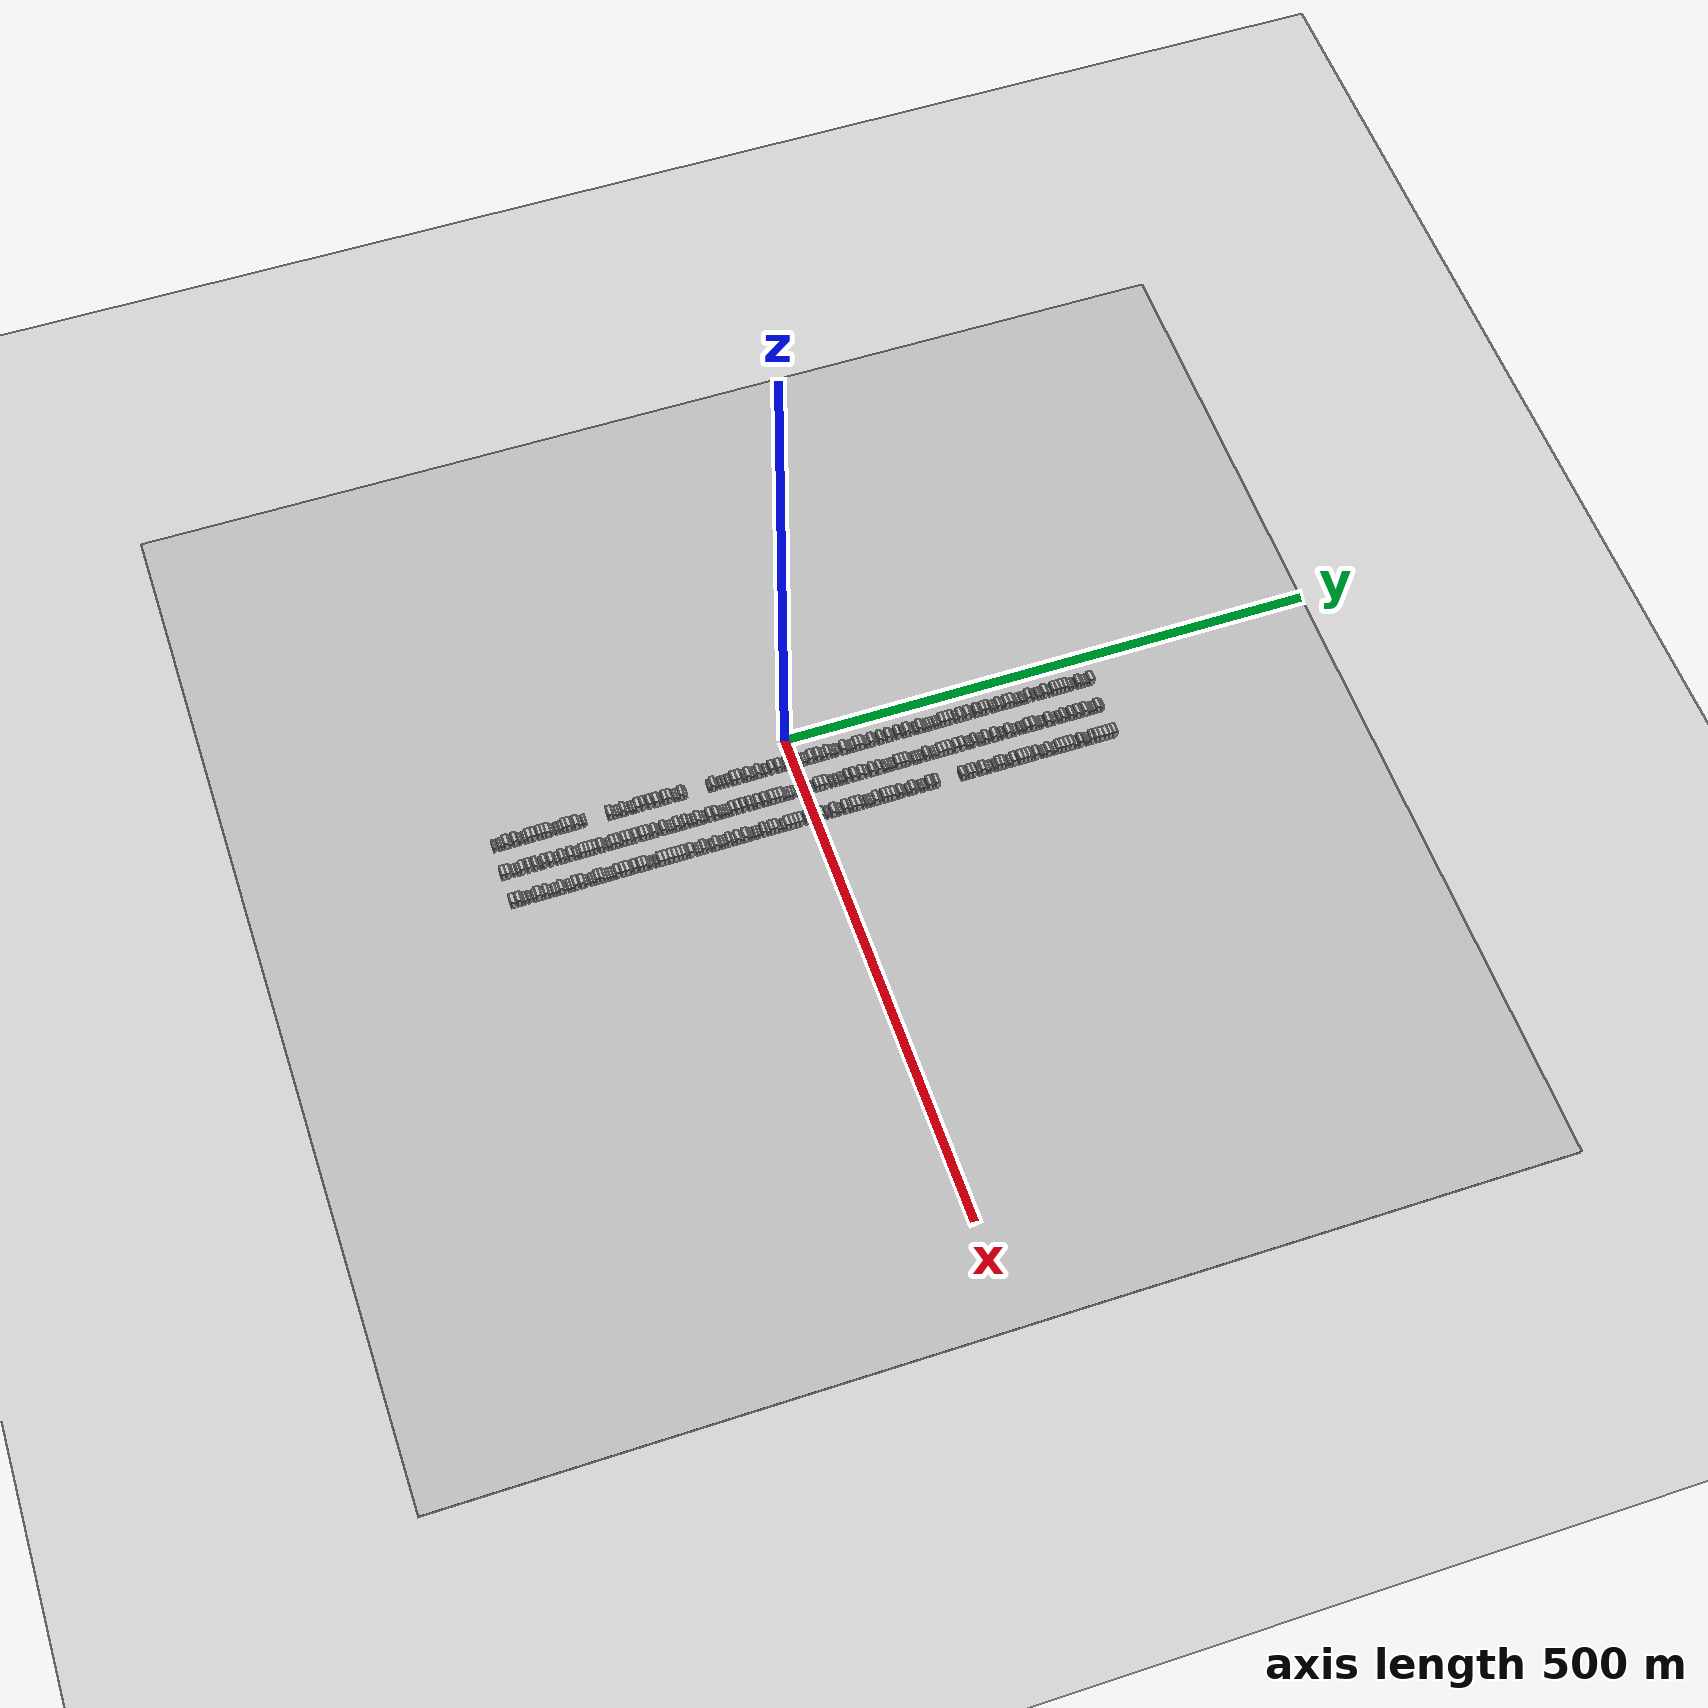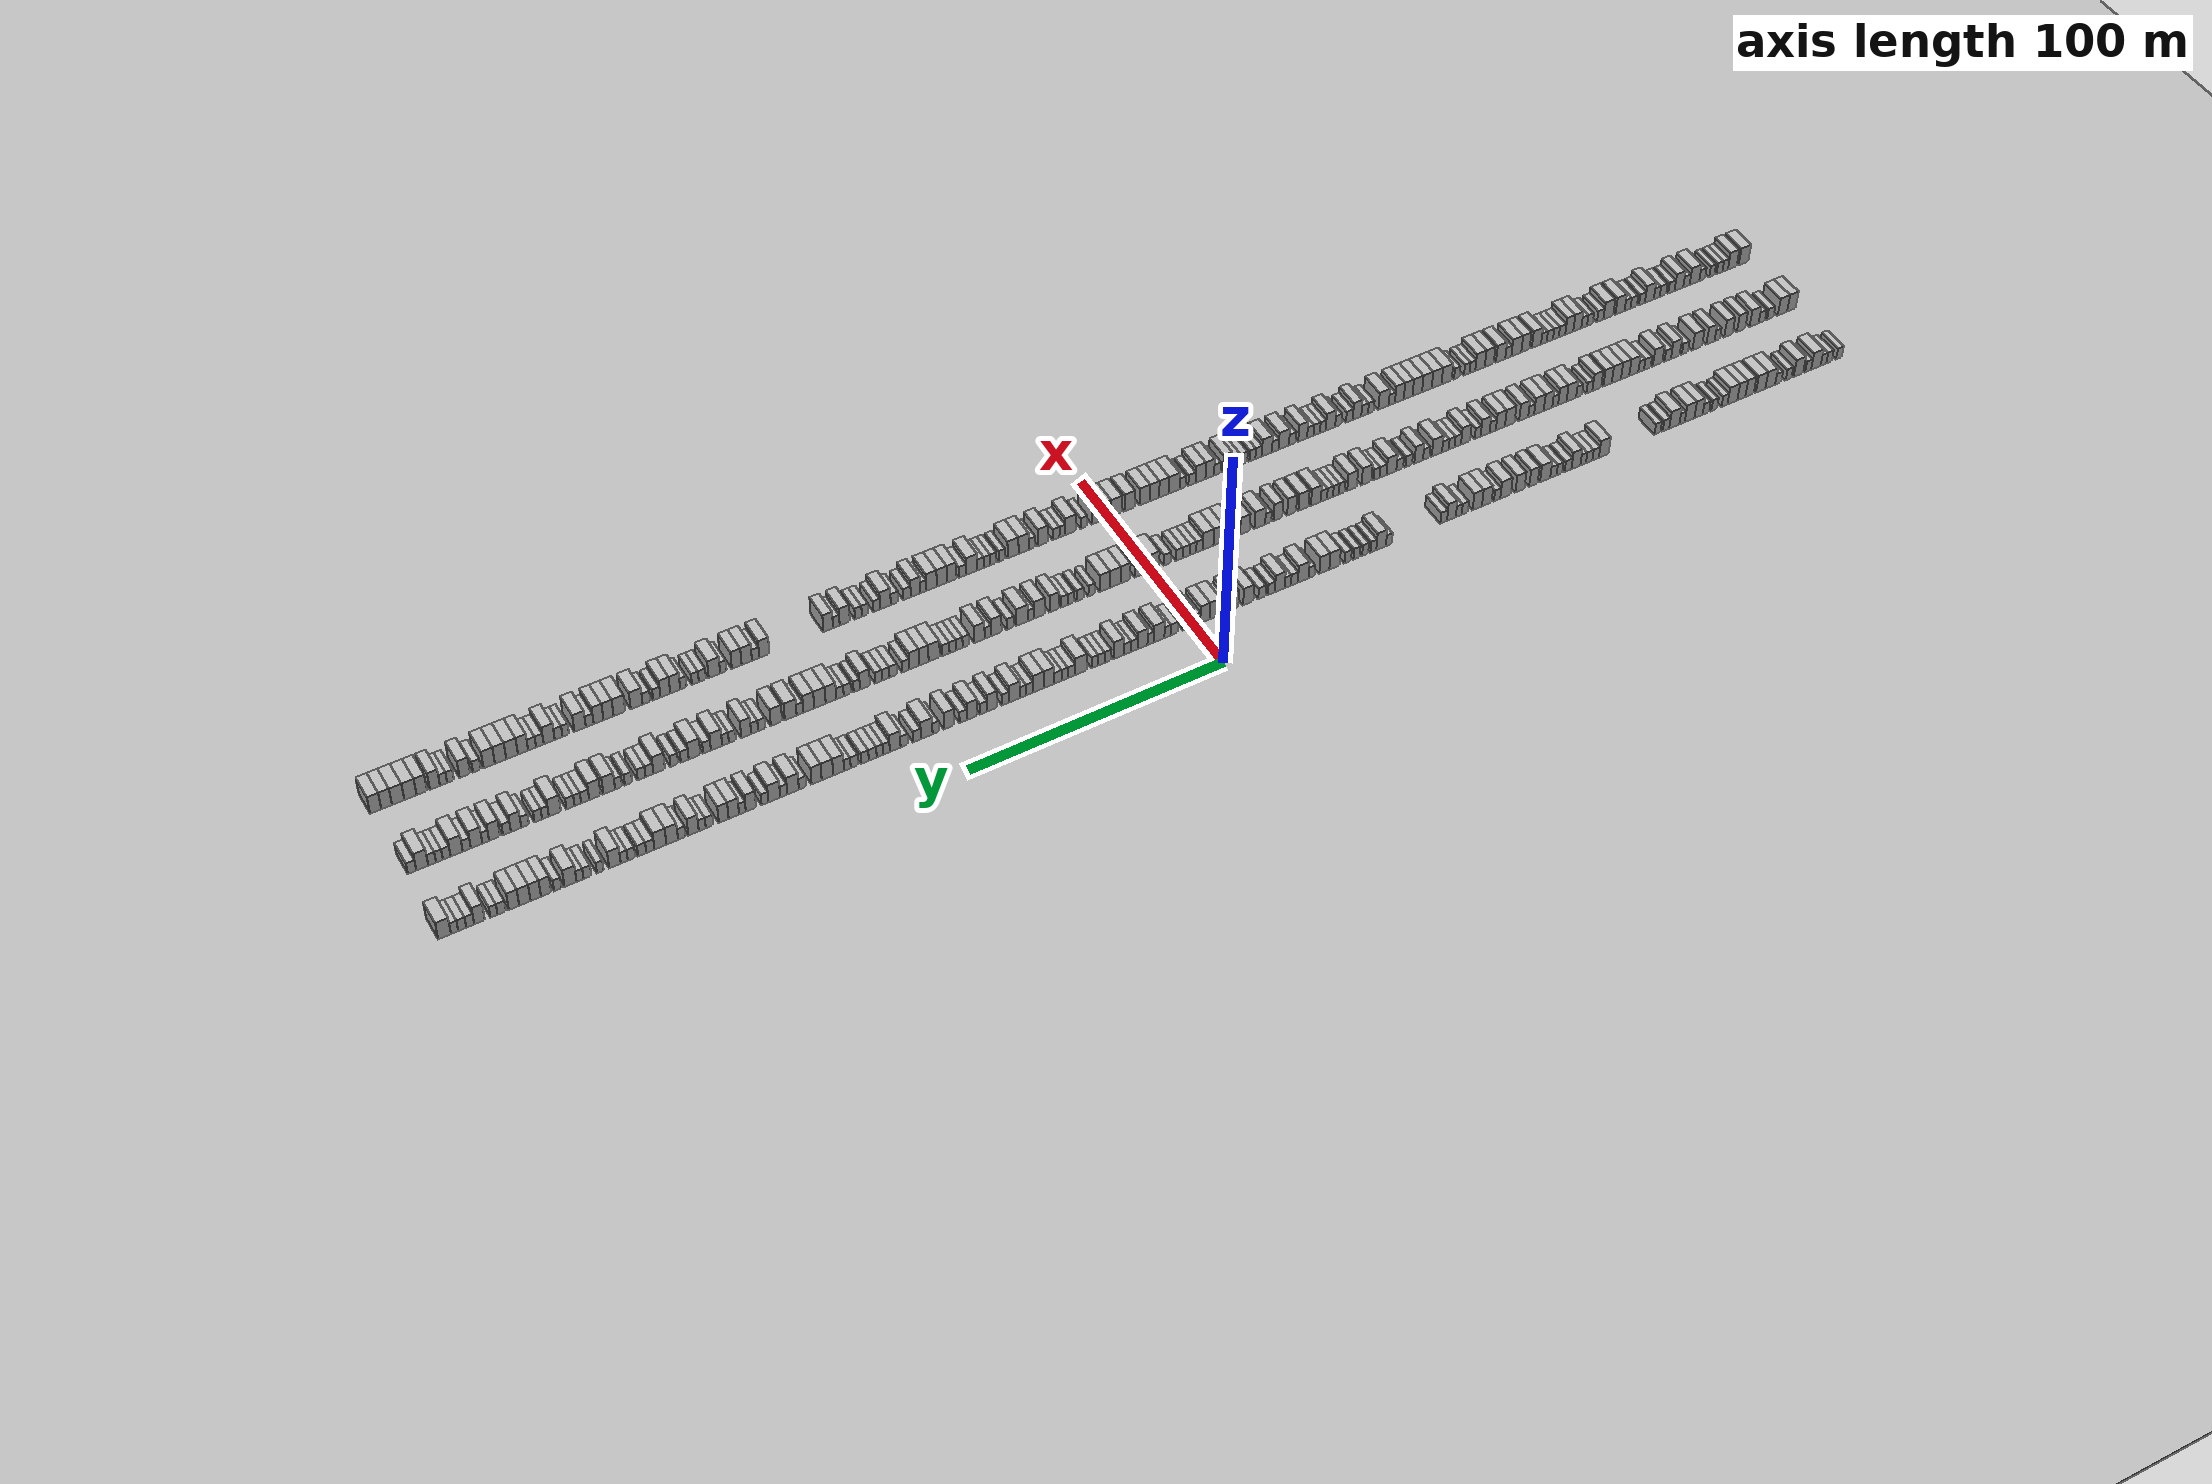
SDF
<?xml version="1.0" encoding="utf-8"?>

<sdf version="1.6">

   <world name="default">

      <gui fullscreen="0">

         <camera name="user_camera">

            <pose>-15 0 4.57585 0 0 0</pose>

            <view_controller>orbit</view_controller>

         </camera>

      </gui>

      <scene>

         <sky>

           <clouds>

             <speed>12</speed>

           </clouds>

         </sky>

         <ambient>0.4 0.4 0.4 1</ambient>

         <background>0.7 0.7 0.7 1</background>

         <shadows>1</shadows>

      </scene>

      <gravity>0 0 -9.8066</gravity>

      <magnetic_field>6e-06 2.3e-05 -4.2e-05</magnetic_field>

      <physics default="0" name="default_physics" type="ode">

         <ode>

            <solver>

               <type>quick</type>

               <iters>10</iters>

               <sor>1.0</sor>

               <use_dynamic_moi_rescaling>0</use_dynamic_moi_rescaling>

            </solver>

            <constraints>

               <cfm>0</cfm>

               <erp>0.2</erp>

               <contact_max_correcting_vel>100</contact_max_correcting_vel>

               <contact_surface_layer>0.001</contact_surface_layer>

            </constraints>

         </ode>

         <max_step_size>0.004</max_step_size>

         <real_time_factor>1</real_time_factor>

         <real_time_update_rate>250</real_time_update_rate>

      </physics>

      <light name="sun" type="directional">

         <cast_shadows>1</cast_shadows>

         <pose>0 0 10 0 0 0</pose>

         <diffuse>0.8 0.8 0.8 1</diffuse>

         <specular>0.2 0.2 0.2 1</specular>

         <attenuation>

            <range>1000</range>

            <constant>0.9</constant>

            <linear>0.01</linear>

            <quadratic>0.001</quadratic>

         </attenuation>

         <direction>-0.5 0.1 -0.9</direction>

      </light>

      <include>

         <name>ground_plane_1</name>

         <uri>model://HANNAS_ground_plane</uri>

         <pose>0 0 0  0 0 0</pose>

      </include>

      <include>

         <name>ground_plane_2</name>

         <uri>model://HANNAS_ground_plane</uri>

         <pose>100 0 0  0 0 0</pose>

      </include>

      <model name="building_1">

         <static>1</static>

         <pose frame="">25.0000 -277.6647 0 0.000000 0.000000 0.000000</pose>

         <link name="link">

            <pose frame="">0 0 3.00 0 0 0</pose>

            <collision name="collision">

               <geometry>

                  <box>

                     <size>10.0000 2.6705 6.0000</size>

                  </box>

               </geometry>

               <max_contacts>10</max_contacts>

               <surface>

                  <contact>

                     <ode/>

                  </contact>

                  <bounce/>

                  <friction>

                     <torsional>

                        <ode/>

                     </torsional>

                     <ode/>

                  </friction>

               </surface>

            </collision>

            <visual name="visual">

               <cast_shadows>0</cast_shadows>

               <geometry>

                  <box>

                     <size>10.0000 2.6705 6.0000</size>

                  </box>

               </geometry>

               <material>

                  <script>

                     <uri>model://HANNAS_wall/materials/scripts</uri>

                     <uri>model://HANNAS_wall/materials/textures</uri>

                     <name>vrc/HANNAS_wall</name>

                  </script>

               </material>

            </visual>

            <self_collide>0</self_collide>

            <enable_wind>0</enable_wind>

            <kinematic>0</kinematic>

         </link>

      </model>

      <model name="building_2">

         <static>1</static>

         <pose frame="">25.0000 -273.0966 0 0.000000 0.000000 0.000000</pose>

         <link name="link">

            <pose frame="">0 0 3.00 0 0 0</pose>

            <collision name="collision">

               <geometry>

                  <box>

                     <size>10.0000 2.4657 6.0000</size>

                  </box>

               </geometry>

               <max_contacts>10</max_contacts>

               <surface>

                  <contact>

                     <ode/>

                  </contact>

                  <bounce/>

                  <friction>

                     <torsional>

                        <ode/>

                     </torsional>

                     <ode/>

                  </friction>

               </surface>

            </collision>

            <visual name="visual">

               <cast_shadows>0</cast_shadows>

               <geometry>

                  <box>

                     <size>10.0000 2.4657 6.0000</size>

                  </box>

               </geometry>

               <material>

                  <script>

                     <uri>model://HANNAS_wall/materials/scripts</uri>

                     <uri>model://HANNAS_wall/materials/textures</uri>

                     <name>vrc/HANNAS_wall</name>

                  </script>

               </material>

            </visual>

            <self_collide>0</self_collide>

            <enable_wind>0</enable_wind>

            <kinematic>0</kinematic>

         </link>

      </model>

      <model name="building_3">

         <static>1</static>

         <pose frame="">25.0000 -270.5756 0 0.000000 0.000000 0.000000</pose>

         <link name="link">

            <pose frame="">0 0 3.00 0 0 0</pose>

            <collision name="collision">

               <geometry>

                  <box>

                     <size>10.0000 2.5765 6.0000</size>

                  </box>

               </geometry>

               <max_contacts>10</max_contacts>

               <surface>

                  <contact>

                     <ode/>

                  </contact>

                  <bounce/>

                  <friction>

                     <torsional>

                        <ode/>

                     </torsional>

                     <ode/>

                  </friction>

               </surface>

            </collision>

            <visual name="visual">

               <cast_shadows>0</cast_shadows>

               <geometry>

                  <box>

                     <size>10.0000 2.5765 6.0000</size>

                  </box>

               </geometry>

               <material>

                  <script>

                     <uri>model://HANNAS_wall/materials/scripts</uri>

                     <uri>model://HANNAS_wall/materials/textures</uri>

                     <name>vrc/HANNAS_wall</name>

                  </script>

               </material>

            </visual>

            <self_collide>0</self_collide>

            <enable_wind>0</enable_wind>

            <kinematic>0</kinematic>

         </link>

      </model>

      <model name="building_4">

         <static>1</static>

         <pose frame="">25.0000 -267.0598 0 0.000000 0.000000 0.000000</pose>

         <link name="link">

            <pose frame="">0 0 4.50 0 0 0</pose>

            <collision name="collision">

               <geometry>

                  <box>

                     <size>10.0000 4.4550 9.0000</size>

                  </box>

               </geometry>

               <max_contacts>10</max_contacts>

               <surface>

                  <contact>

                     <ode/>

                  </contact>

                  <bounce/>

                  <friction>

                     <torsional>

                        <ode/>

                     </torsional>

                     <ode/>

                  </friction>

               </surface>

            </collision>

            <visual name="visual">

               <cast_shadows>0</cast_shadows>

               <geometry>

                  <box>

                     <size>10.0000 4.4550 9.0000</size>

                  </box>

               </geometry>

               <material>

                  <script>

                     <uri>model://HANNAS_wall/materials/scripts</uri>

                     <uri>model://HANNAS_wall/materials/textures</uri>

                     <name>vrc/HANNAS_wall</name>

                  </script>

               </material>

            </visual>

            <self_collide>0</self_collide>

            <enable_wind>0</enable_wind>

            <kinematic>0</kinematic>

         </link>

      </model>

      <model name="building_5">

         <static>1</static>

         <pose frame="">25.0000 -263.5260 0 0.000000 0.000000 0.000000</pose>

         <link name="link">

            <pose frame="">0 0 3.00 0 0 0</pose>

            <collision name="collision">

               <geometry>

                  <box>

                     <size>10.0000 2.6125 6.0000</size>

                  </box>

               </geometry>

               <max_contacts>10</max_contacts>

               <surface>

                  <contact>

                     <ode/>

                  </contact>

                  <bounce/>

                  <friction>

                     <torsional>

                        <ode/>

                     </torsional>

                     <ode/>

                  </friction>

               </surface>

            </collision>

            <visual name="visual">

               <cast_shadows>0</cast_shadows>

               <geometry>

                  <box>

                     <size>10.0000 2.6125 6.0000</size>

                  </box>

               </geometry>

               <material>

                  <script>

                     <uri>model://HANNAS_wall/materials/scripts</uri>

                     <uri>model://HANNAS_wall/materials/textures</uri>

                     <name>vrc/HANNAS_wall</name>

                  </script>

               </material>

            </visual>

            <self_collide>0</self_collide>

            <enable_wind>0</enable_wind>

            <kinematic>0</kinematic>

         </link>

      </model>

      <model name="building_6">

         <static>1</static>

         <pose frame="">25.0000 -259.0830 0 0.000000 0.000000 0.000000</pose>

         <link name="link">

            <pose frame="">0 0 4.50 0 0 0</pose>

            <collision name="collision">

               <geometry>

                  <box>

                     <size>10.0000 4.2736 9.0000</size>

                  </box>

               </geometry>

               <max_contacts>10</max_contacts>

               <surface>

                  <contact>

                     <ode/>

                  </contact>

                  <bounce/>

                  <friction>

                     <torsional>

                        <ode/>

                     </torsional>

                     <ode/>

                  </friction>

               </surface>

            </collision>

            <visual name="visual">

               <cast_shadows>0</cast_shadows>

               <geometry>

                  <box>

                     <size>10.0000 4.2736 9.0000</size>

                  </box>

               </geometry>

               <material>

                  <script>

                     <uri>model://HANNAS_wall/materials/scripts</uri>

                     <uri>model://HANNAS_wall/materials/textures</uri>

                     <name>vrc/HANNAS_wall</name>

                  </script>

               </material>

            </visual>

            <self_collide>0</self_collide>

            <enable_wind>0</enable_wind>

            <kinematic>0</kinematic>

         </link>

      </model>

      <model name="building_7">

         <static>1</static>

         <pose frame="">25.0000 -254.6149 0 0.000000 0.000000 0.000000</pose>

         <link name="link">

            <pose frame="">0 0 3.00 0 0 0</pose>

            <collision name="collision">

               <geometry>

                  <box>

                     <size>10.0000 2.6625 6.0000</size>

                  </box>

               </geometry>

               <max_contacts>10</max_contacts>

               <surface>

                  <contact>

                     <ode/>

                  </contact>

                  <bounce/>

                  <friction>

                     <torsional>

                        <ode/>

                     </torsional>

                     <ode/>

                  </friction>

               </surface>

            </collision>

            <visual name="visual">

               <cast_shadows>0</cast_shadows>

               <geometry>

                  <box>

                     <size>10.0000 2.6625 6.0000</size>

                  </box>

               </geometry>

               <material>

                  <script>

                     <uri>model://HANNAS_wall/materials/scripts</uri>

                     <uri>model://HANNAS_wall/materials/textures</uri>

                     <name>vrc/HANNAS_wall</name>

                  </script>

               </material>

            </visual>

            <self_collide>0</self_collide>

            <enable_wind>0</enable_wind>

            <kinematic>0</kinematic>

         </link>

      </model>

      <model name="building_8">

         <static>1</static>

         <pose frame="">25.0000 -249.8685 0 0.000000 0.000000 0.000000</pose>

         <link name="link">

            <pose frame="">0 0 3.00 0 0 0</pose>

            <collision name="collision">

               <geometry>

                  <box>

                     <size>10.0000 2.8305 6.0000</size>

                  </box>

               </geometry>

               <max_contacts>10</max_contacts>

               <surface>

                  <contact>

                     <ode/>

                  </contact>

                  <bounce/>

                  <friction>

                     <torsional>

                        <ode/>

                     </torsional>

                     <ode/>

                  </friction>

               </surface>

            </collision>

            <visual name="visual">

               <cast_shadows>0</cast_shadows>

               <geometry>

                  <box>

                     <size>10.0000 2.8305 6.0000</size>

                  </box>

               </geometry>

               <material>

                  <script>

                     <uri>model://HANNAS_wall/materials/scripts</uri>

                     <uri>model://HANNAS_wall/materials/textures</uri>

                     <name>vrc/HANNAS_wall</name>

                  </script>

               </material>

            </visual>

            <self_collide>0</self_collide>

            <enable_wind>0</enable_wind>

            <kinematic>0</kinematic>

         </link>

      </model>

      <model name="building_9">

         <static>1</static>

         <pose frame="">25.0000 -246.2379 0 0.000000 0.000000 0.000000</pose>

         <link name="link">

            <pose frame="">0 0 4.50 0 0 0</pose>

            <collision name="collision">

               <geometry>

                  <box>

                     <size>10.0000 4.4307 9.0000</size>

                  </box>

               </geometry>

               <max_contacts>10</max_contacts>

               <surface>

                  <contact>

                     <ode/>

                  </contact>

                  <bounce/>

                  <friction>

                     <torsional>

                        <ode/>

                     </torsional>

                     <ode/>

                  </friction>

               </surface>

            </collision>

            <visual name="visual">

               <cast_shadows>0</cast_shadows>

               <geometry>

                  <box>

                     <size>10.0000 4.4307 9.0000</size>

                  </box>

               </geometry>

               <material>

                  <script>

                     <uri>model://HANNAS_wall/materials/scripts</uri>

                     <uri>model://HANNAS_wall/materials/textures</uri>

                     <name>vrc/HANNAS_wall</name>

                  </script>

               </material>

            </visual>

            <self_collide>0</self_collide>

            <enable_wind>0</enable_wind>

            <kinematic>0</kinematic>

         </link>

      </model>

      <model name="building_10">

         <static>1</static>

         <pose frame="">25.0000 -241.8874 0 0.000000 0.000000 0.000000</pose>

         <link name="link">

            <pose frame="">0 0 4.50 0 0 0</pose>

            <collision name="collision">

               <geometry>

                  <box>

                     <size>10.0000 4.2704 9.0000</size>

                  </box>

               </geometry>

               <max_contacts>10</max_contacts>

               <surface>

                  <contact>

                     <ode/>

                  </contact>

                  <bounce/>

                  <friction>

                     <torsional>

                        <ode/>

                     </torsional>

                     <ode/>

                  </friction>

               </surface>

            </collision>

            <visual name="visual">

               <cast_shadows>0</cast_shadows>

               <geometry>

                  <box>

                     <size>10.0000 4.2704 9.0000</size>

                  </box>

               </geometry>

               <material>

                  <script>

                     <uri>model://HANNAS_wall/materials/scripts</uri>

                     <uri>model://HANNAS_wall/materials/textures</uri>

                     <name>vrc/HANNAS_wall</name>

                  </script>

               </material>

            </visual>

            <self_collide>0</self_collide>

            <enable_wind>0</enable_wind>

            <kinematic>0</kinematic>

         </link>

      </model>

      <model name="building_11">

         <static>1</static>

         <pose frame="">25.0000 -236.8503 0 0.000000 0.000000 0.000000</pose>

         <link name="link">

            <pose frame="">0 0 4.50 0 0 0</pose>

            <collision name="collision">

               <geometry>

                  <box>

                     <size>10.0000 3.8038 9.0000</size>

                  </box>

               </geometry>

               <max_contacts>10</max_contacts>

               <surface>

                  <contact>

                     <ode/>

                  </contact>

                  <bounce/>

                  <friction>

                     <torsional>

                        <ode/>

                     </torsional>

                     <ode/>

                  </friction>

               </surface>

            </collision>

            <visual name="visual">

               <cast_shadows>0</cast_shadows>

               <geometry>

                  <box>

                     <size>10.0000 3.8038 9.0000</size>

                  </box>

               </geometry>

               <material>

                  <script>

                     <uri>model://HANNAS_wall/materials/scripts</uri>

                     <uri>model://HANNAS_wall/materials/textures</uri>

                     <name>vrc/HANNAS_wall</name>

                  </script>

               </material>

            </visual>

            <self_collide>0</self_collide>

            <enable_wind>0</enable_wind>

            <kinematic>0</kinematic>

         </link>

      </model>

      <model name="building_12">

         <static>1</static>

         <pose frame="">25.0000 -233.1456 0 0.000000 0.000000 0.000000</pose>

         <link name="link">

            <pose frame="">0 0 4.50 0 0 0</pose>

            <collision name="collision">

               <geometry>

                  <box>

                     <size>10.0000 3.6056 9.0000</size>

                  </box>

               </geometry>

               <max_contacts>10</max_contacts>

               <surface>

                  <contact>

                     <ode/>

                  </contact>

                  <bounce/>

                  <friction>

                     <torsional>

                        <ode/>

                     </torsional>

                     <ode/>

                  </friction>

               </surface>

            </collision>

            <visual name="visual">

               <cast_shadows>0</cast_shadows>

               <geometry>

                  <box>

                     <size>10.0000 3.6056 9.0000</size>

                  </box>

               </geometry>

               <material>

                  <script>

                     <uri>model://HANNAS_wall/materials/scripts</uri>

                     <uri>model://HANNAS_wall/materials/textures</uri>

                     <name>vrc/HANNAS_wall</name>

                  </script>

               </material>

            </visual>

            <self_collide>0</self_collide>

            <enable_wind>0</enable_wind>

            <kinematic>0</kinematic>

         </link>

      </model>

      <model name="building_13">

         <static>1</static>

         <pose frame="">25.0000 -229.1303 0 0.000000 0.000000 0.000000</pose>

         <link name="link">

            <pose frame="">0 0 4.50 0 0 0</pose>

            <collision name="collision">

               <geometry>

                  <box>

                     <size>10.0000 4.4249 9.0000</size>

                  </box>

               </geometry>

               <max_contacts>10</max_contacts>

               <surface>

                  <contact>

                     <ode/>

                  </contact>

                  <bounce/>

                  <friction>

                     <torsional>

                        <ode/>

                     </torsional>

                     <ode/>

                  </friction>

               </surface>

            </collision>

            <visual name="visual">

               <cast_shadows>0</cast_shadows>

               <geometry>

                  <box>

                     <size>10.0000 4.4249 9.0000</size>

                  </box>

               </geometry>

               <material>

                  <script>

                     <uri>model://HANNAS_wall/materials/scripts</uri>

                     <uri>model://HANNAS_wall/materials/textures</uri>

                     <name>vrc/HANNAS_wall</name>

                  </script>

               </material>

            </visual>

            <self_collide>0</self_collide>

            <enable_wind>0</enable_wind>

            <kinematic>0</kinematic>

         </link>

      </model>

      <model name="building_14">

         <static>1</static>

         <pose frame="">25.0000 -225.5683 0 0.000000 0.000000 0.000000</pose>

         <link name="link">

            <pose frame="">0 0 3.00 0 0 0</pose>

            <collision name="collision">

               <geometry>

                  <box>

                     <size>10.0000 2.6992 6.0000</size>

                  </box>

               </geometry>

               <max_contacts>10</max_contacts>

               <surface>

                  <contact>

                     <ode/>

                  </contact>

                  <bounce/>

                  <friction>

                     <torsional>

                        <ode/>

                     </torsional>

                     <ode/>

                  </friction>

               </surface>

            </collision>

            <visual name="visual">

               <cast_shadows>0</cast_shadows>

               <geometry>

                  <box>

                     <size>10.0000 2.6992 6.0000</size>

                  </box>

               </geometry>

               <material>

                  <script>

                     <uri>model://HANNAS_wall/materials/scripts</uri>

                     <uri>model://HANNAS_wall/materials/textures</uri>

                     <name>vrc/HANNAS_wall</name>

                  </script>

               </material>

            </visual>

            <self_collide>0</self_collide>

            <enable_wind>0</enable_wind>

            <kinematic>0</kinematic>

         </link>

      </model>

      <model name="building_15">

         <static>1</static>

         <pose frame="">25.0000 -220.9242 0 0.000000 0.000000 0.000000</pose>

         <link name="link">

            <pose frame="">0 0 3.00 0 0 0</pose>

            <collision name="collision">

               <geometry>

                  <box>

                     <size>10.0000 2.5891 6.0000</size>

                  </box>

               </geometry>

               <max_contacts>10</max_contacts>

               <surface>

                  <contact>

                     <ode/>

                  </contact>

                  <bounce/>

                  <friction>

                     <torsional>

                        <ode/>

                     </torsional>

                     <ode/>

                  </friction>

               </surface>

            </collision>

            <visual name="visual">

               <cast_shadows>0</cast_shadows>

               <geometry>

                  <box>

                     <size>10.0000 2.5891 6.0000</size>

                  </box>

               </geometry>

               <material>

                  <script>

                     <uri>model://HANNAS_wall/materials/scripts</uri>

                     <uri>model://HANNAS_wall/materials/textures</uri>

                     <name>vrc/HANNAS_wall</name>

                  </script>

               </material>

            </visual>

            <self_collide>0</self_collide>

            <enable_wind>0</enable_wind>

            <kinematic>0</kinematic>

         </link>

      </model>

      <model name="building_16">

         <static>1</static>

         <pose frame="">25.0000 -217.1886 0 0.000000 0.000000 0.000000</pose>

         <link name="link">

            <pose frame="">0 0 3.00 0 0 0</pose>

            <collision name="collision">

               <geometry>

                  <box>

                     <size>10.0000 2.8822 6.0000</size>

                  </box>

               </geometry>

               <max_contacts>10</max_contacts>

               <surface>

                  <contact>

                     <ode/>

                  </contact>

                  <bounce/>

                  <friction>

                     <torsional>

                        <ode/>

                     </torsional>

                     <ode/>

                  </friction>

               </surface>

            </collision>

            <visual name="visual">

               <cast_shadows>0</cast_shadows>

               <geometry>

                  <box>

                     <size>10.0000 2.8822 6.0000</size>

                  </box>

               </geometry>

               <material>

                  <script>

                     <uri>model://HANNAS_wall/materials/scripts</uri>

                     <uri>model://HANNAS_wall/materials/textures</uri>

                     <name>vrc/HANNAS_wall</name>

                  </script>

               </material>

            </visual>

            <self_collide>0</self_collide>

            <enable_wind>0</enable_wind>

            <kinematic>0</kinematic>

         </link>

      </model>

      <model name="building_17">

         <static>1</static>

         <pose frame="">25.0000 -213.9027 0 0.000000 0.000000 0.000000</pose>

         <link name="link">

            <pose frame="">0 0 4.50 0 0 0</pose>

            <collision name="collision">

               <geometry>

                  <box>

                     <size>10.0000 3.6897 9.0000</size>

                  </box>

               </geometry>

               <max_contacts>10</max_contacts>

               <surface>

                  <contact>

                     <ode/>

                  </contact>

                  <bounce/>

                  <friction>

                     <torsional>

                        <ode/>

                     </torsional>

                     <ode/>

                  </friction>

               </surface>

            </collision>

            <visual name="visual">

               <cast_shadows>0</cast_shadows>

               <geometry>

                  <box>

                     <size>10.0000 3.6897 9.0000</size>

                  </box>

               </geometry>

               <material>

                  <script>

                     <uri>model://HANNAS_wall/materials/scripts</uri>

                     <uri>model://HANNAS_wall/materials/textures</uri>

                     <name>vrc/HANNAS_wall</name>

                  </script>

               </material>

            </visual>

            <self_collide>0</self_collide>

            <enable_wind>0</enable_wind>

            <kinematic>0</kinematic>

         </link>

      </model>

      <model name="building_18">

         <static>1</static>

         <pose frame="">25.0000 -209.9030 0 0.000000 0.000000 0.000000</pose>

         <link name="link">

            <pose frame="">0 0 4.50 0 0 0</pose>

            <collision name="collision">

               <geometry>

                  <box>

                     <size>10.0000 4.3097 9.0000</size>

                  </box>

               </geometry>

               <max_contacts>10</max_contacts>

               <surface>

                  <contact>

                     <ode/>

                  </contact>

                  <bounce/>

                  <friction>

                     <torsional>

                        <ode/>

                     </torsional>

                     <ode/>

                  </friction>

               </surface>

            </collision>

            <visual name="visual">

               <cast_shadows>0</cast_shadows>

               <geometry>

                  <box>

                     <size>10.0000 4.3097 9.0000</size>

                  </box>

               </geometry>

               <material>

                  <script>

                     <uri>model://HANNAS_wall/materials/scripts</uri>

                     <uri>model://HANNAS_wall/materials/textures</uri>

                     <name>vrc/HANNAS_wall</name>

                  </script>

               </material>

            </visual>

            <self_collide>0</self_collide>

            <enable_wind>0</enable_wind>

            <kinematic>0</kinematic>

         </link>

      </model>

      <model name="building_19">

         <static>1</static>

         <pose frame="">25.0000 -206.5455 0 0.000000 0.000000 0.000000</pose>

         <link name="link">

            <pose frame="">0 0 3.00 0 0 0</pose>

            <collision name="collision">

               <geometry>

                  <box>

                     <size>10.0000 2.4053 6.0000</size>

                  </box>

               </geometry>

               <max_contacts>10</max_contacts>

               <surface>

                  <contact>

                     <ode/>

                  </contact>

                  <bounce/>

                  <friction>

                     <torsional>

                        <ode/>

                     </torsional>

                     <ode/>

                  </friction>

               </surface>

            </collision>

            <visual name="visual">

               <cast_shadows>0</cast_shadows>

               <geometry>

                  <box>

                     <size>10.0000 2.4053 6.0000</size>

                  </box>

               </geometry>

               <material>

                  <script>

                     <uri>model://HANNAS_wall/materials/scripts</uri>

                     <uri>model://HANNAS_wall/materials/textures</uri>

                     <name>vrc/HANNAS_wall</name>

                  </script>

               </material>

            </visual>

            <self_collide>0</self_collide>

            <enable_wind>0</enable_wind>

            <kinematic>0</kinematic>

         </link>

      </model>

      <model name="building_20">

         <static>1</static>

         <pose frame="">25.0000 -203.1059 0 0.000000 0.000000 0.000000</pose>

         <link name="link">

            <pose frame="">0 0 4.50 0 0 0</pose>

            <collision name="collision">

               <geometry>

                  <box>

                     <size>10.0000 4.4738 9.0000</size>

                  </box>

               </geometry>

               <max_contacts>10</max_contacts>

               <surface>

                  <contact>

                     <ode/>

                  </contact>

                  <bounce/>

                  <friction>

                     <torsional>

                        <ode/>

                     </torsional>

                     <ode/>

                  </friction>

               </surface>

            </collision>

            <visual name="visual">

               <cast_shadows>0</cast_shadows>

               <geometry>

                  <box>

                     <size>10.0000 4.4738 9.0000</size>

                  </box>

               </geometry>

               <material>

                  <script>

                     <uri>model://HANNAS_wall/materials/scripts</uri>

                     <uri>model://HANNAS_wall/materials/textures</uri>

                     <name>vrc/HANNAS_wall</name>

                  </script>

               </material>

            </visual>

            <self_collide>0</self_collide>

            <enable_wind>0</enable_wind>

            <kinematic>0</kinematic>

         </link>

      </model>

      <model name="building_21">

         <static>1</static>

         <pose frame="">25.0000 -199.4058 0 0.000000 0.000000 0.000000</pose>

         <link name="link">

            <pose frame="">0 0 3.00 0 0 0</pose>

            <collision name="collision">

               <geometry>

                  <box>

                     <size>10.0000 2.9264 6.0000</size>

                  </box>

               </geometry>

               <max_contacts>10</max_contacts>

               <surface>

                  <contact>

                     <ode/>

                  </contact>

                  <bounce/>

                  <friction>

                     <torsional>

                        <ode/>

                     </torsional>

                     <ode/>

                  </friction>

               </surface>

            </collision>

            <visual name="visual">

               <cast_shadows>0</cast_shadows>

               <geometry>

                  <box>

                     <size>10.0000 2.9264 6.0000</size>

                  </box>

               </geometry>

               <material>

                  <script>

                     <uri>model://HANNAS_wall/materials/scripts</uri>

                     <uri>model://HANNAS_wall/materials/textures</uri>

                     <name>vrc/HANNAS_wall</name>

                  </script>

               </material>

            </visual>

            <self_collide>0</self_collide>

            <enable_wind>0</enable_wind>

            <kinematic>0</kinematic>

         </link>

      </model>

      <model name="building_22">

         <static>1</static>

         <pose frame="">25.0000 -195.6194 0 0.000000 0.000000 0.000000</pose>

         <link name="link">

            <pose frame="">0 0 3.00 0 0 0</pose>

            <collision name="collision">

               <geometry>

                  <box>

                     <size>10.0000 2.6462 6.0000</size>

                  </box>

               </geometry>

               <max_contacts>10</max_contacts>

               <surface>

                  <contact>

                     <ode/>

                  </contact>

                  <bounce/>

                  <friction>

                     <torsional>

                        <ode/>

                     </torsional>

                     <ode/>

                  </friction>

               </surface>

            </collision>

            <visual name="visual">

               <cast_shadows>0</cast_shadows>

               <geometry>

                  <box>

                     <size>10.0000 2.6462 6.0000</size>

                  </box>

               </geometry>

               <material>

                  <script>

                     <uri>model://HANNAS_wall/materials/scripts</uri>

                     <uri>model://HANNAS_wall/materials/textures</uri>

                     <name>vrc/HANNAS_wall</name>

                  </script>

               </material>

            </visual>

            <self_collide>0</self_collide>

            <enable_wind>0</enable_wind>

            <kinematic>0</kinematic>

         </link>

      </model>

      <model name="building_23">

         <static>1</static>

         <pose frame="">25.0000 -171.9300 0 0.000000 0.000000 0.000000</pose>

         <link name="link">

            <pose frame="">0 0 4.50 0 0 0</pose>

            <collision name="collision">

               <geometry>

                  <box>

                     <size>10.0000 4.2442 9.0000</size>

                  </box>

               </geometry>

               <max_contacts>10</max_contacts>

               <surface>

                  <contact>

                     <ode/>

                  </contact>

                  <bounce/>

                  <friction>

                     <torsional>

                        <ode/>

                     </torsional>

                     <ode/>

                  </friction>

               </surface>

            </collision>

            <visual name="visual">

               <cast_shadows>0</cast_shadows>

               <geometry>

                  <box>

                     <size>10.0000 4.2442 9.0000</size>

                  </box>

               </geometry>

               <material>

                  <script>

                     <uri>model://HANNAS_wall/materials/scripts</uri>

                     <uri>model://HANNAS_wall/materials/textures</uri>

                     <name>vrc/HANNAS_wall</name>

                  </script>

               </material>

            </visual>

            <self_collide>0</self_collide>

            <enable_wind>0</enable_wind>

            <kinematic>0</kinematic>

         </link>

      </model>

      <model name="building_24">

         <static>1</static>

         <pose frame="">25.0000 -168.3717 0 0.000000 0.000000 0.000000</pose>

         <link name="link">

            <pose frame="">0 0 3.00 0 0 0</pose>

            <collision name="collision">

               <geometry>

                  <box>

                     <size>10.0000 2.8724 6.0000</size>

                  </box>

               </geometry>

               <max_contacts>10</max_contacts>

               <surface>

                  <contact>

                     <ode/>

                  </contact>

                  <bounce/>

                  <friction>

                     <torsional>

                        <ode/>

                     </torsional>

                     <ode/>

                  </friction>

               </surface>

            </collision>

            <visual name="visual">

               <cast_shadows>0</cast_shadows>

               <geometry>

                  <box>

                     <size>10.0000 2.8724 6.0000</size>

                  </box>

               </geometry>

               <material>

                  <script>

                     <uri>model://HANNAS_wall/materials/scripts</uri>

                     <uri>model://HANNAS_wall/materials/textures</uri>

                     <name>vrc/HANNAS_wall</name>

                  </script>

               </material>

            </visual>

            <self_collide>0</self_collide>

            <enable_wind>0</enable_wind>

            <kinematic>0</kinematic>

         </link>

      </model>

      <model name="building_25">

         <static>1</static>

         <pose frame="">25.0000 -165.5515 0 0.000000 0.000000 0.000000</pose>

         <link name="link">

            <pose frame="">0 0 3.00 0 0 0</pose>

            <collision name="collision">

               <geometry>

                  <box>

                     <size>10.0000 2.7679 6.0000</size>

                  </box>

               </geometry>

               <max_contacts>10</max_contacts>

               <surface>

                  <contact>

                     <ode/>

                  </contact>

                  <bounce/>

                  <friction>

                     <torsional>

                        <ode/>

                     </torsional>

                     <ode/>

                  </friction>

               </surface>

            </collision>

            <visual name="visual">

               <cast_shadows>0</cast_shadows>

               <geometry>

                  <box>

                     <size>10.0000 2.7679 6.0000</size>

                  </box>

               </geometry>

               <material>

                  <script>

                     <uri>model://HANNAS_wall/materials/scripts</uri>

                     <uri>model://HANNAS_wall/materials/textures</uri>

                     <name>vrc/HANNAS_wall</name>

                  </script>

               </material>

            </visual>

            <self_collide>0</self_collide>

            <enable_wind>0</enable_wind>

            <kinematic>0</kinematic>

         </link>

      </model>

      <model name="building_26">

         <static>1</static>

         <pose frame="">25.0000 -162.9412 0 0.000000 0.000000 0.000000</pose>

         <link name="link">

            <pose frame="">0 0 3.00 0 0 0</pose>

            <collision name="collision">

               <geometry>

                  <box>

                     <size>10.0000 2.4527 6.0000</size>

                  </box>

               </geometry>

               <max_contacts>10</max_contacts>

               <surface>

                  <contact>

                     <ode/>

                  </contact>

                  <bounce/>

                  <friction>

                     <torsional>

                        <ode/>

                     </torsional>

                     <ode/>

                  </friction>

               </surface>

            </collision>

            <visual name="visual">

               <cast_shadows>0</cast_shadows>

               <geometry>

                  <box>

                     <size>10.0000 2.4527 6.0000</size>

                  </box>

               </geometry>

               <material>

                  <script>

                     <uri>model://HANNAS_wall/materials/scripts</uri>

                     <uri>model://HANNAS_wall/materials/textures</uri>

                     <name>vrc/HANNAS_wall</name>

                  </script>

               </material>

            </visual>

            <self_collide>0</self_collide>

            <enable_wind>0</enable_wind>

            <kinematic>0</kinematic>

         </link>

      </model>

      <model name="building_27">

         <static>1</static>

         <pose frame="">25.0000 -159.7612 0 0.000000 0.000000 0.000000</pose>

         <link name="link">

            <pose frame="">0 0 4.50 0 0 0</pose>

            <collision name="collision">

               <geometry>

                  <box>

                     <size>10.0000 3.9074 9.0000</size>

                  </box>

               </geometry>

               <max_contacts>10</max_contacts>

               <surface>

                  <contact>

                     <ode/>

                  </contact>

                  <bounce/>

                  <friction>

                     <torsional>

                        <ode/>

                     </torsional>

                     <ode/>

                  </friction>

               </surface>

            </collision>

            <visual name="visual">

               <cast_shadows>0</cast_shadows>

               <geometry>

                  <box>

                     <size>10.0000 3.9074 9.0000</size>

                  </box>

               </geometry>

               <material>

                  <script>

                     <uri>model://HANNAS_wall/materials/scripts</uri>

                     <uri>model://HANNAS_wall/materials/textures</uri>

                     <name>vrc/HANNAS_wall</name>

                  </script>

               </material>

            </visual>

            <self_collide>0</self_collide>

            <enable_wind>0</enable_wind>

            <kinematic>0</kinematic>

         </link>

      </model>

      <model name="building_28">

         <static>1</static>

         <pose frame="">25.0000 -156.3149 0 0.000000 0.000000 0.000000</pose>

         <link name="link">

            <pose frame="">0 0 3.00 0 0 0</pose>

            <collision name="collision">

               <geometry>

                  <box>

                     <size>10.0000 2.9851 6.0000</size>

                  </box>

               </geometry>

               <max_contacts>10</max_contacts>

               <surface>

                  <contact>

                     <ode/>

                  </contact>

                  <bounce/>

                  <friction>

                     <torsional>

                        <ode/>

                     </torsional>

                     <ode/>

                  </friction>

               </surface>

            </collision>

            <visual name="visual">

               <cast_shadows>0</cast_shadows>

               <geometry>

                  <box>

                     <size>10.0000 2.9851 6.0000</size>

                  </box>

               </geometry>

               <material>

                  <script>

                     <uri>model://HANNAS_wall/materials/scripts</uri>

                     <uri>model://HANNAS_wall/materials/textures</uri>

                     <name>vrc/HANNAS_wall</name>

                  </script>

               </material>

            </visual>

            <self_collide>0</self_collide>

            <enable_wind>0</enable_wind>

            <kinematic>0</kinematic>

         </link>

      </model>

      <model name="building_29">

         <static>1</static>

         <pose frame="">25.0000 -152.5858 0 0.000000 0.000000 0.000000</pose>

         <link name="link">

            <pose frame="">0 0 3.00 0 0 0</pose>

            <collision name="collision">

               <geometry>

                  <box>

                     <size>10.0000 2.4733 6.0000</size>

                  </box>

               </geometry>

               <max_contacts>10</max_contacts>

               <surface>

                  <contact>

                     <ode/>

                  </contact>

                  <bounce/>

                  <friction>

                     <torsional>

                        <ode/>

                     </torsional>

                     <ode/>

                  </friction>

               </surface>

            </collision>

            <visual name="visual">

               <cast_shadows>0</cast_shadows>

               <geometry>

                  <box>

                     <size>10.0000 2.4733 6.0000</size>

                  </box>

               </geometry>

               <material>

                  <script>

                     <uri>model://HANNAS_wall/materials/scripts</uri>

                     <uri>model://HANNAS_wall/materials/textures</uri>

                     <name>vrc/HANNAS_wall</name>

                  </script>

               </material>

            </visual>

            <self_collide>0</self_collide>

            <enable_wind>0</enable_wind>

            <kinematic>0</kinematic>

         </link>

      </model>

      <model name="building_30">

         <static>1</static>

         <pose frame="">25.0000 -149.9819 0 0.000000 0.000000 0.000000</pose>

         <link name="link">

            <pose frame="">0 0 3.00 0 0 0</pose>

            <collision name="collision">

               <geometry>

                  <box>

                     <size>10.0000 2.7344 6.0000</size>

                  </box>

               </geometry>

               <max_contacts>10</max_contacts>

               <surface>

                  <contact>

                     <ode/>

                  </contact>

                  <bounce/>

                  <friction>

                     <torsional>

                        <ode/>

                     </torsional>

                     <ode/>

                  </friction>

               </surface>

            </collision>

            <visual name="visual">

               <cast_shadows>0</cast_shadows>

               <geometry>

                  <box>

                     <size>10.0000 2.7344 6.0000</size>

                  </box>

               </geometry>

               <material>

                  <script>

                     <uri>model://HANNAS_wall/materials/scripts</uri>

                     <uri>model://HANNAS_wall/materials/textures</uri>

                     <name>vrc/HANNAS_wall</name>

                  </script>

               </material>

            </visual>

            <self_collide>0</self_collide>

            <enable_wind>0</enable_wind>

            <kinematic>0</kinematic>

         </link>

      </model>

      <model name="building_31">

         <static>1</static>

         <pose frame="">25.0000 -146.3882 0 0.000000 0.000000 0.000000</pose>

         <link name="link">

            <pose frame="">0 0 4.50 0 0 0</pose>

            <collision name="collision">

               <geometry>

                  <box>

                     <size>10.0000 4.4530 9.0000</size>

                  </box>

               </geometry>

               <max_contacts>10</max_contacts>

               <surface>

                  <contact>

                     <ode/>

                  </contact>

                  <bounce/>

                  <friction>

                     <torsional>

                        <ode/>

                     </torsional>

                     <ode/>

                  </friction>

               </surface>

            </collision>

            <visual name="visual">

               <cast_shadows>0</cast_shadows>

               <geometry>

                  <box>

                     <size>10.0000 4.4530 9.0000</size>

                  </box>

               </geometry>

               <material>

                  <script>

                     <uri>model://HANNAS_wall/materials/scripts</uri>

                     <uri>model://HANNAS_wall/materials/textures</uri>

                     <name>vrc/HANNAS_wall</name>

                  </script>

               </material>

            </visual>

            <self_collide>0</self_collide>

            <enable_wind>0</enable_wind>

            <kinematic>0</kinematic>

         </link>

      </model>

      <model name="building_32">

         <static>1</static>

         <pose frame="">25.0000 -141.3187 0 0.000000 0.000000 0.000000</pose>

         <link name="link">

            <pose frame="">0 0 4.50 0 0 0</pose>

            <collision name="collision">

               <geometry>

                  <box>

                     <size>10.0000 3.6860 9.0000</size>

                  </box>

               </geometry>

               <max_contacts>10</max_contacts>

               <surface>

                  <contact>

                     <ode/>

                  </contact>

                  <bounce/>

                  <friction>

                     <torsional>

                        <ode/>

                     </torsional>

                     <ode/>

                  </friction>

               </surface>

            </collision>

            <visual name="visual">

               <cast_shadows>0</cast_shadows>

               <geometry>

                  <box>

                     <size>10.0000 3.6860 9.0000</size>

                  </box>

               </geometry>

               <material>

                  <script>

                     <uri>model://HANNAS_wall/materials/scripts</uri>

                     <uri>model://HANNAS_wall/materials/textures</uri>

                     <name>vrc/HANNAS_wall</name>

                  </script>

               </material>

            </visual>

            <self_collide>0</self_collide>

            <enable_wind>0</enable_wind>

            <kinematic>0</kinematic>

         </link>

      </model>

      <model name="building_33">

         <static>1</static>

         <pose frame="">25.0000 -135.5081 0 0.000000 0.000000 0.000000</pose>

         <link name="link">

            <pose frame="">0 0 4.50 0 0 0</pose>

            <collision name="collision">

               <geometry>

                  <box>

                     <size>10.0000 3.9353 9.0000</size>

                  </box>

               </geometry>

               <max_contacts>10</max_contacts>

               <surface>

                  <contact>

                     <ode/>

                  </contact>

                  <bounce/>

                  <friction>

                     <torsional>

                        <ode/>

                     </torsional>

                     <ode/>

                  </friction>

               </surface>

            </collision>

            <visual name="visual">

               <cast_shadows>0</cast_shadows>

               <geometry>

                  <box>

                     <size>10.0000 3.9353 9.0000</size>

                  </box>

               </geometry>

               <material>

                  <script>

                     <uri>model://HANNAS_wall/materials/scripts</uri>

                     <uri>model://HANNAS_wall/materials/textures</uri>

                     <name>vrc/HANNAS_wall</name>

                  </script>

               </material>

            </visual>

            <self_collide>0</self_collide>

            <enable_wind>0</enable_wind>

            <kinematic>0</kinematic>

         </link>

      </model>

      <model name="building_34">

         <static>1</static>

         <pose frame="">25.0000 -129.2922 0 0.000000 0.000000 0.000000</pose>

         <link name="link">

            <pose frame="">0 0 4.50 0 0 0</pose>

            <collision name="collision">

               <geometry>

                  <box>

                     <size>10.0000 4.4963 9.0000</size>

                  </box>

               </geometry>

               <max_contacts>10</max_contacts>

               <surface>

                  <contact>

                     <ode/>

                  </contact>

                  <bounce/>

                  <friction>

                     <torsional>

                        <ode/>

                     </torsional>

                     <ode/>

                  </friction>

               </surface>

            </collision>

            <visual name="visual">

               <cast_shadows>0</cast_shadows>

               <geometry>

                  <box>

                     <size>10.0000 4.4963 9.0000</size>

                  </box>

               </geometry>

               <material>

                  <script>

                     <uri>model://HANNAS_wall/materials/scripts</uri>

                     <uri>model://HANNAS_wall/materials/textures</uri>

                     <name>vrc/HANNAS_wall</name>

                  </script>

               </material>

            </visual>

            <self_collide>0</self_collide>

            <enable_wind>0</enable_wind>

            <kinematic>0</kinematic>

         </link>

      </model>

      <model name="building_35">

         <static>1</static>

         <pose frame="">25.0000 -125.6714 0 0.000000 0.000000 0.000000</pose>

         <link name="link">

            <pose frame="">0 0 3.00 0 0 0</pose>

            <collision name="collision">

               <geometry>

                  <box>

                     <size>10.0000 2.7454 6.0000</size>

                  </box>

               </geometry>

               <max_contacts>10</max_contacts>

               <surface>

                  <contact>

                     <ode/>

                  </contact>

                  <bounce/>

                  <friction>

                     <torsional>

                        <ode/>

                     </torsional>

                     <ode/>

                  </friction>

               </surface>

            </collision>

            <visual name="visual">

               <cast_shadows>0</cast_shadows>

               <geometry>

                  <box>

                     <size>10.0000 2.7454 6.0000</size>

                  </box>

               </geometry>

               <material>

                  <script>

                     <uri>model://HANNAS_wall/materials/scripts</uri>

                     <uri>model://HANNAS_wall/materials/textures</uri>

                     <name>vrc/HANNAS_wall</name>

                  </script>

               </material>

            </visual>

            <self_collide>0</self_collide>

            <enable_wind>0</enable_wind>

            <kinematic>0</kinematic>

         </link>

      </model>

      <model name="building_36">

         <static>1</static>

         <pose frame="">25.0000 -121.2329 0 0.000000 0.000000 0.000000</pose>

         <link name="link">

            <pose frame="">0 0 4.50 0 0 0</pose>

            <collision name="collision">

               <geometry>

                  <box>

                     <size>10.0000 4.1315 9.0000</size>

                  </box>

               </geometry>

               <max_contacts>10</max_contacts>

               <surface>

                  <contact>

                     <ode/>

                  </contact>

                  <bounce/>

                  <friction>

                     <torsional>

                        <ode/>

                     </torsional>

                     <ode/>

                  </friction>

               </surface>

            </collision>

            <visual name="visual">

               <cast_shadows>0</cast_shadows>

               <geometry>

                  <box>

                     <size>10.0000 4.1315 9.0000</size>

                  </box>

               </geometry>

               <material>

                  <script>

                     <uri>model://HANNAS_wall/materials/scripts</uri>

                     <uri>model://HANNAS_wall/materials/textures</uri>

                     <name>vrc/HANNAS_wall</name>

                  </script>

               </material>

            </visual>

            <self_collide>0</self_collide>

            <enable_wind>0</enable_wind>

            <kinematic>0</kinematic>

         </link>

      </model>

      <model name="building_37">

         <static>1</static>

         <pose frame="">25.0000 -117.1800 0 0.000000 0.000000 0.000000</pose>

         <link name="link">

            <pose frame="">0 0 4.50 0 0 0</pose>

            <collision name="collision">

               <geometry>

                  <box>

                     <size>10.0000 3.9742 9.0000</size>

                  </box>

               </geometry>

               <max_contacts>10</max_contacts>

               <surface>

                  <contact>

                     <ode/>

                  </contact>

                  <bounce/>

                  <friction>

                     <torsional>

                        <ode/>

                     </torsional>

                     <ode/>

                  </friction>

               </surface>

            </collision>

            <visual name="visual">

               <cast_shadows>0</cast_shadows>

               <geometry>

                  <box>

                     <size>10.0000 3.9742 9.0000</size>

                  </box>

               </geometry>

               <material>

                  <script>

                     <uri>model://HANNAS_wall/materials/scripts</uri>

                     <uri>model://HANNAS_wall/materials/textures</uri>

                     <name>vrc/HANNAS_wall</name>

                  </script>

               </material>

            </visual>

            <self_collide>0</self_collide>

            <enable_wind>0</enable_wind>

            <kinematic>0</kinematic>

         </link>

      </model>

      <model name="building_38">

         <static>1</static>

         <pose frame="">25.0000 -111.8681 0 0.000000 0.000000 0.000000</pose>

         <link name="link">

            <pose frame="">0 0 3.00 0 0 0</pose>

            <collision name="collision">

               <geometry>

                  <box>

                     <size>10.0000 2.6496 6.0000</size>

                  </box>

               </geometry>

               <max_contacts>10</max_contacts>

               <surface>

                  <contact>

                     <ode/>

                  </contact>

                  <bounce/>

                  <friction>

                     <torsional>

                        <ode/>

                     </torsional>

                     <ode/>

                  </friction>

               </surface>

            </collision>

            <visual name="visual">

               <cast_shadows>0</cast_shadows>

               <geometry>

                  <box>

                     <size>10.0000 2.6496 6.0000</size>

                  </box>

               </geometry>

               <material>

                  <script>

                     <uri>model://HANNAS_wall/materials/scripts</uri>

                     <uri>model://HANNAS_wall/materials/textures</uri>

                     <name>vrc/HANNAS_wall</name>

                  </script>

               </material>

            </visual>

            <self_collide>0</self_collide>

            <enable_wind>0</enable_wind>

            <kinematic>0</kinematic>

         </link>

      </model>

      <model name="building_39">

         <static>1</static>

         <pose frame="">25.0000 -109.2914 0 0.000000 0.000000 0.000000</pose>

         <link name="link">

            <pose frame="">0 0 3.00 0 0 0</pose>

            <collision name="collision">

               <geometry>

                  <box>

                     <size>10.0000 2.5039 6.0000</size>

                  </box>

               </geometry>

               <max_contacts>10</max_contacts>

               <surface>

                  <contact>

                     <ode/>

                  </contact>

                  <bounce/>

                  <friction>

                     <torsional>

                        <ode/>

                     </torsional>

                     <ode/>

                  </friction>

               </surface>

            </collision>

            <visual name="visual">

               <cast_shadows>0</cast_shadows>

               <geometry>

                  <box>

                     <size>10.0000 2.5039 6.0000</size>

                  </box>

               </geometry>

               <material>

                  <script>

                     <uri>model://HANNAS_wall/materials/scripts</uri>

                     <uri>model://HANNAS_wall/materials/textures</uri>

                     <name>vrc/HANNAS_wall</name>

                  </script>

               </material>

            </visual>

            <self_collide>0</self_collide>

            <enable_wind>0</enable_wind>

            <kinematic>0</kinematic>

         </link>

      </model>

      <model name="building_40">

         <static>1</static>

         <pose frame="">25.0000 -106.1628 0 0.000000 0.000000 0.000000</pose>

         <link name="link">

            <pose frame="">0 0 4.50 0 0 0</pose>

            <collision name="collision">

               <geometry>

                  <box>

                     <size>10.0000 3.7533 9.0000</size>

                  </box>

               </geometry>

               <max_contacts>10</max_contacts>

               <surface>

                  <contact>

                     <ode/>

                  </contact>

                  <bounce/>

                  <friction>

                     <torsional>

                        <ode/>

                     </torsional>

                     <ode/>

                  </friction>

               </surface>

            </collision>

            <visual name="visual">

               <cast_shadows>0</cast_shadows>

               <geometry>

                  <box>

                     <size>10.0000 3.7533 9.0000</size>

                  </box>

               </geometry>

               <material>

                  <script>

                     <uri>model://HANNAS_wall/materials/scripts</uri>

                     <uri>model://HANNAS_wall/materials/textures</uri>

                     <name>vrc/HANNAS_wall</name>

                  </script>

               </material>

            </visual>

            <self_collide>0</self_collide>

            <enable_wind>0</enable_wind>

            <kinematic>0</kinematic>

         </link>

      </model>

      <model name="building_41">

         <static>1</static>

         <pose frame="">25.0000 -102.8780 0 0.000000 0.000000 0.000000</pose>

         <link name="link">

            <pose frame="">0 0 3.00 0 0 0</pose>

            <collision name="collision">

               <geometry>

                  <box>

                     <size>10.0000 2.8161 6.0000</size>

                  </box>

               </geometry>

               <max_contacts>10</max_contacts>

               <surface>

                  <contact>

                     <ode/>

                  </contact>

                  <bounce/>

                  <friction>

                     <torsional>

                        <ode/>

                     </torsional>

                     <ode/>

                  </friction>

               </surface>

            </collision>

            <visual name="visual">

               <cast_shadows>0</cast_shadows>

               <geometry>

                  <box>

                     <size>10.0000 2.8161 6.0000</size>

                  </box>

               </geometry>

               <material>

                  <script>

                     <uri>model://HANNAS_wall/materials/scripts</uri>

                     <uri>model://HANNAS_wall/materials/textures</uri>

                     <name>vrc/HANNAS_wall</name>

                  </script>

               </material>

            </visual>

            <self_collide>0</self_collide>

            <enable_wind>0</enable_wind>

            <kinematic>0</kinematic>

         </link>

      </model>

      <model name="building_42">

         <static>1</static>

         <pose frame="">25.0000 -79.7452 0 0.000000 0.000000 0.000000</pose>

         <link name="link">

            <pose frame="">0 0 3.00 0 0 0</pose>

            <collision name="collision">

               <geometry>

                  <box>

                     <size>10.0000 2.4832 6.0000</size>

                  </box>

               </geometry>

               <max_contacts>10</max_contacts>

               <surface>

                  <contact>

                     <ode/>

                  </contact>

                  <bounce/>

                  <friction>

                     <torsional>

                        <ode/>

                     </torsional>

                     <ode/>

                  </friction>

               </surface>

            </collision>

            <visual name="visual">

               <cast_shadows>0</cast_shadows>

               <geometry>

                  <box>

                     <size>10.0000 2.4832 6.0000</size>

                  </box>

               </geometry>

               <material>

                  <script>

                     <uri>model://HANNAS_wall/materials/scripts</uri>

                     <uri>model://HANNAS_wall/materials/textures</uri>

                     <name>vrc/HANNAS_wall</name>

                  </script>

               </material>

            </visual>

            <self_collide>0</self_collide>

            <enable_wind>0</enable_wind>

            <kinematic>0</kinematic>

         </link>

      </model>

      <model name="building_43">

         <static>1</static>

         <pose frame="">25.0000 -76.4897 0 0.000000 0.000000 0.000000</pose>

         <link name="link">

            <pose frame="">0 0 4.50 0 0 0</pose>

            <collision name="collision">

               <geometry>

                  <box>

                     <size>10.0000 4.0279 9.0000</size>

                  </box>

               </geometry>

               <max_contacts>10</max_contacts>

               <surface>

                  <contact>

                     <ode/>

                  </contact>

                  <bounce/>

                  <friction>

                     <torsional>

                        <ode/>

                     </torsional>

                     <ode/>

                  </friction>

               </surface>

            </collision>

            <visual name="visual">

               <cast_shadows>0</cast_shadows>

               <geometry>

                  <box>

                     <size>10.0000 4.0279 9.0000</size>

                  </box>

               </geometry>

               <material>

                  <script>

                     <uri>model://HANNAS_wall/materials/scripts</uri>

                     <uri>model://HANNAS_wall/materials/textures</uri>

                     <name>vrc/HANNAS_wall</name>

                  </script>

               </material>

            </visual>

            <self_collide>0</self_collide>

            <enable_wind>0</enable_wind>

            <kinematic>0</kinematic>

         </link>

      </model>

      <model name="building_44">

         <static>1</static>

         <pose frame="">25.0000 -73.2714 0 0.000000 0.000000 0.000000</pose>

         <link name="link">

            <pose frame="">0 0 3.00 0 0 0</pose>

            <collision name="collision">

               <geometry>

                  <box>

                     <size>10.0000 2.4085 6.0000</size>

                  </box>

               </geometry>

               <max_contacts>10</max_contacts>

               <surface>

                  <contact>

                     <ode/>

                  </contact>

                  <bounce/>

                  <friction>

                     <torsional>

                        <ode/>

                     </torsional>

                     <ode/>

                  </friction>

               </surface>

            </collision>

            <visual name="visual">

               <cast_shadows>0</cast_shadows>

               <geometry>

                  <box>

                     <size>10.0000 2.4085 6.0000</size>

                  </box>

               </geometry>

               <material>

                  <script>

                     <uri>model://HANNAS_wall/materials/scripts</uri>

                     <uri>model://HANNAS_wall/materials/textures</uri>

                     <name>vrc/HANNAS_wall</name>

                  </script>

               </material>

            </visual>

            <self_collide>0</self_collide>

            <enable_wind>0</enable_wind>

            <kinematic>0</kinematic>

         </link>

      </model>

      <model name="building_45">

         <static>1</static>

         <pose frame="">25.0000 -69.8093 0 0.000000 0.000000 0.000000</pose>

         <link name="link">

            <pose frame="">0 0 3.00 0 0 0</pose>

            <collision name="collision">

               <geometry>

                  <box>

                     <size>10.0000 2.5157 6.0000</size>

                  </box>

               </geometry>

               <max_contacts>10</max_contacts>

               <surface>

                  <contact>

                     <ode/>

                  </contact>

                  <bounce/>

                  <friction>

                     <torsional>

                        <ode/>

                     </torsional>

                     <ode/>

                  </friction>

               </surface>

            </collision>

            <visual name="visual">

               <cast_shadows>0</cast_shadows>

               <geometry>

                  <box>

                     <size>10.0000 2.5157 6.0000</size>

                  </box>

               </geometry>

               <material>

                  <script>

                     <uri>model://HANNAS_wall/materials/scripts</uri>

                     <uri>model://HANNAS_wall/materials/textures</uri>

                     <name>vrc/HANNAS_wall</name>

                  </script>

               </material>

            </visual>

            <self_collide>0</self_collide>

            <enable_wind>0</enable_wind>

            <kinematic>0</kinematic>

         </link>

      </model>

      <model name="building_46">

         <static>1</static>

         <pose frame="">25.0000 -66.2287 0 0.000000 0.000000 0.000000</pose>

         <link name="link">

            <pose frame="">0 0 3.00 0 0 0</pose>

            <collision name="collision">

               <geometry>

                  <box>

                     <size>10.0000 2.6454 6.0000</size>

                  </box>

               </geometry>

               <max_contacts>10</max_contacts>

               <surface>

                  <contact>

                     <ode/>

                  </contact>

                  <bounce/>

                  <friction>

                     <torsional>

                        <ode/>

                     </torsional>

                     <ode/>

                  </friction>

               </surface>

            </collision>

            <visual name="visual">

               <cast_shadows>0</cast_shadows>

               <geometry>

                  <box>

                     <size>10.0000 2.6454 6.0000</size>

                  </box>

               </geometry>

               <material>

                  <script>

                     <uri>model://HANNAS_wall/materials/scripts</uri>

                     <uri>model://HANNAS_wall/materials/textures</uri>

                     <name>vrc/HANNAS_wall</name>

                  </script>

               </material>

            </visual>

            <self_collide>0</self_collide>

            <enable_wind>0</enable_wind>

            <kinematic>0</kinematic>

         </link>

      </model>

      <model name="building_47">

         <static>1</static>

         <pose frame="">25.0000 -62.5404 0 0.000000 0.000000 0.000000</pose>

         <link name="link">

            <pose frame="">0 0 3.00 0 0 0</pose>

            <collision name="collision">

               <geometry>

                  <box>

                     <size>10.0000 2.7313 6.0000</size>

                  </box>

               </geometry>

               <max_contacts>10</max_contacts>

               <surface>

                  <contact>

                     <ode/>

                  </contact>

                  <bounce/>

                  <friction>

                     <torsional>

                        <ode/>

                     </torsional>

                     <ode/>

                  </friction>

               </surface>

            </collision>

            <visual name="visual">

               <cast_shadows>0</cast_shadows>

               <geometry>

                  <box>

                     <size>10.0000 2.7313 6.0000</size>

                  </box>

               </geometry>

               <material>

                  <script>

                     <uri>model://HANNAS_wall/materials/scripts</uri>

                     <uri>model://HANNAS_wall/materials/textures</uri>

                     <name>vrc/HANNAS_wall</name>

                  </script>

               </material>

            </visual>

            <self_collide>0</self_collide>

            <enable_wind>0</enable_wind>

            <kinematic>0</kinematic>

         </link>

      </model>

      <model name="building_48">

         <static>1</static>

         <pose frame="">25.0000 -57.0368 0 0.000000 0.000000 0.000000</pose>

         <link name="link">

            <pose frame="">0 0 4.50 0 0 0</pose>

            <collision name="collision">

               <geometry>

                  <box>

                     <size>10.0000 4.2758 9.0000</size>

                  </box>

               </geometry>

               <max_contacts>10</max_contacts>

               <surface>

                  <contact>

                     <ode/>

                  </contact>

                  <bounce/>

                  <friction>

                     <torsional>

                        <ode/>

                     </torsional>

                     <ode/>

                  </friction>

               </surface>

            </collision>

            <visual name="visual">

               <cast_shadows>0</cast_shadows>

               <geometry>

                  <box>

                     <size>10.0000 4.2758 9.0000</size>

                  </box>

               </geometry>

               <material>

                  <script>

                     <uri>model://HANNAS_wall/materials/scripts</uri>

                     <uri>model://HANNAS_wall/materials/textures</uri>

                     <name>vrc/HANNAS_wall</name>

                  </script>

               </material>

            </visual>

            <self_collide>0</self_collide>

            <enable_wind>0</enable_wind>

            <kinematic>0</kinematic>

         </link>

      </model>

      <model name="building_49">

         <static>1</static>

         <pose frame="">25.0000 -52.8208 0 0.000000 0.000000 0.000000</pose>

         <link name="link">

            <pose frame="">0 0 4.50 0 0 0</pose>

            <collision name="collision">

               <geometry>

                  <box>

                     <size>10.0000 4.1561 9.0000</size>

                  </box>

               </geometry>

               <max_contacts>10</max_contacts>

               <surface>

                  <contact>

                     <ode/>

                  </contact>

                  <bounce/>

                  <friction>

                     <torsional>

                        <ode/>

                     </torsional>

                     <ode/>

                  </friction>

               </surface>

            </collision>

            <visual name="visual">

               <cast_shadows>0</cast_shadows>

               <geometry>

                  <box>

                     <size>10.0000 4.1561 9.0000</size>

                  </box>

               </geometry>

               <material>

                  <script>

                     <uri>model://HANNAS_wall/materials/scripts</uri>

                     <uri>model://HANNAS_wall/materials/textures</uri>

                     <name>vrc/HANNAS_wall</name>

                  </script>

               </material>

            </visual>

            <self_collide>0</self_collide>

            <enable_wind>0</enable_wind>

            <kinematic>0</kinematic>

         </link>

      </model>

      <model name="building_50">

         <static>1</static>

         <pose frame="">25.0000 -47.5101 0 0.000000 0.000000 0.000000</pose>

         <link name="link">

            <pose frame="">0 0 3.00 0 0 0</pose>

            <collision name="collision">

               <geometry>

                  <box>

                     <size>10.0000 2.4654 6.0000</size>

                  </box>

               </geometry>

               <max_contacts>10</max_contacts>

               <surface>

                  <contact>

                     <ode/>

                  </contact>

                  <bounce/>

                  <friction>

                     <torsional>

                        <ode/>

                     </torsional>

                     <ode/>

                  </friction>

               </surface>

            </collision>

            <visual name="visual">

               <cast_shadows>0</cast_shadows>

               <geometry>

                  <box>

                     <size>10.0000 2.4654 6.0000</size>

                  </box>

               </geometry>

               <material>

                  <script>

                     <uri>model://HANNAS_wall/materials/scripts</uri>

                     <uri>model://HANNAS_wall/materials/textures</uri>

                     <name>vrc/HANNAS_wall</name>

                  </script>

               </material>

            </visual>

            <self_collide>0</self_collide>

            <enable_wind>0</enable_wind>

            <kinematic>0</kinematic>

         </link>

      </model>

      <model name="building_51">

         <static>1</static>

         <pose frame="">25.0000 -44.0812 0 0.000000 0.000000 0.000000</pose>

         <link name="link">

            <pose frame="">0 0 4.50 0 0 0</pose>

            <collision name="collision">

               <geometry>

                  <box>

                     <size>10.0000 4.3923 9.0000</size>

                  </box>

               </geometry>

               <max_contacts>10</max_contacts>

               <surface>

                  <contact>

                     <ode/>

                  </contact>

                  <bounce/>

                  <friction>

                     <torsional>

                        <ode/>

                     </torsional>

                     <ode/>

                  </friction>

               </surface>

            </collision>

            <visual name="visual">

               <cast_shadows>0</cast_shadows>

               <geometry>

                  <box>

                     <size>10.0000 4.3923 9.0000</size>

                  </box>

               </geometry>

               <material>

                  <script>

                     <uri>model://HANNAS_wall/materials/scripts</uri>

                     <uri>model://HANNAS_wall/materials/textures</uri>

                     <name>vrc/HANNAS_wall</name>

                  </script>

               </material>

            </visual>

            <self_collide>0</self_collide>

            <enable_wind>0</enable_wind>

            <kinematic>0</kinematic>

         </link>

      </model>

      <model name="building_52">

         <static>1</static>

         <pose frame="">25.0000 -40.4654 0 0.000000 0.000000 0.000000</pose>

         <link name="link">

            <pose frame="">0 0 3.00 0 0 0</pose>

            <collision name="collision">

               <geometry>

                  <box>

                     <size>10.0000 2.8393 6.0000</size>

                  </box>

               </geometry>

               <max_contacts>10</max_contacts>

               <surface>

                  <contact>

                     <ode/>

                  </contact>

                  <bounce/>

                  <friction>

                     <torsional>

                        <ode/>

                     </torsional>

                     <ode/>

                  </friction>

               </surface>

            </collision>

            <visual name="visual">

               <cast_shadows>0</cast_shadows>

               <geometry>

                  <box>

                     <size>10.0000 2.8393 6.0000</size>

                  </box>

               </geometry>

               <material>

                  <script>

                     <uri>model://HANNAS_wall/materials/scripts</uri>

                     <uri>model://HANNAS_wall/materials/textures</uri>

                     <name>vrc/HANNAS_wall</name>

                  </script>

               </material>

            </visual>

            <self_collide>0</self_collide>

            <enable_wind>0</enable_wind>

            <kinematic>0</kinematic>

         </link>

      </model>

      <model name="building_53">

         <static>1</static>

         <pose frame="">25.0000 -37.7545 0 0.000000 0.000000 0.000000</pose>

         <link name="link">

            <pose frame="">0 0 3.00 0 0 0</pose>

            <collision name="collision">

               <geometry>

                  <box>

                     <size>10.0000 2.5824 6.0000</size>

                  </box>

               </geometry>

               <max_contacts>10</max_contacts>

               <surface>

                  <contact>

                     <ode/>

                  </contact>

                  <bounce/>

                  <friction>

                     <torsional>

                        <ode/>

                     </torsional>

                     <ode/>

                  </friction>

               </surface>

            </collision>

            <visual name="visual">

               <cast_shadows>0</cast_shadows>

               <geometry>

                  <box>

                     <size>10.0000 2.5824 6.0000</size>

                  </box>

               </geometry>

               <material>

                  <script>

                     <uri>model://HANNAS_wall/materials/scripts</uri>

                     <uri>model://HANNAS_wall/materials/textures</uri>

                     <name>vrc/HANNAS_wall</name>

                  </script>

               </material>

            </visual>

            <self_collide>0</self_collide>

            <enable_wind>0</enable_wind>

            <kinematic>0</kinematic>

         </link>

      </model>

      <model name="building_54">

         <static>1</static>

         <pose frame="">25.0000 -34.4420 0 0.000000 0.000000 0.000000</pose>

         <link name="link">

            <pose frame="">0 0 4.50 0 0 0</pose>

            <collision name="collision">

               <geometry>

                  <box>

                     <size>10.0000 4.0427 9.0000</size>

                  </box>

               </geometry>

               <max_contacts>10</max_contacts>

               <surface>

                  <contact>

                     <ode/>

                  </contact>

                  <bounce/>

                  <friction>

                     <torsional>

                        <ode/>

                     </torsional>

                     <ode/>

                  </friction>

               </surface>

            </collision>

            <visual name="visual">

               <cast_shadows>0</cast_shadows>

               <geometry>

                  <box>

                     <size>10.0000 4.0427 9.0000</size>

                  </box>

               </geometry>

               <material>

                  <script>

                     <uri>model://HANNAS_wall/materials/scripts</uri>

                     <uri>model://HANNAS_wall/materials/textures</uri>

                     <name>vrc/HANNAS_wall</name>

                  </script>

               </material>

            </visual>

            <self_collide>0</self_collide>

            <enable_wind>0</enable_wind>

            <kinematic>0</kinematic>

         </link>

      </model>

      <model name="building_55">

         <static>1</static>

         <pose frame="">25.0000 -31.0102 0 0.000000 0.000000 0.000000</pose>

         <link name="link">

            <pose frame="">0 0 3.00 0 0 0</pose>

            <collision name="collision">

               <geometry>

                  <box>

                     <size>10.0000 2.8209 6.0000</size>

                  </box>

               </geometry>

               <max_contacts>10</max_contacts>

               <surface>

                  <contact>

                     <ode/>

                  </contact>

                  <bounce/>

                  <friction>

                     <torsional>

                        <ode/>

                     </torsional>

                     <ode/>

                  </friction>

               </surface>

            </collision>

            <visual name="visual">

               <cast_shadows>0</cast_shadows>

               <geometry>

                  <box>

                     <size>10.0000 2.8209 6.0000</size>

                  </box>

               </geometry>

               <material>

                  <script>

                     <uri>model://HANNAS_wall/materials/scripts</uri>

                     <uri>model://HANNAS_wall/materials/textures</uri>

                     <name>vrc/HANNAS_wall</name>

                  </script>

               </material>

            </visual>

            <self_collide>0</self_collide>

            <enable_wind>0</enable_wind>

            <kinematic>0</kinematic>

         </link>

      </model>

      <model name="building_56">

         <static>1</static>

         <pose frame="">25.0000 -27.1176 0 0.000000 0.000000 0.000000</pose>

         <link name="link">

            <pose frame="">0 0 3.00 0 0 0</pose>

            <collision name="collision">

               <geometry>

                  <box>

                     <size>10.0000 2.9644 6.0000</size>

                  </box>

               </geometry>

               <max_contacts>10</max_contacts>

               <surface>

                  <contact>

                     <ode/>

                  </contact>

                  <bounce/>

                  <friction>

                     <torsional>

                        <ode/>

                     </torsional>

                     <ode/>

                  </friction>

               </surface>

            </collision>

            <visual name="visual">

               <cast_shadows>0</cast_shadows>

               <geometry>

                  <box>

                     <size>10.0000 2.9644 6.0000</size>

                  </box>

               </geometry>

               <material>

                  <script>

                     <uri>model://HANNAS_wall/materials/scripts</uri>

                     <uri>model://HANNAS_wall/materials/textures</uri>

                     <name>vrc/HANNAS_wall</name>

                  </script>

               </material>

            </visual>

            <self_collide>0</self_collide>

            <enable_wind>0</enable_wind>

            <kinematic>0</kinematic>

         </link>

      </model>

      <model name="building_57">

         <static>1</static>

         <pose frame="">25.0000 -21.5413 0 0.000000 0.000000 0.000000</pose>

         <link name="link">

            <pose frame="">0 0 4.50 0 0 0</pose>

            <collision name="collision">

               <geometry>

                  <box>

                     <size>10.0000 4.1881 9.0000</size>

                  </box>

               </geometry>

               <max_contacts>10</max_contacts>

               <surface>

                  <contact>

                     <ode/>

                  </contact>

                  <bounce/>

                  <friction>

                     <torsional>

                        <ode/>

                     </torsional>

                     <ode/>

                  </friction>

               </surface>

            </collision>

            <visual name="visual">

               <cast_shadows>0</cast_shadows>

               <geometry>

                  <box>

                     <size>10.0000 4.1881 9.0000</size>

                  </box>

               </geometry>

               <material>

                  <script>

                     <uri>model://HANNAS_wall/materials/scripts</uri>

                     <uri>model://HANNAS_wall/materials/textures</uri>

                     <name>vrc/HANNAS_wall</name>

                  </script>

               </material>

            </visual>

            <self_collide>0</self_collide>

            <enable_wind>0</enable_wind>

            <kinematic>0</kinematic>

         </link>

      </model>

      <model name="building_58">

         <static>1</static>

         <pose frame="">25.0000 -15.2742 0 0.000000 0.000000 0.000000</pose>

         <link name="link">

            <pose frame="">0 0 4.50 0 0 0</pose>

            <collision name="collision">

               <geometry>

                  <box>

                     <size>10.0000 4.3461 9.0000</size>

                  </box>

               </geometry>

               <max_contacts>10</max_contacts>

               <surface>

                  <contact>

                     <ode/>

                  </contact>

                  <bounce/>

                  <friction>

                     <torsional>

                        <ode/>

                     </torsional>

                     <ode/>

                  </friction>

               </surface>

            </collision>

            <visual name="visual">

               <cast_shadows>0</cast_shadows>

               <geometry>

                  <box>

                     <size>10.0000 4.3461 9.0000</size>

                  </box>

               </geometry>

               <material>

                  <script>

                     <uri>model://HANNAS_wall/materials/scripts</uri>

                     <uri>model://HANNAS_wall/materials/textures</uri>

                     <name>vrc/HANNAS_wall</name>

                  </script>

               </material>

            </visual>

            <self_collide>0</self_collide>

            <enable_wind>0</enable_wind>

            <kinematic>0</kinematic>

         </link>

      </model>

      <model name="building_59">

         <static>1</static>

         <pose frame="">25.0000 -11.6156 0 0.000000 0.000000 0.000000</pose>

         <link name="link">

            <pose frame="">0 0 3.00 0 0 0</pose>

            <collision name="collision">

               <geometry>

                  <box>

                     <size>10.0000 2.9710 6.0000</size>

                  </box>

               </geometry>

               <max_contacts>10</max_contacts>

               <surface>

                  <contact>

                     <ode/>

                  </contact>

                  <bounce/>

                  <friction>

                     <torsional>

                        <ode/>

                     </torsional>

                     <ode/>

                  </friction>

               </surface>

            </collision>

            <visual name="visual">

               <cast_shadows>0</cast_shadows>

               <geometry>

                  <box>

                     <size>10.0000 2.9710 6.0000</size>

                  </box>

               </geometry>

               <material>

                  <script>

                     <uri>model://HANNAS_wall/materials/scripts</uri>

                     <uri>model://HANNAS_wall/materials/textures</uri>

                     <name>vrc/HANNAS_wall</name>

                  </script>

               </material>

            </visual>

            <self_collide>0</self_collide>

            <enable_wind>0</enable_wind>

            <kinematic>0</kinematic>

         </link>

      </model>

      <model name="building_60">

         <static>1</static>

         <pose frame="">25.0000 -7.9813 0 0.000000 0.000000 0.000000</pose>

         <link name="link">

            <pose frame="">0 0 4.50 0 0 0</pose>

            <collision name="collision">

               <geometry>

                  <box>

                     <size>10.0000 4.2976 9.0000</size>

                  </box>

               </geometry>

               <max_contacts>10</max_contacts>

               <surface>

                  <contact>

                     <ode/>

                  </contact>

                  <bounce/>

                  <friction>

                     <torsional>

                        <ode/>

                     </torsional>

                     <ode/>

                  </friction>

               </surface>

            </collision>

            <visual name="visual">

               <cast_shadows>0</cast_shadows>

               <geometry>

                  <box>

                     <size>10.0000 4.2976 9.0000</size>

                  </box>

               </geometry>

               <material>

                  <script>

                     <uri>model://HANNAS_wall/materials/scripts</uri>

                     <uri>model://HANNAS_wall/materials/textures</uri>

                     <name>vrc/HANNAS_wall</name>

                  </script>

               </material>

            </visual>

            <self_collide>0</self_collide>

            <enable_wind>0</enable_wind>

            <kinematic>0</kinematic>

         </link>

      </model>

      <model name="building_61">

         <static>1</static>

         <pose frame="">25.0000 -3.9279 0 0.000000 0.000000 0.000000</pose>

         <link name="link">

            <pose frame="">0 0 4.50 0 0 0</pose>

            <collision name="collision">

               <geometry>

                  <box>

                     <size>10.0000 3.8093 9.0000</size>

                  </box>

               </geometry>

               <max_contacts>10</max_contacts>

               <surface>

                  <contact>

                     <ode/>

                  </contact>

                  <bounce/>

                  <friction>

                     <torsional>

                        <ode/>

                     </torsional>

                     <ode/>

                  </friction>

               </surface>

            </collision>

            <visual name="visual">

               <cast_shadows>0</cast_shadows>

               <geometry>

                  <box>

                     <size>10.0000 3.8093 9.0000</size>

                  </box>

               </geometry>

               <material>

                  <script>

                     <uri>model://HANNAS_wall/materials/scripts</uri>

                     <uri>model://HANNAS_wall/materials/textures</uri>

                     <name>vrc/HANNAS_wall</name>

                  </script>

               </material>

            </visual>

            <self_collide>0</self_collide>

            <enable_wind>0</enable_wind>

            <kinematic>0</kinematic>

         </link>

      </model>

      <model name="building_62">

         <static>1</static>

         <pose frame="">25.0000 -0.7198 0 0.000000 0.000000 0.000000</pose>

         <link name="link">

            <pose frame="">0 0 3.00 0 0 0</pose>

            <collision name="collision">

               <geometry>

                  <box>

                     <size>10.0000 2.6068 6.0000</size>

                  </box>

               </geometry>

               <max_contacts>10</max_contacts>

               <surface>

                  <contact>

                     <ode/>

                  </contact>

                  <bounce/>

                  <friction>

                     <torsional>

                        <ode/>

                     </torsional>

                     <ode/>

                  </friction>

               </surface>

            </collision>

            <visual name="visual">

               <cast_shadows>0</cast_shadows>

               <geometry>

                  <box>

                     <size>10.0000 2.6068 6.0000</size>

                  </box>

               </geometry>

               <material>

                  <script>

                     <uri>model://HANNAS_wall/materials/scripts</uri>

                     <uri>model://HANNAS_wall/materials/textures</uri>

                     <name>vrc/HANNAS_wall</name>

                  </script>

               </material>

            </visual>

            <self_collide>0</self_collide>

            <enable_wind>0</enable_wind>

            <kinematic>0</kinematic>

         </link>

      </model>

      <model name="building_63">

         <static>1</static>

         <pose frame="">25.0000 2.7324 0 0.000000 0.000000 0.000000</pose>

         <link name="link">

            <pose frame="">0 0 4.50 0 0 0</pose>

            <collision name="collision">

               <geometry>

                  <box>

                     <size>10.0000 4.2978 9.0000</size>

                  </box>

               </geometry>

               <max_contacts>10</max_contacts>

               <surface>

                  <contact>

                     <ode/>

                  </contact>

                  <bounce/>

                  <friction>

                     <torsional>

                        <ode/>

                     </torsional>

                     <ode/>

                  </friction>

               </surface>

            </collision>

            <visual name="visual">

               <cast_shadows>0</cast_shadows>

               <geometry>

                  <box>

                     <size>10.0000 4.2978 9.0000</size>

                  </box>

               </geometry>

               <material>

                  <script>

                     <uri>model://HANNAS_wall/materials/scripts</uri>

                     <uri>model://HANNAS_wall/materials/textures</uri>

                     <name>vrc/HANNAS_wall</name>

                  </script>

               </material>

            </visual>

            <self_collide>0</self_collide>

            <enable_wind>0</enable_wind>

            <kinematic>0</kinematic>

         </link>

      </model>

      <model name="building_64">

         <static>1</static>

         <pose frame="">25.0000 8.3389 0 0.000000 0.000000 0.000000</pose>

         <link name="link">

            <pose frame="">0 0 3.00 0 0 0</pose>

            <collision name="collision">

               <geometry>

                  <box>

                     <size>10.0000 2.9151 6.0000</size>

                  </box>

               </geometry>

               <max_contacts>10</max_contacts>

               <surface>

                  <contact>

                     <ode/>

                  </contact>

                  <bounce/>

                  <friction>

                     <torsional>

                        <ode/>

                     </torsional>

                     <ode/>

                  </friction>

               </surface>

            </collision>

            <visual name="visual">

               <cast_shadows>0</cast_shadows>

               <geometry>

                  <box>

                     <size>10.0000 2.9151 6.0000</size>

                  </box>

               </geometry>

               <material>

                  <script>

                     <uri>model://HANNAS_wall/materials/scripts</uri>

                     <uri>model://HANNAS_wall/materials/textures</uri>

                     <name>vrc/HANNAS_wall</name>

                  </script>

               </material>

            </visual>

            <self_collide>0</self_collide>

            <enable_wind>0</enable_wind>

            <kinematic>0</kinematic>

         </link>

      </model>

      <model name="building_65">

         <static>1</static>

         <pose frame="">25.0000 11.1082 0 0.000000 0.000000 0.000000</pose>

         <link name="link">

            <pose frame="">0 0 3.00 0 0 0</pose>

            <collision name="collision">

               <geometry>

                  <box>

                     <size>10.0000 2.6236 6.0000</size>

                  </box>

               </geometry>

               <max_contacts>10</max_contacts>

               <surface>

                  <contact>

                     <ode/>

                  </contact>

                  <bounce/>

                  <friction>

                     <torsional>

                        <ode/>

                     </torsional>

                     <ode/>

                  </friction>

               </surface>

            </collision>

            <visual name="visual">

               <cast_shadows>0</cast_shadows>

               <geometry>

                  <box>

                     <size>10.0000 2.6236 6.0000</size>

                  </box>

               </geometry>

               <material>

                  <script>

                     <uri>model://HANNAS_wall/materials/scripts</uri>

                     <uri>model://HANNAS_wall/materials/textures</uri>

                     <name>vrc/HANNAS_wall</name>

                  </script>

               </material>

            </visual>

            <self_collide>0</self_collide>

            <enable_wind>0</enable_wind>

            <kinematic>0</kinematic>

         </link>

      </model>

      <model name="building_66">

         <static>1</static>

         <pose frame="">25.0000 14.5998 0 0.000000 0.000000 0.000000</pose>

         <link name="link">

            <pose frame="">0 0 4.50 0 0 0</pose>

            <collision name="collision">

               <geometry>

                  <box>

                     <size>10.0000 4.3597 9.0000</size>

                  </box>

               </geometry>

               <max_contacts>10</max_contacts>

               <surface>

                  <contact>

                     <ode/>

                  </contact>

                  <bounce/>

                  <friction>

                     <torsional>

                        <ode/>

                     </torsional>

                     <ode/>

                  </friction>

               </surface>

            </collision>

            <visual name="visual">

               <cast_shadows>0</cast_shadows>

               <geometry>

                  <box>

                     <size>10.0000 4.3597 9.0000</size>

                  </box>

               </geometry>

               <material>

                  <script>

                     <uri>model://HANNAS_wall/materials/scripts</uri>

                     <uri>model://HANNAS_wall/materials/textures</uri>

                     <name>vrc/HANNAS_wall</name>

                  </script>

               </material>

            </visual>

            <self_collide>0</self_collide>

            <enable_wind>0</enable_wind>

            <kinematic>0</kinematic>

         </link>

      </model>

      <model name="building_67">

         <static>1</static>

         <pose frame="">25.0000 17.9887 0 0.000000 0.000000 0.000000</pose>

         <link name="link">

            <pose frame="">0 0 3.00 0 0 0</pose>

            <collision name="collision">

               <geometry>

                  <box>

                     <size>10.0000 2.4182 6.0000</size>

                  </box>

               </geometry>

               <max_contacts>10</max_contacts>

               <surface>

                  <contact>

                     <ode/>

                  </contact>

                  <bounce/>

                  <friction>

                     <torsional>

                        <ode/>

                     </torsional>

                     <ode/>

                  </friction>

               </surface>

            </collision>

            <visual name="visual">

               <cast_shadows>0</cast_shadows>

               <geometry>

                  <box>

                     <size>10.0000 2.4182 6.0000</size>

                  </box>

               </geometry>

               <material>

                  <script>

                     <uri>model://HANNAS_wall/materials/scripts</uri>

                     <uri>model://HANNAS_wall/materials/textures</uri>

                     <name>vrc/HANNAS_wall</name>

                  </script>

               </material>

            </visual>

            <self_collide>0</self_collide>

            <enable_wind>0</enable_wind>

            <kinematic>0</kinematic>

         </link>

      </model>

      <model name="building_68">

         <static>1</static>

         <pose frame="">25.0000 21.1878 0 0.000000 0.000000 0.000000</pose>

         <link name="link">

            <pose frame="">0 0 4.50 0 0 0</pose>

            <collision name="collision">

               <geometry>

                  <box>

                     <size>10.0000 3.9799 9.0000</size>

                  </box>

               </geometry>

               <max_contacts>10</max_contacts>

               <surface>

                  <contact>

                     <ode/>

                  </contact>

                  <bounce/>

                  <friction>

                     <torsional>

                        <ode/>

                     </torsional>

                     <ode/>

                  </friction>

               </surface>

            </collision>

            <visual name="visual">

               <cast_shadows>0</cast_shadows>

               <geometry>

                  <box>

                     <size>10.0000 3.9799 9.0000</size>

                  </box>

               </geometry>

               <material>

                  <script>

                     <uri>model://HANNAS_wall/materials/scripts</uri>

                     <uri>model://HANNAS_wall/materials/textures</uri>

                     <name>vrc/HANNAS_wall</name>

                  </script>

               </material>

            </visual>

            <self_collide>0</self_collide>

            <enable_wind>0</enable_wind>

            <kinematic>0</kinematic>

         </link>

      </model>

      <model name="building_69">

         <static>1</static>

         <pose frame="">25.0000 24.4337 0 0.000000 0.000000 0.000000</pose>

         <link name="link">

            <pose frame="">0 0 3.00 0 0 0</pose>

            <collision name="collision">

               <geometry>

                  <box>

                     <size>10.0000 2.5120 6.0000</size>

                  </box>

               </geometry>

               <max_contacts>10</max_contacts>

               <surface>

                  <contact>

                     <ode/>

                  </contact>

                  <bounce/>

                  <friction>

                     <torsional>

                        <ode/>

                     </torsional>

                     <ode/>

                  </friction>

               </surface>

            </collision>

            <visual name="visual">

               <cast_shadows>0</cast_shadows>

               <geometry>

                  <box>

                     <size>10.0000 2.5120 6.0000</size>

                  </box>

               </geometry>

               <material>

                  <script>

                     <uri>model://HANNAS_wall/materials/scripts</uri>

                     <uri>model://HANNAS_wall/materials/textures</uri>

                     <name>vrc/HANNAS_wall</name>

                  </script>

               </material>

            </visual>

            <self_collide>0</self_collide>

            <enable_wind>0</enable_wind>

            <kinematic>0</kinematic>

         </link>

      </model>

      <model name="building_70">

         <static>1</static>

         <pose frame="">25.0000 27.1824 0 0.000000 0.000000 0.000000</pose>

         <link name="link">

            <pose frame="">0 0 3.00 0 0 0</pose>

            <collision name="collision">

               <geometry>

                  <box>

                     <size>10.0000 2.9854 6.0000</size>

                  </box>

               </geometry>

               <max_contacts>10</max_contacts>

               <surface>

                  <contact>

                     <ode/>

                  </contact>

                  <bounce/>

                  <friction>

                     <torsional>

                        <ode/>

                     </torsional>

                     <ode/>

                  </friction>

               </surface>

            </collision>

            <visual name="visual">

               <cast_shadows>0</cast_shadows>

               <geometry>

                  <box>

                     <size>10.0000 2.9854 6.0000</size>

                  </box>

               </geometry>

               <material>

                  <script>

                     <uri>model://HANNAS_wall/materials/scripts</uri>

                     <uri>model://HANNAS_wall/materials/textures</uri>

                     <name>vrc/HANNAS_wall</name>

                  </script>

               </material>

            </visual>

            <self_collide>0</self_collide>

            <enable_wind>0</enable_wind>

            <kinematic>0</kinematic>

         </link>

      </model>

      <model name="building_71">

         <static>1</static>

         <pose frame="">25.0000 30.6385 0 0.000000 0.000000 0.000000</pose>

         <link name="link">

            <pose frame="">0 0 4.50 0 0 0</pose>

            <collision name="collision">

               <geometry>

                  <box>

                     <size>10.0000 3.9269 9.0000</size>

                  </box>

               </geometry>

               <max_contacts>10</max_contacts>

               <surface>

                  <contact>

                     <ode/>

                  </contact>

                  <bounce/>

                  <friction>

                     <torsional>

                        <ode/>

                     </torsional>

                     <ode/>

                  </friction>

               </surface>

            </collision>

            <visual name="visual">

               <cast_shadows>0</cast_shadows>

               <geometry>

                  <box>

                     <size>10.0000 3.9269 9.0000</size>

                  </box>

               </geometry>

               <material>

                  <script>

                     <uri>model://HANNAS_wall/materials/scripts</uri>

                     <uri>model://HANNAS_wall/materials/textures</uri>

                     <name>vrc/HANNAS_wall</name>

                  </script>

               </material>

            </visual>

            <self_collide>0</self_collide>

            <enable_wind>0</enable_wind>

            <kinematic>0</kinematic>

         </link>

      </model>

      <model name="building_72">

         <static>1</static>

         <pose frame="">25.0000 34.9361 0 0.000000 0.000000 0.000000</pose>

         <link name="link">

            <pose frame="">0 0 3.00 0 0 0</pose>

            <collision name="collision">

               <geometry>

                  <box>

                     <size>10.0000 2.6683 6.0000</size>

                  </box>

               </geometry>

               <max_contacts>10</max_contacts>

               <surface>

                  <contact>

                     <ode/>

                  </contact>

                  <bounce/>

                  <friction>

                     <torsional>

                        <ode/>

                     </torsional>

                     <ode/>

                  </friction>

               </surface>

            </collision>

            <visual name="visual">

               <cast_shadows>0</cast_shadows>

               <geometry>

                  <box>

                     <size>10.0000 2.6683 6.0000</size>

                  </box>

               </geometry>

               <material>

                  <script>

                     <uri>model://HANNAS_wall/materials/scripts</uri>

                     <uri>model://HANNAS_wall/materials/textures</uri>

                     <name>vrc/HANNAS_wall</name>

                  </script>

               </material>

            </visual>

            <self_collide>0</self_collide>

            <enable_wind>0</enable_wind>

            <kinematic>0</kinematic>

         </link>

      </model>

      <model name="building_73">

         <static>1</static>

         <pose frame="">25.0000 37.5183 0 0.000000 0.000000 0.000000</pose>

         <link name="link">

            <pose frame="">0 0 3.00 0 0 0</pose>

            <collision name="collision">

               <geometry>

                  <box>

                     <size>10.0000 2.4961 6.0000</size>

                  </box>

               </geometry>

               <max_contacts>10</max_contacts>

               <surface>

                  <contact>

                     <ode/>

                  </contact>

                  <bounce/>

                  <friction>

                     <torsional>

                        <ode/>

                     </torsional>

                     <ode/>

                  </friction>

               </surface>

            </collision>

            <visual name="visual">

               <cast_shadows>0</cast_shadows>

               <geometry>

                  <box>

                     <size>10.0000 2.4961 6.0000</size>

                  </box>

               </geometry>

               <material>

                  <script>

                     <uri>model://HANNAS_wall/materials/scripts</uri>

                     <uri>model://HANNAS_wall/materials/textures</uri>

                     <name>vrc/HANNAS_wall</name>

                  </script>

               </material>

            </visual>

            <self_collide>0</self_collide>

            <enable_wind>0</enable_wind>

            <kinematic>0</kinematic>

         </link>

      </model>

      <model name="building_74">

         <static>1</static>

         <pose frame="">25.0000 40.0745 0 0.000000 0.000000 0.000000</pose>

         <link name="link">

            <pose frame="">0 0 3.00 0 0 0</pose>

            <collision name="collision">

               <geometry>

                  <box>

                     <size>10.0000 2.6164 6.0000</size>

                  </box>

               </geometry>

               <max_contacts>10</max_contacts>

               <surface>

                  <contact>

                     <ode/>

                  </contact>

                  <bounce/>

                  <friction>

                     <torsional>

                        <ode/>

                     </torsional>

                     <ode/>

                  </friction>

               </surface>

            </collision>

            <visual name="visual">

               <cast_shadows>0</cast_shadows>

               <geometry>

                  <box>

                     <size>10.0000 2.6164 6.0000</size>

                  </box>

               </geometry>

               <material>

                  <script>

                     <uri>model://HANNAS_wall/materials/scripts</uri>

                     <uri>model://HANNAS_wall/materials/textures</uri>

                     <name>vrc/HANNAS_wall</name>

                  </script>

               </material>

            </visual>

            <self_collide>0</self_collide>

            <enable_wind>0</enable_wind>

            <kinematic>0</kinematic>

         </link>

      </model>

      <model name="building_75">

         <static>1</static>

         <pose frame="">25.0000 45.6232 0 0.000000 0.000000 0.000000</pose>

         <link name="link">

            <pose frame="">0 0 4.50 0 0 0</pose>

            <collision name="collision">

               <geometry>

                  <box>

                     <size>10.0000 4.4810 9.0000</size>

                  </box>

               </geometry>

               <max_contacts>10</max_contacts>

               <surface>

                  <contact>

                     <ode/>

                  </contact>

                  <bounce/>

                  <friction>

                     <torsional>

                        <ode/>

                     </torsional>

                     <ode/>

                  </friction>

               </surface>

            </collision>

            <visual name="visual">

               <cast_shadows>0</cast_shadows>

               <geometry>

                  <box>

                     <size>10.0000 4.4810 9.0000</size>

                  </box>

               </geometry>

               <material>

                  <script>

                     <uri>model://HANNAS_wall/materials/scripts</uri>

                     <uri>model://HANNAS_wall/materials/textures</uri>

                     <name>vrc/HANNAS_wall</name>

                  </script>

               </material>

            </visual>

            <self_collide>0</self_collide>

            <enable_wind>0</enable_wind>

            <kinematic>0</kinematic>

         </link>

      </model>

      <model name="building_76">

         <static>1</static>

         <pose frame="">25.0000 49.3438 0 0.000000 0.000000 0.000000</pose>

         <link name="link">

            <pose frame="">0 0 3.00 0 0 0</pose>

            <collision name="collision">

               <geometry>

                  <box>

                     <size>10.0000 2.9601 6.0000</size>

                  </box>

               </geometry>

               <max_contacts>10</max_contacts>

               <surface>

                  <contact>

                     <ode/>

                  </contact>

                  <bounce/>

                  <friction>

                     <torsional>

                        <ode/>

                     </torsional>

                     <ode/>

                  </friction>

               </surface>

            </collision>

            <visual name="visual">

               <cast_shadows>0</cast_shadows>

               <geometry>

                  <box>

                     <size>10.0000 2.9601 6.0000</size>

                  </box>

               </geometry>

               <material>

                  <script>

                     <uri>model://HANNAS_wall/materials/scripts</uri>

                     <uri>model://HANNAS_wall/materials/textures</uri>

                     <name>vrc/HANNAS_wall</name>

                  </script>

               </material>

            </visual>

            <self_collide>0</self_collide>

            <enable_wind>0</enable_wind>

            <kinematic>0</kinematic>

         </link>

      </model>

      <model name="building_77">

         <static>1</static>

         <pose frame="">25.0000 52.0245 0 0.000000 0.000000 0.000000</pose>

         <link name="link">

            <pose frame="">0 0 3.00 0 0 0</pose>

            <collision name="collision">

               <geometry>

                  <box>

                     <size>10.0000 2.4015 6.0000</size>

                  </box>

               </geometry>

               <max_contacts>10</max_contacts>

               <surface>

                  <contact>

                     <ode/>

                  </contact>

                  <bounce/>

                  <friction>

                     <torsional>

                        <ode/>

                     </torsional>

                     <ode/>

                  </friction>

               </surface>

            </collision>

            <visual name="visual">

               <cast_shadows>0</cast_shadows>

               <geometry>

                  <box>

                     <size>10.0000 2.4015 6.0000</size>

                  </box>

               </geometry>

               <material>

                  <script>

                     <uri>model://HANNAS_wall/materials/scripts</uri>

                     <uri>model://HANNAS_wall/materials/textures</uri>

                     <name>vrc/HANNAS_wall</name>

                  </script>

               </material>

            </visual>

            <self_collide>0</self_collide>

            <enable_wind>0</enable_wind>

            <kinematic>0</kinematic>

         </link>

      </model>

      <model name="building_78">

         <static>1</static>

         <pose frame="">25.0000 54.7081 0 0.000000 0.000000 0.000000</pose>

         <link name="link">

            <pose frame="">0 0 3.00 0 0 0</pose>

            <collision name="collision">

               <geometry>

                  <box>

                     <size>10.0000 2.9657 6.0000</size>

                  </box>

               </geometry>

               <max_contacts>10</max_contacts>

               <surface>

                  <contact>

                     <ode/>

                  </contact>

                  <bounce/>

                  <friction>

                     <torsional>

                        <ode/>

                     </torsional>

                     <ode/>

                  </friction>

               </surface>

            </collision>

            <visual name="visual">

               <cast_shadows>0</cast_shadows>

               <geometry>

                  <box>

                     <size>10.0000 2.9657 6.0000</size>

                  </box>

               </geometry>

               <material>

                  <script>

                     <uri>model://HANNAS_wall/materials/scripts</uri>

                     <uri>model://HANNAS_wall/materials/textures</uri>

                     <name>vrc/HANNAS_wall</name>

                  </script>

               </material>

            </visual>

            <self_collide>0</self_collide>

            <enable_wind>0</enable_wind>

            <kinematic>0</kinematic>

         </link>

      </model>

      <model name="building_79">

         <static>1</static>

         <pose frame="">25.0000 58.2457 0 0.000000 0.000000 0.000000</pose>

         <link name="link">

            <pose frame="">0 0 4.50 0 0 0</pose>

            <collision name="collision">

               <geometry>

                  <box>

                     <size>10.0000 4.1094 9.0000</size>

                  </box>

               </geometry>

               <max_contacts>10</max_contacts>

               <surface>

                  <contact>

                     <ode/>

                  </contact>

                  <bounce/>

                  <friction>

                     <torsional>

                        <ode/>

                     </torsional>

                     <ode/>

                  </friction>

               </surface>

            </collision>

            <visual name="visual">

               <cast_shadows>0</cast_shadows>

               <geometry>

                  <box>

                     <size>10.0000 4.1094 9.0000</size>

                  </box>

               </geometry>

               <material>

                  <script>

                     <uri>model://HANNAS_wall/materials/scripts</uri>

                     <uri>model://HANNAS_wall/materials/textures</uri>

                     <name>vrc/HANNAS_wall</name>

                  </script>

               </material>

            </visual>

            <self_collide>0</self_collide>

            <enable_wind>0</enable_wind>

            <kinematic>0</kinematic>

         </link>

      </model>

      <model name="building_80">

         <static>1</static>

         <pose frame="">25.0000 62.3582 0 0.000000 0.000000 0.000000</pose>

         <link name="link">

            <pose frame="">0 0 4.50 0 0 0</pose>

            <collision name="collision">

               <geometry>

                  <box>

                     <size>10.0000 4.1156 9.0000</size>

                  </box>

               </geometry>

               <max_contacts>10</max_contacts>

               <surface>

                  <contact>

                     <ode/>

                  </contact>

                  <bounce/>

                  <friction>

                     <torsional>

                        <ode/>

                     </torsional>

                     <ode/>

                  </friction>

               </surface>

            </collision>

            <visual name="visual">

               <cast_shadows>0</cast_shadows>

               <geometry>

                  <box>

                     <size>10.0000 4.1156 9.0000</size>

                  </box>

               </geometry>

               <material>

                  <script>

                     <uri>model://HANNAS_wall/materials/scripts</uri>

                     <uri>model://HANNAS_wall/materials/textures</uri>

                     <name>vrc/HANNAS_wall</name>

                  </script>

               </material>

            </visual>

            <self_collide>0</self_collide>

            <enable_wind>0</enable_wind>

            <kinematic>0</kinematic>

         </link>

      </model>

      <model name="building_81">

         <static>1</static>

         <pose frame="">25.0000 65.7816 0 0.000000 0.000000 0.000000</pose>

         <link name="link">

            <pose frame="">0 0 3.00 0 0 0</pose>

            <collision name="collision">

               <geometry>

                  <box>

                     <size>10.0000 2.7313 6.0000</size>

                  </box>

               </geometry>

               <max_contacts>10</max_contacts>

               <surface>

                  <contact>

                     <ode/>

                  </contact>

                  <bounce/>

                  <friction>

                     <torsional>

                        <ode/>

                     </torsional>

                     <ode/>

                  </friction>

               </surface>

            </collision>

            <visual name="visual">

               <cast_shadows>0</cast_shadows>

               <geometry>

                  <box>

                     <size>10.0000 2.7313 6.0000</size>

                  </box>

               </geometry>

               <material>

                  <script>

                     <uri>model://HANNAS_wall/materials/scripts</uri>

                     <uri>model://HANNAS_wall/materials/textures</uri>

                     <name>vrc/HANNAS_wall</name>

                  </script>

               </material>

            </visual>

            <self_collide>0</self_collide>

            <enable_wind>0</enable_wind>

            <kinematic>0</kinematic>

         </link>

      </model>

      <model name="building_82">

         <static>1</static>

         <pose frame="">25.0000 68.4091 0 0.000000 0.000000 0.000000</pose>

         <link name="link">

            <pose frame="">0 0 3.00 0 0 0</pose>

            <collision name="collision">

               <geometry>

                  <box>

                     <size>10.0000 2.5238 6.0000</size>

                  </box>

               </geometry>

               <max_contacts>10</max_contacts>

               <surface>

                  <contact>

                     <ode/>

                  </contact>

                  <bounce/>

                  <friction>

                     <torsional>

                        <ode/>

                     </torsional>

                     <ode/>

                  </friction>

               </surface>

            </collision>

            <visual name="visual">

               <cast_shadows>0</cast_shadows>

               <geometry>

                  <box>

                     <size>10.0000 2.5238 6.0000</size>

                  </box>

               </geometry>

               <material>

                  <script>

                     <uri>model://HANNAS_wall/materials/scripts</uri>

                     <uri>model://HANNAS_wall/materials/textures</uri>

                     <name>vrc/HANNAS_wall</name>

                  </script>

               </material>

            </visual>

            <self_collide>0</self_collide>

            <enable_wind>0</enable_wind>

            <kinematic>0</kinematic>

         </link>

      </model>

      <model name="building_83">

         <static>1</static>

         <pose frame="">25.0000 71.7582 0 0.000000 0.000000 0.000000</pose>

         <link name="link">

            <pose frame="">0 0 4.50 0 0 0</pose>

            <collision name="collision">

               <geometry>

                  <box>

                     <size>10.0000 4.1743 9.0000</size>

                  </box>

               </geometry>

               <max_contacts>10</max_contacts>

               <surface>

                  <contact>

                     <ode/>

                  </contact>

                  <bounce/>

                  <friction>

                     <torsional>

                        <ode/>

                     </torsional>

                     <ode/>

                  </friction>

               </surface>

            </collision>

            <visual name="visual">

               <cast_shadows>0</cast_shadows>

               <geometry>

                  <box>

                     <size>10.0000 4.1743 9.0000</size>

                  </box>

               </geometry>

               <material>

                  <script>

                     <uri>model://HANNAS_wall/materials/scripts</uri>

                     <uri>model://HANNAS_wall/materials/textures</uri>

                     <name>vrc/HANNAS_wall</name>

                  </script>

               </material>

            </visual>

            <self_collide>0</self_collide>

            <enable_wind>0</enable_wind>

            <kinematic>0</kinematic>

         </link>

      </model>

      <model name="building_84">

         <static>1</static>

         <pose frame="">25.0000 75.1917 0 0.000000 0.000000 0.000000</pose>

         <link name="link">

            <pose frame="">0 0 3.00 0 0 0</pose>

            <collision name="collision">

               <geometry>

                  <box>

                     <size>10.0000 2.6928 6.0000</size>

                  </box>

               </geometry>

               <max_contacts>10</max_contacts>

               <surface>

                  <contact>

                     <ode/>

                  </contact>

                  <bounce/>

                  <friction>

                     <torsional>

                        <ode/>

                     </torsional>

                     <ode/>

                  </friction>

               </surface>

            </collision>

            <visual name="visual">

               <cast_shadows>0</cast_shadows>

               <geometry>

                  <box>

                     <size>10.0000 2.6928 6.0000</size>

                  </box>

               </geometry>

               <material>

                  <script>

                     <uri>model://HANNAS_wall/materials/scripts</uri>

                     <uri>model://HANNAS_wall/materials/textures</uri>

                     <name>vrc/HANNAS_wall</name>

                  </script>

               </material>

            </visual>

            <self_collide>0</self_collide>

            <enable_wind>0</enable_wind>

            <kinematic>0</kinematic>

         </link>

      </model>

      <model name="building_85">

         <static>1</static>

         <pose frame="">25.0000 80.4034 0 0.000000 0.000000 0.000000</pose>

         <link name="link">

            <pose frame="">0 0 4.50 0 0 0</pose>

            <collision name="collision">

               <geometry>

                  <box>

                     <size>10.0000 3.7305 9.0000</size>

                  </box>

               </geometry>

               <max_contacts>10</max_contacts>

               <surface>

                  <contact>

                     <ode/>

                  </contact>

                  <bounce/>

                  <friction>

                     <torsional>

                        <ode/>

                     </torsional>

                     <ode/>

                  </friction>

               </surface>

            </collision>

            <visual name="visual">

               <cast_shadows>0</cast_shadows>

               <geometry>

                  <box>

                     <size>10.0000 3.7305 9.0000</size>

                  </box>

               </geometry>

               <material>

                  <script>

                     <uri>model://HANNAS_wall/materials/scripts</uri>

                     <uri>model://HANNAS_wall/materials/textures</uri>

                     <name>vrc/HANNAS_wall</name>

                  </script>

               </material>

            </visual>

            <self_collide>0</self_collide>

            <enable_wind>0</enable_wind>

            <kinematic>0</kinematic>

         </link>

      </model>

      <model name="building_86">

         <static>1</static>

         <pose frame="">25.0000 83.6739 0 0.000000 0.000000 0.000000</pose>

         <link name="link">

            <pose frame="">0 0 3.00 0 0 0</pose>

            <collision name="collision">

               <geometry>

                  <box>

                     <size>10.0000 2.8105 6.0000</size>

                  </box>

               </geometry>

               <max_contacts>10</max_contacts>

               <surface>

                  <contact>

                     <ode/>

                  </contact>

                  <bounce/>

                  <friction>

                     <torsional>

                        <ode/>

                     </torsional>

                     <ode/>

                  </friction>

               </surface>

            </collision>

            <visual name="visual">

               <cast_shadows>0</cast_shadows>

               <geometry>

                  <box>

                     <size>10.0000 2.8105 6.0000</size>

                  </box>

               </geometry>

               <material>

                  <script>

                     <uri>model://HANNAS_wall/materials/scripts</uri>

                     <uri>model://HANNAS_wall/materials/textures</uri>

                     <name>vrc/HANNAS_wall</name>

                  </script>

               </material>

            </visual>

            <self_collide>0</self_collide>

            <enable_wind>0</enable_wind>

            <kinematic>0</kinematic>

         </link>

      </model>

      <model name="building_87">

         <static>1</static>

         <pose frame="">25.0000 88.1157 0 0.000000 0.000000 0.000000</pose>

         <link name="link">

            <pose frame="">0 0 4.50 0 0 0</pose>

            <collision name="collision">

               <geometry>

                  <box>

                     <size>10.0000 4.0730 9.0000</size>

                  </box>

               </geometry>

               <max_contacts>10</max_contacts>

               <surface>

                  <contact>

                     <ode/>

                  </contact>

                  <bounce/>

                  <friction>

                     <torsional>

                        <ode/>

                     </torsional>

                     <ode/>

                  </friction>

               </surface>

            </collision>

            <visual name="visual">

               <cast_shadows>0</cast_shadows>

               <geometry>

                  <box>

                     <size>10.0000 4.0730 9.0000</size>

                  </box>

               </geometry>

               <material>

                  <script>

                     <uri>model://HANNAS_wall/materials/scripts</uri>

                     <uri>model://HANNAS_wall/materials/textures</uri>

                     <name>vrc/HANNAS_wall</name>

                  </script>

               </material>

            </visual>

            <self_collide>0</self_collide>

            <enable_wind>0</enable_wind>

            <kinematic>0</kinematic>

         </link>

      </model>

      <model name="building_88">

         <static>1</static>

         <pose frame="">25.0000 91.5706 0 0.000000 0.000000 0.000000</pose>

         <link name="link">

            <pose frame="">0 0 3.00 0 0 0</pose>

            <collision name="collision">

               <geometry>

                  <box>

                     <size>10.0000 2.8370 6.0000</size>

                  </box>

               </geometry>

               <max_contacts>10</max_contacts>

               <surface>

                  <contact>

                     <ode/>

                  </contact>

                  <bounce/>

                  <friction>

                     <torsional>

                        <ode/>

                     </torsional>

                     <ode/>

                  </friction>

               </surface>

            </collision>

            <visual name="visual">

               <cast_shadows>0</cast_shadows>

               <geometry>

                  <box>

                     <size>10.0000 2.8370 6.0000</size>

                  </box>

               </geometry>

               <material>

                  <script>

                     <uri>model://HANNAS_wall/materials/scripts</uri>

                     <uri>model://HANNAS_wall/materials/textures</uri>

                     <name>vrc/HANNAS_wall</name>

                  </script>

               </material>

            </visual>

            <self_collide>0</self_collide>

            <enable_wind>0</enable_wind>

            <kinematic>0</kinematic>

         </link>

      </model>

      <model name="building_89">

         <static>1</static>

         <pose frame="">25.0000 96.9787 0 0.000000 0.000000 0.000000</pose>

         <link name="link">

            <pose frame="">0 0 4.50 0 0 0</pose>

            <collision name="collision">

               <geometry>

                  <box>

                     <size>10.0000 3.9792 9.0000</size>

                  </box>

               </geometry>

               <max_contacts>10</max_contacts>

               <surface>

                  <contact>

                     <ode/>

                  </contact>

                  <bounce/>

                  <friction>

                     <torsional>

                        <ode/>

                     </torsional>

                     <ode/>

                  </friction>

               </surface>

            </collision>

            <visual name="visual">

               <cast_shadows>0</cast_shadows>

               <geometry>

                  <box>

                     <size>10.0000 3.9792 9.0000</size>

                  </box>

               </geometry>

               <material>

                  <script>

                     <uri>model://HANNAS_wall/materials/scripts</uri>

                     <uri>model://HANNAS_wall/materials/textures</uri>

                     <name>vrc/HANNAS_wall</name>

                  </script>

               </material>

            </visual>

            <self_collide>0</self_collide>

            <enable_wind>0</enable_wind>

            <kinematic>0</kinematic>

         </link>

      </model>

      <model name="building_90">

         <static>1</static>

         <pose frame="">25.0000 102.1770 0 0.000000 0.000000 0.000000</pose>

         <link name="link">

            <pose frame="">0 0 3.00 0 0 0</pose>

            <collision name="collision">

               <geometry>

                  <box>

                     <size>10.0000 2.4174 6.0000</size>

                  </box>

               </geometry>

               <max_contacts>10</max_contacts>

               <surface>

                  <contact>

                     <ode/>

                  </contact>

                  <bounce/>

                  <friction>

                     <torsional>

                        <ode/>

                     </torsional>

                     <ode/>

                  </friction>

               </surface>

            </collision>

            <visual name="visual">

               <cast_shadows>0</cast_shadows>

               <geometry>

                  <box>

                     <size>10.0000 2.4174 6.0000</size>

                  </box>

               </geometry>

               <material>

                  <script>

                     <uri>model://HANNAS_wall/materials/scripts</uri>

                     <uri>model://HANNAS_wall/materials/textures</uri>

                     <name>vrc/HANNAS_wall</name>

                  </script>

               </material>

            </visual>

            <self_collide>0</self_collide>

            <enable_wind>0</enable_wind>

            <kinematic>0</kinematic>

         </link>

      </model>

      <model name="building_91">

         <static>1</static>

         <pose frame="">25.0000 105.6229 0 0.000000 0.000000 0.000000</pose>

         <link name="link">

            <pose frame="">0 0 4.50 0 0 0</pose>

            <collision name="collision">

               <geometry>

                  <box>

                     <size>10.0000 4.4744 9.0000</size>

                  </box>

               </geometry>

               <max_contacts>10</max_contacts>

               <surface>

                  <contact>

                     <ode/>

                  </contact>

                  <bounce/>

                  <friction>

                     <torsional>

                        <ode/>

                     </torsional>

                     <ode/>

                  </friction>

               </surface>

            </collision>

            <visual name="visual">

               <cast_shadows>0</cast_shadows>

               <geometry>

                  <box>

                     <size>10.0000 4.4744 9.0000</size>

                  </box>

               </geometry>

               <material>

                  <script>

                     <uri>model://HANNAS_wall/materials/scripts</uri>

                     <uri>model://HANNAS_wall/materials/textures</uri>

                     <name>vrc/HANNAS_wall</name>

                  </script>

               </material>

            </visual>

            <self_collide>0</self_collide>

            <enable_wind>0</enable_wind>

            <kinematic>0</kinematic>

         </link>

      </model>

      <model name="building_92">

         <static>1</static>

         <pose frame="">25.0000 109.3380 0 0.000000 0.000000 0.000000</pose>

         <link name="link">

            <pose frame="">0 0 3.00 0 0 0</pose>

            <collision name="collision">

               <geometry>

                  <box>

                     <size>10.0000 2.9559 6.0000</size>

                  </box>

               </geometry>

               <max_contacts>10</max_contacts>

               <surface>

                  <contact>

                     <ode/>

                  </contact>

                  <bounce/>

                  <friction>

                     <torsional>

                        <ode/>

                     </torsional>

                     <ode/>

                  </friction>

               </surface>

            </collision>

            <visual name="visual">

               <cast_shadows>0</cast_shadows>

               <geometry>

                  <box>

                     <size>10.0000 2.9559 6.0000</size>

                  </box>

               </geometry>

               <material>

                  <script>

                     <uri>model://HANNAS_wall/materials/scripts</uri>

                     <uri>model://HANNAS_wall/materials/textures</uri>

                     <name>vrc/HANNAS_wall</name>

                  </script>

               </material>

            </visual>

            <self_collide>0</self_collide>

            <enable_wind>0</enable_wind>

            <kinematic>0</kinematic>

         </link>

      </model>

      <model name="building_93">

         <static>1</static>

         <pose frame="">25.0000 114.2175 0 0.000000 0.000000 0.000000</pose>

         <link name="link">

            <pose frame="">0 0 3.00 0 0 0</pose>

            <collision name="collision">

               <geometry>

                  <box>

                     <size>10.0000 2.8030 6.0000</size>

                  </box>

               </geometry>

               <max_contacts>10</max_contacts>

               <surface>

                  <contact>

                     <ode/>

                  </contact>

                  <bounce/>

                  <friction>

                     <torsional>

                        <ode/>

                     </torsional>

                     <ode/>

                  </friction>

               </surface>

            </collision>

            <visual name="visual">

               <cast_shadows>0</cast_shadows>

               <geometry>

                  <box>

                     <size>10.0000 2.8030 6.0000</size>

                  </box>

               </geometry>

               <material>

                  <script>

                     <uri>model://HANNAS_wall/materials/scripts</uri>

                     <uri>model://HANNAS_wall/materials/textures</uri>

                     <name>vrc/HANNAS_wall</name>

                  </script>

               </material>

            </visual>

            <self_collide>0</self_collide>

            <enable_wind>0</enable_wind>

            <kinematic>0</kinematic>

         </link>

      </model>

      <model name="building_94">

         <static>1</static>

         <pose frame="">25.0000 117.6730 0 0.000000 0.000000 0.000000</pose>

         <link name="link">

            <pose frame="">0 0 4.50 0 0 0</pose>

            <collision name="collision">

               <geometry>

                  <box>

                     <size>10.0000 4.1080 9.0000</size>

                  </box>

               </geometry>

               <max_contacts>10</max_contacts>

               <surface>

                  <contact>

                     <ode/>

                  </contact>

                  <bounce/>

                  <friction>

                     <torsional>

                        <ode/>

                     </torsional>

                     <ode/>

                  </friction>

               </surface>

            </collision>

            <visual name="visual">

               <cast_shadows>0</cast_shadows>

               <geometry>

                  <box>

                     <size>10.0000 4.1080 9.0000</size>

                  </box>

               </geometry>

               <material>

                  <script>

                     <uri>model://HANNAS_wall/materials/scripts</uri>

                     <uri>model://HANNAS_wall/materials/textures</uri>

                     <name>vrc/HANNAS_wall</name>

                  </script>

               </material>

            </visual>

            <self_collide>0</self_collide>

            <enable_wind>0</enable_wind>

            <kinematic>0</kinematic>

         </link>

      </model>

      <model name="building_95">

         <static>1</static>

         <pose frame="">25.0000 120.9641 0 0.000000 0.000000 0.000000</pose>

         <link name="link">

            <pose frame="">0 0 3.00 0 0 0</pose>

            <collision name="collision">

               <geometry>

                  <box>

                     <size>10.0000 2.4741 6.0000</size>

                  </box>

               </geometry>

               <max_contacts>10</max_contacts>

               <surface>

                  <contact>

                     <ode/>

                  </contact>

                  <bounce/>

                  <friction>

                     <torsional>

                        <ode/>

                     </torsional>

                     <ode/>

                  </friction>

               </surface>

            </collision>

            <visual name="visual">

               <cast_shadows>0</cast_shadows>

               <geometry>

                  <box>

                     <size>10.0000 2.4741 6.0000</size>

                  </box>

               </geometry>

               <material>

                  <script>

                     <uri>model://HANNAS_wall/materials/scripts</uri>

                     <uri>model://HANNAS_wall/materials/textures</uri>

                     <name>vrc/HANNAS_wall</name>

                  </script>

               </material>

            </visual>

            <self_collide>0</self_collide>

            <enable_wind>0</enable_wind>

            <kinematic>0</kinematic>

         </link>

      </model>

      <model name="building_96">

         <static>1</static>

         <pose frame="">25.0000 123.4543 0 0.000000 0.000000 0.000000</pose>

         <link name="link">

            <pose frame="">0 0 3.00 0 0 0</pose>

            <collision name="collision">

               <geometry>

                  <box>

                     <size>10.0000 2.5065 6.0000</size>

                  </box>

               </geometry>

               <max_contacts>10</max_contacts>

               <surface>

                  <contact>

                     <ode/>

                  </contact>

                  <bounce/>

                  <friction>

                     <torsional>

                        <ode/>

                     </torsional>

                     <ode/>

                  </friction>

               </surface>

            </collision>

            <visual name="visual">

               <cast_shadows>0</cast_shadows>

               <geometry>

                  <box>

                     <size>10.0000 2.5065 6.0000</size>

                  </box>

               </geometry>

               <material>

                  <script>

                     <uri>model://HANNAS_wall/materials/scripts</uri>

                     <uri>model://HANNAS_wall/materials/textures</uri>

                     <name>vrc/HANNAS_wall</name>

                  </script>

               </material>

            </visual>

            <self_collide>0</self_collide>

            <enable_wind>0</enable_wind>

            <kinematic>0</kinematic>

         </link>

      </model>

      <model name="building_97">

         <static>1</static>

         <pose frame="">25.0000 126.2074 0 0.000000 0.000000 0.000000</pose>

         <link name="link">

            <pose frame="">0 0 3.00 0 0 0</pose>

            <collision name="collision">

               <geometry>

                  <box>

                     <size>10.0000 2.9996 6.0000</size>

                  </box>

               </geometry>

               <max_contacts>10</max_contacts>

               <surface>

                  <contact>

                     <ode/>

                  </contact>

                  <bounce/>

                  <friction>

                     <torsional>

                        <ode/>

                     </torsional>

                     <ode/>

                  </friction>

               </surface>

            </collision>

            <visual name="visual">

               <cast_shadows>0</cast_shadows>

               <geometry>

                  <box>

                     <size>10.0000 2.9996 6.0000</size>

                  </box>

               </geometry>

               <material>

                  <script>

                     <uri>model://HANNAS_wall/materials/scripts</uri>

                     <uri>model://HANNAS_wall/materials/textures</uri>

                     <name>vrc/HANNAS_wall</name>

                  </script>

               </material>

            </visual>

            <self_collide>0</self_collide>

            <enable_wind>0</enable_wind>

            <kinematic>0</kinematic>

         </link>

      </model>

      <model name="building_98">

         <static>1</static>

         <pose frame="">25.0000 129.1795 0 0.000000 0.000000 0.000000</pose>

         <link name="link">

            <pose frame="">0 0 3.00 0 0 0</pose>

            <collision name="collision">

               <geometry>

                  <box>

                     <size>10.0000 2.9447 6.0000</size>

                  </box>

               </geometry>

               <max_contacts>10</max_contacts>

               <surface>

                  <contact>

                     <ode/>

                  </contact>

                  <bounce/>

                  <friction>

                     <torsional>

                        <ode/>

                     </torsional>

                     <ode/>

                  </friction>

               </surface>

            </collision>

            <visual name="visual">

               <cast_shadows>0</cast_shadows>

               <geometry>

                  <box>

                     <size>10.0000 2.9447 6.0000</size>

                  </box>

               </geometry>

               <material>

                  <script>

                     <uri>model://HANNAS_wall/materials/scripts</uri>

                     <uri>model://HANNAS_wall/materials/textures</uri>

                     <name>vrc/HANNAS_wall</name>

                  </script>

               </material>

            </visual>

            <self_collide>0</self_collide>

            <enable_wind>0</enable_wind>

            <kinematic>0</kinematic>

         </link>

      </model>

      <model name="building_99">

         <static>1</static>

         <pose frame="">25.0000 133.0949 0 0.000000 0.000000 0.000000</pose>

         <link name="link">

            <pose frame="">0 0 3.00 0 0 0</pose>

            <collision name="collision">

               <geometry>

                  <box>

                     <size>10.0000 2.8861 6.0000</size>

                  </box>

               </geometry>

               <max_contacts>10</max_contacts>

               <surface>

                  <contact>

                     <ode/>

                  </contact>

                  <bounce/>

                  <friction>

                     <torsional>

                        <ode/>

                     </torsional>

                     <ode/>

                  </friction>

               </surface>

            </collision>

            <visual name="visual">

               <cast_shadows>0</cast_shadows>

               <geometry>

                  <box>

                     <size>10.0000 2.8861 6.0000</size>

                  </box>

               </geometry>

               <material>

                  <script>

                     <uri>model://HANNAS_wall/materials/scripts</uri>

                     <uri>model://HANNAS_wall/materials/textures</uri>

                     <name>vrc/HANNAS_wall</name>

                  </script>

               </material>

            </visual>

            <self_collide>0</self_collide>

            <enable_wind>0</enable_wind>

            <kinematic>0</kinematic>

         </link>

      </model>

      <model name="building_100">

         <static>1</static>

         <pose frame="">25.0000 135.7942 0 0.000000 0.000000 0.000000</pose>

         <link name="link">

            <pose frame="">0 0 3.00 0 0 0</pose>

            <collision name="collision">

               <geometry>

                  <box>

                     <size>10.0000 2.5126 6.0000</size>

                  </box>

               </geometry>

               <max_contacts>10</max_contacts>

               <surface>

                  <contact>

                     <ode/>

                  </contact>

                  <bounce/>

                  <friction>

                     <torsional>

                        <ode/>

                     </torsional>

                     <ode/>

                  </friction>

               </surface>

            </collision>

            <visual name="visual">

               <cast_shadows>0</cast_shadows>

               <geometry>

                  <box>

                     <size>10.0000 2.5126 6.0000</size>

                  </box>

               </geometry>

               <material>

                  <script>

                     <uri>model://HANNAS_wall/materials/scripts</uri>

                     <uri>model://HANNAS_wall/materials/textures</uri>

                     <name>vrc/HANNAS_wall</name>

                  </script>

               </material>

            </visual>

            <self_collide>0</self_collide>

            <enable_wind>0</enable_wind>

            <kinematic>0</kinematic>

         </link>

      </model>

      <model name="building_101">

         <static>1</static>

         <pose frame="">25.0000 139.1042 0 0.000000 0.000000 0.000000</pose>

         <link name="link">

            <pose frame="">0 0 4.50 0 0 0</pose>

            <collision name="collision">

               <geometry>

                  <box>

                     <size>10.0000 4.1073 9.0000</size>

                  </box>

               </geometry>

               <max_contacts>10</max_contacts>

               <surface>

                  <contact>

                     <ode/>

                  </contact>

                  <bounce/>

                  <friction>

                     <torsional>

                        <ode/>

                     </torsional>

                     <ode/>

                  </friction>

               </surface>

            </collision>

            <visual name="visual">

               <cast_shadows>0</cast_shadows>

               <geometry>

                  <box>

                     <size>10.0000 4.1073 9.0000</size>

                  </box>

               </geometry>

               <material>

                  <script>

                     <uri>model://HANNAS_wall/materials/scripts</uri>

                     <uri>model://HANNAS_wall/materials/textures</uri>

                     <name>vrc/HANNAS_wall</name>

                  </script>

               </material>

            </visual>

            <self_collide>0</self_collide>

            <enable_wind>0</enable_wind>

            <kinematic>0</kinematic>

         </link>

      </model>

      <model name="building_102">

         <static>1</static>

         <pose frame="">25.0000 143.3196 0 0.000000 0.000000 0.000000</pose>

         <link name="link">

            <pose frame="">0 0 4.50 0 0 0</pose>

            <collision name="collision">

               <geometry>

                  <box>

                     <size>10.0000 4.3234 9.0000</size>

                  </box>

               </geometry>

               <max_contacts>10</max_contacts>

               <surface>

                  <contact>

                     <ode/>

                  </contact>

                  <bounce/>

                  <friction>

                     <torsional>

                        <ode/>

                     </torsional>

                     <ode/>

                  </friction>

               </surface>

            </collision>

            <visual name="visual">

               <cast_shadows>0</cast_shadows>

               <geometry>

                  <box>

                     <size>10.0000 4.3234 9.0000</size>

                  </box>

               </geometry>

               <material>

                  <script>

                     <uri>model://HANNAS_wall/materials/scripts</uri>

                     <uri>model://HANNAS_wall/materials/textures</uri>

                     <name>vrc/HANNAS_wall</name>

                  </script>

               </material>

            </visual>

            <self_collide>0</self_collide>

            <enable_wind>0</enable_wind>

            <kinematic>0</kinematic>

         </link>

      </model>

      <model name="building_103">

         <static>1</static>

         <pose frame="">25.0000 147.3773 0 0.000000 0.000000 0.000000</pose>

         <link name="link">

            <pose frame="">0 0 4.50 0 0 0</pose>

            <collision name="collision">

               <geometry>

                  <box>

                     <size>10.0000 3.7920 9.0000</size>

                  </box>

               </geometry>

               <max_contacts>10</max_contacts>

               <surface>

                  <contact>

                     <ode/>

                  </contact>

                  <bounce/>

                  <friction>

                     <torsional>

                        <ode/>

                     </torsional>

                     <ode/>

                  </friction>

               </surface>

            </collision>

            <visual name="visual">

               <cast_shadows>0</cast_shadows>

               <geometry>

                  <box>

                     <size>10.0000 3.7920 9.0000</size>

                  </box>

               </geometry>

               <material>

                  <script>

                     <uri>model://HANNAS_wall/materials/scripts</uri>

                     <uri>model://HANNAS_wall/materials/textures</uri>

                     <name>vrc/HANNAS_wall</name>

                  </script>

               </material>

            </visual>

            <self_collide>0</self_collide>

            <enable_wind>0</enable_wind>

            <kinematic>0</kinematic>

         </link>

      </model>

      <model name="building_104">

         <static>1</static>

         <pose frame="">25.0000 152.6532 0 0.000000 0.000000 0.000000</pose>

         <link name="link">

            <pose frame="">0 0 3.00 0 0 0</pose>

            <collision name="collision">

               <geometry>

                  <box>

                     <size>10.0000 2.7597 6.0000</size>

                  </box>

               </geometry>

               <max_contacts>10</max_contacts>

               <surface>

                  <contact>

                     <ode/>

                  </contact>

                  <bounce/>

                  <friction>

                     <torsional>

                        <ode/>

                     </torsional>

                     <ode/>

                  </friction>

               </surface>

            </collision>

            <visual name="visual">

               <cast_shadows>0</cast_shadows>

               <geometry>

                  <box>

                     <size>10.0000 2.7597 6.0000</size>

                  </box>

               </geometry>

               <material>

                  <script>

                     <uri>model://HANNAS_wall/materials/scripts</uri>

                     <uri>model://HANNAS_wall/materials/textures</uri>

                     <name>vrc/HANNAS_wall</name>

                  </script>

               </material>

            </visual>

            <self_collide>0</self_collide>

            <enable_wind>0</enable_wind>

            <kinematic>0</kinematic>

         </link>

      </model>

      <model name="building_105">

         <static>1</static>

         <pose frame="">25.0000 156.1890 0 0.000000 0.000000 0.000000</pose>

         <link name="link">

            <pose frame="">0 0 4.50 0 0 0</pose>

            <collision name="collision">

               <geometry>

                  <box>

                     <size>10.0000 4.3119 9.0000</size>

                  </box>

               </geometry>

               <max_contacts>10</max_contacts>

               <surface>

                  <contact>

                     <ode/>

                  </contact>

                  <bounce/>

                  <friction>

                     <torsional>

                        <ode/>

                     </torsional>

                     <ode/>

                  </friction>

               </surface>

            </collision>

            <visual name="visual">

               <cast_shadows>0</cast_shadows>

               <geometry>

                  <box>

                     <size>10.0000 4.3119 9.0000</size>

                  </box>

               </geometry>

               <material>

                  <script>

                     <uri>model://HANNAS_wall/materials/scripts</uri>

                     <uri>model://HANNAS_wall/materials/textures</uri>

                     <name>vrc/HANNAS_wall</name>

                  </script>

               </material>

            </visual>

            <self_collide>0</self_collide>

            <enable_wind>0</enable_wind>

            <kinematic>0</kinematic>

         </link>

      </model>

      <model name="building_106">

         <static>1</static>

         <pose frame="">25.0000 159.6617 0 0.000000 0.000000 0.000000</pose>

         <link name="link">

            <pose frame="">0 0 3.00 0 0 0</pose>

            <collision name="collision">

               <geometry>

                  <box>

                     <size>10.0000 2.6334 6.0000</size>

                  </box>

               </geometry>

               <max_contacts>10</max_contacts>

               <surface>

                  <contact>

                     <ode/>

                  </contact>

                  <bounce/>

                  <friction>

                     <torsional>

                        <ode/>

                     </torsional>

                     <ode/>

                  </friction>

               </surface>

            </collision>

            <visual name="visual">

               <cast_shadows>0</cast_shadows>

               <geometry>

                  <box>

                     <size>10.0000 2.6334 6.0000</size>

                  </box>

               </geometry>

               <material>

                  <script>

                     <uri>model://HANNAS_wall/materials/scripts</uri>

                     <uri>model://HANNAS_wall/materials/textures</uri>

                     <name>vrc/HANNAS_wall</name>

                  </script>

               </material>

            </visual>

            <self_collide>0</self_collide>

            <enable_wind>0</enable_wind>

            <kinematic>0</kinematic>

         </link>

      </model>

      <model name="building_107">

         <static>1</static>

         <pose frame="">25.0000 163.1807 0 0.000000 0.000000 0.000000</pose>

         <link name="link">

            <pose frame="">0 0 4.50 0 0 0</pose>

            <collision name="collision">

               <geometry>

                  <box>

                     <size>10.0000 4.4045 9.0000</size>

                  </box>

               </geometry>

               <max_contacts>10</max_contacts>

               <surface>

                  <contact>

                     <ode/>

                  </contact>

                  <bounce/>

                  <friction>

                     <torsional>

                        <ode/>

                     </torsional>

                     <ode/>

                  </friction>

               </surface>

            </collision>

            <visual name="visual">

               <cast_shadows>0</cast_shadows>

               <geometry>

                  <box>

                     <size>10.0000 4.4045 9.0000</size>

                  </box>

               </geometry>

               <material>

                  <script>

                     <uri>model://HANNAS_wall/materials/scripts</uri>

                     <uri>model://HANNAS_wall/materials/textures</uri>

                     <name>vrc/HANNAS_wall</name>

                  </script>

               </material>

            </visual>

            <self_collide>0</self_collide>

            <enable_wind>0</enable_wind>

            <kinematic>0</kinematic>

         </link>

      </model>

      <model name="building_108">

         <static>1</static>

         <pose frame="">25.0000 166.6665 0 0.000000 0.000000 0.000000</pose>

         <link name="link">

            <pose frame="">0 0 3.00 0 0 0</pose>

            <collision name="collision">

               <geometry>

                  <box>

                     <size>10.0000 2.5673 6.0000</size>

                  </box>

               </geometry>

               <max_contacts>10</max_contacts>

               <surface>

                  <contact>

                     <ode/>

                  </contact>

                  <bounce/>

                  <friction>

                     <torsional>

                        <ode/>

                     </torsional>

                     <ode/>

                  </friction>

               </surface>

            </collision>

            <visual name="visual">

               <cast_shadows>0</cast_shadows>

               <geometry>

                  <box>

                     <size>10.0000 2.5673 6.0000</size>

                  </box>

               </geometry>

               <material>

                  <script>

                     <uri>model://HANNAS_wall/materials/scripts</uri>

                     <uri>model://HANNAS_wall/materials/textures</uri>

                     <name>vrc/HANNAS_wall</name>

                  </script>

               </material>

            </visual>

            <self_collide>0</self_collide>

            <enable_wind>0</enable_wind>

            <kinematic>0</kinematic>

         </link>

      </model>

      <model name="building_109">

         <static>1</static>

         <pose frame="">25.0000 171.8564 0 0.000000 0.000000 0.000000</pose>

         <link name="link">

            <pose frame="">0 0 4.50 0 0 0</pose>

            <collision name="collision">

               <geometry>

                  <box>

                     <size>10.0000 3.8125 9.0000</size>

                  </box>

               </geometry>

               <max_contacts>10</max_contacts>

               <surface>

                  <contact>

                     <ode/>

                  </contact>

                  <bounce/>

                  <friction>

                     <torsional>

                        <ode/>

                     </torsional>

                     <ode/>

                  </friction>

               </surface>

            </collision>

            <visual name="visual">

               <cast_shadows>0</cast_shadows>

               <geometry>

                  <box>

                     <size>10.0000 3.8125 9.0000</size>

                  </box>

               </geometry>

               <material>

                  <script>

                     <uri>model://HANNAS_wall/materials/scripts</uri>

                     <uri>model://HANNAS_wall/materials/textures</uri>

                     <name>vrc/HANNAS_wall</name>

                  </script>

               </material>

            </visual>

            <self_collide>0</self_collide>

            <enable_wind>0</enable_wind>

            <kinematic>0</kinematic>

         </link>

      </model>

      <model name="building_110">

         <static>1</static>

         <pose frame="">25.0000 175.0167 0 0.000000 0.000000 0.000000</pose>

         <link name="link">

            <pose frame="">0 0 3.00 0 0 0</pose>

            <collision name="collision">

               <geometry>

                  <box>

                     <size>10.0000 2.5080 6.0000</size>

                  </box>

               </geometry>

               <max_contacts>10</max_contacts>

               <surface>

                  <contact>

                     <ode/>

                  </contact>

                  <bounce/>

                  <friction>

                     <torsional>

                        <ode/>

                     </torsional>

                     <ode/>

                  </friction>

               </surface>

            </collision>

            <visual name="visual">

               <cast_shadows>0</cast_shadows>

               <geometry>

                  <box>

                     <size>10.0000 2.5080 6.0000</size>

                  </box>

               </geometry>

               <material>

                  <script>

                     <uri>model://HANNAS_wall/materials/scripts</uri>

                     <uri>model://HANNAS_wall/materials/textures</uri>

                     <name>vrc/HANNAS_wall</name>

                  </script>

               </material>

            </visual>

            <self_collide>0</self_collide>

            <enable_wind>0</enable_wind>

            <kinematic>0</kinematic>

         </link>

      </model>

      <model name="building_111">

         <static>1</static>

         <pose frame="">25.0000 178.2026 0 0.000000 0.000000 0.000000</pose>

         <link name="link">

            <pose frame="">0 0 4.50 0 0 0</pose>

            <collision name="collision">

               <geometry>

                  <box>

                     <size>10.0000 3.8639 9.0000</size>

                  </box>

               </geometry>

               <max_contacts>10</max_contacts>

               <surface>

                  <contact>

                     <ode/>

                  </contact>

                  <bounce/>

                  <friction>

                     <torsional>

                        <ode/>

                     </torsional>

                     <ode/>

                  </friction>

               </surface>

            </collision>

            <visual name="visual">

               <cast_shadows>0</cast_shadows>

               <geometry>

                  <box>

                     <size>10.0000 3.8639 9.0000</size>

                  </box>

               </geometry>

               <material>

                  <script>

                     <uri>model://HANNAS_wall/materials/scripts</uri>

                     <uri>model://HANNAS_wall/materials/textures</uri>

                     <name>vrc/HANNAS_wall</name>

                  </script>

               </material>

            </visual>

            <self_collide>0</self_collide>

            <enable_wind>0</enable_wind>

            <kinematic>0</kinematic>

         </link>

      </model>

      <model name="building_112">

         <static>1</static>

         <pose frame="">25.0000 181.9411 0 0.000000 0.000000 0.000000</pose>

         <link name="link">

            <pose frame="">0 0 4.50 0 0 0</pose>

            <collision name="collision">

               <geometry>

                  <box>

                     <size>10.0000 3.6131 9.0000</size>

                  </box>

               </geometry>

               <max_contacts>10</max_contacts>

               <surface>

                  <contact>

                     <ode/>

                  </contact>

                  <bounce/>

                  <friction>

                     <torsional>

                        <ode/>

                     </torsional>

                     <ode/>

                  </friction>

               </surface>

            </collision>

            <visual name="visual">

               <cast_shadows>0</cast_shadows>

               <geometry>

                  <box>

                     <size>10.0000 3.6131 9.0000</size>

                  </box>

               </geometry>

               <material>

                  <script>

                     <uri>model://HANNAS_wall/materials/scripts</uri>

                     <uri>model://HANNAS_wall/materials/textures</uri>

                     <name>vrc/HANNAS_wall</name>

                  </script>

               </material>

            </visual>

            <self_collide>0</self_collide>

            <enable_wind>0</enable_wind>

            <kinematic>0</kinematic>

         </link>

      </model>

      <model name="building_113">

         <static>1</static>

         <pose frame="">25.0000 187.1473 0 0.000000 0.000000 0.000000</pose>

         <link name="link">

            <pose frame="">0 0 3.00 0 0 0</pose>

            <collision name="collision">

               <geometry>

                  <box>

                     <size>10.0000 2.7991 6.0000</size>

                  </box>

               </geometry>

               <max_contacts>10</max_contacts>

               <surface>

                  <contact>

                     <ode/>

                  </contact>

                  <bounce/>

                  <friction>

                     <torsional>

                        <ode/>

                     </torsional>

                     <ode/>

                  </friction>

               </surface>

            </collision>

            <visual name="visual">

               <cast_shadows>0</cast_shadows>

               <geometry>

                  <box>

                     <size>10.0000 2.7991 6.0000</size>

                  </box>

               </geometry>

               <material>

                  <script>

                     <uri>model://HANNAS_wall/materials/scripts</uri>

                     <uri>model://HANNAS_wall/materials/textures</uri>

                     <name>vrc/HANNAS_wall</name>

                  </script>

               </material>

            </visual>

            <self_collide>0</self_collide>

            <enable_wind>0</enable_wind>

            <kinematic>0</kinematic>

         </link>

      </model>

      <model name="building_114">

         <static>1</static>

         <pose frame="">25.0000 189.8278 0 0.000000 0.000000 0.000000</pose>

         <link name="link">

            <pose frame="">0 0 3.00 0 0 0</pose>

            <collision name="collision">

               <geometry>

                  <box>

                     <size>10.0000 2.5619 6.0000</size>

                  </box>

               </geometry>

               <max_contacts>10</max_contacts>

               <surface>

                  <contact>

                     <ode/>

                  </contact>

                  <bounce/>

                  <friction>

                     <torsional>

                        <ode/>

                     </torsional>

                     <ode/>

                  </friction>

               </surface>

            </collision>

            <visual name="visual">

               <cast_shadows>0</cast_shadows>

               <geometry>

                  <box>

                     <size>10.0000 2.5619 6.0000</size>

                  </box>

               </geometry>

               <material>

                  <script>

                     <uri>model://HANNAS_wall/materials/scripts</uri>

                     <uri>model://HANNAS_wall/materials/textures</uri>

                     <name>vrc/HANNAS_wall</name>

                  </script>

               </material>

            </visual>

            <self_collide>0</self_collide>

            <enable_wind>0</enable_wind>

            <kinematic>0</kinematic>

         </link>

      </model>

      <model name="building_115">

         <static>1</static>

         <pose frame="">25.0000 193.0328 0 0.000000 0.000000 0.000000</pose>

         <link name="link">

            <pose frame="">0 0 4.50 0 0 0</pose>

            <collision name="collision">

               <geometry>

                  <box>

                     <size>10.0000 3.8481 9.0000</size>

                  </box>

               </geometry>

               <max_contacts>10</max_contacts>

               <surface>

                  <contact>

                     <ode/>

                  </contact>

                  <bounce/>

                  <friction>

                     <torsional>

                        <ode/>

                     </torsional>

                     <ode/>

                  </friction>

               </surface>

            </collision>

            <visual name="visual">

               <cast_shadows>0</cast_shadows>

               <geometry>

                  <box>

                     <size>10.0000 3.8481 9.0000</size>

                  </box>

               </geometry>

               <material>

                  <script>

                     <uri>model://HANNAS_wall/materials/scripts</uri>

                     <uri>model://HANNAS_wall/materials/textures</uri>

                     <name>vrc/HANNAS_wall</name>

                  </script>

               </material>

            </visual>

            <self_collide>0</self_collide>

            <enable_wind>0</enable_wind>

            <kinematic>0</kinematic>

         </link>

      </model>

      <model name="building_116">

         <static>1</static>

         <pose frame="">25.0000 197.3269 0 0.000000 0.000000 0.000000</pose>

         <link name="link">

            <pose frame="">0 0 3.00 0 0 0</pose>

            <collision name="collision">

               <geometry>

                  <box>

                     <size>10.0000 2.7400 6.0000</size>

                  </box>

               </geometry>

               <max_contacts>10</max_contacts>

               <surface>

                  <contact>

                     <ode/>

                  </contact>

                  <bounce/>

                  <friction>

                     <torsional>

                        <ode/>

                     </torsional>

                     <ode/>

                  </friction>

               </surface>

            </collision>

            <visual name="visual">

               <cast_shadows>0</cast_shadows>

               <geometry>

                  <box>

                     <size>10.0000 2.7400 6.0000</size>

                  </box>

               </geometry>

               <material>

                  <script>

                     <uri>model://HANNAS_wall/materials/scripts</uri>

                     <uri>model://HANNAS_wall/materials/textures</uri>

                     <name>vrc/HANNAS_wall</name>

                  </script>

               </material>

            </visual>

            <self_collide>0</self_collide>

            <enable_wind>0</enable_wind>

            <kinematic>0</kinematic>

         </link>

      </model>

      <model name="building_117">

         <static>1</static>

         <pose frame="">25.0000 200.8144 0 0.000000 0.000000 0.000000</pose>

         <link name="link">

            <pose frame="">0 0 4.50 0 0 0</pose>

            <collision name="collision">

               <geometry>

                  <box>

                     <size>10.0000 4.2350 9.0000</size>

                  </box>

               </geometry>

               <max_contacts>10</max_contacts>

               <surface>

                  <contact>

                     <ode/>

                  </contact>

                  <bounce/>

                  <friction>

                     <torsional>

                        <ode/>

                     </torsional>

                     <ode/>

                  </friction>

               </surface>

            </collision>

            <visual name="visual">

               <cast_shadows>0</cast_shadows>

               <geometry>

                  <box>

                     <size>10.0000 4.2350 9.0000</size>

                  </box>

               </geometry>

               <material>

                  <script>

                     <uri>model://HANNAS_wall/materials/scripts</uri>

                     <uri>model://HANNAS_wall/materials/textures</uri>

                     <name>vrc/HANNAS_wall</name>

                  </script>

               </material>

            </visual>

            <self_collide>0</self_collide>

            <enable_wind>0</enable_wind>

            <kinematic>0</kinematic>

         </link>

      </model>

      <model name="building_118">

         <static>1</static>

         <pose frame="">25.0000 205.1041 0 0.000000 0.000000 0.000000</pose>

         <link name="link">

            <pose frame="">0 0 4.50 0 0 0</pose>

            <collision name="collision">

               <geometry>

                  <box>

                     <size>10.0000 4.3445 9.0000</size>

                  </box>

               </geometry>

               <max_contacts>10</max_contacts>

               <surface>

                  <contact>

                     <ode/>

                  </contact>

                  <bounce/>

                  <friction>

                     <torsional>

                        <ode/>

                     </torsional>

                     <ode/>

                  </friction>

               </surface>

            </collision>

            <visual name="visual">

               <cast_shadows>0</cast_shadows>

               <geometry>

                  <box>

                     <size>10.0000 4.3445 9.0000</size>

                  </box>

               </geometry>

               <material>

                  <script>

                     <uri>model://HANNAS_wall/materials/scripts</uri>

                     <uri>model://HANNAS_wall/materials/textures</uri>

                     <name>vrc/HANNAS_wall</name>

                  </script>

               </material>

            </visual>

            <self_collide>0</self_collide>

            <enable_wind>0</enable_wind>

            <kinematic>0</kinematic>

         </link>

      </model>

      <model name="building_119">

         <static>1</static>

         <pose frame="">25.0000 208.7745 0 0.000000 0.000000 0.000000</pose>

         <link name="link">

            <pose frame="">0 0 3.00 0 0 0</pose>

            <collision name="collision">

               <geometry>

                  <box>

                     <size>10.0000 2.9962 6.0000</size>

                  </box>

               </geometry>

               <max_contacts>10</max_contacts>

               <surface>

                  <contact>

                     <ode/>

                  </contact>

                  <bounce/>

                  <friction>

                     <torsional>

                        <ode/>

                     </torsional>

                     <ode/>

                  </friction>

               </surface>

            </collision>

            <visual name="visual">

               <cast_shadows>0</cast_shadows>

               <geometry>

                  <box>

                     <size>10.0000 2.9962 6.0000</size>

                  </box>

               </geometry>

               <material>

                  <script>

                     <uri>model://HANNAS_wall/materials/scripts</uri>

                     <uri>model://HANNAS_wall/materials/textures</uri>

                     <name>vrc/HANNAS_wall</name>

                  </script>

               </material>

            </visual>

            <self_collide>0</self_collide>

            <enable_wind>0</enable_wind>

            <kinematic>0</kinematic>

         </link>

      </model>

      <model name="building_120">

         <static>1</static>

         <pose frame="">25.0000 211.7584 0 0.000000 0.000000 0.000000</pose>

         <link name="link">

            <pose frame="">0 0 3.00 0 0 0</pose>

            <collision name="collision">

               <geometry>

                  <box>

                     <size>10.0000 2.9716 6.0000</size>

                  </box>

               </geometry>

               <max_contacts>10</max_contacts>

               <surface>

                  <contact>

                     <ode/>

                  </contact>

                  <bounce/>

                  <friction>

                     <torsional>

                        <ode/>

                     </torsional>

                     <ode/>

                  </friction>

               </surface>

            </collision>

            <visual name="visual">

               <cast_shadows>0</cast_shadows>

               <geometry>

                  <box>

                     <size>10.0000 2.9716 6.0000</size>

                  </box>

               </geometry>

               <material>

                  <script>

                     <uri>model://HANNAS_wall/materials/scripts</uri>

                     <uri>model://HANNAS_wall/materials/textures</uri>

                     <name>vrc/HANNAS_wall</name>

                  </script>

               </material>

            </visual>

            <self_collide>0</self_collide>

            <enable_wind>0</enable_wind>

            <kinematic>0</kinematic>

         </link>

      </model>

      <model name="building_121">

         <static>1</static>

         <pose frame="">25.0000 215.6134 0 0.000000 0.000000 0.000000</pose>

         <link name="link">

            <pose frame="">0 0 3.00 0 0 0</pose>

            <collision name="collision">

               <geometry>

                  <box>

                     <size>10.0000 2.7386 6.0000</size>

                  </box>

               </geometry>

               <max_contacts>10</max_contacts>

               <surface>

                  <contact>

                     <ode/>

                  </contact>

                  <bounce/>

                  <friction>

                     <torsional>

                        <ode/>

                     </torsional>

                     <ode/>

                  </friction>

               </surface>

            </collision>

            <visual name="visual">

               <cast_shadows>0</cast_shadows>

               <geometry>

                  <box>

                     <size>10.0000 2.7386 6.0000</size>

                  </box>

               </geometry>

               <material>

                  <script>

                     <uri>model://HANNAS_wall/materials/scripts</uri>

                     <uri>model://HANNAS_wall/materials/textures</uri>

                     <name>vrc/HANNAS_wall</name>

                  </script>

               </material>

            </visual>

            <self_collide>0</self_collide>

            <enable_wind>0</enable_wind>

            <kinematic>0</kinematic>

         </link>

      </model>

      <model name="building_122">

         <static>1</static>

         <pose frame="">25.0000 218.2609 0 0.000000 0.000000 0.000000</pose>

         <link name="link">

            <pose frame="">0 0 3.00 0 0 0</pose>

            <collision name="collision">

               <geometry>

                  <box>

                     <size>10.0000 2.5562 6.0000</size>

                  </box>

               </geometry>

               <max_contacts>10</max_contacts>

               <surface>

                  <contact>

                     <ode/>

                  </contact>

                  <bounce/>

                  <friction>

                     <torsional>

                        <ode/>

                     </torsional>

                     <ode/>

                  </friction>

               </surface>

            </collision>

            <visual name="visual">

               <cast_shadows>0</cast_shadows>

               <geometry>

                  <box>

                     <size>10.0000 2.5562 6.0000</size>

                  </box>

               </geometry>

               <material>

                  <script>

                     <uri>model://HANNAS_wall/materials/scripts</uri>

                     <uri>model://HANNAS_wall/materials/textures</uri>

                     <name>vrc/HANNAS_wall</name>

                  </script>

               </material>

            </visual>

            <self_collide>0</self_collide>

            <enable_wind>0</enable_wind>

            <kinematic>0</kinematic>

         </link>

      </model>

      <model name="building_123">

         <static>1</static>

         <pose frame="">25.0000 221.6249 0 0.000000 0.000000 0.000000</pose>

         <link name="link">

            <pose frame="">0 0 4.50 0 0 0</pose>

            <collision name="collision">

               <geometry>

                  <box>

                     <size>10.0000 4.1718 9.0000</size>

                  </box>

               </geometry>

               <max_contacts>10</max_contacts>

               <surface>

                  <contact>

                     <ode/>

                  </contact>

                  <bounce/>

                  <friction>

                     <torsional>

                        <ode/>

                     </torsional>

                     <ode/>

                  </friction>

               </surface>

            </collision>

            <visual name="visual">

               <cast_shadows>0</cast_shadows>

               <geometry>

                  <box>

                     <size>10.0000 4.1718 9.0000</size>

                  </box>

               </geometry>

               <material>

                  <script>

                     <uri>model://HANNAS_wall/materials/scripts</uri>

                     <uri>model://HANNAS_wall/materials/textures</uri>

                     <name>vrc/HANNAS_wall</name>

                  </script>

               </material>

            </visual>

            <self_collide>0</self_collide>

            <enable_wind>0</enable_wind>

            <kinematic>0</kinematic>

         </link>

      </model>

      <model name="building_124">

         <static>1</static>

         <pose frame="">25.0000 226.9164 0 0.000000 0.000000 0.000000</pose>

         <link name="link">

            <pose frame="">0 0 3.00 0 0 0</pose>

            <collision name="collision">

               <geometry>

                  <box>

                     <size>10.0000 2.4112 6.0000</size>

                  </box>

               </geometry>

               <max_contacts>10</max_contacts>

               <surface>

                  <contact>

                     <ode/>

                  </contact>

                  <bounce/>

                  <friction>

                     <torsional>

                        <ode/>

                     </torsional>

                     <ode/>

                  </friction>

               </surface>

            </collision>

            <visual name="visual">

               <cast_shadows>0</cast_shadows>

               <geometry>

                  <box>

                     <size>10.0000 2.4112 6.0000</size>

                  </box>

               </geometry>

               <material>

                  <script>

                     <uri>model://HANNAS_wall/materials/scripts</uri>

                     <uri>model://HANNAS_wall/materials/textures</uri>

                     <name>vrc/HANNAS_wall</name>

                  </script>

               </material>

            </visual>

            <self_collide>0</self_collide>

            <enable_wind>0</enable_wind>

            <kinematic>0</kinematic>

         </link>

      </model>

      <model name="building_125">

         <static>1</static>

         <pose frame="">25.0000 231.5262 0 0.000000 0.000000 0.000000</pose>

         <link name="link">

            <pose frame="">0 0 3.00 0 0 0</pose>

            <collision name="collision">

               <geometry>

                  <box>

                     <size>10.0000 2.8086 6.0000</size>

                  </box>

               </geometry>

               <max_contacts>10</max_contacts>

               <surface>

                  <contact>

                     <ode/>

                  </contact>

                  <bounce/>

                  <friction>

                     <torsional>

                        <ode/>

                     </torsional>

                     <ode/>

                  </friction>

               </surface>

            </collision>

            <visual name="visual">

               <cast_shadows>0</cast_shadows>

               <geometry>

                  <box>

                     <size>10.0000 2.8086 6.0000</size>

                  </box>

               </geometry>

               <material>

                  <script>

                     <uri>model://HANNAS_wall/materials/scripts</uri>

                     <uri>model://HANNAS_wall/materials/textures</uri>

                     <name>vrc/HANNAS_wall</name>

                  </script>

               </material>

            </visual>

            <self_collide>0</self_collide>

            <enable_wind>0</enable_wind>

            <kinematic>0</kinematic>

         </link>

      </model>

      <model name="building_126">

         <static>1</static>

         <pose frame="">25.0000 234.1750 0 0.000000 0.000000 0.000000</pose>

         <link name="link">

            <pose frame="">0 0 3.00 0 0 0</pose>

            <collision name="collision">

               <geometry>

                  <box>

                     <size>10.0000 2.4891 6.0000</size>

                  </box>

               </geometry>

               <max_contacts>10</max_contacts>

               <surface>

                  <contact>

                     <ode/>

                  </contact>

                  <bounce/>

                  <friction>

                     <torsional>

                        <ode/>

                     </torsional>

                     <ode/>

                  </friction>

               </surface>

            </collision>

            <visual name="visual">

               <cast_shadows>0</cast_shadows>

               <geometry>

                  <box>

                     <size>10.0000 2.4891 6.0000</size>

                  </box>

               </geometry>

               <material>

                  <script>

                     <uri>model://HANNAS_wall/materials/scripts</uri>

                     <uri>model://HANNAS_wall/materials/textures</uri>

                     <name>vrc/HANNAS_wall</name>

                  </script>

               </material>

            </visual>

            <self_collide>0</self_collide>

            <enable_wind>0</enable_wind>

            <kinematic>0</kinematic>

         </link>

      </model>

      <model name="building_127">

         <static>1</static>

         <pose frame="">25.0000 237.6087 0 0.000000 0.000000 0.000000</pose>

         <link name="link">

            <pose frame="">0 0 4.50 0 0 0</pose>

            <collision name="collision">

               <geometry>

                  <box>

                     <size>10.0000 4.3782 9.0000</size>

                  </box>

               </geometry>

               <max_contacts>10</max_contacts>

               <surface>

                  <contact>

                     <ode/>

                  </contact>

                  <bounce/>

                  <friction>

                     <torsional>

                        <ode/>

                     </torsional>

                     <ode/>

                  </friction>

               </surface>

            </collision>

            <visual name="visual">

               <cast_shadows>0</cast_shadows>

               <geometry>

                  <box>

                     <size>10.0000 4.3782 9.0000</size>

                  </box>

               </geometry>

               <material>

                  <script>

                     <uri>model://HANNAS_wall/materials/scripts</uri>

                     <uri>model://HANNAS_wall/materials/textures</uri>

                     <name>vrc/HANNAS_wall</name>

                  </script>

               </material>

            </visual>

            <self_collide>0</self_collide>

            <enable_wind>0</enable_wind>

            <kinematic>0</kinematic>

         </link>

      </model>

      <model name="building_128">

         <static>1</static>

         <pose frame="">25.0000 242.1433 0 0.000000 0.000000 0.000000</pose>

         <link name="link">

            <pose frame="">0 0 3.00 0 0 0</pose>

            <collision name="collision">

               <geometry>

                  <box>

                     <size>10.0000 2.6910 6.0000</size>

                  </box>

               </geometry>

               <max_contacts>10</max_contacts>

               <surface>

                  <contact>

                     <ode/>

                  </contact>

                  <bounce/>

                  <friction>

                     <torsional>

                        <ode/>

                     </torsional>

                     <ode/>

                  </friction>

               </surface>

            </collision>

            <visual name="visual">

               <cast_shadows>0</cast_shadows>

               <geometry>

                  <box>

                     <size>10.0000 2.6910 6.0000</size>

                  </box>

               </geometry>

               <material>

                  <script>

                     <uri>model://HANNAS_wall/materials/scripts</uri>

                     <uri>model://HANNAS_wall/materials/textures</uri>

                     <name>vrc/HANNAS_wall</name>

                  </script>

               </material>

            </visual>

            <self_collide>0</self_collide>

            <enable_wind>0</enable_wind>

            <kinematic>0</kinematic>

         </link>

      </model>

      <model name="building_129">

         <static>1</static>

         <pose frame="">25.0000 246.3247 0 0.000000 0.000000 0.000000</pose>

         <link name="link">

            <pose frame="">0 0 4.50 0 0 0</pose>

            <collision name="collision">

               <geometry>

                  <box>

                     <size>10.0000 3.6718 9.0000</size>

                  </box>

               </geometry>

               <max_contacts>10</max_contacts>

               <surface>

                  <contact>

                     <ode/>

                  </contact>

                  <bounce/>

                  <friction>

                     <torsional>

                        <ode/>

                     </torsional>

                     <ode/>

                  </friction>

               </surface>

            </collision>

            <visual name="visual">

               <cast_shadows>0</cast_shadows>

               <geometry>

                  <box>

                     <size>10.0000 3.6718 9.0000</size>

                  </box>

               </geometry>

               <material>

                  <script>

                     <uri>model://HANNAS_wall/materials/scripts</uri>

                     <uri>model://HANNAS_wall/materials/textures</uri>

                     <name>vrc/HANNAS_wall</name>

                  </script>

               </material>

            </visual>

            <self_collide>0</self_collide>

            <enable_wind>0</enable_wind>

            <kinematic>0</kinematic>

         </link>

      </model>

      <model name="building_130">

         <static>1</static>

         <pose frame="">25.0000 250.0073 0 0.000000 0.000000 0.000000</pose>

         <link name="link">

            <pose frame="">0 0 4.50 0 0 0</pose>

            <collision name="collision">

               <geometry>

                  <box>

                     <size>10.0000 3.6933 9.0000</size>

                  </box>

               </geometry>

               <max_contacts>10</max_contacts>

               <surface>

                  <contact>

                     <ode/>

                  </contact>

                  <bounce/>

                  <friction>

                     <torsional>

                        <ode/>

                     </torsional>

                     <ode/>

                  </friction>

               </surface>

            </collision>

            <visual name="visual">

               <cast_shadows>0</cast_shadows>

               <geometry>

                  <box>

                     <size>10.0000 3.6933 9.0000</size>

                  </box>

               </geometry>

               <material>

                  <script>

                     <uri>model://HANNAS_wall/materials/scripts</uri>

                     <uri>model://HANNAS_wall/materials/textures</uri>

                     <name>vrc/HANNAS_wall</name>

                  </script>

               </material>

            </visual>

            <self_collide>0</self_collide>

            <enable_wind>0</enable_wind>

            <kinematic>0</kinematic>

         </link>

      </model>

      <model name="building_131">

         <static>1</static>

         <pose frame="">25.0000 253.8694 0 0.000000 0.000000 0.000000</pose>

         <link name="link">

            <pose frame="">0 0 4.50 0 0 0</pose>

            <collision name="collision">

               <geometry>

                  <box>

                     <size>10.0000 4.0310 9.0000</size>

                  </box>

               </geometry>

               <max_contacts>10</max_contacts>

               <surface>

                  <contact>

                     <ode/>

                  </contact>

                  <bounce/>

                  <friction>

                     <torsional>

                        <ode/>

                     </torsional>

                     <ode/>

                  </friction>

               </surface>

            </collision>

            <visual name="visual">

               <cast_shadows>0</cast_shadows>

               <geometry>

                  <box>

                     <size>10.0000 4.0310 9.0000</size>

                  </box>

               </geometry>

               <material>

                  <script>

                     <uri>model://HANNAS_wall/materials/scripts</uri>

                     <uri>model://HANNAS_wall/materials/textures</uri>

                     <name>vrc/HANNAS_wall</name>

                  </script>

               </material>

            </visual>

            <self_collide>0</self_collide>

            <enable_wind>0</enable_wind>

            <kinematic>0</kinematic>

         </link>

      </model>

      <model name="building_132">

         <static>1</static>

         <pose frame="">25.0000 257.7401 0 0.000000 0.000000 0.000000</pose>

         <link name="link">

            <pose frame="">0 0 4.50 0 0 0</pose>

            <collision name="collision">

               <geometry>

                  <box>

                     <size>10.0000 3.7102 9.0000</size>

                  </box>

               </geometry>

               <max_contacts>10</max_contacts>

               <surface>

                  <contact>

                     <ode/>

                  </contact>

                  <bounce/>

                  <friction>

                     <torsional>

                        <ode/>

                     </torsional>

                     <ode/>

                  </friction>

               </surface>

            </collision>

            <visual name="visual">

               <cast_shadows>0</cast_shadows>

               <geometry>

                  <box>

                     <size>10.0000 3.7102 9.0000</size>

                  </box>

               </geometry>

               <material>

                  <script>

                     <uri>model://HANNAS_wall/materials/scripts</uri>

                     <uri>model://HANNAS_wall/materials/textures</uri>

                     <name>vrc/HANNAS_wall</name>

                  </script>

               </material>

            </visual>

            <self_collide>0</self_collide>

            <enable_wind>0</enable_wind>

            <kinematic>0</kinematic>

         </link>

      </model>

      <model name="building_133">

         <static>1</static>

         <pose frame="">25.0000 262.0895 0 0.000000 0.000000 0.000000</pose>

         <link name="link">

            <pose frame="">0 0 3.00 0 0 0</pose>

            <collision name="collision">

               <geometry>

                  <box>

                     <size>10.0000 2.9888 6.0000</size>

                  </box>

               </geometry>

               <max_contacts>10</max_contacts>

               <surface>

                  <contact>

                     <ode/>

                  </contact>

                  <bounce/>

                  <friction>

                     <torsional>

                        <ode/>

                     </torsional>

                     <ode/>

                  </friction>

               </surface>

            </collision>

            <visual name="visual">

               <cast_shadows>0</cast_shadows>

               <geometry>

                  <box>

                     <size>10.0000 2.9888 6.0000</size>

                  </box>

               </geometry>

               <material>

                  <script>

                     <uri>model://HANNAS_wall/materials/scripts</uri>

                     <uri>model://HANNAS_wall/materials/textures</uri>

                     <name>vrc/HANNAS_wall</name>

                  </script>

               </material>

            </visual>

            <self_collide>0</self_collide>

            <enable_wind>0</enable_wind>

            <kinematic>0</kinematic>

         </link>

      </model>

      <model name="building_134">

         <static>1</static>

         <pose frame="">25.0000 264.8251 0 0.000000 0.000000 0.000000</pose>

         <link name="link">

            <pose frame="">0 0 3.00 0 0 0</pose>

            <collision name="collision">

               <geometry>

                  <box>

                     <size>10.0000 2.4822 6.0000</size>

                  </box>

               </geometry>

               <max_contacts>10</max_contacts>

               <surface>

                  <contact>

                     <ode/>

                  </contact>

                  <bounce/>

                  <friction>

                     <torsional>

                        <ode/>

                     </torsional>

                     <ode/>

                  </friction>

               </surface>

            </collision>

            <visual name="visual">

               <cast_shadows>0</cast_shadows>

               <geometry>

                  <box>

                     <size>10.0000 2.4822 6.0000</size>

                  </box>

               </geometry>

               <material>

                  <script>

                     <uri>model://HANNAS_wall/materials/scripts</uri>

                     <uri>model://HANNAS_wall/materials/textures</uri>

                     <name>vrc/HANNAS_wall</name>

                  </script>

               </material>

            </visual>

            <self_collide>0</self_collide>

            <enable_wind>0</enable_wind>

            <kinematic>0</kinematic>

         </link>

      </model>

      <model name="building_135">

         <static>1</static>

         <pose frame="">25.0000 269.9347 0 0.000000 0.000000 0.000000</pose>

         <link name="link">

            <pose frame="">0 0 4.50 0 0 0</pose>

            <collision name="collision">

               <geometry>

                  <box>

                     <size>10.0000 3.7370 9.0000</size>

                  </box>

               </geometry>

               <max_contacts>10</max_contacts>

               <surface>

                  <contact>

                     <ode/>

                  </contact>

                  <bounce/>

                  <friction>

                     <torsional>

                        <ode/>

                     </torsional>

                     <ode/>

                  </friction>

               </surface>

            </collision>

            <visual name="visual">

               <cast_shadows>0</cast_shadows>

               <geometry>

                  <box>

                     <size>10.0000 3.7370 9.0000</size>

                  </box>

               </geometry>

               <material>

                  <script>

                     <uri>model://HANNAS_wall/materials/scripts</uri>

                     <uri>model://HANNAS_wall/materials/textures</uri>

                     <name>vrc/HANNAS_wall</name>

                  </script>

               </material>

            </visual>

            <self_collide>0</self_collide>

            <enable_wind>0</enable_wind>

            <kinematic>0</kinematic>

         </link>

      </model>

      <model name="building_136">

         <static>1</static>

         <pose frame="">25.0000 273.1979 0 0.000000 0.000000 0.000000</pose>

         <link name="link">

            <pose frame="">0 0 3.00 0 0 0</pose>

            <collision name="collision">

               <geometry>

                  <box>

                     <size>10.0000 2.7896 6.0000</size>

                  </box>

               </geometry>

               <max_contacts>10</max_contacts>

               <surface>

                  <contact>

                     <ode/>

                  </contact>

                  <bounce/>

                  <friction>

                     <torsional>

                        <ode/>

                     </torsional>

                     <ode/>

                  </friction>

               </surface>

            </collision>

            <visual name="visual">

               <cast_shadows>0</cast_shadows>

               <geometry>

                  <box>

                     <size>10.0000 2.7896 6.0000</size>

                  </box>

               </geometry>

               <material>

                  <script>

                     <uri>model://HANNAS_wall/materials/scripts</uri>

                     <uri>model://HANNAS_wall/materials/textures</uri>

                     <name>vrc/HANNAS_wall</name>

                  </script>

               </material>

            </visual>

            <self_collide>0</self_collide>

            <enable_wind>0</enable_wind>

            <kinematic>0</kinematic>

         </link>

      </model>

      <model name="building_137">

         <static>1</static>

         <pose frame="">25.0000 276.0027 0 0.000000 0.000000 0.000000</pose>

         <link name="link">

            <pose frame="">0 0 3.00 0 0 0</pose>

            <collision name="collision">

               <geometry>

                  <box>

                     <size>10.0000 2.8199 6.0000</size>

                  </box>

               </geometry>

               <max_contacts>10</max_contacts>

               <surface>

                  <contact>

                     <ode/>

                  </contact>

                  <bounce/>

                  <friction>

                     <torsional>

                        <ode/>

                     </torsional>

                     <ode/>

                  </friction>

               </surface>

            </collision>

            <visual name="visual">

               <cast_shadows>0</cast_shadows>

               <geometry>

                  <box>

                     <size>10.0000 2.8199 6.0000</size>

                  </box>

               </geometry>

               <material>

                  <script>

                     <uri>model://HANNAS_wall/materials/scripts</uri>

                     <uri>model://HANNAS_wall/materials/textures</uri>

                     <name>vrc/HANNAS_wall</name>

                  </script>

               </material>

            </visual>

            <self_collide>0</self_collide>

            <enable_wind>0</enable_wind>

            <kinematic>0</kinematic>

         </link>

      </model>

      <model name="building_138">

         <static>1</static>

         <pose frame="">25.0000 278.6916 0 0.000000 0.000000 0.000000</pose>

         <link name="link">

            <pose frame="">0 0 3.00 0 0 0</pose>

            <collision name="collision">

               <geometry>

                  <box>

                     <size>10.0000 2.5580 6.0000</size>

                  </box>

               </geometry>

               <max_contacts>10</max_contacts>

               <surface>

                  <contact>

                     <ode/>

                  </contact>

                  <bounce/>

                  <friction>

                     <torsional>

                        <ode/>

                     </torsional>

                     <ode/>

                  </friction>

               </surface>

            </collision>

            <visual name="visual">

               <cast_shadows>0</cast_shadows>

               <geometry>

                  <box>

                     <size>10.0000 2.5580 6.0000</size>

                  </box>

               </geometry>

               <material>

                  <script>

                     <uri>model://HANNAS_wall/materials/scripts</uri>

                     <uri>model://HANNAS_wall/materials/textures</uri>

                     <name>vrc/HANNAS_wall</name>

                  </script>

               </material>

            </visual>

            <self_collide>0</self_collide>

            <enable_wind>0</enable_wind>

            <kinematic>0</kinematic>

         </link>

      </model>

      <model name="building_139">

         <static>1</static>

         <pose frame="">25.0000 282.2163 0 0.000000 0.000000 0.000000</pose>

         <link name="link">

            <pose frame="">0 0 4.50 0 0 0</pose>

            <collision name="collision">

               <geometry>

                  <box>

                     <size>10.0000 4.4913 9.0000</size>

                  </box>

               </geometry>

               <max_contacts>10</max_contacts>

               <surface>

                  <contact>

                     <ode/>

                  </contact>

                  <bounce/>

                  <friction>

                     <torsional>

                        <ode/>

                     </torsional>

                     <ode/>

                  </friction>

               </surface>

            </collision>

            <visual name="visual">

               <cast_shadows>0</cast_shadows>

               <geometry>

                  <box>

                     <size>10.0000 4.4913 9.0000</size>

                  </box>

               </geometry>

               <material>

                  <script>

                     <uri>model://HANNAS_wall/materials/scripts</uri>

                     <uri>model://HANNAS_wall/materials/textures</uri>

                     <name>vrc/HANNAS_wall</name>

                  </script>

               </material>

            </visual>

            <self_collide>0</self_collide>

            <enable_wind>0</enable_wind>

            <kinematic>0</kinematic>

         </link>

      </model>

      <model name="building_140">

         <static>1</static>

         <pose frame="">55.0000 -278.0283 0 0.000000 0.000000 0.000000</pose>

         <link name="link">

            <pose frame="">0 0 4.50 0 0 0</pose>

            <collision name="collision">

               <geometry>

                  <box>

                     <size>10.0000 3.9434 9.0000</size>

                  </box>

               </geometry>

               <max_contacts>10</max_contacts>

               <surface>

                  <contact>

                     <ode/>

                  </contact>

                  <bounce/>

                  <friction>

                     <torsional>

                        <ode/>

                     </torsional>

                     <ode/>

                  </friction>

               </surface>

            </collision>

            <visual name="visual">

               <cast_shadows>0</cast_shadows>

               <geometry>

                  <box>

                     <size>10.0000 3.9434 9.0000</size>

                  </box>

               </geometry>

               <material>

                  <script>

                     <uri>model://HANNAS_wall/materials/scripts</uri>

                     <uri>model://HANNAS_wall/materials/textures</uri>

                     <name>vrc/HANNAS_wall</name>

                  </script>

               </material>

            </visual>

            <self_collide>0</self_collide>

            <enable_wind>0</enable_wind>

            <kinematic>0</kinematic>

         </link>

      </model>

      <model name="building_141">

         <static>1</static>

         <pose frame="">55.0000 -273.8997 0 0.000000 0.000000 0.000000</pose>

         <link name="link">

            <pose frame="">0 0 4.50 0 0 0</pose>

            <collision name="collision">

               <geometry>

                  <box>

                     <size>10.0000 4.3137 9.0000</size>

                  </box>

               </geometry>

               <max_contacts>10</max_contacts>

               <surface>

                  <contact>

                     <ode/>

                  </contact>

                  <bounce/>

                  <friction>

                     <torsional>

                        <ode/>

                     </torsional>

                     <ode/>

                  </friction>

               </surface>

            </collision>

            <visual name="visual">

               <cast_shadows>0</cast_shadows>

               <geometry>

                  <box>

                     <size>10.0000 4.3137 9.0000</size>

                  </box>

               </geometry>

               <material>

                  <script>

                     <uri>model://HANNAS_wall/materials/scripts</uri>

                     <uri>model://HANNAS_wall/materials/textures</uri>

                     <name>vrc/HANNAS_wall</name>

                  </script>

               </material>

            </visual>

            <self_collide>0</self_collide>

            <enable_wind>0</enable_wind>

            <kinematic>0</kinematic>

         </link>

      </model>

      <model name="building_142">

         <static>1</static>

         <pose frame="">55.0000 -268.2562 0 0.000000 0.000000 0.000000</pose>

         <link name="link">

            <pose frame="">0 0 3.00 0 0 0</pose>

            <collision name="collision">

               <geometry>

                  <box>

                     <size>10.0000 2.9732 6.0000</size>

                  </box>

               </geometry>

               <max_contacts>10</max_contacts>

               <surface>

                  <contact>

                     <ode/>

                  </contact>

                  <bounce/>

                  <friction>

                     <torsional>

                        <ode/>

                     </torsional>

                     <ode/>

                  </friction>

               </surface>

            </collision>

            <visual name="visual">

               <cast_shadows>0</cast_shadows>

               <geometry>

                  <box>

                     <size>10.0000 2.9732 6.0000</size>

                  </box>

               </geometry>

               <material>

                  <script>

                     <uri>model://HANNAS_wall/materials/scripts</uri>

                     <uri>model://HANNAS_wall/materials/textures</uri>

                     <name>vrc/HANNAS_wall</name>

                  </script>

               </material>

            </visual>

            <self_collide>0</self_collide>

            <enable_wind>0</enable_wind>

            <kinematic>0</kinematic>

         </link>

      </model>

      <model name="building_143">

         <static>1</static>

         <pose frame="">55.0000 -264.3514 0 0.000000 0.000000 0.000000</pose>

         <link name="link">

            <pose frame="">0 0 3.00 0 0 0</pose>

            <collision name="collision">

               <geometry>

                  <box>

                     <size>10.0000 2.8364 6.0000</size>

                  </box>

               </geometry>

               <max_contacts>10</max_contacts>

               <surface>

                  <contact>

                     <ode/>

                  </contact>

                  <bounce/>

                  <friction>

                     <torsional>

                        <ode/>

                     </torsional>

                     <ode/>

                  </friction>

               </surface>

            </collision>

            <visual name="visual">

               <cast_shadows>0</cast_shadows>

               <geometry>

                  <box>

                     <size>10.0000 2.8364 6.0000</size>

                  </box>

               </geometry>

               <material>

                  <script>

                     <uri>model://HANNAS_wall/materials/scripts</uri>

                     <uri>model://HANNAS_wall/materials/textures</uri>

                     <name>vrc/HANNAS_wall</name>

                  </script>

               </material>

            </visual>

            <self_collide>0</self_collide>

            <enable_wind>0</enable_wind>

            <kinematic>0</kinematic>

         </link>

      </model>

      <model name="building_144">

         <static>1</static>

         <pose frame="">55.0000 -260.8155 0 0.000000 0.000000 0.000000</pose>

         <link name="link">

            <pose frame="">0 0 4.50 0 0 0</pose>

            <collision name="collision">

               <geometry>

                  <box>

                     <size>10.0000 4.2355 9.0000</size>

                  </box>

               </geometry>

               <max_contacts>10</max_contacts>

               <surface>

                  <contact>

                     <ode/>

                  </contact>

                  <bounce/>

                  <friction>

                     <torsional>

                        <ode/>

                     </torsional>

                     <ode/>

                  </friction>

               </surface>

            </collision>

            <visual name="visual">

               <cast_shadows>0</cast_shadows>

               <geometry>

                  <box>

                     <size>10.0000 4.2355 9.0000</size>

                  </box>

               </geometry>

               <material>

                  <script>

                     <uri>model://HANNAS_wall/materials/scripts</uri>

                     <uri>model://HANNAS_wall/materials/textures</uri>

                     <name>vrc/HANNAS_wall</name>

                  </script>

               </material>

            </visual>

            <self_collide>0</self_collide>

            <enable_wind>0</enable_wind>

            <kinematic>0</kinematic>

         </link>

      </model>

      <model name="building_145">

         <static>1</static>

         <pose frame="">55.0000 -254.7947 0 0.000000 0.000000 0.000000</pose>

         <link name="link">

            <pose frame="">0 0 4.50 0 0 0</pose>

            <collision name="collision">

               <geometry>

                  <box>

                     <size>10.0000 3.8060 9.0000</size>

                  </box>

               </geometry>

               <max_contacts>10</max_contacts>

               <surface>

                  <contact>

                     <ode/>

                  </contact>

                  <bounce/>

                  <friction>

                     <torsional>

                        <ode/>

                     </torsional>

                     <ode/>

                  </friction>

               </surface>

            </collision>

            <visual name="visual">

               <cast_shadows>0</cast_shadows>

               <geometry>

                  <box>

                     <size>10.0000 3.8060 9.0000</size>

                  </box>

               </geometry>

               <material>

                  <script>

                     <uri>model://HANNAS_wall/materials/scripts</uri>

                     <uri>model://HANNAS_wall/materials/textures</uri>

                     <name>vrc/HANNAS_wall</name>

                  </script>

               </material>

            </visual>

            <self_collide>0</self_collide>

            <enable_wind>0</enable_wind>

            <kinematic>0</kinematic>

         </link>

      </model>

      <model name="building_146">

         <static>1</static>

         <pose frame="">55.0000 -248.9804 0 0.000000 0.000000 0.000000</pose>

         <link name="link">

            <pose frame="">0 0 4.50 0 0 0</pose>

            <collision name="collision">

               <geometry>

                  <box>

                     <size>10.0000 3.8227 9.0000</size>

                  </box>

               </geometry>

               <max_contacts>10</max_contacts>

               <surface>

                  <contact>

                     <ode/>

                  </contact>

                  <bounce/>

                  <friction>

                     <torsional>

                        <ode/>

                     </torsional>

                     <ode/>

                  </friction>

               </surface>

            </collision>

            <visual name="visual">

               <cast_shadows>0</cast_shadows>

               <geometry>

                  <box>

                     <size>10.0000 3.8227 9.0000</size>

                  </box>

               </geometry>

               <material>

                  <script>

                     <uri>model://HANNAS_wall/materials/scripts</uri>

                     <uri>model://HANNAS_wall/materials/textures</uri>

                     <name>vrc/HANNAS_wall</name>

                  </script>

               </material>

            </visual>

            <self_collide>0</self_collide>

            <enable_wind>0</enable_wind>

            <kinematic>0</kinematic>

         </link>

      </model>

      <model name="building_147">

         <static>1</static>

         <pose frame="">55.0000 -243.8579 0 0.000000 0.000000 0.000000</pose>

         <link name="link">

            <pose frame="">0 0 3.00 0 0 0</pose>

            <collision name="collision">

               <geometry>

                  <box>

                     <size>10.0000 2.4223 6.0000</size>

                  </box>

               </geometry>

               <max_contacts>10</max_contacts>

               <surface>

                  <contact>

                     <ode/>

                  </contact>

                  <bounce/>

                  <friction>

                     <torsional>

                        <ode/>

                     </torsional>

                     <ode/>

                  </friction>

               </surface>

            </collision>

            <visual name="visual">

               <cast_shadows>0</cast_shadows>

               <geometry>

                  <box>

                     <size>10.0000 2.4223 6.0000</size>

                  </box>

               </geometry>

               <material>

                  <script>

                     <uri>model://HANNAS_wall/materials/scripts</uri>

                     <uri>model://HANNAS_wall/materials/textures</uri>

                     <name>vrc/HANNAS_wall</name>

                  </script>

               </material>

            </visual>

            <self_collide>0</self_collide>

            <enable_wind>0</enable_wind>

            <kinematic>0</kinematic>

         </link>

      </model>

      <model name="building_148">

         <static>1</static>

         <pose frame="">55.0000 -240.7868 0 0.000000 0.000000 0.000000</pose>

         <link name="link">

            <pose frame="">0 0 4.50 0 0 0</pose>

            <collision name="collision">

               <geometry>

                  <box>

                     <size>10.0000 3.7199 9.0000</size>

                  </box>

               </geometry>

               <max_contacts>10</max_contacts>

               <surface>

                  <contact>

                     <ode/>

                  </contact>

                  <bounce/>

                  <friction>

                     <torsional>

                        <ode/>

                     </torsional>

                     <ode/>

                  </friction>

               </surface>

            </collision>

            <visual name="visual">

               <cast_shadows>0</cast_shadows>

               <geometry>

                  <box>

                     <size>10.0000 3.7199 9.0000</size>

                  </box>

               </geometry>

               <material>

                  <script>

                     <uri>model://HANNAS_wall/materials/scripts</uri>

                     <uri>model://HANNAS_wall/materials/textures</uri>

                     <name>vrc/HANNAS_wall</name>

                  </script>

               </material>

            </visual>

            <self_collide>0</self_collide>

            <enable_wind>0</enable_wind>

            <kinematic>0</kinematic>

         </link>

      </model>

      <model name="building_149">

         <static>1</static>

         <pose frame="">55.0000 -234.7440 0 0.000000 0.000000 0.000000</pose>

         <link name="link">

            <pose frame="">0 0 4.50 0 0 0</pose>

            <collision name="collision">

               <geometry>

                  <box>

                     <size>10.0000 4.3656 9.0000</size>

                  </box>

               </geometry>

               <max_contacts>10</max_contacts>

               <surface>

                  <contact>

                     <ode/>

                  </contact>

                  <bounce/>

                  <friction>

                     <torsional>

                        <ode/>

                     </torsional>

                     <ode/>

                  </friction>

               </surface>

            </collision>

            <visual name="visual">

               <cast_shadows>0</cast_shadows>

               <geometry>

                  <box>

                     <size>10.0000 4.3656 9.0000</size>

                  </box>

               </geometry>

               <material>

                  <script>

                     <uri>model://HANNAS_wall/materials/scripts</uri>

                     <uri>model://HANNAS_wall/materials/textures</uri>

                     <name>vrc/HANNAS_wall</name>

                  </script>

               </material>

            </visual>

            <self_collide>0</self_collide>

            <enable_wind>0</enable_wind>

            <kinematic>0</kinematic>

         </link>

      </model>

      <model name="building_150">

         <static>1</static>

         <pose frame="">55.0000 -229.1680 0 0.000000 0.000000 0.000000</pose>

         <link name="link">

            <pose frame="">0 0 3.00 0 0 0</pose>

            <collision name="collision">

               <geometry>

                  <box>

                     <size>10.0000 2.7863 6.0000</size>

                  </box>

               </geometry>

               <max_contacts>10</max_contacts>

               <surface>

                  <contact>

                     <ode/>

                  </contact>

                  <bounce/>

                  <friction>

                     <torsional>

                        <ode/>

                     </torsional>

                     <ode/>

                  </friction>

               </surface>

            </collision>

            <visual name="visual">

               <cast_shadows>0</cast_shadows>

               <geometry>

                  <box>

                     <size>10.0000 2.7863 6.0000</size>

                  </box>

               </geometry>

               <material>

                  <script>

                     <uri>model://HANNAS_wall/materials/scripts</uri>

                     <uri>model://HANNAS_wall/materials/textures</uri>

                     <name>vrc/HANNAS_wall</name>

                  </script>

               </material>

            </visual>

            <self_collide>0</self_collide>

            <enable_wind>0</enable_wind>

            <kinematic>0</kinematic>

         </link>

      </model>

      <model name="building_151">

         <static>1</static>

         <pose frame="">55.0000 -224.7935 0 0.000000 0.000000 0.000000</pose>

         <link name="link">

            <pose frame="">0 0 4.50 0 0 0</pose>

            <collision name="collision">

               <geometry>

                  <box>

                     <size>10.0000 3.9628 9.0000</size>

                  </box>

               </geometry>

               <max_contacts>10</max_contacts>

               <surface>

                  <contact>

                     <ode/>

                  </contact>

                  <bounce/>

                  <friction>

                     <torsional>

                        <ode/>

                     </torsional>

                     <ode/>

                  </friction>

               </surface>

            </collision>

            <visual name="visual">

               <cast_shadows>0</cast_shadows>

               <geometry>

                  <box>

                     <size>10.0000 3.9628 9.0000</size>

                  </box>

               </geometry>

               <material>

                  <script>

                     <uri>model://HANNAS_wall/materials/scripts</uri>

                     <uri>model://HANNAS_wall/materials/textures</uri>

                     <name>vrc/HANNAS_wall</name>

                  </script>

               </material>

            </visual>

            <self_collide>0</self_collide>

            <enable_wind>0</enable_wind>

            <kinematic>0</kinematic>

         </link>

      </model>

      <model name="building_152">

         <static>1</static>

         <pose frame="">55.0000 -221.3755 0 0.000000 0.000000 0.000000</pose>

         <link name="link">

            <pose frame="">0 0 3.00 0 0 0</pose>

            <collision name="collision">

               <geometry>

                  <box>

                     <size>10.0000 2.8732 6.0000</size>

                  </box>

               </geometry>

               <max_contacts>10</max_contacts>

               <surface>

                  <contact>

                     <ode/>

                  </contact>

                  <bounce/>

                  <friction>

                     <torsional>

                        <ode/>

                     </torsional>

                     <ode/>

                  </friction>

               </surface>

            </collision>

            <visual name="visual">

               <cast_shadows>0</cast_shadows>

               <geometry>

                  <box>

                     <size>10.0000 2.8732 6.0000</size>

                  </box>

               </geometry>

               <material>

                  <script>

                     <uri>model://HANNAS_wall/materials/scripts</uri>

                     <uri>model://HANNAS_wall/materials/textures</uri>

                     <name>vrc/HANNAS_wall</name>

                  </script>

               </material>

            </visual>

            <self_collide>0</self_collide>

            <enable_wind>0</enable_wind>

            <kinematic>0</kinematic>

         </link>

      </model>

      <model name="building_153">

         <static>1</static>

         <pose frame="">55.0000 -216.7900 0 0.000000 0.000000 0.000000</pose>

         <link name="link">

            <pose frame="">0 0 4.50 0 0 0</pose>

            <collision name="collision">

               <geometry>

                  <box>

                     <size>10.0000 4.2979 9.0000</size>

                  </box>

               </geometry>

               <max_contacts>10</max_contacts>

               <surface>

                  <contact>

                     <ode/>

                  </contact>

                  <bounce/>

                  <friction>

                     <torsional>

                        <ode/>

                     </torsional>

                     <ode/>

                  </friction>

               </surface>

            </collision>

            <visual name="visual">

               <cast_shadows>0</cast_shadows>

               <geometry>

                  <box>

                     <size>10.0000 4.2979 9.0000</size>

                  </box>

               </geometry>

               <material>

                  <script>

                     <uri>model://HANNAS_wall/materials/scripts</uri>

                     <uri>model://HANNAS_wall/materials/textures</uri>

                     <name>vrc/HANNAS_wall</name>

                  </script>

               </material>

            </visual>

            <self_collide>0</self_collide>

            <enable_wind>0</enable_wind>

            <kinematic>0</kinematic>

         </link>

      </model>

      <model name="building_154">

         <static>1</static>

         <pose frame="">55.0000 -212.1634 0 0.000000 0.000000 0.000000</pose>

         <link name="link">

            <pose frame="">0 0 3.00 0 0 0</pose>

            <collision name="collision">

               <geometry>

                  <box>

                     <size>10.0000 2.9553 6.0000</size>

                  </box>

               </geometry>

               <max_contacts>10</max_contacts>

               <surface>

                  <contact>

                     <ode/>

                  </contact>

                  <bounce/>

                  <friction>

                     <torsional>

                        <ode/>

                     </torsional>

                     <ode/>

                  </friction>

               </surface>

            </collision>

            <visual name="visual">

               <cast_shadows>0</cast_shadows>

               <geometry>

                  <box>

                     <size>10.0000 2.9553 6.0000</size>

                  </box>

               </geometry>

               <material>

                  <script>

                     <uri>model://HANNAS_wall/materials/scripts</uri>

                     <uri>model://HANNAS_wall/materials/textures</uri>

                     <name>vrc/HANNAS_wall</name>

                  </script>

               </material>

            </visual>

            <self_collide>0</self_collide>

            <enable_wind>0</enable_wind>

            <kinematic>0</kinematic>

         </link>

      </model>

      <model name="building_155">

         <static>1</static>

         <pose frame="">55.0000 -209.4047 0 0.000000 0.000000 0.000000</pose>

         <link name="link">

            <pose frame="">0 0 3.00 0 0 0</pose>

            <collision name="collision">

               <geometry>

                  <box>

                     <size>10.0000 2.5619 6.0000</size>

                  </box>

               </geometry>

               <max_contacts>10</max_contacts>

               <surface>

                  <contact>

                     <ode/>

                  </contact>

                  <bounce/>

                  <friction>

                     <torsional>

                        <ode/>

                     </torsional>

                     <ode/>

                  </friction>

               </surface>

            </collision>

            <visual name="visual">

               <cast_shadows>0</cast_shadows>

               <geometry>

                  <box>

                     <size>10.0000 2.5619 6.0000</size>

                  </box>

               </geometry>

               <material>

                  <script>

                     <uri>model://HANNAS_wall/materials/scripts</uri>

                     <uri>model://HANNAS_wall/materials/textures</uri>

                     <name>vrc/HANNAS_wall</name>

                  </script>

               </material>

            </visual>

            <self_collide>0</self_collide>

            <enable_wind>0</enable_wind>

            <kinematic>0</kinematic>

         </link>

      </model>

      <model name="building_156">

         <static>1</static>

         <pose frame="">55.0000 -206.0658 0 0.000000 0.000000 0.000000</pose>

         <link name="link">

            <pose frame="">0 0 4.50 0 0 0</pose>

            <collision name="collision">

               <geometry>

                  <box>

                     <size>10.0000 4.1160 9.0000</size>

                  </box>

               </geometry>

               <max_contacts>10</max_contacts>

               <surface>

                  <contact>

                     <ode/>

                  </contact>

                  <bounce/>

                  <friction>

                     <torsional>

                        <ode/>

                     </torsional>

                     <ode/>

                  </friction>

               </surface>

            </collision>

            <visual name="visual">

               <cast_shadows>0</cast_shadows>

               <geometry>

                  <box>

                     <size>10.0000 4.1160 9.0000</size>

                  </box>

               </geometry>

               <material>

                  <script>

                     <uri>model://HANNAS_wall/materials/scripts</uri>

                     <uri>model://HANNAS_wall/materials/textures</uri>

                     <name>vrc/HANNAS_wall</name>

                  </script>

               </material>

            </visual>

            <self_collide>0</self_collide>

            <enable_wind>0</enable_wind>

            <kinematic>0</kinematic>

         </link>

      </model>

      <model name="building_157">

         <static>1</static>

         <pose frame="">55.0000 -202.1648 0 0.000000 0.000000 0.000000</pose>

         <link name="link">

            <pose frame="">0 0 4.50 0 0 0</pose>

            <collision name="collision">

               <geometry>

                  <box>

                     <size>10.0000 3.6859 9.0000</size>

                  </box>

               </geometry>

               <max_contacts>10</max_contacts>

               <surface>

                  <contact>

                     <ode/>

                  </contact>

                  <bounce/>

                  <friction>

                     <torsional>

                        <ode/>

                     </torsional>

                     <ode/>

                  </friction>

               </surface>

            </collision>

            <visual name="visual">

               <cast_shadows>0</cast_shadows>

               <geometry>

                  <box>

                     <size>10.0000 3.6859 9.0000</size>

                  </box>

               </geometry>

               <material>

                  <script>

                     <uri>model://HANNAS_wall/materials/scripts</uri>

                     <uri>model://HANNAS_wall/materials/textures</uri>

                     <name>vrc/HANNAS_wall</name>

                  </script>

               </material>

            </visual>

            <self_collide>0</self_collide>

            <enable_wind>0</enable_wind>

            <kinematic>0</kinematic>

         </link>

      </model>

      <model name="building_158">

         <static>1</static>

         <pose frame="">55.0000 -198.2408 0 0.000000 0.000000 0.000000</pose>

         <link name="link">

            <pose frame="">0 0 4.50 0 0 0</pose>

            <collision name="collision">

               <geometry>

                  <box>

                     <size>10.0000 4.1621 9.0000</size>

                  </box>

               </geometry>

               <max_contacts>10</max_contacts>

               <surface>

                  <contact>

                     <ode/>

                  </contact>

                  <bounce/>

                  <friction>

                     <torsional>

                        <ode/>

                     </torsional>

                     <ode/>

                  </friction>

               </surface>

            </collision>

            <visual name="visual">

               <cast_shadows>0</cast_shadows>

               <geometry>

                  <box>

                     <size>10.0000 4.1621 9.0000</size>

                  </box>

               </geometry>

               <material>

                  <script>

                     <uri>model://HANNAS_wall/materials/scripts</uri>

                     <uri>model://HANNAS_wall/materials/textures</uri>

                     <name>vrc/HANNAS_wall</name>

                  </script>

               </material>

            </visual>

            <self_collide>0</self_collide>

            <enable_wind>0</enable_wind>

            <kinematic>0</kinematic>

         </link>

      </model>

      <model name="building_159">

         <static>1</static>

         <pose frame="">55.0000 -194.3063 0 0.000000 0.000000 0.000000</pose>

         <link name="link">

            <pose frame="">0 0 4.50 0 0 0</pose>

            <collision name="collision">

               <geometry>

                  <box>

                     <size>10.0000 3.7070 9.0000</size>

                  </box>

               </geometry>

               <max_contacts>10</max_contacts>

               <surface>

                  <contact>

                     <ode/>

                  </contact>

                  <bounce/>

                  <friction>

                     <torsional>

                        <ode/>

                     </torsional>

                     <ode/>

                  </friction>

               </surface>

            </collision>

            <visual name="visual">

               <cast_shadows>0</cast_shadows>

               <geometry>

                  <box>

                     <size>10.0000 3.7070 9.0000</size>

                  </box>

               </geometry>

               <material>

                  <script>

                     <uri>model://HANNAS_wall/materials/scripts</uri>

                     <uri>model://HANNAS_wall/materials/textures</uri>

                     <name>vrc/HANNAS_wall</name>

                  </script>

               </material>

            </visual>

            <self_collide>0</self_collide>

            <enable_wind>0</enable_wind>

            <kinematic>0</kinematic>

         </link>

      </model>

      <model name="building_160">

         <static>1</static>

         <pose frame="">55.0000 -189.5073 0 0.000000 0.000000 0.000000</pose>

         <link name="link">

            <pose frame="">0 0 4.50 0 0 0</pose>

            <collision name="collision">

               <geometry>

                  <box>

                     <size>10.0000 3.8909 9.0000</size>

                  </box>

               </geometry>

               <max_contacts>10</max_contacts>

               <surface>

                  <contact>

                     <ode/>

                  </contact>

                  <bounce/>

                  <friction>

                     <torsional>

                        <ode/>

                     </torsional>

                     <ode/>

                  </friction>

               </surface>

            </collision>

            <visual name="visual">

               <cast_shadows>0</cast_shadows>

               <geometry>

                  <box>

                     <size>10.0000 3.8909 9.0000</size>

                  </box>

               </geometry>

               <material>

                  <script>

                     <uri>model://HANNAS_wall/materials/scripts</uri>

                     <uri>model://HANNAS_wall/materials/textures</uri>

                     <name>vrc/HANNAS_wall</name>

                  </script>

               </material>

            </visual>

            <self_collide>0</self_collide>

            <enable_wind>0</enable_wind>

            <kinematic>0</kinematic>

         </link>

      </model>

      <model name="building_161">

         <static>1</static>

         <pose frame="">55.0000 -186.2400 0 0.000000 0.000000 0.000000</pose>

         <link name="link">

            <pose frame="">0 0 3.00 0 0 0</pose>

            <collision name="collision">

               <geometry>

                  <box>

                     <size>10.0000 2.6438 6.0000</size>

                  </box>

               </geometry>

               <max_contacts>10</max_contacts>

               <surface>

                  <contact>

                     <ode/>

                  </contact>

                  <bounce/>

                  <friction>

                     <torsional>

                        <ode/>

                     </torsional>

                     <ode/>

                  </friction>

               </surface>

            </collision>

            <visual name="visual">

               <cast_shadows>0</cast_shadows>

               <geometry>

                  <box>

                     <size>10.0000 2.6438 6.0000</size>

                  </box>

               </geometry>

               <material>

                  <script>

                     <uri>model://HANNAS_wall/materials/scripts</uri>

                     <uri>model://HANNAS_wall/materials/textures</uri>

                     <name>vrc/HANNAS_wall</name>

                  </script>

               </material>

            </visual>

            <self_collide>0</self_collide>

            <enable_wind>0</enable_wind>

            <kinematic>0</kinematic>

         </link>

      </model>

      <model name="building_162">

         <static>1</static>

         <pose frame="">55.0000 -181.6245 0 0.000000 0.000000 0.000000</pose>

         <link name="link">

            <pose frame="">0 0 3.00 0 0 0</pose>

            <collision name="collision">

               <geometry>

                  <box>

                     <size>10.0000 2.5872 6.0000</size>

                  </box>

               </geometry>

               <max_contacts>10</max_contacts>

               <surface>

                  <contact>

                     <ode/>

                  </contact>

                  <bounce/>

                  <friction>

                     <torsional>

                        <ode/>

                     </torsional>

                     <ode/>

                  </friction>

               </surface>

            </collision>

            <visual name="visual">

               <cast_shadows>0</cast_shadows>

               <geometry>

                  <box>

                     <size>10.0000 2.5872 6.0000</size>

                  </box>

               </geometry>

               <material>

                  <script>

                     <uri>model://HANNAS_wall/materials/scripts</uri>

                     <uri>model://HANNAS_wall/materials/textures</uri>

                     <name>vrc/HANNAS_wall</name>

                  </script>

               </material>

            </visual>

            <self_collide>0</self_collide>

            <enable_wind>0</enable_wind>

            <kinematic>0</kinematic>

         </link>

      </model>

      <model name="building_163">

         <static>1</static>

         <pose frame="">55.0000 -178.2044 0 0.000000 0.000000 0.000000</pose>

         <link name="link">

            <pose frame="">0 0 4.50 0 0 0</pose>

            <collision name="collision">

               <geometry>

                  <box>

                     <size>10.0000 4.2529 9.0000</size>

                  </box>

               </geometry>

               <max_contacts>10</max_contacts>

               <surface>

                  <contact>

                     <ode/>

                  </contact>

                  <bounce/>

                  <friction>

                     <torsional>

                        <ode/>

                     </torsional>

                     <ode/>

                  </friction>

               </surface>

            </collision>

            <visual name="visual">

               <cast_shadows>0</cast_shadows>

               <geometry>

                  <box>

                     <size>10.0000 4.2529 9.0000</size>

                  </box>

               </geometry>

               <material>

                  <script>

                     <uri>model://HANNAS_wall/materials/scripts</uri>

                     <uri>model://HANNAS_wall/materials/textures</uri>

                     <name>vrc/HANNAS_wall</name>

                  </script>

               </material>

            </visual>

            <self_collide>0</self_collide>

            <enable_wind>0</enable_wind>

            <kinematic>0</kinematic>

         </link>

      </model>

      <model name="building_164">

         <static>1</static>

         <pose frame="">55.0000 -174.2265 0 0.000000 0.000000 0.000000</pose>

         <link name="link">

            <pose frame="">0 0 4.50 0 0 0</pose>

            <collision name="collision">

               <geometry>

                  <box>

                     <size>10.0000 3.7028 9.0000</size>

                  </box>

               </geometry>

               <max_contacts>10</max_contacts>

               <surface>

                  <contact>

                     <ode/>

                  </contact>

                  <bounce/>

                  <friction>

                     <torsional>

                        <ode/>

                     </torsional>

                     <ode/>

                  </friction>

               </surface>

            </collision>

            <visual name="visual">

               <cast_shadows>0</cast_shadows>

               <geometry>

                  <box>

                     <size>10.0000 3.7028 9.0000</size>

                  </box>

               </geometry>

               <material>

                  <script>

                     <uri>model://HANNAS_wall/materials/scripts</uri>

                     <uri>model://HANNAS_wall/materials/textures</uri>

                     <name>vrc/HANNAS_wall</name>

                  </script>

               </material>

            </visual>

            <self_collide>0</self_collide>

            <enable_wind>0</enable_wind>

            <kinematic>0</kinematic>

         </link>

      </model>

      <model name="building_165">

         <static>1</static>

         <pose frame="">55.0000 -171.0785 0 0.000000 0.000000 0.000000</pose>

         <link name="link">

            <pose frame="">0 0 3.00 0 0 0</pose>

            <collision name="collision">

               <geometry>

                  <box>

                     <size>10.0000 2.5932 6.0000</size>

                  </box>

               </geometry>

               <max_contacts>10</max_contacts>

               <surface>

                  <contact>

                     <ode/>

                  </contact>

                  <bounce/>

                  <friction>

                     <torsional>

                        <ode/>

                     </torsional>

                     <ode/>

                  </friction>

               </surface>

            </collision>

            <visual name="visual">

               <cast_shadows>0</cast_shadows>

               <geometry>

                  <box>

                     <size>10.0000 2.5932 6.0000</size>

                  </box>

               </geometry>

               <material>

                  <script>

                     <uri>model://HANNAS_wall/materials/scripts</uri>

                     <uri>model://HANNAS_wall/materials/textures</uri>

                     <name>vrc/HANNAS_wall</name>

                  </script>

               </material>

            </visual>

            <self_collide>0</self_collide>

            <enable_wind>0</enable_wind>

            <kinematic>0</kinematic>

         </link>

      </model>

      <model name="building_166">

         <static>1</static>

         <pose frame="">55.0000 -167.8949 0 0.000000 0.000000 0.000000</pose>

         <link name="link">

            <pose frame="">0 0 4.50 0 0 0</pose>

            <collision name="collision">

               <geometry>

                  <box>

                     <size>10.0000 3.7741 9.0000</size>

                  </box>

               </geometry>

               <max_contacts>10</max_contacts>

               <surface>

                  <contact>

                     <ode/>

                  </contact>

                  <bounce/>

                  <friction>

                     <torsional>

                        <ode/>

                     </torsional>

                     <ode/>

                  </friction>

               </surface>

            </collision>

            <visual name="visual">

               <cast_shadows>0</cast_shadows>

               <geometry>

                  <box>

                     <size>10.0000 3.7741 9.0000</size>

                  </box>

               </geometry>

               <material>

                  <script>

                     <uri>model://HANNAS_wall/materials/scripts</uri>

                     <uri>model://HANNAS_wall/materials/textures</uri>

                     <name>vrc/HANNAS_wall</name>

                  </script>

               </material>

            </visual>

            <self_collide>0</self_collide>

            <enable_wind>0</enable_wind>

            <kinematic>0</kinematic>

         </link>

      </model>

      <model name="building_167">

         <static>1</static>

         <pose frame="">55.0000 -163.8907 0 0.000000 0.000000 0.000000</pose>

         <link name="link">

            <pose frame="">0 0 4.50 0 0 0</pose>

            <collision name="collision">

               <geometry>

                  <box>

                     <size>10.0000 4.2342 9.0000</size>

                  </box>

               </geometry>

               <max_contacts>10</max_contacts>

               <surface>

                  <contact>

                     <ode/>

                  </contact>

                  <bounce/>

                  <friction>

                     <torsional>

                        <ode/>

                     </torsional>

                     <ode/>

                  </friction>

               </surface>

            </collision>

            <visual name="visual">

               <cast_shadows>0</cast_shadows>

               <geometry>

                  <box>

                     <size>10.0000 4.2342 9.0000</size>

                  </box>

               </geometry>

               <material>

                  <script>

                     <uri>model://HANNAS_wall/materials/scripts</uri>

                     <uri>model://HANNAS_wall/materials/textures</uri>

                     <name>vrc/HANNAS_wall</name>

                  </script>

               </material>

            </visual>

            <self_collide>0</self_collide>

            <enable_wind>0</enable_wind>

            <kinematic>0</kinematic>

         </link>

      </model>

      <model name="building_168">

         <static>1</static>

         <pose frame="">55.0000 -160.4754 0 0.000000 0.000000 0.000000</pose>

         <link name="link">

            <pose frame="">0 0 3.00 0 0 0</pose>

            <collision name="collision">

               <geometry>

                  <box>

                     <size>10.0000 2.5965 6.0000</size>

                  </box>

               </geometry>

               <max_contacts>10</max_contacts>

               <surface>

                  <contact>

                     <ode/>

                  </contact>

                  <bounce/>

                  <friction>

                     <torsional>

                        <ode/>

                     </torsional>

                     <ode/>

                  </friction>

               </surface>

            </collision>

            <visual name="visual">

               <cast_shadows>0</cast_shadows>

               <geometry>

                  <box>

                     <size>10.0000 2.5965 6.0000</size>

                  </box>

               </geometry>

               <material>

                  <script>

                     <uri>model://HANNAS_wall/materials/scripts</uri>

                     <uri>model://HANNAS_wall/materials/textures</uri>

                     <name>vrc/HANNAS_wall</name>

                  </script>

               </material>

            </visual>

            <self_collide>0</self_collide>

            <enable_wind>0</enable_wind>

            <kinematic>0</kinematic>

         </link>

      </model>

      <model name="building_169">

         <static>1</static>

         <pose frame="">55.0000 -157.1745 0 0.000000 0.000000 0.000000</pose>

         <link name="link">

            <pose frame="">0 0 4.50 0 0 0</pose>

            <collision name="collision">

               <geometry>

                  <box>

                     <size>10.0000 4.0052 9.0000</size>

                  </box>

               </geometry>

               <max_contacts>10</max_contacts>

               <surface>

                  <contact>

                     <ode/>

                  </contact>

                  <bounce/>

                  <friction>

                     <torsional>

                        <ode/>

                     </torsional>

                     <ode/>

                  </friction>

               </surface>

            </collision>

            <visual name="visual">

               <cast_shadows>0</cast_shadows>

               <geometry>

                  <box>

                     <size>10.0000 4.0052 9.0000</size>

                  </box>

               </geometry>

               <material>

                  <script>

                     <uri>model://HANNAS_wall/materials/scripts</uri>

                     <uri>model://HANNAS_wall/materials/textures</uri>

                     <name>vrc/HANNAS_wall</name>

                  </script>

               </material>

            </visual>

            <self_collide>0</self_collide>

            <enable_wind>0</enable_wind>

            <kinematic>0</kinematic>

         </link>

      </model>

      <model name="building_170">

         <static>1</static>

         <pose frame="">55.0000 -151.0788 0 0.000000 0.000000 0.000000</pose>

         <link name="link">

            <pose frame="">0 0 4.50 0 0 0</pose>

            <collision name="collision">

               <geometry>

                  <box>

                     <size>10.0000 4.1864 9.0000</size>

                  </box>

               </geometry>

               <max_contacts>10</max_contacts>

               <surface>

                  <contact>

                     <ode/>

                  </contact>

                  <bounce/>

                  <friction>

                     <torsional>

                        <ode/>

                     </torsional>

                     <ode/>

                  </friction>

               </surface>

            </collision>

            <visual name="visual">

               <cast_shadows>0</cast_shadows>

               <geometry>

                  <box>

                     <size>10.0000 4.1864 9.0000</size>

                  </box>

               </geometry>

               <material>

                  <script>

                     <uri>model://HANNAS_wall/materials/scripts</uri>

                     <uri>model://HANNAS_wall/materials/textures</uri>

                     <name>vrc/HANNAS_wall</name>

                  </script>

               </material>

            </visual>

            <self_collide>0</self_collide>

            <enable_wind>0</enable_wind>

            <kinematic>0</kinematic>

         </link>

      </model>

      <model name="building_171">

         <static>1</static>

         <pose frame="">55.0000 -147.0036 0 0.000000 0.000000 0.000000</pose>

         <link name="link">

            <pose frame="">0 0 4.50 0 0 0</pose>

            <collision name="collision">

               <geometry>

                  <box>

                     <size>10.0000 3.9638 9.0000</size>

                  </box>

               </geometry>

               <max_contacts>10</max_contacts>

               <surface>

                  <contact>

                     <ode/>

                  </contact>

                  <bounce/>

                  <friction>

                     <torsional>

                        <ode/>

                     </torsional>

                     <ode/>

                  </friction>

               </surface>

            </collision>

            <visual name="visual">

               <cast_shadows>0</cast_shadows>

               <geometry>

                  <box>

                     <size>10.0000 3.9638 9.0000</size>

                  </box>

               </geometry>

               <material>

                  <script>

                     <uri>model://HANNAS_wall/materials/scripts</uri>

                     <uri>model://HANNAS_wall/materials/textures</uri>

                     <name>vrc/HANNAS_wall</name>

                  </script>

               </material>

            </visual>

            <self_collide>0</self_collide>

            <enable_wind>0</enable_wind>

            <kinematic>0</kinematic>

         </link>

      </model>

      <model name="building_172">

         <static>1</static>

         <pose frame="">55.0000 -143.6418 0 0.000000 0.000000 0.000000</pose>

         <link name="link">

            <pose frame="">0 0 3.00 0 0 0</pose>

            <collision name="collision">

               <geometry>

                  <box>

                     <size>10.0000 2.7599 6.0000</size>

                  </box>

               </geometry>

               <max_contacts>10</max_contacts>

               <surface>

                  <contact>

                     <ode/>

                  </contact>

                  <bounce/>

                  <friction>

                     <torsional>

                        <ode/>

                     </torsional>

                     <ode/>

                  </friction>

               </surface>

            </collision>

            <visual name="visual">

               <cast_shadows>0</cast_shadows>

               <geometry>

                  <box>

                     <size>10.0000 2.7599 6.0000</size>

                  </box>

               </geometry>

               <material>

                  <script>

                     <uri>model://HANNAS_wall/materials/scripts</uri>

                     <uri>model://HANNAS_wall/materials/textures</uri>

                     <name>vrc/HANNAS_wall</name>

                  </script>

               </material>

            </visual>

            <self_collide>0</self_collide>

            <enable_wind>0</enable_wind>

            <kinematic>0</kinematic>

         </link>

      </model>

      <model name="building_173">

         <static>1</static>

         <pose frame="">55.0000 -140.3080 0 0.000000 0.000000 0.000000</pose>

         <link name="link">

            <pose frame="">0 0 4.50 0 0 0</pose>

            <collision name="collision">

               <geometry>

                  <box>

                     <size>10.0000 3.9076 9.0000</size>

                  </box>

               </geometry>

               <max_contacts>10</max_contacts>

               <surface>

                  <contact>

                     <ode/>

                  </contact>

                  <bounce/>

                  <friction>

                     <torsional>

                        <ode/>

                     </torsional>

                     <ode/>

                  </friction>

               </surface>

            </collision>

            <visual name="visual">

               <cast_shadows>0</cast_shadows>

               <geometry>

                  <box>

                     <size>10.0000 3.9076 9.0000</size>

                  </box>

               </geometry>

               <material>

                  <script>

                     <uri>model://HANNAS_wall/materials/scripts</uri>

                     <uri>model://HANNAS_wall/materials/textures</uri>

                     <name>vrc/HANNAS_wall</name>

                  </script>

               </material>

            </visual>

            <self_collide>0</self_collide>

            <enable_wind>0</enable_wind>

            <kinematic>0</kinematic>

         </link>

      </model>

      <model name="building_174">

         <static>1</static>

         <pose frame="">55.0000 -137.0654 0 0.000000 0.000000 0.000000</pose>

         <link name="link">

            <pose frame="">0 0 3.00 0 0 0</pose>

            <collision name="collision">

               <geometry>

                  <box>

                     <size>10.0000 2.5777 6.0000</size>

                  </box>

               </geometry>

               <max_contacts>10</max_contacts>

               <surface>

                  <contact>

                     <ode/>

                  </contact>

                  <bounce/>

                  <friction>

                     <torsional>

                        <ode/>

                     </torsional>

                     <ode/>

                  </friction>

               </surface>

            </collision>

            <visual name="visual">

               <cast_shadows>0</cast_shadows>

               <geometry>

                  <box>

                     <size>10.0000 2.5777 6.0000</size>

                  </box>

               </geometry>

               <material>

                  <script>

                     <uri>model://HANNAS_wall/materials/scripts</uri>

                     <uri>model://HANNAS_wall/materials/textures</uri>

                     <name>vrc/HANNAS_wall</name>

                  </script>

               </material>

            </visual>

            <self_collide>0</self_collide>

            <enable_wind>0</enable_wind>

            <kinematic>0</kinematic>

         </link>

      </model>

      <model name="building_175">

         <static>1</static>

         <pose frame="">55.0000 -131.8010 0 0.000000 0.000000 0.000000</pose>

         <link name="link">

            <pose frame="">0 0 4.50 0 0 0</pose>

            <collision name="collision">

               <geometry>

                  <box>

                     <size>10.0000 3.9510 9.0000</size>

                  </box>

               </geometry>

               <max_contacts>10</max_contacts>

               <surface>

                  <contact>

                     <ode/>

                  </contact>

                  <bounce/>

                  <friction>

                     <torsional>

                        <ode/>

                     </torsional>

                     <ode/>

                  </friction>

               </surface>

            </collision>

            <visual name="visual">

               <cast_shadows>0</cast_shadows>

               <geometry>

                  <box>

                     <size>10.0000 3.9510 9.0000</size>

                  </box>

               </geometry>

               <material>

                  <script>

                     <uri>model://HANNAS_wall/materials/scripts</uri>

                     <uri>model://HANNAS_wall/materials/textures</uri>

                     <name>vrc/HANNAS_wall</name>

                  </script>

               </material>

            </visual>

            <self_collide>0</self_collide>

            <enable_wind>0</enable_wind>

            <kinematic>0</kinematic>

         </link>

      </model>

      <model name="building_176">

         <static>1</static>

         <pose frame="">55.0000 -128.4412 0 0.000000 0.000000 0.000000</pose>

         <link name="link">

            <pose frame="">0 0 3.00 0 0 0</pose>

            <collision name="collision">

               <geometry>

                  <box>

                     <size>10.0000 2.7685 6.0000</size>

                  </box>

               </geometry>

               <max_contacts>10</max_contacts>

               <surface>

                  <contact>

                     <ode/>

                  </contact>

                  <bounce/>

                  <friction>

                     <torsional>

                        <ode/>

                     </torsional>

                     <ode/>

                  </friction>

               </surface>

            </collision>

            <visual name="visual">

               <cast_shadows>0</cast_shadows>

               <geometry>

                  <box>

                     <size>10.0000 2.7685 6.0000</size>

                  </box>

               </geometry>

               <material>

                  <script>

                     <uri>model://HANNAS_wall/materials/scripts</uri>

                     <uri>model://HANNAS_wall/materials/textures</uri>

                     <name>vrc/HANNAS_wall</name>

                  </script>

               </material>

            </visual>

            <self_collide>0</self_collide>

            <enable_wind>0</enable_wind>

            <kinematic>0</kinematic>

         </link>

      </model>

      <model name="building_177">

         <static>1</static>

         <pose frame="">55.0000 -125.7796 0 0.000000 0.000000 0.000000</pose>

         <link name="link">

            <pose frame="">0 0 3.00 0 0 0</pose>

            <collision name="collision">

               <geometry>

                  <box>

                     <size>10.0000 2.5548 6.0000</size>

                  </box>

               </geometry>

               <max_contacts>10</max_contacts>

               <surface>

                  <contact>

                     <ode/>

                  </contact>

                  <bounce/>

                  <friction>

                     <torsional>

                        <ode/>

                     </torsional>

                     <ode/>

                  </friction>

               </surface>

            </collision>

            <visual name="visual">

               <cast_shadows>0</cast_shadows>

               <geometry>

                  <box>

                     <size>10.0000 2.5548 6.0000</size>

                  </box>

               </geometry>

               <material>

                  <script>

                     <uri>model://HANNAS_wall/materials/scripts</uri>

                     <uri>model://HANNAS_wall/materials/textures</uri>

                     <name>vrc/HANNAS_wall</name>

                  </script>

               </material>

            </visual>

            <self_collide>0</self_collide>

            <enable_wind>0</enable_wind>

            <kinematic>0</kinematic>

         </link>

      </model>

      <model name="building_178">

         <static>1</static>

         <pose frame="">55.0000 -123.0760 0 0.000000 0.000000 0.000000</pose>

         <link name="link">

            <pose frame="">0 0 3.00 0 0 0</pose>

            <collision name="collision">

               <geometry>

                  <box>

                     <size>10.0000 2.8525 6.0000</size>

                  </box>

               </geometry>

               <max_contacts>10</max_contacts>

               <surface>

                  <contact>

                     <ode/>

                  </contact>

                  <bounce/>

                  <friction>

                     <torsional>

                        <ode/>

                     </torsional>

                     <ode/>

                  </friction>

               </surface>

            </collision>

            <visual name="visual">

               <cast_shadows>0</cast_shadows>

               <geometry>

                  <box>

                     <size>10.0000 2.8525 6.0000</size>

                  </box>

               </geometry>

               <material>

                  <script>

                     <uri>model://HANNAS_wall/materials/scripts</uri>

                     <uri>model://HANNAS_wall/materials/textures</uri>

                     <name>vrc/HANNAS_wall</name>

                  </script>

               </material>

            </visual>

            <self_collide>0</self_collide>

            <enable_wind>0</enable_wind>

            <kinematic>0</kinematic>

         </link>

      </model>

      <model name="building_179">

         <static>1</static>

         <pose frame="">55.0000 -119.4531 0 0.000000 0.000000 0.000000</pose>

         <link name="link">

            <pose frame="">0 0 4.50 0 0 0</pose>

            <collision name="collision">

               <geometry>

                  <box>

                     <size>10.0000 4.3934 9.0000</size>

                  </box>

               </geometry>

               <max_contacts>10</max_contacts>

               <surface>

                  <contact>

                     <ode/>

                  </contact>

                  <bounce/>

                  <friction>

                     <torsional>

                        <ode/>

                     </torsional>

                     <ode/>

                  </friction>

               </surface>

            </collision>

            <visual name="visual">

               <cast_shadows>0</cast_shadows>

               <geometry>

                  <box>

                     <size>10.0000 4.3934 9.0000</size>

                  </box>

               </geometry>

               <material>

                  <script>

                     <uri>model://HANNAS_wall/materials/scripts</uri>

                     <uri>model://HANNAS_wall/materials/textures</uri>

                     <name>vrc/HANNAS_wall</name>

                  </script>

               </material>

            </visual>

            <self_collide>0</self_collide>

            <enable_wind>0</enable_wind>

            <kinematic>0</kinematic>

         </link>

      </model>

      <model name="building_180">

         <static>1</static>

         <pose frame="">55.0000 -114.8332 0 0.000000 0.000000 0.000000</pose>

         <link name="link">

            <pose frame="">0 0 3.00 0 0 0</pose>

            <collision name="collision">

               <geometry>

                  <box>

                     <size>10.0000 2.8463 6.0000</size>

                  </box>

               </geometry>

               <max_contacts>10</max_contacts>

               <surface>

                  <contact>

                     <ode/>

                  </contact>

                  <bounce/>

                  <friction>

                     <torsional>

                        <ode/>

                     </torsional>

                     <ode/>

                  </friction>

               </surface>

            </collision>

            <visual name="visual">

               <cast_shadows>0</cast_shadows>

               <geometry>

                  <box>

                     <size>10.0000 2.8463 6.0000</size>

                  </box>

               </geometry>

               <material>

                  <script>

                     <uri>model://HANNAS_wall/materials/scripts</uri>

                     <uri>model://HANNAS_wall/materials/textures</uri>

                     <name>vrc/HANNAS_wall</name>

                  </script>

               </material>

            </visual>

            <self_collide>0</self_collide>

            <enable_wind>0</enable_wind>

            <kinematic>0</kinematic>

         </link>

      </model>

      <model name="building_181">

         <static>1</static>

         <pose frame="">55.0000 -111.5644 0 0.000000 0.000000 0.000000</pose>

         <link name="link">

            <pose frame="">0 0 4.50 0 0 0</pose>

            <collision name="collision">

               <geometry>

                  <box>

                     <size>10.0000 3.6915 9.0000</size>

                  </box>

               </geometry>

               <max_contacts>10</max_contacts>

               <surface>

                  <contact>

                     <ode/>

                  </contact>

                  <bounce/>

                  <friction>

                     <torsional>

                        <ode/>

                     </torsional>

                     <ode/>

                  </friction>

               </surface>

            </collision>

            <visual name="visual">

               <cast_shadows>0</cast_shadows>

               <geometry>

                  <box>

                     <size>10.0000 3.6915 9.0000</size>

                  </box>

               </geometry>

               <material>

                  <script>

                     <uri>model://HANNAS_wall/materials/scripts</uri>

                     <uri>model://HANNAS_wall/materials/textures</uri>

                     <name>vrc/HANNAS_wall</name>

                  </script>

               </material>

            </visual>

            <self_collide>0</self_collide>

            <enable_wind>0</enable_wind>

            <kinematic>0</kinematic>

         </link>

      </model>

      <model name="building_182">

         <static>1</static>

         <pose frame="">55.0000 -107.3086 0 0.000000 0.000000 0.000000</pose>

         <link name="link">

            <pose frame="">0 0 3.00 0 0 0</pose>

            <collision name="collision">

               <geometry>

                  <box>

                     <size>10.0000 2.8200 6.0000</size>

                  </box>

               </geometry>

               <max_contacts>10</max_contacts>

               <surface>

                  <contact>

                     <ode/>

                  </contact>

                  <bounce/>

                  <friction>

                     <torsional>

                        <ode/>

                     </torsional>

                     <ode/>

                  </friction>

               </surface>

            </collision>

            <visual name="visual">

               <cast_shadows>0</cast_shadows>

               <geometry>

                  <box>

                     <size>10.0000 2.8200 6.0000</size>

                  </box>

               </geometry>

               <material>

                  <script>

                     <uri>model://HANNAS_wall/materials/scripts</uri>

                     <uri>model://HANNAS_wall/materials/textures</uri>

                     <name>vrc/HANNAS_wall</name>

                  </script>

               </material>

            </visual>

            <self_collide>0</self_collide>

            <enable_wind>0</enable_wind>

            <kinematic>0</kinematic>

         </link>

      </model>

      <model name="building_183">

         <static>1</static>

         <pose frame="">55.0000 -103.4430 0 0.000000 0.000000 0.000000</pose>

         <link name="link">

            <pose frame="">0 0 3.00 0 0 0</pose>

            <collision name="collision">

               <geometry>

                  <box>

                     <size>10.0000 2.9113 6.0000</size>

                  </box>

               </geometry>

               <max_contacts>10</max_contacts>

               <surface>

                  <contact>

                     <ode/>

                  </contact>

                  <bounce/>

                  <friction>

                     <torsional>

                        <ode/>

                     </torsional>

                     <ode/>

                  </friction>

               </surface>

            </collision>

            <visual name="visual">

               <cast_shadows>0</cast_shadows>

               <geometry>

                  <box>

                     <size>10.0000 2.9113 6.0000</size>

                  </box>

               </geometry>

               <material>

                  <script>

                     <uri>model://HANNAS_wall/materials/scripts</uri>

                     <uri>model://HANNAS_wall/materials/textures</uri>

                     <name>vrc/HANNAS_wall</name>

                  </script>

               </material>

            </visual>

            <self_collide>0</self_collide>

            <enable_wind>0</enable_wind>

            <kinematic>0</kinematic>

         </link>

      </model>

      <model name="building_184">

         <static>1</static>

         <pose frame="">55.0000 -99.8849 0 0.000000 0.000000 0.000000</pose>

         <link name="link">

            <pose frame="">0 0 4.50 0 0 0</pose>

            <collision name="collision">

               <geometry>

                  <box>

                     <size>10.0000 4.2048 9.0000</size>

                  </box>

               </geometry>

               <max_contacts>10</max_contacts>

               <surface>

                  <contact>

                     <ode/>

                  </contact>

                  <bounce/>

                  <friction>

                     <torsional>

                        <ode/>

                     </torsional>

                     <ode/>

                  </friction>

               </surface>

            </collision>

            <visual name="visual">

               <cast_shadows>0</cast_shadows>

               <geometry>

                  <box>

                     <size>10.0000 4.2048 9.0000</size>

                  </box>

               </geometry>

               <material>

                  <script>

                     <uri>model://HANNAS_wall/materials/scripts</uri>

                     <uri>model://HANNAS_wall/materials/textures</uri>

                     <name>vrc/HANNAS_wall</name>

                  </script>

               </material>

            </visual>

            <self_collide>0</self_collide>

            <enable_wind>0</enable_wind>

            <kinematic>0</kinematic>

         </link>

      </model>

      <model name="building_185">

         <static>1</static>

         <pose frame="">55.0000 -96.3005 0 0.000000 0.000000 0.000000</pose>

         <link name="link">

            <pose frame="">0 0 3.00 0 0 0</pose>

            <collision name="collision">

               <geometry>

                  <box>

                     <size>10.0000 2.9641 6.0000</size>

                  </box>

               </geometry>

               <max_contacts>10</max_contacts>

               <surface>

                  <contact>

                     <ode/>

                  </contact>

                  <bounce/>

                  <friction>

                     <torsional>

                        <ode/>

                     </torsional>

                     <ode/>

                  </friction>

               </surface>

            </collision>

            <visual name="visual">

               <cast_shadows>0</cast_shadows>

               <geometry>

                  <box>

                     <size>10.0000 2.9641 6.0000</size>

                  </box>

               </geometry>

               <material>

                  <script>

                     <uri>model://HANNAS_wall/materials/scripts</uri>

                     <uri>model://HANNAS_wall/materials/textures</uri>

                     <name>vrc/HANNAS_wall</name>

                  </script>

               </material>

            </visual>

            <self_collide>0</self_collide>

            <enable_wind>0</enable_wind>

            <kinematic>0</kinematic>

         </link>

      </model>

      <model name="building_186">

         <static>1</static>

         <pose frame="">55.0000 -93.5829 0 0.000000 0.000000 0.000000</pose>

         <link name="link">

            <pose frame="">0 0 3.00 0 0 0</pose>

            <collision name="collision">

               <geometry>

                  <box>

                     <size>10.0000 2.4711 6.0000</size>

                  </box>

               </geometry>

               <max_contacts>10</max_contacts>

               <surface>

                  <contact>

                     <ode/>

                  </contact>

                  <bounce/>

                  <friction>

                     <torsional>

                        <ode/>

                     </torsional>

                     <ode/>

                  </friction>

               </surface>

            </collision>

            <visual name="visual">

               <cast_shadows>0</cast_shadows>

               <geometry>

                  <box>

                     <size>10.0000 2.4711 6.0000</size>

                  </box>

               </geometry>

               <material>

                  <script>

                     <uri>model://HANNAS_wall/materials/scripts</uri>

                     <uri>model://HANNAS_wall/materials/textures</uri>

                     <name>vrc/HANNAS_wall</name>

                  </script>

               </material>

            </visual>

            <self_collide>0</self_collide>

            <enable_wind>0</enable_wind>

            <kinematic>0</kinematic>

         </link>

      </model>

      <model name="building_187">

         <static>1</static>

         <pose frame="">55.0000 -89.2643 0 0.000000 0.000000 0.000000</pose>

         <link name="link">

            <pose frame="">0 0 4.50 0 0 0</pose>

            <collision name="collision">

               <geometry>

                  <box>

                     <size>10.0000 4.1662 9.0000</size>

                  </box>

               </geometry>

               <max_contacts>10</max_contacts>

               <surface>

                  <contact>

                     <ode/>

                  </contact>

                  <bounce/>

                  <friction>

                     <torsional>

                        <ode/>

                     </torsional>

                     <ode/>

                  </friction>

               </surface>

            </collision>

            <visual name="visual">

               <cast_shadows>0</cast_shadows>

               <geometry>

                  <box>

                     <size>10.0000 4.1662 9.0000</size>

                  </box>

               </geometry>

               <material>

                  <script>

                     <uri>model://HANNAS_wall/materials/scripts</uri>

                     <uri>model://HANNAS_wall/materials/textures</uri>

                     <name>vrc/HANNAS_wall</name>

                  </script>

               </material>

            </visual>

            <self_collide>0</self_collide>

            <enable_wind>0</enable_wind>

            <kinematic>0</kinematic>

         </link>

      </model>

      <model name="building_188">

         <static>1</static>

         <pose frame="">55.0000 -83.1391 0 0.000000 0.000000 0.000000</pose>

         <link name="link">

            <pose frame="">0 0 4.50 0 0 0</pose>

            <collision name="collision">

               <geometry>

                  <box>

                     <size>10.0000 4.0843 9.0000</size>

                  </box>

               </geometry>

               <max_contacts>10</max_contacts>

               <surface>

                  <contact>

                     <ode/>

                  </contact>

                  <bounce/>

                  <friction>

                     <torsional>

                        <ode/>

                     </torsional>

                     <ode/>

                  </friction>

               </surface>

            </collision>

            <visual name="visual">

               <cast_shadows>0</cast_shadows>

               <geometry>

                  <box>

                     <size>10.0000 4.0843 9.0000</size>

                  </box>

               </geometry>

               <material>

                  <script>

                     <uri>model://HANNAS_wall/materials/scripts</uri>

                     <uri>model://HANNAS_wall/materials/textures</uri>

                     <name>vrc/HANNAS_wall</name>

                  </script>

               </material>

            </visual>

            <self_collide>0</self_collide>

            <enable_wind>0</enable_wind>

            <kinematic>0</kinematic>

         </link>

      </model>

      <model name="building_189">

         <static>1</static>

         <pose frame="">55.0000 -78.8417 0 0.000000 0.000000 0.000000</pose>

         <link name="link">

            <pose frame="">0 0 3.00 0 0 0</pose>

            <collision name="collision">

               <geometry>

                  <box>

                     <size>10.0000 2.5105 6.0000</size>

                  </box>

               </geometry>

               <max_contacts>10</max_contacts>

               <surface>

                  <contact>

                     <ode/>

                  </contact>

                  <bounce/>

                  <friction>

                     <torsional>

                        <ode/>

                     </torsional>

                     <ode/>

                  </friction>

               </surface>

            </collision>

            <visual name="visual">

               <cast_shadows>0</cast_shadows>

               <geometry>

                  <box>

                     <size>10.0000 2.5105 6.0000</size>

                  </box>

               </geometry>

               <material>

                  <script>

                     <uri>model://HANNAS_wall/materials/scripts</uri>

                     <uri>model://HANNAS_wall/materials/textures</uri>

                     <name>vrc/HANNAS_wall</name>

                  </script>

               </material>

            </visual>

            <self_collide>0</self_collide>

            <enable_wind>0</enable_wind>

            <kinematic>0</kinematic>

         </link>

      </model>

      <model name="building_190">

         <static>1</static>

         <pose frame="">55.0000 -76.3441 0 0.000000 0.000000 0.000000</pose>

         <link name="link">

            <pose frame="">0 0 3.00 0 0 0</pose>

            <collision name="collision">

               <geometry>

                  <box>

                     <size>10.0000 2.4847 6.0000</size>

                  </box>

               </geometry>

               <max_contacts>10</max_contacts>

               <surface>

                  <contact>

                     <ode/>

                  </contact>

                  <bounce/>

                  <friction>

                     <torsional>

                        <ode/>

                     </torsional>

                     <ode/>

                  </friction>

               </surface>

            </collision>

            <visual name="visual">

               <cast_shadows>0</cast_shadows>

               <geometry>

                  <box>

                     <size>10.0000 2.4847 6.0000</size>

                  </box>

               </geometry>

               <material>

                  <script>

                     <uri>model://HANNAS_wall/materials/scripts</uri>

                     <uri>model://HANNAS_wall/materials/textures</uri>

                     <name>vrc/HANNAS_wall</name>

                  </script>

               </material>

            </visual>

            <self_collide>0</self_collide>

            <enable_wind>0</enable_wind>

            <kinematic>0</kinematic>

         </link>

      </model>

      <model name="building_191">

         <static>1</static>

         <pose frame="">55.0000 -73.8349 0 0.000000 0.000000 0.000000</pose>

         <link name="link">

            <pose frame="">0 0 3.00 0 0 0</pose>

            <collision name="collision">

               <geometry>

                  <box>

                     <size>10.0000 2.5338 6.0000</size>

                  </box>

               </geometry>

               <max_contacts>10</max_contacts>

               <surface>

                  <contact>

                     <ode/>

                  </contact>

                  <bounce/>

                  <friction>

                     <torsional>

                        <ode/>

                     </torsional>

                     <ode/>

                  </friction>

               </surface>

            </collision>

            <visual name="visual">

               <cast_shadows>0</cast_shadows>

               <geometry>

                  <box>

                     <size>10.0000 2.5338 6.0000</size>

                  </box>

               </geometry>

               <material>

                  <script>

                     <uri>model://HANNAS_wall/materials/scripts</uri>

                     <uri>model://HANNAS_wall/materials/textures</uri>

                     <name>vrc/HANNAS_wall</name>

                  </script>

               </material>

            </visual>

            <self_collide>0</self_collide>

            <enable_wind>0</enable_wind>

            <kinematic>0</kinematic>

         </link>

      </model>

      <model name="building_192">

         <static>1</static>

         <pose frame="">55.0000 -71.2370 0 0.000000 0.000000 0.000000</pose>

         <link name="link">

            <pose frame="">0 0 3.00 0 0 0</pose>

            <collision name="collision">

               <geometry>

                  <box>

                     <size>10.0000 2.6620 6.0000</size>

                  </box>

               </geometry>

               <max_contacts>10</max_contacts>

               <surface>

                  <contact>

                     <ode/>

                  </contact>

                  <bounce/>

                  <friction>

                     <torsional>

                        <ode/>

                     </torsional>

                     <ode/>

                  </friction>

               </surface>

            </collision>

            <visual name="visual">

               <cast_shadows>0</cast_shadows>

               <geometry>

                  <box>

                     <size>10.0000 2.6620 6.0000</size>

                  </box>

               </geometry>

               <material>

                  <script>

                     <uri>model://HANNAS_wall/materials/scripts</uri>

                     <uri>model://HANNAS_wall/materials/textures</uri>

                     <name>vrc/HANNAS_wall</name>

                  </script>

               </material>

            </visual>

            <self_collide>0</self_collide>

            <enable_wind>0</enable_wind>

            <kinematic>0</kinematic>

         </link>

      </model>

      <model name="building_193">

         <static>1</static>

         <pose frame="">55.0000 -67.8460 0 0.000000 0.000000 0.000000</pose>

         <link name="link">

            <pose frame="">0 0 4.50 0 0 0</pose>

            <collision name="collision">

               <geometry>

                  <box>

                     <size>10.0000 4.1200 9.0000</size>

                  </box>

               </geometry>

               <max_contacts>10</max_contacts>

               <surface>

                  <contact>

                     <ode/>

                  </contact>

                  <bounce/>

                  <friction>

                     <torsional>

                        <ode/>

                     </torsional>

                     <ode/>

                  </friction>

               </surface>

            </collision>

            <visual name="visual">

               <cast_shadows>0</cast_shadows>

               <geometry>

                  <box>

                     <size>10.0000 4.1200 9.0000</size>

                  </box>

               </geometry>

               <material>

                  <script>

                     <uri>model://HANNAS_wall/materials/scripts</uri>

                     <uri>model://HANNAS_wall/materials/textures</uri>

                     <name>vrc/HANNAS_wall</name>

                  </script>

               </material>

            </visual>

            <self_collide>0</self_collide>

            <enable_wind>0</enable_wind>

            <kinematic>0</kinematic>

         </link>

      </model>

      <model name="building_194">

         <static>1</static>

         <pose frame="">55.0000 -62.6697 0 0.000000 0.000000 0.000000</pose>

         <link name="link">

            <pose frame="">0 0 4.50 0 0 0</pose>

            <collision name="collision">

               <geometry>

                  <box>

                     <size>10.0000 4.2326 9.0000</size>

                  </box>

               </geometry>

               <max_contacts>10</max_contacts>

               <surface>

                  <contact>

                     <ode/>

                  </contact>

                  <bounce/>

                  <friction>

                     <torsional>

                        <ode/>

                     </torsional>

                     <ode/>

                  </friction>

               </surface>

            </collision>

            <visual name="visual">

               <cast_shadows>0</cast_shadows>

               <geometry>

                  <box>

                     <size>10.0000 4.2326 9.0000</size>

                  </box>

               </geometry>

               <material>

                  <script>

                     <uri>model://HANNAS_wall/materials/scripts</uri>

                     <uri>model://HANNAS_wall/materials/textures</uri>

                     <name>vrc/HANNAS_wall</name>

                  </script>

               </material>

            </visual>

            <self_collide>0</self_collide>

            <enable_wind>0</enable_wind>

            <kinematic>0</kinematic>

         </link>

      </model>

      <model name="building_195">

         <static>1</static>

         <pose frame="">55.0000 -57.6789 0 0.000000 0.000000 0.000000</pose>

         <link name="link">

            <pose frame="">0 0 4.50 0 0 0</pose>

            <collision name="collision">

               <geometry>

                  <box>

                     <size>10.0000 3.7491 9.0000</size>

                  </box>

               </geometry>

               <max_contacts>10</max_contacts>

               <surface>

                  <contact>

                     <ode/>

                  </contact>

                  <bounce/>

                  <friction>

                     <torsional>

                        <ode/>

                     </torsional>

                     <ode/>

                  </friction>

               </surface>

            </collision>

            <visual name="visual">

               <cast_shadows>0</cast_shadows>

               <geometry>

                  <box>

                     <size>10.0000 3.7491 9.0000</size>

                  </box>

               </geometry>

               <material>

                  <script>

                     <uri>model://HANNAS_wall/materials/scripts</uri>

                     <uri>model://HANNAS_wall/materials/textures</uri>

                     <name>vrc/HANNAS_wall</name>

                  </script>

               </material>

            </visual>

            <self_collide>0</self_collide>

            <enable_wind>0</enable_wind>

            <kinematic>0</kinematic>

         </link>

      </model>

      <model name="building_196">

         <static>1</static>

         <pose frame="">55.0000 -51.9782 0 0.000000 0.000000 0.000000</pose>

         <link name="link">

            <pose frame="">0 0 4.50 0 0 0</pose>

            <collision name="collision">

               <geometry>

                  <box>

                     <size>10.0000 3.6521 9.0000</size>

                  </box>

               </geometry>

               <max_contacts>10</max_contacts>

               <surface>

                  <contact>

                     <ode/>

                  </contact>

                  <bounce/>

                  <friction>

                     <torsional>

                        <ode/>

                     </torsional>

                     <ode/>

                  </friction>

               </surface>

            </collision>

            <visual name="visual">

               <cast_shadows>0</cast_shadows>

               <geometry>

                  <box>

                     <size>10.0000 3.6521 9.0000</size>

                  </box>

               </geometry>

               <material>

                  <script>

                     <uri>model://HANNAS_wall/materials/scripts</uri>

                     <uri>model://HANNAS_wall/materials/textures</uri>

                     <name>vrc/HANNAS_wall</name>

                  </script>

               </material>

            </visual>

            <self_collide>0</self_collide>

            <enable_wind>0</enable_wind>

            <kinematic>0</kinematic>

         </link>

      </model>

      <model name="building_197">

         <static>1</static>

         <pose frame="">55.0000 -47.8846 0 0.000000 0.000000 0.000000</pose>

         <link name="link">

            <pose frame="">0 0 3.00 0 0 0</pose>

            <collision name="collision">

               <geometry>

                  <box>

                     <size>10.0000 2.5351 6.0000</size>

                  </box>

               </geometry>

               <max_contacts>10</max_contacts>

               <surface>

                  <contact>

                     <ode/>

                  </contact>

                  <bounce/>

                  <friction>

                     <torsional>

                        <ode/>

                     </torsional>

                     <ode/>

                  </friction>

               </surface>

            </collision>

            <visual name="visual">

               <cast_shadows>0</cast_shadows>

               <geometry>

                  <box>

                     <size>10.0000 2.5351 6.0000</size>

                  </box>

               </geometry>

               <material>

                  <script>

                     <uri>model://HANNAS_wall/materials/scripts</uri>

                     <uri>model://HANNAS_wall/materials/textures</uri>

                     <name>vrc/HANNAS_wall</name>

                  </script>

               </material>

            </visual>

            <self_collide>0</self_collide>

            <enable_wind>0</enable_wind>

            <kinematic>0</kinematic>

         </link>

      </model>

      <model name="building_198">

         <static>1</static>

         <pose frame="">55.0000 -44.3919 0 0.000000 0.000000 0.000000</pose>

         <link name="link">

            <pose frame="">0 0 4.50 0 0 0</pose>

            <collision name="collision">

               <geometry>

                  <box>

                     <size>10.0000 4.4504 9.0000</size>

                  </box>

               </geometry>

               <max_contacts>10</max_contacts>

               <surface>

                  <contact>

                     <ode/>

                  </contact>

                  <bounce/>

                  <friction>

                     <torsional>

                        <ode/>

                     </torsional>

                     <ode/>

                  </friction>

               </surface>

            </collision>

            <visual name="visual">

               <cast_shadows>0</cast_shadows>

               <geometry>

                  <box>

                     <size>10.0000 4.4504 9.0000</size>

                  </box>

               </geometry>

               <material>

                  <script>

                     <uri>model://HANNAS_wall/materials/scripts</uri>

                     <uri>model://HANNAS_wall/materials/textures</uri>

                     <name>vrc/HANNAS_wall</name>

                  </script>

               </material>

            </visual>

            <self_collide>0</self_collide>

            <enable_wind>0</enable_wind>

            <kinematic>0</kinematic>

         </link>

      </model>

      <model name="building_199">

         <static>1</static>

         <pose frame="">55.0000 -38.1672 0 0.000000 0.000000 0.000000</pose>

         <link name="link">

            <pose frame="">0 0 4.50 0 0 0</pose>

            <collision name="collision">

               <geometry>

                  <box>

                     <size>10.0000 3.9991 9.0000</size>

                  </box>

               </geometry>

               <max_contacts>10</max_contacts>

               <surface>

                  <contact>

                     <ode/>

                  </contact>

                  <bounce/>

                  <friction>

                     <torsional>

                        <ode/>

                     </torsional>

                     <ode/>

                  </friction>

               </surface>

            </collision>

            <visual name="visual">

               <cast_shadows>0</cast_shadows>

               <geometry>

                  <box>

                     <size>10.0000 3.9991 9.0000</size>

                  </box>

               </geometry>

               <material>

                  <script>

                     <uri>model://HANNAS_wall/materials/scripts</uri>

                     <uri>model://HANNAS_wall/materials/textures</uri>

                     <name>vrc/HANNAS_wall</name>

                  </script>

               </material>

            </visual>

            <self_collide>0</self_collide>

            <enable_wind>0</enable_wind>

            <kinematic>0</kinematic>

         </link>

      </model>

      <model name="building_200">

         <static>1</static>

         <pose frame="">55.0000 -34.7589 0 0.000000 0.000000 0.000000</pose>

         <link name="link">

            <pose frame="">0 0 3.00 0 0 0</pose>

            <collision name="collision">

               <geometry>

                  <box>

                     <size>10.0000 2.8174 6.0000</size>

                  </box>

               </geometry>

               <max_contacts>10</max_contacts>

               <surface>

                  <contact>

                     <ode/>

                  </contact>

                  <bounce/>

                  <friction>

                     <torsional>

                        <ode/>

                     </torsional>

                     <ode/>

                  </friction>

               </surface>

            </collision>

            <visual name="visual">

               <cast_shadows>0</cast_shadows>

               <geometry>

                  <box>

                     <size>10.0000 2.8174 6.0000</size>

                  </box>

               </geometry>

               <material>

                  <script>

                     <uri>model://HANNAS_wall/materials/scripts</uri>

                     <uri>model://HANNAS_wall/materials/textures</uri>

                     <name>vrc/HANNAS_wall</name>

                  </script>

               </material>

            </visual>

            <self_collide>0</self_collide>

            <enable_wind>0</enable_wind>

            <kinematic>0</kinematic>

         </link>

      </model>

      <model name="building_201">

         <static>1</static>

         <pose frame="">55.0000 -31.2148 0 0.000000 0.000000 0.000000</pose>

         <link name="link">

            <pose frame="">0 0 4.50 0 0 0</pose>

            <collision name="collision">

               <geometry>

                  <box>

                     <size>10.0000 4.2709 9.0000</size>

                  </box>

               </geometry>

               <max_contacts>10</max_contacts>

               <surface>

                  <contact>

                     <ode/>

                  </contact>

                  <bounce/>

                  <friction>

                     <torsional>

                        <ode/>

                     </torsional>

                     <ode/>

                  </friction>

               </surface>

            </collision>

            <visual name="visual">

               <cast_shadows>0</cast_shadows>

               <geometry>

                  <box>

                     <size>10.0000 4.2709 9.0000</size>

                  </box>

               </geometry>

               <material>

                  <script>

                     <uri>model://HANNAS_wall/materials/scripts</uri>

                     <uri>model://HANNAS_wall/materials/textures</uri>

                     <name>vrc/HANNAS_wall</name>

                  </script>

               </material>

            </visual>

            <self_collide>0</self_collide>

            <enable_wind>0</enable_wind>

            <kinematic>0</kinematic>

         </link>

      </model>

      <model name="building_202">

         <static>1</static>

         <pose frame="">55.0000 -27.1377 0 0.000000 0.000000 0.000000</pose>

         <link name="link">

            <pose frame="">0 0 4.50 0 0 0</pose>

            <collision name="collision">

               <geometry>

                  <box>

                     <size>10.0000 3.8833 9.0000</size>

                  </box>

               </geometry>

               <max_contacts>10</max_contacts>

               <surface>

                  <contact>

                     <ode/>

                  </contact>

                  <bounce/>

                  <friction>

                     <torsional>

                        <ode/>

                     </torsional>

                     <ode/>

                  </friction>

               </surface>

            </collision>

            <visual name="visual">

               <cast_shadows>0</cast_shadows>

               <geometry>

                  <box>

                     <size>10.0000 3.8833 9.0000</size>

                  </box>

               </geometry>

               <material>

                  <script>

                     <uri>model://HANNAS_wall/materials/scripts</uri>

                     <uri>model://HANNAS_wall/materials/textures</uri>

                     <name>vrc/HANNAS_wall</name>

                  </script>

               </material>

            </visual>

            <self_collide>0</self_collide>

            <enable_wind>0</enable_wind>

            <kinematic>0</kinematic>

         </link>

      </model>

      <model name="building_203">

         <static>1</static>

         <pose frame="">55.0000 -22.9985 0 0.000000 0.000000 0.000000</pose>

         <link name="link">

            <pose frame="">0 0 4.50 0 0 0</pose>

            <collision name="collision">

               <geometry>

                  <box>

                     <size>10.0000 4.3950 9.0000</size>

                  </box>

               </geometry>

               <max_contacts>10</max_contacts>

               <surface>

                  <contact>

                     <ode/>

                  </contact>

                  <bounce/>

                  <friction>

                     <torsional>

                        <ode/>

                     </torsional>

                     <ode/>

                  </friction>

               </surface>

            </collision>

            <visual name="visual">

               <cast_shadows>0</cast_shadows>

               <geometry>

                  <box>

                     <size>10.0000 4.3950 9.0000</size>

                  </box>

               </geometry>

               <material>

                  <script>

                     <uri>model://HANNAS_wall/materials/scripts</uri>

                     <uri>model://HANNAS_wall/materials/textures</uri>

                     <name>vrc/HANNAS_wall</name>

                  </script>

               </material>

            </visual>

            <self_collide>0</self_collide>

            <enable_wind>0</enable_wind>

            <kinematic>0</kinematic>

         </link>

      </model>

      <model name="building_204">

         <static>1</static>

         <pose frame="">55.0000 -19.4506 0 0.000000 0.000000 0.000000</pose>

         <link name="link">

            <pose frame="">0 0 3.00 0 0 0</pose>

            <collision name="collision">

               <geometry>

                  <box>

                     <size>10.0000 2.7008 6.0000</size>

                  </box>

               </geometry>

               <max_contacts>10</max_contacts>

               <surface>

                  <contact>

                     <ode/>

                  </contact>

                  <bounce/>

                  <friction>

                     <torsional>

                        <ode/>

                     </torsional>

                     <ode/>

                  </friction>

               </surface>

            </collision>

            <visual name="visual">

               <cast_shadows>0</cast_shadows>

               <geometry>

                  <box>

                     <size>10.0000 2.7008 6.0000</size>

                  </box>

               </geometry>

               <material>

                  <script>

                     <uri>model://HANNAS_wall/materials/scripts</uri>

                     <uri>model://HANNAS_wall/materials/textures</uri>

                     <name>vrc/HANNAS_wall</name>

                  </script>

               </material>

            </visual>

            <self_collide>0</self_collide>

            <enable_wind>0</enable_wind>

            <kinematic>0</kinematic>

         </link>

      </model>

      <model name="building_205">

         <static>1</static>

         <pose frame="">55.0000 -16.8247 0 0.000000 0.000000 0.000000</pose>

         <link name="link">

            <pose frame="">0 0 3.00 0 0 0</pose>

            <collision name="collision">

               <geometry>

                  <box>

                     <size>10.0000 2.5511 6.0000</size>

                  </box>

               </geometry>

               <max_contacts>10</max_contacts>

               <surface>

                  <contact>

                     <ode/>

                  </contact>

                  <bounce/>

                  <friction>

                     <torsional>

                        <ode/>

                     </torsional>

                     <ode/>

                  </friction>

               </surface>

            </collision>

            <visual name="visual">

               <cast_shadows>0</cast_shadows>

               <geometry>

                  <box>

                     <size>10.0000 2.5511 6.0000</size>

                  </box>

               </geometry>

               <material>

                  <script>

                     <uri>model://HANNAS_wall/materials/scripts</uri>

                     <uri>model://HANNAS_wall/materials/textures</uri>

                     <name>vrc/HANNAS_wall</name>

                  </script>

               </material>

            </visual>

            <self_collide>0</self_collide>

            <enable_wind>0</enable_wind>

            <kinematic>0</kinematic>

         </link>

      </model>

      <model name="building_206">

         <static>1</static>

         <pose frame="">55.0000 -14.0713 0 0.000000 0.000000 0.000000</pose>

         <link name="link">

            <pose frame="">0 0 3.00 0 0 0</pose>

            <collision name="collision">

               <geometry>

                  <box>

                     <size>10.0000 2.9557 6.0000</size>

                  </box>

               </geometry>

               <max_contacts>10</max_contacts>

               <surface>

                  <contact>

                     <ode/>

                  </contact>

                  <bounce/>

                  <friction>

                     <torsional>

                        <ode/>

                     </torsional>

                     <ode/>

                  </friction>

               </surface>

            </collision>

            <visual name="visual">

               <cast_shadows>0</cast_shadows>

               <geometry>

                  <box>

                     <size>10.0000 2.9557 6.0000</size>

                  </box>

               </geometry>

               <material>

                  <script>

                     <uri>model://HANNAS_wall/materials/scripts</uri>

                     <uri>model://HANNAS_wall/materials/textures</uri>

                     <name>vrc/HANNAS_wall</name>

                  </script>

               </material>

            </visual>

            <self_collide>0</self_collide>

            <enable_wind>0</enable_wind>

            <kinematic>0</kinematic>

         </link>

      </model>

      <model name="building_207">

         <static>1</static>

         <pose frame="">55.0000 -11.1996 0 0.000000 0.000000 0.000000</pose>

         <link name="link">

            <pose frame="">0 0 3.00 0 0 0</pose>

            <collision name="collision">

               <geometry>

                  <box>

                     <size>10.0000 2.7877 6.0000</size>

                  </box>

               </geometry>

               <max_contacts>10</max_contacts>

               <surface>

                  <contact>

                     <ode/>

                  </contact>

                  <bounce/>

                  <friction>

                     <torsional>

                        <ode/>

                     </torsional>

                     <ode/>

                  </friction>

               </surface>

            </collision>

            <visual name="visual">

               <cast_shadows>0</cast_shadows>

               <geometry>

                  <box>

                     <size>10.0000 2.7877 6.0000</size>

                  </box>

               </geometry>

               <material>

                  <script>

                     <uri>model://HANNAS_wall/materials/scripts</uri>

                     <uri>model://HANNAS_wall/materials/textures</uri>

                     <name>vrc/HANNAS_wall</name>

                  </script>

               </material>

            </visual>

            <self_collide>0</self_collide>

            <enable_wind>0</enable_wind>

            <kinematic>0</kinematic>

         </link>

      </model>

      <model name="building_208">

         <static>1</static>

         <pose frame="">55.0000 -6.3514 0 0.000000 0.000000 0.000000</pose>

         <link name="link">

            <pose frame="">0 0 3.00 0 0 0</pose>

            <collision name="collision">

               <geometry>

                  <box>

                     <size>10.0000 2.9088 6.0000</size>

                  </box>

               </geometry>

               <max_contacts>10</max_contacts>

               <surface>

                  <contact>

                     <ode/>

                  </contact>

                  <bounce/>

                  <friction>

                     <torsional>

                        <ode/>

                     </torsional>

                     <ode/>

                  </friction>

               </surface>

            </collision>

            <visual name="visual">

               <cast_shadows>0</cast_shadows>

               <geometry>

                  <box>

                     <size>10.0000 2.9088 6.0000</size>

                  </box>

               </geometry>

               <material>

                  <script>

                     <uri>model://HANNAS_wall/materials/scripts</uri>

                     <uri>model://HANNAS_wall/materials/textures</uri>

                     <name>vrc/HANNAS_wall</name>

                  </script>

               </material>

            </visual>

            <self_collide>0</self_collide>

            <enable_wind>0</enable_wind>

            <kinematic>0</kinematic>

         </link>

      </model>

      <model name="building_209">

         <static>1</static>

         <pose frame="">55.0000 -0.6499 0 0.000000 0.000000 0.000000</pose>

         <link name="link">

            <pose frame="">0 0 4.50 0 0 0</pose>

            <collision name="collision">

               <geometry>

                  <box>

                     <size>10.0000 4.4941 9.0000</size>

                  </box>

               </geometry>

               <max_contacts>10</max_contacts>

               <surface>

                  <contact>

                     <ode/>

                  </contact>

                  <bounce/>

                  <friction>

                     <torsional>

                        <ode/>

                     </torsional>

                     <ode/>

                  </friction>

               </surface>

            </collision>

            <visual name="visual">

               <cast_shadows>0</cast_shadows>

               <geometry>

                  <box>

                     <size>10.0000 4.4941 9.0000</size>

                  </box>

               </geometry>

               <material>

                  <script>

                     <uri>model://HANNAS_wall/materials/scripts</uri>

                     <uri>model://HANNAS_wall/materials/textures</uri>

                     <name>vrc/HANNAS_wall</name>

                  </script>

               </material>

            </visual>

            <self_collide>0</self_collide>

            <enable_wind>0</enable_wind>

            <kinematic>0</kinematic>

         </link>

      </model>

      <model name="building_210">

         <static>1</static>

         <pose frame="">55.0000 2.9929 0 0.000000 0.000000 0.000000</pose>

         <link name="link">

            <pose frame="">0 0 3.00 0 0 0</pose>

            <collision name="collision">

               <geometry>

                  <box>

                     <size>10.0000 2.7914 6.0000</size>

                  </box>

               </geometry>

               <max_contacts>10</max_contacts>

               <surface>

                  <contact>

                     <ode/>

                  </contact>

                  <bounce/>

                  <friction>

                     <torsional>

                        <ode/>

                     </torsional>

                     <ode/>

                  </friction>

               </surface>

            </collision>

            <visual name="visual">

               <cast_shadows>0</cast_shadows>

               <geometry>

                  <box>

                     <size>10.0000 2.7914 6.0000</size>

                  </box>

               </geometry>

               <material>

                  <script>

                     <uri>model://HANNAS_wall/materials/scripts</uri>

                     <uri>model://HANNAS_wall/materials/textures</uri>

                     <name>vrc/HANNAS_wall</name>

                  </script>

               </material>

            </visual>

            <self_collide>0</self_collide>

            <enable_wind>0</enable_wind>

            <kinematic>0</kinematic>

         </link>

      </model>

      <model name="building_211">

         <static>1</static>

         <pose frame="">55.0000 5.6266 0 0.000000 0.000000 0.000000</pose>

         <link name="link">

            <pose frame="">0 0 3.00 0 0 0</pose>

            <collision name="collision">

               <geometry>

                  <box>

                     <size>10.0000 2.4760 6.0000</size>

                  </box>

               </geometry>

               <max_contacts>10</max_contacts>

               <surface>

                  <contact>

                     <ode/>

                  </contact>

                  <bounce/>

                  <friction>

                     <torsional>

                        <ode/>

                     </torsional>

                     <ode/>

                  </friction>

               </surface>

            </collision>

            <visual name="visual">

               <cast_shadows>0</cast_shadows>

               <geometry>

                  <box>

                     <size>10.0000 2.4760 6.0000</size>

                  </box>

               </geometry>

               <material>

                  <script>

                     <uri>model://HANNAS_wall/materials/scripts</uri>

                     <uri>model://HANNAS_wall/materials/textures</uri>

                     <name>vrc/HANNAS_wall</name>

                  </script>

               </material>

            </visual>

            <self_collide>0</self_collide>

            <enable_wind>0</enable_wind>

            <kinematic>0</kinematic>

         </link>

      </model>

      <model name="building_212">

         <static>1</static>

         <pose frame="">55.0000 10.7284 0 0.000000 0.000000 0.000000</pose>

         <link name="link">

            <pose frame="">0 0 4.50 0 0 0</pose>

            <collision name="collision">

               <geometry>

                  <box>

                     <size>10.0000 3.7277 9.0000</size>

                  </box>

               </geometry>

               <max_contacts>10</max_contacts>

               <surface>

                  <contact>

                     <ode/>

                  </contact>

                  <bounce/>

                  <friction>

                     <torsional>

                        <ode/>

                     </torsional>

                     <ode/>

                  </friction>

               </surface>

            </collision>

            <visual name="visual">

               <cast_shadows>0</cast_shadows>

               <geometry>

                  <box>

                     <size>10.0000 3.7277 9.0000</size>

                  </box>

               </geometry>

               <material>

                  <script>

                     <uri>model://HANNAS_wall/materials/scripts</uri>

                     <uri>model://HANNAS_wall/materials/textures</uri>

                     <name>vrc/HANNAS_wall</name>

                  </script>

               </material>

            </visual>

            <self_collide>0</self_collide>

            <enable_wind>0</enable_wind>

            <kinematic>0</kinematic>

         </link>

      </model>

      <model name="building_213">

         <static>1</static>

         <pose frame="">55.0000 14.8205 0 0.000000 0.000000 0.000000</pose>

         <link name="link">

            <pose frame="">0 0 4.50 0 0 0</pose>

            <collision name="collision">

               <geometry>

                  <box>

                     <size>10.0000 4.4565 9.0000</size>

                  </box>

               </geometry>

               <max_contacts>10</max_contacts>

               <surface>

                  <contact>

                     <ode/>

                  </contact>

                  <bounce/>

                  <friction>

                     <torsional>

                        <ode/>

                     </torsional>

                     <ode/>

                  </friction>

               </surface>

            </collision>

            <visual name="visual">

               <cast_shadows>0</cast_shadows>

               <geometry>

                  <box>

                     <size>10.0000 4.4565 9.0000</size>

                  </box>

               </geometry>

               <material>

                  <script>

                     <uri>model://HANNAS_wall/materials/scripts</uri>

                     <uri>model://HANNAS_wall/materials/textures</uri>

                     <name>vrc/HANNAS_wall</name>

                  </script>

               </material>

            </visual>

            <self_collide>0</self_collide>

            <enable_wind>0</enable_wind>

            <kinematic>0</kinematic>

         </link>

      </model>

      <model name="building_214">

         <static>1</static>

         <pose frame="">55.0000 19.1131 0 0.000000 0.000000 0.000000</pose>

         <link name="link">

            <pose frame="">0 0 4.50 0 0 0</pose>

            <collision name="collision">

               <geometry>

                  <box>

                     <size>10.0000 4.1287 9.0000</size>

                  </box>

               </geometry>

               <max_contacts>10</max_contacts>

               <surface>

                  <contact>

                     <ode/>

                  </contact>

                  <bounce/>

                  <friction>

                     <torsional>

                        <ode/>

                     </torsional>

                     <ode/>

                  </friction>

               </surface>

            </collision>

            <visual name="visual">

               <cast_shadows>0</cast_shadows>

               <geometry>

                  <box>

                     <size>10.0000 4.1287 9.0000</size>

                  </box>

               </geometry>

               <material>

                  <script>

                     <uri>model://HANNAS_wall/materials/scripts</uri>

                     <uri>model://HANNAS_wall/materials/textures</uri>

                     <name>vrc/HANNAS_wall</name>

                  </script>

               </material>

            </visual>

            <self_collide>0</self_collide>

            <enable_wind>0</enable_wind>

            <kinematic>0</kinematic>

         </link>

      </model>

      <model name="building_215">

         <static>1</static>

         <pose frame="">55.0000 24.4549 0 0.000000 0.000000 0.000000</pose>

         <link name="link">

            <pose frame="">0 0 3.00 0 0 0</pose>

            <collision name="collision">

               <geometry>

                  <box>

                     <size>10.0000 2.5549 6.0000</size>

                  </box>

               </geometry>

               <max_contacts>10</max_contacts>

               <surface>

                  <contact>

                     <ode/>

                  </contact>

                  <bounce/>

                  <friction>

                     <torsional>

                        <ode/>

                     </torsional>

                     <ode/>

                  </friction>

               </surface>

            </collision>

            <visual name="visual">

               <cast_shadows>0</cast_shadows>

               <geometry>

                  <box>

                     <size>10.0000 2.5549 6.0000</size>

                  </box>

               </geometry>

               <material>

                  <script>

                     <uri>model://HANNAS_wall/materials/scripts</uri>

                     <uri>model://HANNAS_wall/materials/textures</uri>

                     <name>vrc/HANNAS_wall</name>

                  </script>

               </material>

            </visual>

            <self_collide>0</self_collide>

            <enable_wind>0</enable_wind>

            <kinematic>0</kinematic>

         </link>

      </model>

      <model name="building_216">

         <static>1</static>

         <pose frame="">55.0000 29.1172 0 0.000000 0.000000 0.000000</pose>

         <link name="link">

            <pose frame="">0 0 3.00 0 0 0</pose>

            <collision name="collision">

               <geometry>

                  <box>

                     <size>10.0000 2.7696 6.0000</size>

                  </box>

               </geometry>

               <max_contacts>10</max_contacts>

               <surface>

                  <contact>

                     <ode/>

                  </contact>

                  <bounce/>

                  <friction>

                     <torsional>

                        <ode/>

                     </torsional>

                     <ode/>

                  </friction>

               </surface>

            </collision>

            <visual name="visual">

               <cast_shadows>0</cast_shadows>

               <geometry>

                  <box>

                     <size>10.0000 2.7696 6.0000</size>

                  </box>

               </geometry>

               <material>

                  <script>

                     <uri>model://HANNAS_wall/materials/scripts</uri>

                     <uri>model://HANNAS_wall/materials/textures</uri>

                     <name>vrc/HANNAS_wall</name>

                  </script>

               </material>

            </visual>

            <self_collide>0</self_collide>

            <enable_wind>0</enable_wind>

            <kinematic>0</kinematic>

         </link>

      </model>

      <model name="building_217">

         <static>1</static>

         <pose frame="">55.0000 32.8130 0 0.000000 0.000000 0.000000</pose>

         <link name="link">

            <pose frame="">0 0 3.00 0 0 0</pose>

            <collision name="collision">

               <geometry>

                  <box>

                     <size>10.0000 2.6220 6.0000</size>

                  </box>

               </geometry>

               <max_contacts>10</max_contacts>

               <surface>

                  <contact>

                     <ode/>

                  </contact>

                  <bounce/>

                  <friction>

                     <torsional>

                        <ode/>

                     </torsional>

                     <ode/>

                  </friction>

               </surface>

            </collision>

            <visual name="visual">

               <cast_shadows>0</cast_shadows>

               <geometry>

                  <box>

                     <size>10.0000 2.6220 6.0000</size>

                  </box>

               </geometry>

               <material>

                  <script>

                     <uri>model://HANNAS_wall/materials/scripts</uri>

                     <uri>model://HANNAS_wall/materials/textures</uri>

                     <name>vrc/HANNAS_wall</name>

                  </script>

               </material>

            </visual>

            <self_collide>0</self_collide>

            <enable_wind>0</enable_wind>

            <kinematic>0</kinematic>

         </link>

      </model>

      <model name="building_218">

         <static>1</static>

         <pose frame="">55.0000 35.3503 0 0.000000 0.000000 0.000000</pose>

         <link name="link">

            <pose frame="">0 0 3.00 0 0 0</pose>

            <collision name="collision">

               <geometry>

                  <box>

                     <size>10.0000 2.4526 6.0000</size>

                  </box>

               </geometry>

               <max_contacts>10</max_contacts>

               <surface>

                  <contact>

                     <ode/>

                  </contact>

                  <bounce/>

                  <friction>

                     <torsional>

                        <ode/>

                     </torsional>

                     <ode/>

                  </friction>

               </surface>

            </collision>

            <visual name="visual">

               <cast_shadows>0</cast_shadows>

               <geometry>

                  <box>

                     <size>10.0000 2.4526 6.0000</size>

                  </box>

               </geometry>

               <material>

                  <script>

                     <uri>model://HANNAS_wall/materials/scripts</uri>

                     <uri>model://HANNAS_wall/materials/textures</uri>

                     <name>vrc/HANNAS_wall</name>

                  </script>

               </material>

            </visual>

            <self_collide>0</self_collide>

            <enable_wind>0</enable_wind>

            <kinematic>0</kinematic>

         </link>

      </model>

      <model name="building_219">

         <static>1</static>

         <pose frame="">55.0000 39.4381 0 0.000000 0.000000 0.000000</pose>

         <link name="link">

            <pose frame="">0 0 4.50 0 0 0</pose>

            <collision name="collision">

               <geometry>

                  <box>

                     <size>10.0000 3.7230 9.0000</size>

                  </box>

               </geometry>

               <max_contacts>10</max_contacts>

               <surface>

                  <contact>

                     <ode/>

                  </contact>

                  <bounce/>

                  <friction>

                     <torsional>

                        <ode/>

                     </torsional>

                     <ode/>

                  </friction>

               </surface>

            </collision>

            <visual name="visual">

               <cast_shadows>0</cast_shadows>

               <geometry>

                  <box>

                     <size>10.0000 3.7230 9.0000</size>

                  </box>

               </geometry>

               <material>

                  <script>

                     <uri>model://HANNAS_wall/materials/scripts</uri>

                     <uri>model://HANNAS_wall/materials/textures</uri>

                     <name>vrc/HANNAS_wall</name>

                  </script>

               </material>

            </visual>

            <self_collide>0</self_collide>

            <enable_wind>0</enable_wind>

            <kinematic>0</kinematic>

         </link>

      </model>

      <model name="building_220">

         <static>1</static>

         <pose frame="">55.0000 45.4221 0 0.000000 0.000000 0.000000</pose>

         <link name="link">

            <pose frame="">0 0 4.50 0 0 0</pose>

            <collision name="collision">

               <geometry>

                  <box>

                     <size>10.0000 4.2451 9.0000</size>

                  </box>

               </geometry>

               <max_contacts>10</max_contacts>

               <surface>

                  <contact>

                     <ode/>

                  </contact>

                  <bounce/>

                  <friction>

                     <torsional>

                        <ode/>

                     </torsional>

                     <ode/>

                  </friction>

               </surface>

            </collision>

            <visual name="visual">

               <cast_shadows>0</cast_shadows>

               <geometry>

                  <box>

                     <size>10.0000 4.2451 9.0000</size>

                  </box>

               </geometry>

               <material>

                  <script>

                     <uri>model://HANNAS_wall/materials/scripts</uri>

                     <uri>model://HANNAS_wall/materials/textures</uri>

                     <name>vrc/HANNAS_wall</name>

                  </script>

               </material>

            </visual>

            <self_collide>0</self_collide>

            <enable_wind>0</enable_wind>

            <kinematic>0</kinematic>

         </link>

      </model>

      <model name="building_221">

         <static>1</static>

         <pose frame="">55.0000 48.7915 0 0.000000 0.000000 0.000000</pose>

         <link name="link">

            <pose frame="">0 0 3.00 0 0 0</pose>

            <collision name="collision">

               <geometry>

                  <box>

                     <size>10.0000 2.4937 6.0000</size>

                  </box>

               </geometry>

               <max_contacts>10</max_contacts>

               <surface>

                  <contact>

                     <ode/>

                  </contact>

                  <bounce/>

                  <friction>

                     <torsional>

                        <ode/>

                     </torsional>

                     <ode/>

                  </friction>

               </surface>

            </collision>

            <visual name="visual">

               <cast_shadows>0</cast_shadows>

               <geometry>

                  <box>

                     <size>10.0000 2.4937 6.0000</size>

                  </box>

               </geometry>

               <material>

                  <script>

                     <uri>model://HANNAS_wall/materials/scripts</uri>

                     <uri>model://HANNAS_wall/materials/textures</uri>

                     <name>vrc/HANNAS_wall</name>

                  </script>

               </material>

            </visual>

            <self_collide>0</self_collide>

            <enable_wind>0</enable_wind>

            <kinematic>0</kinematic>

         </link>

      </model>

      <model name="building_222">

         <static>1</static>

         <pose frame="">55.0000 52.2768 0 0.000000 0.000000 0.000000</pose>

         <link name="link">

            <pose frame="">0 0 4.50 0 0 0</pose>

            <collision name="collision">

               <geometry>

                  <box>

                     <size>10.0000 4.4768 9.0000</size>

                  </box>

               </geometry>

               <max_contacts>10</max_contacts>

               <surface>

                  <contact>

                     <ode/>

                  </contact>

                  <bounce/>

                  <friction>

                     <torsional>

                        <ode/>

                     </torsional>

                     <ode/>

                  </friction>

               </surface>

            </collision>

            <visual name="visual">

               <cast_shadows>0</cast_shadows>

               <geometry>

                  <box>

                     <size>10.0000 4.4768 9.0000</size>

                  </box>

               </geometry>

               <material>

                  <script>

                     <uri>model://HANNAS_wall/materials/scripts</uri>

                     <uri>model://HANNAS_wall/materials/textures</uri>

                     <name>vrc/HANNAS_wall</name>

                  </script>

               </material>

            </visual>

            <self_collide>0</self_collide>

            <enable_wind>0</enable_wind>

            <kinematic>0</kinematic>

         </link>

      </model>

      <model name="building_223">

         <static>1</static>

         <pose frame="">55.0000 56.9587 0 0.000000 0.000000 0.000000</pose>

         <link name="link">

            <pose frame="">0 0 3.00 0 0 0</pose>

            <collision name="collision">

               <geometry>

                  <box>

                     <size>10.0000 2.8870 6.0000</size>

                  </box>

               </geometry>

               <max_contacts>10</max_contacts>

               <surface>

                  <contact>

                     <ode/>

                  </contact>

                  <bounce/>

                  <friction>

                     <torsional>

                        <ode/>

                     </torsional>

                     <ode/>

                  </friction>

               </surface>

            </collision>

            <visual name="visual">

               <cast_shadows>0</cast_shadows>

               <geometry>

                  <box>

                     <size>10.0000 2.8870 6.0000</size>

                  </box>

               </geometry>

               <material>

                  <script>

                     <uri>model://HANNAS_wall/materials/scripts</uri>

                     <uri>model://HANNAS_wall/materials/textures</uri>

                     <name>vrc/HANNAS_wall</name>

                  </script>

               </material>

            </visual>

            <self_collide>0</self_collide>

            <enable_wind>0</enable_wind>

            <kinematic>0</kinematic>

         </link>

      </model>

      <model name="building_224">

         <static>1</static>

         <pose frame="">55.0000 62.4587 0 0.000000 0.000000 0.000000</pose>

         <link name="link">

            <pose frame="">0 0 4.50 0 0 0</pose>

            <collision name="collision">

               <geometry>

                  <box>

                     <size>10.0000 4.1131 9.0000</size>

                  </box>

               </geometry>

               <max_contacts>10</max_contacts>

               <surface>

                  <contact>

                     <ode/>

                  </contact>

                  <bounce/>

                  <friction>

                     <torsional>

                        <ode/>

                     </torsional>

                     <ode/>

                  </friction>

               </surface>

            </collision>

            <visual name="visual">

               <cast_shadows>0</cast_shadows>

               <geometry>

                  <box>

                     <size>10.0000 4.1131 9.0000</size>

                  </box>

               </geometry>

               <material>

                  <script>

                     <uri>model://HANNAS_wall/materials/scripts</uri>

                     <uri>model://HANNAS_wall/materials/textures</uri>

                     <name>vrc/HANNAS_wall</name>

                  </script>

               </material>

            </visual>

            <self_collide>0</self_collide>

            <enable_wind>0</enable_wind>

            <kinematic>0</kinematic>

         </link>

      </model>

      <model name="building_225">

         <static>1</static>

         <pose frame="">55.0000 65.7996 0 0.000000 0.000000 0.000000</pose>

         <link name="link">

            <pose frame="">0 0 3.00 0 0 0</pose>

            <collision name="collision">

               <geometry>

                  <box>

                     <size>10.0000 2.5687 6.0000</size>

                  </box>

               </geometry>

               <max_contacts>10</max_contacts>

               <surface>

                  <contact>

                     <ode/>

                  </contact>

                  <bounce/>

                  <friction>

                     <torsional>

                        <ode/>

                     </torsional>

                     <ode/>

                  </friction>

               </surface>

            </collision>

            <visual name="visual">

               <cast_shadows>0</cast_shadows>

               <geometry>

                  <box>

                     <size>10.0000 2.5687 6.0000</size>

                  </box>

               </geometry>

               <material>

                  <script>

                     <uri>model://HANNAS_wall/materials/scripts</uri>

                     <uri>model://HANNAS_wall/materials/textures</uri>

                     <name>vrc/HANNAS_wall</name>

                  </script>

               </material>

            </visual>

            <self_collide>0</self_collide>

            <enable_wind>0</enable_wind>

            <kinematic>0</kinematic>

         </link>

      </model>

      <model name="building_226">

         <static>1</static>

         <pose frame="">55.0000 69.0962 0 0.000000 0.000000 0.000000</pose>

         <link name="link">

            <pose frame="">0 0 4.50 0 0 0</pose>

            <collision name="collision">

               <geometry>

                  <box>

                     <size>10.0000 4.0246 9.0000</size>

                  </box>

               </geometry>

               <max_contacts>10</max_contacts>

               <surface>

                  <contact>

                     <ode/>

                  </contact>

                  <bounce/>

                  <friction>

                     <torsional>

                        <ode/>

                     </torsional>

                     <ode/>

                  </friction>

               </surface>

            </collision>

            <visual name="visual">

               <cast_shadows>0</cast_shadows>

               <geometry>

                  <box>

                     <size>10.0000 4.0246 9.0000</size>

                  </box>

               </geometry>

               <material>

                  <script>

                     <uri>model://HANNAS_wall/materials/scripts</uri>

                     <uri>model://HANNAS_wall/materials/textures</uri>

                     <name>vrc/HANNAS_wall</name>

                  </script>

               </material>

            </visual>

            <self_collide>0</self_collide>

            <enable_wind>0</enable_wind>

            <kinematic>0</kinematic>

         </link>

      </model>

      <model name="building_227">

         <static>1</static>

         <pose frame="">55.0000 74.4256 0 0.000000 0.000000 0.000000</pose>

         <link name="link">

            <pose frame="">0 0 3.00 0 0 0</pose>

            <collision name="collision">

               <geometry>

                  <box>

                     <size>10.0000 2.6343 6.0000</size>

                  </box>

               </geometry>

               <max_contacts>10</max_contacts>

               <surface>

                  <contact>

                     <ode/>

                  </contact>

                  <bounce/>

                  <friction>

                     <torsional>

                        <ode/>

                     </torsional>

                     <ode/>

                  </friction>

               </surface>

            </collision>

            <visual name="visual">

               <cast_shadows>0</cast_shadows>

               <geometry>

                  <box>

                     <size>10.0000 2.6343 6.0000</size>

                  </box>

               </geometry>

               <material>

                  <script>

                     <uri>model://HANNAS_wall/materials/scripts</uri>

                     <uri>model://HANNAS_wall/materials/textures</uri>

                     <name>vrc/HANNAS_wall</name>

                  </script>

               </material>

            </visual>

            <self_collide>0</self_collide>

            <enable_wind>0</enable_wind>

            <kinematic>0</kinematic>

         </link>

      </model>

      <model name="building_228">

         <static>1</static>

         <pose frame="">55.0000 77.0365 0 0.000000 0.000000 0.000000</pose>

         <link name="link">

            <pose frame="">0 0 3.00 0 0 0</pose>

            <collision name="collision">

               <geometry>

                  <box>

                     <size>10.0000 2.5875 6.0000</size>

                  </box>

               </geometry>

               <max_contacts>10</max_contacts>

               <surface>

                  <contact>

                     <ode/>

                  </contact>

                  <bounce/>

                  <friction>

                     <torsional>

                        <ode/>

                     </torsional>

                     <ode/>

                  </friction>

               </surface>

            </collision>

            <visual name="visual">

               <cast_shadows>0</cast_shadows>

               <geometry>

                  <box>

                     <size>10.0000 2.5875 6.0000</size>

                  </box>

               </geometry>

               <material>

                  <script>

                     <uri>model://HANNAS_wall/materials/scripts</uri>

                     <uri>model://HANNAS_wall/materials/textures</uri>

                     <name>vrc/HANNAS_wall</name>

                  </script>

               </material>

            </visual>

            <self_collide>0</self_collide>

            <enable_wind>0</enable_wind>

            <kinematic>0</kinematic>

         </link>

      </model>

      <model name="building_229">

         <static>1</static>

         <pose frame="">55.0000 79.6064 0 0.000000 0.000000 0.000000</pose>

         <link name="link">

            <pose frame="">0 0 3.00 0 0 0</pose>

            <collision name="collision">

               <geometry>

                  <box>

                     <size>10.0000 2.5523 6.0000</size>

                  </box>

               </geometry>

               <max_contacts>10</max_contacts>

               <surface>

                  <contact>

                     <ode/>

                  </contact>

                  <bounce/>

                  <friction>

                     <torsional>

                        <ode/>

                     </torsional>

                     <ode/>

                  </friction>

               </surface>

            </collision>

            <visual name="visual">

               <cast_shadows>0</cast_shadows>

               <geometry>

                  <box>

                     <size>10.0000 2.5523 6.0000</size>

                  </box>

               </geometry>

               <material>

                  <script>

                     <uri>model://HANNAS_wall/materials/scripts</uri>

                     <uri>model://HANNAS_wall/materials/textures</uri>

                     <name>vrc/HANNAS_wall</name>

                  </script>

               </material>

            </visual>

            <self_collide>0</self_collide>

            <enable_wind>0</enable_wind>

            <kinematic>0</kinematic>

         </link>

      </model>

      <model name="building_230">

         <static>1</static>

         <pose frame="">55.0000 82.2901 0 0.000000 0.000000 0.000000</pose>

         <link name="link">

            <pose frame="">0 0 3.00 0 0 0</pose>

            <collision name="collision">

               <geometry>

                  <box>

                     <size>10.0000 2.8150 6.0000</size>

                  </box>

               </geometry>

               <max_contacts>10</max_contacts>

               <surface>

                  <contact>

                     <ode/>

                  </contact>

                  <bounce/>

                  <friction>

                     <torsional>

                        <ode/>

                     </torsional>

                     <ode/>

                  </friction>

               </surface>

            </collision>

            <visual name="visual">

               <cast_shadows>0</cast_shadows>

               <geometry>

                  <box>

                     <size>10.0000 2.8150 6.0000</size>

                  </box>

               </geometry>

               <material>

                  <script>

                     <uri>model://HANNAS_wall/materials/scripts</uri>

                     <uri>model://HANNAS_wall/materials/textures</uri>

                     <name>vrc/HANNAS_wall</name>

                  </script>

               </material>

            </visual>

            <self_collide>0</self_collide>

            <enable_wind>0</enable_wind>

            <kinematic>0</kinematic>

         </link>

      </model>

      <model name="building_231">

         <static>1</static>

         <pose frame="">55.0000 86.8765 0 0.000000 0.000000 0.000000</pose>

         <link name="link">

            <pose frame="">0 0 4.50 0 0 0</pose>

            <collision name="collision">

               <geometry>

                  <box>

                     <size>10.0000 4.3578 9.0000</size>

                  </box>

               </geometry>

               <max_contacts>10</max_contacts>

               <surface>

                  <contact>

                     <ode/>

                  </contact>

                  <bounce/>

                  <friction>

                     <torsional>

                        <ode/>

                     </torsional>

                     <ode/>

                  </friction>

               </surface>

            </collision>

            <visual name="visual">

               <cast_shadows>0</cast_shadows>

               <geometry>

                  <box>

                     <size>10.0000 4.3578 9.0000</size>

                  </box>

               </geometry>

               <material>

                  <script>

                     <uri>model://HANNAS_wall/materials/scripts</uri>

                     <uri>model://HANNAS_wall/materials/textures</uri>

                     <name>vrc/HANNAS_wall</name>

                  </script>

               </material>

            </visual>

            <self_collide>0</self_collide>

            <enable_wind>0</enable_wind>

            <kinematic>0</kinematic>

         </link>

      </model>

      <model name="building_232">

         <static>1</static>

         <pose frame="">55.0000 90.8904 0 0.000000 0.000000 0.000000</pose>

         <link name="link">

            <pose frame="">0 0 4.50 0 0 0</pose>

            <collision name="collision">

               <geometry>

                  <box>

                     <size>10.0000 3.6701 9.0000</size>

                  </box>

               </geometry>

               <max_contacts>10</max_contacts>

               <surface>

                  <contact>

                     <ode/>

                  </contact>

                  <bounce/>

                  <friction>

                     <torsional>

                        <ode/>

                     </torsional>

                     <ode/>

                  </friction>

               </surface>

            </collision>

            <visual name="visual">

               <cast_shadows>0</cast_shadows>

               <geometry>

                  <box>

                     <size>10.0000 3.6701 9.0000</size>

                  </box>

               </geometry>

               <material>

                  <script>

                     <uri>model://HANNAS_wall/materials/scripts</uri>

                     <uri>model://HANNAS_wall/materials/textures</uri>

                     <name>vrc/HANNAS_wall</name>

                  </script>

               </material>

            </visual>

            <self_collide>0</self_collide>

            <enable_wind>0</enable_wind>

            <kinematic>0</kinematic>

         </link>

      </model>

      <model name="building_233">

         <static>1</static>

         <pose frame="">55.0000 94.6288 0 0.000000 0.000000 0.000000</pose>

         <link name="link">

            <pose frame="">0 0 4.50 0 0 0</pose>

            <collision name="collision">

               <geometry>

                  <box>

                     <size>10.0000 3.8067 9.0000</size>

                  </box>

               </geometry>

               <max_contacts>10</max_contacts>

               <surface>

                  <contact>

                     <ode/>

                  </contact>

                  <bounce/>

                  <friction>

                     <torsional>

                        <ode/>

                     </torsional>

                     <ode/>

                  </friction>

               </surface>

            </collision>

            <visual name="visual">

               <cast_shadows>0</cast_shadows>

               <geometry>

                  <box>

                     <size>10.0000 3.8067 9.0000</size>

                  </box>

               </geometry>

               <material>

                  <script>

                     <uri>model://HANNAS_wall/materials/scripts</uri>

                     <uri>model://HANNAS_wall/materials/textures</uri>

                     <name>vrc/HANNAS_wall</name>

                  </script>

               </material>

            </visual>

            <self_collide>0</self_collide>

            <enable_wind>0</enable_wind>

            <kinematic>0</kinematic>

         </link>

      </model>

      <model name="building_234">

         <static>1</static>

         <pose frame="">55.0000 97.9153 0 0.000000 0.000000 0.000000</pose>

         <link name="link">

            <pose frame="">0 0 3.00 0 0 0</pose>

            <collision name="collision">

               <geometry>

                  <box>

                     <size>10.0000 2.7663 6.0000</size>

                  </box>

               </geometry>

               <max_contacts>10</max_contacts>

               <surface>

                  <contact>

                     <ode/>

                  </contact>

                  <bounce/>

                  <friction>

                     <torsional>

                        <ode/>

                     </torsional>

                     <ode/>

                  </friction>

               </surface>

            </collision>

            <visual name="visual">

               <cast_shadows>0</cast_shadows>

               <geometry>

                  <box>

                     <size>10.0000 2.7663 6.0000</size>

                  </box>

               </geometry>

               <material>

                  <script>

                     <uri>model://HANNAS_wall/materials/scripts</uri>

                     <uri>model://HANNAS_wall/materials/textures</uri>

                     <name>vrc/HANNAS_wall</name>

                  </script>

               </material>

            </visual>

            <self_collide>0</self_collide>

            <enable_wind>0</enable_wind>

            <kinematic>0</kinematic>

         </link>

      </model>

      <model name="building_235">

         <static>1</static>

         <pose frame="">55.0000 102.7722 0 0.000000 0.000000 0.000000</pose>

         <link name="link">

            <pose frame="">0 0 3.00 0 0 0</pose>

            <collision name="collision">

               <geometry>

                  <box>

                     <size>10.0000 2.9476 6.0000</size>

                  </box>

               </geometry>

               <max_contacts>10</max_contacts>

               <surface>

                  <contact>

                     <ode/>

                  </contact>

                  <bounce/>

                  <friction>

                     <torsional>

                        <ode/>

                     </torsional>

                     <ode/>

                  </friction>

               </surface>

            </collision>

            <visual name="visual">

               <cast_shadows>0</cast_shadows>

               <geometry>

                  <box>

                     <size>10.0000 2.9476 6.0000</size>

                  </box>

               </geometry>

               <material>

                  <script>

                     <uri>model://HANNAS_wall/materials/scripts</uri>

                     <uri>model://HANNAS_wall/materials/textures</uri>

                     <name>vrc/HANNAS_wall</name>

                  </script>

               </material>

            </visual>

            <self_collide>0</self_collide>

            <enable_wind>0</enable_wind>

            <kinematic>0</kinematic>

         </link>

      </model>

      <model name="building_236">

         <static>1</static>

         <pose frame="">55.0000 105.7058 0 0.000000 0.000000 0.000000</pose>

         <link name="link">

            <pose frame="">0 0 3.00 0 0 0</pose>

            <collision name="collision">

               <geometry>

                  <box>

                     <size>10.0000 2.9196 6.0000</size>

                  </box>

               </geometry>

               <max_contacts>10</max_contacts>

               <surface>

                  <contact>

                     <ode/>

                  </contact>

                  <bounce/>

                  <friction>

                     <torsional>

                        <ode/>

                     </torsional>

                     <ode/>

                  </friction>

               </surface>

            </collision>

            <visual name="visual">

               <cast_shadows>0</cast_shadows>

               <geometry>

                  <box>

                     <size>10.0000 2.9196 6.0000</size>

                  </box>

               </geometry>

               <material>

                  <script>

                     <uri>model://HANNAS_wall/materials/scripts</uri>

                     <uri>model://HANNAS_wall/materials/textures</uri>

                     <name>vrc/HANNAS_wall</name>

                  </script>

               </material>

            </visual>

            <self_collide>0</self_collide>

            <enable_wind>0</enable_wind>

            <kinematic>0</kinematic>

         </link>

      </model>

      <model name="building_237">

         <static>1</static>

         <pose frame="">55.0000 108.4923 0 0.000000 0.000000 0.000000</pose>

         <link name="link">

            <pose frame="">0 0 3.00 0 0 0</pose>

            <collision name="collision">

               <geometry>

                  <box>

                     <size>10.0000 2.6533 6.0000</size>

                  </box>

               </geometry>

               <max_contacts>10</max_contacts>

               <surface>

                  <contact>

                     <ode/>

                  </contact>

                  <bounce/>

                  <friction>

                     <torsional>

                        <ode/>

                     </torsional>

                     <ode/>

                  </friction>

               </surface>

            </collision>

            <visual name="visual">

               <cast_shadows>0</cast_shadows>

               <geometry>

                  <box>

                     <size>10.0000 2.6533 6.0000</size>

                  </box>

               </geometry>

               <material>

                  <script>

                     <uri>model://HANNAS_wall/materials/scripts</uri>

                     <uri>model://HANNAS_wall/materials/textures</uri>

                     <name>vrc/HANNAS_wall</name>

                  </script>

               </material>

            </visual>

            <self_collide>0</self_collide>

            <enable_wind>0</enable_wind>

            <kinematic>0</kinematic>

         </link>

      </model>

      <model name="building_238">

         <static>1</static>

         <pose frame="">55.0000 113.7496 0 0.000000 0.000000 0.000000</pose>

         <link name="link">

            <pose frame="">0 0 4.50 0 0 0</pose>

            <collision name="collision">

               <geometry>

                  <box>

                     <size>10.0000 3.8613 9.0000</size>

                  </box>

               </geometry>

               <max_contacts>10</max_contacts>

               <surface>

                  <contact>

                     <ode/>

                  </contact>

                  <bounce/>

                  <friction>

                     <torsional>

                        <ode/>

                     </torsional>

                     <ode/>

                  </friction>

               </surface>

            </collision>

            <visual name="visual">

               <cast_shadows>0</cast_shadows>

               <geometry>

                  <box>

                     <size>10.0000 3.8613 9.0000</size>

                  </box>

               </geometry>

               <material>

                  <script>

                     <uri>model://HANNAS_wall/materials/scripts</uri>

                     <uri>model://HANNAS_wall/materials/textures</uri>

                     <name>vrc/HANNAS_wall</name>

                  </script>

               </material>

            </visual>

            <self_collide>0</self_collide>

            <enable_wind>0</enable_wind>

            <kinematic>0</kinematic>

         </link>

      </model>

      <model name="building_239">

         <static>1</static>

         <pose frame="">55.0000 116.8926 0 0.000000 0.000000 0.000000</pose>

         <link name="link">

            <pose frame="">0 0 3.00 0 0 0</pose>

            <collision name="collision">

               <geometry>

                  <box>

                     <size>10.0000 2.4247 6.0000</size>

                  </box>

               </geometry>

               <max_contacts>10</max_contacts>

               <surface>

                  <contact>

                     <ode/>

                  </contact>

                  <bounce/>

                  <friction>

                     <torsional>

                        <ode/>

                     </torsional>

                     <ode/>

                  </friction>

               </surface>

            </collision>

            <visual name="visual">

               <cast_shadows>0</cast_shadows>

               <geometry>

                  <box>

                     <size>10.0000 2.4247 6.0000</size>

                  </box>

               </geometry>

               <material>

                  <script>

                     <uri>model://HANNAS_wall/materials/scripts</uri>

                     <uri>model://HANNAS_wall/materials/textures</uri>

                     <name>vrc/HANNAS_wall</name>

                  </script>

               </material>

            </visual>

            <self_collide>0</self_collide>

            <enable_wind>0</enable_wind>

            <kinematic>0</kinematic>

         </link>

      </model>

      <model name="building_240">

         <static>1</static>

         <pose frame="">55.0000 120.5043 0 0.000000 0.000000 0.000000</pose>

         <link name="link">

            <pose frame="">0 0 3.00 0 0 0</pose>

            <collision name="collision">

               <geometry>

                  <box>

                     <size>10.0000 2.7988 6.0000</size>

                  </box>

               </geometry>

               <max_contacts>10</max_contacts>

               <surface>

                  <contact>

                     <ode/>

                  </contact>

                  <bounce/>

                  <friction>

                     <torsional>

                        <ode/>

                     </torsional>

                     <ode/>

                  </friction>

               </surface>

            </collision>

            <visual name="visual">

               <cast_shadows>0</cast_shadows>

               <geometry>

                  <box>

                     <size>10.0000 2.7988 6.0000</size>

                  </box>

               </geometry>

               <material>

                  <script>

                     <uri>model://HANNAS_wall/materials/scripts</uri>

                     <uri>model://HANNAS_wall/materials/textures</uri>

                     <name>vrc/HANNAS_wall</name>

                  </script>

               </material>

            </visual>

            <self_collide>0</self_collide>

            <enable_wind>0</enable_wind>

            <kinematic>0</kinematic>

         </link>

      </model>

      <model name="building_241">

         <static>1</static>

         <pose frame="">55.0000 123.3331 0 0.000000 0.000000 0.000000</pose>

         <link name="link">

            <pose frame="">0 0 3.00 0 0 0</pose>

            <collision name="collision">

               <geometry>

                  <box>

                     <size>10.0000 2.8587 6.0000</size>

                  </box>

               </geometry>

               <max_contacts>10</max_contacts>

               <surface>

                  <contact>

                     <ode/>

                  </contact>

                  <bounce/>

                  <friction>

                     <torsional>

                        <ode/>

                     </torsional>

                     <ode/>

                  </friction>

               </surface>

            </collision>

            <visual name="visual">

               <cast_shadows>0</cast_shadows>

               <geometry>

                  <box>

                     <size>10.0000 2.8587 6.0000</size>

                  </box>

               </geometry>

               <material>

                  <script>

                     <uri>model://HANNAS_wall/materials/scripts</uri>

                     <uri>model://HANNAS_wall/materials/textures</uri>

                     <name>vrc/HANNAS_wall</name>

                  </script>

               </material>

            </visual>

            <self_collide>0</self_collide>

            <enable_wind>0</enable_wind>

            <kinematic>0</kinematic>

         </link>

      </model>

      <model name="building_242">

         <static>1</static>

         <pose frame="">55.0000 126.7870 0 0.000000 0.000000 0.000000</pose>

         <link name="link">

            <pose frame="">0 0 4.50 0 0 0</pose>

            <collision name="collision">

               <geometry>

                  <box>

                     <size>10.0000 4.0492 9.0000</size>

                  </box>

               </geometry>

               <max_contacts>10</max_contacts>

               <surface>

                  <contact>

                     <ode/>

                  </contact>

                  <bounce/>

                  <friction>

                     <torsional>

                        <ode/>

                     </torsional>

                     <ode/>

                  </friction>

               </surface>

            </collision>

            <visual name="visual">

               <cast_shadows>0</cast_shadows>

               <geometry>

                  <box>

                     <size>10.0000 4.0492 9.0000</size>

                  </box>

               </geometry>

               <material>

                  <script>

                     <uri>model://HANNAS_wall/materials/scripts</uri>

                     <uri>model://HANNAS_wall/materials/textures</uri>

                     <name>vrc/HANNAS_wall</name>

                  </script>

               </material>

            </visual>

            <self_collide>0</self_collide>

            <enable_wind>0</enable_wind>

            <kinematic>0</kinematic>

         </link>

      </model>

      <model name="building_243">

         <static>1</static>

         <pose frame="">55.0000 130.9970 0 0.000000 0.000000 0.000000</pose>

         <link name="link">

            <pose frame="">0 0 4.50 0 0 0</pose>

            <collision name="collision">

               <geometry>

                  <box>

                     <size>10.0000 4.3709 9.0000</size>

                  </box>

               </geometry>

               <max_contacts>10</max_contacts>

               <surface>

                  <contact>

                     <ode/>

                  </contact>

                  <bounce/>

                  <friction>

                     <torsional>

                        <ode/>

                     </torsional>

                     <ode/>

                  </friction>

               </surface>

            </collision>

            <visual name="visual">

               <cast_shadows>0</cast_shadows>

               <geometry>

                  <box>

                     <size>10.0000 4.3709 9.0000</size>

                  </box>

               </geometry>

               <material>

                  <script>

                     <uri>model://HANNAS_wall/materials/scripts</uri>

                     <uri>model://HANNAS_wall/materials/textures</uri>

                     <name>vrc/HANNAS_wall</name>

                  </script>

               </material>

            </visual>

            <self_collide>0</self_collide>

            <enable_wind>0</enable_wind>

            <kinematic>0</kinematic>

         </link>

      </model>

      <model name="building_244">

         <static>1</static>

         <pose frame="">55.0000 135.2587 0 0.000000 0.000000 0.000000</pose>

         <link name="link">

            <pose frame="">0 0 4.50 0 0 0</pose>

            <collision name="collision">

               <geometry>

                  <box>

                     <size>10.0000 4.1524 9.0000</size>

                  </box>

               </geometry>

               <max_contacts>10</max_contacts>

               <surface>

                  <contact>

                     <ode/>

                  </contact>

                  <bounce/>

                  <friction>

                     <torsional>

                        <ode/>

                     </torsional>

                     <ode/>

                  </friction>

               </surface>

            </collision>

            <visual name="visual">

               <cast_shadows>0</cast_shadows>

               <geometry>

                  <box>

                     <size>10.0000 4.1524 9.0000</size>

                  </box>

               </geometry>

               <material>

                  <script>

                     <uri>model://HANNAS_wall/materials/scripts</uri>

                     <uri>model://HANNAS_wall/materials/textures</uri>

                     <name>vrc/HANNAS_wall</name>

                  </script>

               </material>

            </visual>

            <self_collide>0</self_collide>

            <enable_wind>0</enable_wind>

            <kinematic>0</kinematic>

         </link>

      </model>

      <model name="building_245">

         <static>1</static>

         <pose frame="">55.0000 138.6192 0 0.000000 0.000000 0.000000</pose>

         <link name="link">

            <pose frame="">0 0 3.00 0 0 0</pose>

            <collision name="collision">

               <geometry>

                  <box>

                     <size>10.0000 2.5686 6.0000</size>

                  </box>

               </geometry>

               <max_contacts>10</max_contacts>

               <surface>

                  <contact>

                     <ode/>

                  </contact>

                  <bounce/>

                  <friction>

                     <torsional>

                        <ode/>

                     </torsional>

                     <ode/>

                  </friction>

               </surface>

            </collision>

            <visual name="visual">

               <cast_shadows>0</cast_shadows>

               <geometry>

                  <box>

                     <size>10.0000 2.5686 6.0000</size>

                  </box>

               </geometry>

               <material>

                  <script>

                     <uri>model://HANNAS_wall/materials/scripts</uri>

                     <uri>model://HANNAS_wall/materials/textures</uri>

                     <name>vrc/HANNAS_wall</name>

                  </script>

               </material>

            </visual>

            <self_collide>0</self_collide>

            <enable_wind>0</enable_wind>

            <kinematic>0</kinematic>

         </link>

      </model>

      <model name="building_246">

         <static>1</static>

         <pose frame="">55.0000 142.1451 0 0.000000 0.000000 0.000000</pose>

         <link name="link">

            <pose frame="">0 0 4.50 0 0 0</pose>

            <collision name="collision">

               <geometry>

                  <box>

                     <size>10.0000 4.4832 9.0000</size>

                  </box>

               </geometry>

               <max_contacts>10</max_contacts>

               <surface>

                  <contact>

                     <ode/>

                  </contact>

                  <bounce/>

                  <friction>

                     <torsional>

                        <ode/>

                     </torsional>

                     <ode/>

                  </friction>

               </surface>

            </collision>

            <visual name="visual">

               <cast_shadows>0</cast_shadows>

               <geometry>

                  <box>

                     <size>10.0000 4.4832 9.0000</size>

                  </box>

               </geometry>

               <material>

                  <script>

                     <uri>model://HANNAS_wall/materials/scripts</uri>

                     <uri>model://HANNAS_wall/materials/textures</uri>

                     <name>vrc/HANNAS_wall</name>

                  </script>

               </material>

            </visual>

            <self_collide>0</self_collide>

            <enable_wind>0</enable_wind>

            <kinematic>0</kinematic>

         </link>

      </model>

      <model name="building_247">

         <static>1</static>

         <pose frame="">55.0000 147.5542 0 0.000000 0.000000 0.000000</pose>

         <link name="link">

            <pose frame="">0 0 4.50 0 0 0</pose>

            <collision name="collision">

               <geometry>

                  <box>

                     <size>10.0000 4.3351 9.0000</size>

                  </box>

               </geometry>

               <max_contacts>10</max_contacts>

               <surface>

                  <contact>

                     <ode/>

                  </contact>

                  <bounce/>

                  <friction>

                     <torsional>

                        <ode/>

                     </torsional>

                     <ode/>

                  </friction>

               </surface>

            </collision>

            <visual name="visual">

               <cast_shadows>0</cast_shadows>

               <geometry>

                  <box>

                     <size>10.0000 4.3351 9.0000</size>

                  </box>

               </geometry>

               <material>

                  <script>

                     <uri>model://HANNAS_wall/materials/scripts</uri>

                     <uri>model://HANNAS_wall/materials/textures</uri>

                     <name>vrc/HANNAS_wall</name>

                  </script>

               </material>

            </visual>

            <self_collide>0</self_collide>

            <enable_wind>0</enable_wind>

            <kinematic>0</kinematic>

         </link>

      </model>

      <model name="building_248">

         <static>1</static>

         <pose frame="">55.0000 153.1031 0 0.000000 0.000000 0.000000</pose>

         <link name="link">

            <pose frame="">0 0 3.00 0 0 0</pose>

            <collision name="collision">

               <geometry>

                  <box>

                     <size>10.0000 2.7626 6.0000</size>

                  </box>

               </geometry>

               <max_contacts>10</max_contacts>

               <surface>

                  <contact>

                     <ode/>

                  </contact>

                  <bounce/>

                  <friction>

                     <torsional>

                        <ode/>

                     </torsional>

                     <ode/>

                  </friction>

               </surface>

            </collision>

            <visual name="visual">

               <cast_shadows>0</cast_shadows>

               <geometry>

                  <box>

                     <size>10.0000 2.7626 6.0000</size>

                  </box>

               </geometry>

               <material>

                  <script>

                     <uri>model://HANNAS_wall/materials/scripts</uri>

                     <uri>model://HANNAS_wall/materials/textures</uri>

                     <name>vrc/HANNAS_wall</name>

                  </script>

               </material>

            </visual>

            <self_collide>0</self_collide>

            <enable_wind>0</enable_wind>

            <kinematic>0</kinematic>

         </link>

      </model>

      <model name="building_249">

         <static>1</static>

         <pose frame="">55.0000 155.8089 0 0.000000 0.000000 0.000000</pose>

         <link name="link">

            <pose frame="">0 0 3.00 0 0 0</pose>

            <collision name="collision">

               <geometry>

                  <box>

                     <size>10.0000 2.6492 6.0000</size>

                  </box>

               </geometry>

               <max_contacts>10</max_contacts>

               <surface>

                  <contact>

                     <ode/>

                  </contact>

                  <bounce/>

                  <friction>

                     <torsional>

                        <ode/>

                     </torsional>

                     <ode/>

                  </friction>

               </surface>

            </collision>

            <visual name="visual">

               <cast_shadows>0</cast_shadows>

               <geometry>

                  <box>

                     <size>10.0000 2.6492 6.0000</size>

                  </box>

               </geometry>

               <material>

                  <script>

                     <uri>model://HANNAS_wall/materials/scripts</uri>

                     <uri>model://HANNAS_wall/materials/textures</uri>

                     <name>vrc/HANNAS_wall</name>

                  </script>

               </material>

            </visual>

            <self_collide>0</self_collide>

            <enable_wind>0</enable_wind>

            <kinematic>0</kinematic>

         </link>

      </model>

      <model name="building_250">

         <static>1</static>

         <pose frame="">55.0000 158.9843 0 0.000000 0.000000 0.000000</pose>

         <link name="link">

            <pose frame="">0 0 4.50 0 0 0</pose>

            <collision name="collision">

               <geometry>

                  <box>

                     <size>10.0000 3.7017 9.0000</size>

                  </box>

               </geometry>

               <max_contacts>10</max_contacts>

               <surface>

                  <contact>

                     <ode/>

                  </contact>

                  <bounce/>

                  <friction>

                     <torsional>

                        <ode/>

                     </torsional>

                     <ode/>

                  </friction>

               </surface>

            </collision>

            <visual name="visual">

               <cast_shadows>0</cast_shadows>

               <geometry>

                  <box>

                     <size>10.0000 3.7017 9.0000</size>

                  </box>

               </geometry>

               <material>

                  <script>

                     <uri>model://HANNAS_wall/materials/scripts</uri>

                     <uri>model://HANNAS_wall/materials/textures</uri>

                     <name>vrc/HANNAS_wall</name>

                  </script>

               </material>

            </visual>

            <self_collide>0</self_collide>

            <enable_wind>0</enable_wind>

            <kinematic>0</kinematic>

         </link>

      </model>

      <model name="building_251">

         <static>1</static>

         <pose frame="">55.0000 164.1551 0 0.000000 0.000000 0.000000</pose>

         <link name="link">

            <pose frame="">0 0 3.00 0 0 0</pose>

            <collision name="collision">

               <geometry>

                  <box>

                     <size>10.0000 2.6398 6.0000</size>

                  </box>

               </geometry>

               <max_contacts>10</max_contacts>

               <surface>

                  <contact>

                     <ode/>

                  </contact>

                  <bounce/>

                  <friction>

                     <torsional>

                        <ode/>

                     </torsional>

                     <ode/>

                  </friction>

               </surface>

            </collision>

            <visual name="visual">

               <cast_shadows>0</cast_shadows>

               <geometry>

                  <box>

                     <size>10.0000 2.6398 6.0000</size>

                  </box>

               </geometry>

               <material>

                  <script>

                     <uri>model://HANNAS_wall/materials/scripts</uri>

                     <uri>model://HANNAS_wall/materials/textures</uri>

                     <name>vrc/HANNAS_wall</name>

                  </script>

               </material>

            </visual>

            <self_collide>0</self_collide>

            <enable_wind>0</enable_wind>

            <kinematic>0</kinematic>

         </link>

      </model>

      <model name="building_252">

         <static>1</static>

         <pose frame="">55.0000 166.7379 0 0.000000 0.000000 0.000000</pose>

         <link name="link">

            <pose frame="">0 0 3.00 0 0 0</pose>

            <collision name="collision">

               <geometry>

                  <box>

                     <size>10.0000 2.5258 6.0000</size>

                  </box>

               </geometry>

               <max_contacts>10</max_contacts>

               <surface>

                  <contact>

                     <ode/>

                  </contact>

                  <bounce/>

                  <friction>

                     <torsional>

                        <ode/>

                     </torsional>

                     <ode/>

                  </friction>

               </surface>

            </collision>

            <visual name="visual">

               <cast_shadows>0</cast_shadows>

               <geometry>

                  <box>

                     <size>10.0000 2.5258 6.0000</size>

                  </box>

               </geometry>

               <material>

                  <script>

                     <uri>model://HANNAS_wall/materials/scripts</uri>

                     <uri>model://HANNAS_wall/materials/textures</uri>

                     <name>vrc/HANNAS_wall</name>

                  </script>

               </material>

            </visual>

            <self_collide>0</self_collide>

            <enable_wind>0</enable_wind>

            <kinematic>0</kinematic>

         </link>

      </model>

      <model name="building_253">

         <static>1</static>

         <pose frame="">55.0000 170.1296 0 0.000000 0.000000 0.000000</pose>

         <link name="link">

            <pose frame="">0 0 4.50 0 0 0</pose>

            <collision name="collision">

               <geometry>

                  <box>

                     <size>10.0000 4.2576 9.0000</size>

                  </box>

               </geometry>

               <max_contacts>10</max_contacts>

               <surface>

                  <contact>

                     <ode/>

                  </contact>

                  <bounce/>

                  <friction>

                     <torsional>

                        <ode/>

                     </torsional>

                     <ode/>

                  </friction>

               </surface>

            </collision>

            <visual name="visual">

               <cast_shadows>0</cast_shadows>

               <geometry>

                  <box>

                     <size>10.0000 4.2576 9.0000</size>

                  </box>

               </geometry>

               <material>

                  <script>

                     <uri>model://HANNAS_wall/materials/scripts</uri>

                     <uri>model://HANNAS_wall/materials/textures</uri>

                     <name>vrc/HANNAS_wall</name>

                  </script>

               </material>

            </visual>

            <self_collide>0</self_collide>

            <enable_wind>0</enable_wind>

            <kinematic>0</kinematic>

         </link>

      </model>

      <model name="building_254">

         <static>1</static>

         <pose frame="">55.0000 173.7026 0 0.000000 0.000000 0.000000</pose>

         <link name="link">

            <pose frame="">0 0 3.00 0 0 0</pose>

            <collision name="collision">

               <geometry>

                  <box>

                     <size>10.0000 2.8885 6.0000</size>

                  </box>

               </geometry>

               <max_contacts>10</max_contacts>

               <surface>

                  <contact>

                     <ode/>

                  </contact>

                  <bounce/>

                  <friction>

                     <torsional>

                        <ode/>

                     </torsional>

                     <ode/>

                  </friction>

               </surface>

            </collision>

            <visual name="visual">

               <cast_shadows>0</cast_shadows>

               <geometry>

                  <box>

                     <size>10.0000 2.8885 6.0000</size>

                  </box>

               </geometry>

               <material>

                  <script>

                     <uri>model://HANNAS_wall/materials/scripts</uri>

                     <uri>model://HANNAS_wall/materials/textures</uri>

                     <name>vrc/HANNAS_wall</name>

                  </script>

               </material>

            </visual>

            <self_collide>0</self_collide>

            <enable_wind>0</enable_wind>

            <kinematic>0</kinematic>

         </link>

      </model>

      <model name="building_255">

         <static>1</static>

         <pose frame="">55.0000 178.3398 0 0.000000 0.000000 0.000000</pose>

         <link name="link">

            <pose frame="">0 0 4.50 0 0 0</pose>

            <collision name="collision">

               <geometry>

                  <box>

                     <size>10.0000 4.3857 9.0000</size>

                  </box>

               </geometry>

               <max_contacts>10</max_contacts>

               <surface>

                  <contact>

                     <ode/>

                  </contact>

                  <bounce/>

                  <friction>

                     <torsional>

                        <ode/>

                     </torsional>

                     <ode/>

                  </friction>

               </surface>

            </collision>

            <visual name="visual">

               <cast_shadows>0</cast_shadows>

               <geometry>

                  <box>

                     <size>10.0000 4.3857 9.0000</size>

                  </box>

               </geometry>

               <material>

                  <script>

                     <uri>model://HANNAS_wall/materials/scripts</uri>

                     <uri>model://HANNAS_wall/materials/textures</uri>

                     <name>vrc/HANNAS_wall</name>

                  </script>

               </material>

            </visual>

            <self_collide>0</self_collide>

            <enable_wind>0</enable_wind>

            <kinematic>0</kinematic>

         </link>

      </model>

      <model name="building_256">

         <static>1</static>

         <pose frame="">55.0000 181.9958 0 0.000000 0.000000 0.000000</pose>

         <link name="link">

            <pose frame="">0 0 3.00 0 0 0</pose>

            <collision name="collision">

               <geometry>

                  <box>

                     <size>10.0000 2.9264 6.0000</size>

                  </box>

               </geometry>

               <max_contacts>10</max_contacts>

               <surface>

                  <contact>

                     <ode/>

                  </contact>

                  <bounce/>

                  <friction>

                     <torsional>

                        <ode/>

                     </torsional>

                     <ode/>

                  </friction>

               </surface>

            </collision>

            <visual name="visual">

               <cast_shadows>0</cast_shadows>

               <geometry>

                  <box>

                     <size>10.0000 2.9264 6.0000</size>

                  </box>

               </geometry>

               <material>

                  <script>

                     <uri>model://HANNAS_wall/materials/scripts</uri>

                     <uri>model://HANNAS_wall/materials/textures</uri>

                     <name>vrc/HANNAS_wall</name>

                  </script>

               </material>

            </visual>

            <self_collide>0</self_collide>

            <enable_wind>0</enable_wind>

            <kinematic>0</kinematic>

         </link>

      </model>

      <model name="building_257">

         <static>1</static>

         <pose frame="">55.0000 185.8886 0 0.000000 0.000000 0.000000</pose>

         <link name="link">

            <pose frame="">0 0 3.00 0 0 0</pose>

            <collision name="collision">

               <geometry>

                  <box>

                     <size>10.0000 2.8592 6.0000</size>

                  </box>

               </geometry>

               <max_contacts>10</max_contacts>

               <surface>

                  <contact>

                     <ode/>

                  </contact>

                  <bounce/>

                  <friction>

                     <torsional>

                        <ode/>

                     </torsional>

                     <ode/>

                  </friction>

               </surface>

            </collision>

            <visual name="visual">

               <cast_shadows>0</cast_shadows>

               <geometry>

                  <box>

                     <size>10.0000 2.8592 6.0000</size>

                  </box>

               </geometry>

               <material>

                  <script>

                     <uri>model://HANNAS_wall/materials/scripts</uri>

                     <uri>model://HANNAS_wall/materials/textures</uri>

                     <name>vrc/HANNAS_wall</name>

                  </script>

               </material>

            </visual>

            <self_collide>0</self_collide>

            <enable_wind>0</enable_wind>

            <kinematic>0</kinematic>

         </link>

      </model>

      <model name="building_258">

         <static>1</static>

         <pose frame="">55.0000 191.4764 0 0.000000 0.000000 0.000000</pose>

         <link name="link">

            <pose frame="">0 0 4.50 0 0 0</pose>

            <collision name="collision">

               <geometry>

                  <box>

                     <size>10.0000 4.3163 9.0000</size>

                  </box>

               </geometry>

               <max_contacts>10</max_contacts>

               <surface>

                  <contact>

                     <ode/>

                  </contact>

                  <bounce/>

                  <friction>

                     <torsional>

                        <ode/>

                     </torsional>

                     <ode/>

                  </friction>

               </surface>

            </collision>

            <visual name="visual">

               <cast_shadows>0</cast_shadows>

               <geometry>

                  <box>

                     <size>10.0000 4.3163 9.0000</size>

                  </box>

               </geometry>

               <material>

                  <script>

                     <uri>model://HANNAS_wall/materials/scripts</uri>

                     <uri>model://HANNAS_wall/materials/textures</uri>

                     <name>vrc/HANNAS_wall</name>

                  </script>

               </material>

            </visual>

            <self_collide>0</self_collide>

            <enable_wind>0</enable_wind>

            <kinematic>0</kinematic>

         </link>

      </model>

      <model name="building_259">

         <static>1</static>

         <pose frame="">55.0000 195.0906 0 0.000000 0.000000 0.000000</pose>

         <link name="link">

            <pose frame="">0 0 3.00 0 0 0</pose>

            <collision name="collision">

               <geometry>

                  <box>

                     <size>10.0000 2.9120 6.0000</size>

                  </box>

               </geometry>

               <max_contacts>10</max_contacts>

               <surface>

                  <contact>

                     <ode/>

                  </contact>

                  <bounce/>

                  <friction>

                     <torsional>

                        <ode/>

                     </torsional>

                     <ode/>

                  </friction>

               </surface>

            </collision>

            <visual name="visual">

               <cast_shadows>0</cast_shadows>

               <geometry>

                  <box>

                     <size>10.0000 2.9120 6.0000</size>

                  </box>

               </geometry>

               <material>

                  <script>

                     <uri>model://HANNAS_wall/materials/scripts</uri>

                     <uri>model://HANNAS_wall/materials/textures</uri>

                     <name>vrc/HANNAS_wall</name>

                  </script>

               </material>

            </visual>

            <self_collide>0</self_collide>

            <enable_wind>0</enable_wind>

            <kinematic>0</kinematic>

         </link>

      </model>

      <model name="building_260">

         <static>1</static>

         <pose frame="">55.0000 198.0064 0 0.000000 0.000000 0.000000</pose>

         <link name="link">

            <pose frame="">0 0 3.00 0 0 0</pose>

            <collision name="collision">

               <geometry>

                  <box>

                     <size>10.0000 2.9197 6.0000</size>

                  </box>

               </geometry>

               <max_contacts>10</max_contacts>

               <surface>

                  <contact>

                     <ode/>

                  </contact>

                  <bounce/>

                  <friction>

                     <torsional>

                        <ode/>

                     </torsional>

                     <ode/>

                  </friction>

               </surface>

            </collision>

            <visual name="visual">

               <cast_shadows>0</cast_shadows>

               <geometry>

                  <box>

                     <size>10.0000 2.9197 6.0000</size>

                  </box>

               </geometry>

               <material>

                  <script>

                     <uri>model://HANNAS_wall/materials/scripts</uri>

                     <uri>model://HANNAS_wall/materials/textures</uri>

                     <name>vrc/HANNAS_wall</name>

                  </script>

               </material>

            </visual>

            <self_collide>0</self_collide>

            <enable_wind>0</enable_wind>

            <kinematic>0</kinematic>

         </link>

      </model>

      <model name="building_261">

         <static>1</static>

         <pose frame="">55.0000 202.8275 0 0.000000 0.000000 0.000000</pose>

         <link name="link">

            <pose frame="">0 0 3.00 0 0 0</pose>

            <collision name="collision">

               <geometry>

                  <box>

                     <size>10.0000 2.7224 6.0000</size>

                  </box>

               </geometry>

               <max_contacts>10</max_contacts>

               <surface>

                  <contact>

                     <ode/>

                  </contact>

                  <bounce/>

                  <friction>

                     <torsional>

                        <ode/>

                     </torsional>

                     <ode/>

                  </friction>

               </surface>

            </collision>

            <visual name="visual">

               <cast_shadows>0</cast_shadows>

               <geometry>

                  <box>

                     <size>10.0000 2.7224 6.0000</size>

                  </box>

               </geometry>

               <material>

                  <script>

                     <uri>model://HANNAS_wall/materials/scripts</uri>

                     <uri>model://HANNAS_wall/materials/textures</uri>

                     <name>vrc/HANNAS_wall</name>

                  </script>

               </material>

            </visual>

            <self_collide>0</self_collide>

            <enable_wind>0</enable_wind>

            <kinematic>0</kinematic>

         </link>

      </model>

      <model name="building_262">

         <static>1</static>

         <pose frame="">55.0000 206.4628 0 0.000000 0.000000 0.000000</pose>

         <link name="link">

            <pose frame="">0 0 3.00 0 0 0</pose>

            <collision name="collision">

               <geometry>

                  <box>

                     <size>10.0000 2.5482 6.0000</size>

                  </box>

               </geometry>

               <max_contacts>10</max_contacts>

               <surface>

                  <contact>

                     <ode/>

                  </contact>

                  <bounce/>

                  <friction>

                     <torsional>

                        <ode/>

                     </torsional>

                     <ode/>

                  </friction>

               </surface>

            </collision>

            <visual name="visual">

               <cast_shadows>0</cast_shadows>

               <geometry>

                  <box>

                     <size>10.0000 2.5482 6.0000</size>

                  </box>

               </geometry>

               <material>

                  <script>

                     <uri>model://HANNAS_wall/materials/scripts</uri>

                     <uri>model://HANNAS_wall/materials/textures</uri>

                     <name>vrc/HANNAS_wall</name>

                  </script>

               </material>

            </visual>

            <self_collide>0</self_collide>

            <enable_wind>0</enable_wind>

            <kinematic>0</kinematic>

         </link>

      </model>

      <model name="building_263">

         <static>1</static>

         <pose frame="">55.0000 209.9005 0 0.000000 0.000000 0.000000</pose>

         <link name="link">

            <pose frame="">0 0 4.50 0 0 0</pose>

            <collision name="collision">

               <geometry>

                  <box>

                     <size>10.0000 4.3273 9.0000</size>

                  </box>

               </geometry>

               <max_contacts>10</max_contacts>

               <surface>

                  <contact>

                     <ode/>

                  </contact>

                  <bounce/>

                  <friction>

                     <torsional>

                        <ode/>

                     </torsional>

                     <ode/>

                  </friction>

               </surface>

            </collision>

            <visual name="visual">

               <cast_shadows>0</cast_shadows>

               <geometry>

                  <box>

                     <size>10.0000 4.3273 9.0000</size>

                  </box>

               </geometry>

               <material>

                  <script>

                     <uri>model://HANNAS_wall/materials/scripts</uri>

                     <uri>model://HANNAS_wall/materials/textures</uri>

                     <name>vrc/HANNAS_wall</name>

                  </script>

               </material>

            </visual>

            <self_collide>0</self_collide>

            <enable_wind>0</enable_wind>

            <kinematic>0</kinematic>

         </link>

      </model>

      <model name="building_264">

         <static>1</static>

         <pose frame="">55.0000 215.1498 0 0.000000 0.000000 0.000000</pose>

         <link name="link">

            <pose frame="">0 0 4.50 0 0 0</pose>

            <collision name="collision">

               <geometry>

                  <box>

                     <size>10.0000 4.1712 9.0000</size>

                  </box>

               </geometry>

               <max_contacts>10</max_contacts>

               <surface>

                  <contact>

                     <ode/>

                  </contact>

                  <bounce/>

                  <friction>

                     <torsional>

                        <ode/>

                     </torsional>

                     <ode/>

                  </friction>

               </surface>

            </collision>

            <visual name="visual">

               <cast_shadows>0</cast_shadows>

               <geometry>

                  <box>

                     <size>10.0000 4.1712 9.0000</size>

                  </box>

               </geometry>

               <material>

                  <script>

                     <uri>model://HANNAS_wall/materials/scripts</uri>

                     <uri>model://HANNAS_wall/materials/textures</uri>

                     <name>vrc/HANNAS_wall</name>

                  </script>

               </material>

            </visual>

            <self_collide>0</self_collide>

            <enable_wind>0</enable_wind>

            <kinematic>0</kinematic>

         </link>

      </model>

      <model name="building_265">

         <static>1</static>

         <pose frame="">55.0000 218.7276 0 0.000000 0.000000 0.000000</pose>

         <link name="link">

            <pose frame="">0 0 3.00 0 0 0</pose>

            <collision name="collision">

               <geometry>

                  <box>

                     <size>10.0000 2.9845 6.0000</size>

                  </box>

               </geometry>

               <max_contacts>10</max_contacts>

               <surface>

                  <contact>

                     <ode/>

                  </contact>

                  <bounce/>

                  <friction>

                     <torsional>

                        <ode/>

                     </torsional>

                     <ode/>

                  </friction>

               </surface>

            </collision>

            <visual name="visual">

               <cast_shadows>0</cast_shadows>

               <geometry>

                  <box>

                     <size>10.0000 2.9845 6.0000</size>

                  </box>

               </geometry>

               <material>

                  <script>

                     <uri>model://HANNAS_wall/materials/scripts</uri>

                     <uri>model://HANNAS_wall/materials/textures</uri>

                     <name>vrc/HANNAS_wall</name>

                  </script>

               </material>

            </visual>

            <self_collide>0</self_collide>

            <enable_wind>0</enable_wind>

            <kinematic>0</kinematic>

         </link>

      </model>

      <model name="building_266">

         <static>1</static>

         <pose frame="">55.0000 221.4217 0 0.000000 0.000000 0.000000</pose>

         <link name="link">

            <pose frame="">0 0 3.00 0 0 0</pose>

            <collision name="collision">

               <geometry>

                  <box>

                     <size>10.0000 2.4036 6.0000</size>

                  </box>

               </geometry>

               <max_contacts>10</max_contacts>

               <surface>

                  <contact>

                     <ode/>

                  </contact>

                  <bounce/>

                  <friction>

                     <torsional>

                        <ode/>

                     </torsional>

                     <ode/>

                  </friction>

               </surface>

            </collision>

            <visual name="visual">

               <cast_shadows>0</cast_shadows>

               <geometry>

                  <box>

                     <size>10.0000 2.4036 6.0000</size>

                  </box>

               </geometry>

               <material>

                  <script>

                     <uri>model://HANNAS_wall/materials/scripts</uri>

                     <uri>model://HANNAS_wall/materials/textures</uri>

                     <name>vrc/HANNAS_wall</name>

                  </script>

               </material>

            </visual>

            <self_collide>0</self_collide>

            <enable_wind>0</enable_wind>

            <kinematic>0</kinematic>

         </link>

      </model>

      <model name="building_267">

         <static>1</static>

         <pose frame="">55.0000 224.1009 0 0.000000 0.000000 0.000000</pose>

         <link name="link">

            <pose frame="">0 0 3.00 0 0 0</pose>

            <collision name="collision">

               <geometry>

                  <box>

                     <size>10.0000 2.9548 6.0000</size>

                  </box>

               </geometry>

               <max_contacts>10</max_contacts>

               <surface>

                  <contact>

                     <ode/>

                  </contact>

                  <bounce/>

                  <friction>

                     <torsional>

                        <ode/>

                     </torsional>

                     <ode/>

                  </friction>

               </surface>

            </collision>

            <visual name="visual">

               <cast_shadows>0</cast_shadows>

               <geometry>

                  <box>

                     <size>10.0000 2.9548 6.0000</size>

                  </box>

               </geometry>

               <material>

                  <script>

                     <uri>model://HANNAS_wall/materials/scripts</uri>

                     <uri>model://HANNAS_wall/materials/textures</uri>

                     <name>vrc/HANNAS_wall</name>

                  </script>

               </material>

            </visual>

            <self_collide>0</self_collide>

            <enable_wind>0</enable_wind>

            <kinematic>0</kinematic>

         </link>

      </model>

      <model name="building_268">

         <static>1</static>

         <pose frame="">55.0000 229.7860 0 0.000000 0.000000 0.000000</pose>

         <link name="link">

            <pose frame="">0 0 4.50 0 0 0</pose>

            <collision name="collision">

               <geometry>

                  <box>

                     <size>10.0000 4.4153 9.0000</size>

                  </box>

               </geometry>

               <max_contacts>10</max_contacts>

               <surface>

                  <contact>

                     <ode/>

                  </contact>

                  <bounce/>

                  <friction>

                     <torsional>

                        <ode/>

                     </torsional>

                     <ode/>

                  </friction>

               </surface>

            </collision>

            <visual name="visual">

               <cast_shadows>0</cast_shadows>

               <geometry>

                  <box>

                     <size>10.0000 4.4153 9.0000</size>

                  </box>

               </geometry>

               <material>

                  <script>

                     <uri>model://HANNAS_wall/materials/scripts</uri>

                     <uri>model://HANNAS_wall/materials/textures</uri>

                     <name>vrc/HANNAS_wall</name>

                  </script>

               </material>

            </visual>

            <self_collide>0</self_collide>

            <enable_wind>0</enable_wind>

            <kinematic>0</kinematic>

         </link>

      </model>

      <model name="building_269">

         <static>1</static>

         <pose frame="">55.0000 233.2030 0 0.000000 0.000000 0.000000</pose>

         <link name="link">

            <pose frame="">0 0 3.00 0 0 0</pose>

            <collision name="collision">

               <geometry>

                  <box>

                     <size>10.0000 2.4186 6.0000</size>

                  </box>

               </geometry>

               <max_contacts>10</max_contacts>

               <surface>

                  <contact>

                     <ode/>

                  </contact>

                  <bounce/>

                  <friction>

                     <torsional>

                        <ode/>

                     </torsional>

                     <ode/>

                  </friction>

               </surface>

            </collision>

            <visual name="visual">

               <cast_shadows>0</cast_shadows>

               <geometry>

                  <box>

                     <size>10.0000 2.4186 6.0000</size>

                  </box>

               </geometry>

               <material>

                  <script>

                     <uri>model://HANNAS_wall/materials/scripts</uri>

                     <uri>model://HANNAS_wall/materials/textures</uri>

                     <name>vrc/HANNAS_wall</name>

                  </script>

               </material>

            </visual>

            <self_collide>0</self_collide>

            <enable_wind>0</enable_wind>

            <kinematic>0</kinematic>

         </link>

      </model>

      <model name="building_270">

         <static>1</static>

         <pose frame="">55.0000 235.7871 0 0.000000 0.000000 0.000000</pose>

         <link name="link">

            <pose frame="">0 0 3.00 0 0 0</pose>

            <collision name="collision">

               <geometry>

                  <box>

                     <size>10.0000 2.7497 6.0000</size>

                  </box>

               </geometry>

               <max_contacts>10</max_contacts>

               <surface>

                  <contact>

                     <ode/>

                  </contact>

                  <bounce/>

                  <friction>

                     <torsional>

                        <ode/>

                     </torsional>

                     <ode/>

                  </friction>

               </surface>

            </collision>

            <visual name="visual">

               <cast_shadows>0</cast_shadows>

               <geometry>

                  <box>

                     <size>10.0000 2.7497 6.0000</size>

                  </box>

               </geometry>

               <material>

                  <script>

                     <uri>model://HANNAS_wall/materials/scripts</uri>

                     <uri>model://HANNAS_wall/materials/textures</uri>

                     <name>vrc/HANNAS_wall</name>

                  </script>

               </material>

            </visual>

            <self_collide>0</self_collide>

            <enable_wind>0</enable_wind>

            <kinematic>0</kinematic>

         </link>

      </model>

      <model name="building_271">

         <static>1</static>

         <pose frame="">55.0000 240.5626 0 0.000000 0.000000 0.000000</pose>

         <link name="link">

            <pose frame="">0 0 3.00 0 0 0</pose>

            <collision name="collision">

               <geometry>

                  <box>

                     <size>10.0000 2.8012 6.0000</size>

                  </box>

               </geometry>

               <max_contacts>10</max_contacts>

               <surface>

                  <contact>

                     <ode/>

                  </contact>

                  <bounce/>

                  <friction>

                     <torsional>

                        <ode/>

                     </torsional>

                     <ode/>

                  </friction>

               </surface>

            </collision>

            <visual name="visual">

               <cast_shadows>0</cast_shadows>

               <geometry>

                  <box>

                     <size>10.0000 2.8012 6.0000</size>

                  </box>

               </geometry>

               <material>

                  <script>

                     <uri>model://HANNAS_wall/materials/scripts</uri>

                     <uri>model://HANNAS_wall/materials/textures</uri>

                     <name>vrc/HANNAS_wall</name>

                  </script>

               </material>

            </visual>

            <self_collide>0</self_collide>

            <enable_wind>0</enable_wind>

            <kinematic>0</kinematic>

         </link>

      </model>

      <model name="building_272">

         <static>1</static>

         <pose frame="">55.0000 243.8365 0 0.000000 0.000000 0.000000</pose>

         <link name="link">

            <pose frame="">0 0 4.50 0 0 0</pose>

            <collision name="collision">

               <geometry>

                  <box>

                     <size>10.0000 3.7467 9.0000</size>

                  </box>

               </geometry>

               <max_contacts>10</max_contacts>

               <surface>

                  <contact>

                     <ode/>

                  </contact>

                  <bounce/>

                  <friction>

                     <torsional>

                        <ode/>

                     </torsional>

                     <ode/>

                  </friction>

               </surface>

            </collision>

            <visual name="visual">

               <cast_shadows>0</cast_shadows>

               <geometry>

                  <box>

                     <size>10.0000 3.7467 9.0000</size>

                  </box>

               </geometry>

               <material>

                  <script>

                     <uri>model://HANNAS_wall/materials/scripts</uri>

                     <uri>model://HANNAS_wall/materials/textures</uri>

                     <name>vrc/HANNAS_wall</name>

                  </script>

               </material>

            </visual>

            <self_collide>0</self_collide>

            <enable_wind>0</enable_wind>

            <kinematic>0</kinematic>

         </link>

      </model>

      <model name="building_273">

         <static>1</static>

         <pose frame="">55.0000 247.1429 0 0.000000 0.000000 0.000000</pose>

         <link name="link">

            <pose frame="">0 0 3.00 0 0 0</pose>

            <collision name="collision">

               <geometry>

                  <box>

                     <size>10.0000 2.8660 6.0000</size>

                  </box>

               </geometry>

               <max_contacts>10</max_contacts>

               <surface>

                  <contact>

                     <ode/>

                  </contact>

                  <bounce/>

                  <friction>

                     <torsional>

                        <ode/>

                     </torsional>

                     <ode/>

                  </friction>

               </surface>

            </collision>

            <visual name="visual">

               <cast_shadows>0</cast_shadows>

               <geometry>

                  <box>

                     <size>10.0000 2.8660 6.0000</size>

                  </box>

               </geometry>

               <material>

                  <script>

                     <uri>model://HANNAS_wall/materials/scripts</uri>

                     <uri>model://HANNAS_wall/materials/textures</uri>

                     <name>vrc/HANNAS_wall</name>

                  </script>

               </material>

            </visual>

            <self_collide>0</self_collide>

            <enable_wind>0</enable_wind>

            <kinematic>0</kinematic>

         </link>

      </model>

      <model name="building_274">

         <static>1</static>

         <pose frame="">55.0000 251.5616 0 0.000000 0.000000 0.000000</pose>

         <link name="link">

            <pose frame="">0 0 4.50 0 0 0</pose>

            <collision name="collision">

               <geometry>

                  <box>

                     <size>10.0000 3.9715 9.0000</size>

                  </box>

               </geometry>

               <max_contacts>10</max_contacts>

               <surface>

                  <contact>

                     <ode/>

                  </contact>

                  <bounce/>

                  <friction>

                     <torsional>

                        <ode/>

                     </torsional>

                     <ode/>

                  </friction>

               </surface>

            </collision>

            <visual name="visual">

               <cast_shadows>0</cast_shadows>

               <geometry>

                  <box>

                     <size>10.0000 3.9715 9.0000</size>

                  </box>

               </geometry>

               <material>

                  <script>

                     <uri>model://HANNAS_wall/materials/scripts</uri>

                     <uri>model://HANNAS_wall/materials/textures</uri>

                     <name>vrc/HANNAS_wall</name>

                  </script>

               </material>

            </visual>

            <self_collide>0</self_collide>

            <enable_wind>0</enable_wind>

            <kinematic>0</kinematic>

         </link>

      </model>

      <model name="building_275">

         <static>1</static>

         <pose frame="">55.0000 254.7517 0 0.000000 0.000000 0.000000</pose>

         <link name="link">

            <pose frame="">0 0 3.00 0 0 0</pose>

            <collision name="collision">

               <geometry>

                  <box>

                     <size>10.0000 2.4086 6.0000</size>

                  </box>

               </geometry>

               <max_contacts>10</max_contacts>

               <surface>

                  <contact>

                     <ode/>

                  </contact>

                  <bounce/>

                  <friction>

                     <torsional>

                        <ode/>

                     </torsional>

                     <ode/>

                  </friction>

               </surface>

            </collision>

            <visual name="visual">

               <cast_shadows>0</cast_shadows>

               <geometry>

                  <box>

                     <size>10.0000 2.4086 6.0000</size>

                  </box>

               </geometry>

               <material>

                  <script>

                     <uri>model://HANNAS_wall/materials/scripts</uri>

                     <uri>model://HANNAS_wall/materials/textures</uri>

                     <name>vrc/HANNAS_wall</name>

                  </script>

               </material>

            </visual>

            <self_collide>0</self_collide>

            <enable_wind>0</enable_wind>

            <kinematic>0</kinematic>

         </link>

      </model>

      <model name="building_276">

         <static>1</static>

         <pose frame="">55.0000 258.0164 0 0.000000 0.000000 0.000000</pose>

         <link name="link">

            <pose frame="">0 0 4.50 0 0 0</pose>

            <collision name="collision">

               <geometry>

                  <box>

                     <size>10.0000 4.1207 9.0000</size>

                  </box>

               </geometry>

               <max_contacts>10</max_contacts>

               <surface>

                  <contact>

                     <ode/>

                  </contact>

                  <bounce/>

                  <friction>

                     <torsional>

                        <ode/>

                     </torsional>

                     <ode/>

                  </friction>

               </surface>

            </collision>

            <visual name="visual">

               <cast_shadows>0</cast_shadows>

               <geometry>

                  <box>

                     <size>10.0000 4.1207 9.0000</size>

                  </box>

               </geometry>

               <material>

                  <script>

                     <uri>model://HANNAS_wall/materials/scripts</uri>

                     <uri>model://HANNAS_wall/materials/textures</uri>

                     <name>vrc/HANNAS_wall</name>

                  </script>

               </material>

            </visual>

            <self_collide>0</self_collide>

            <enable_wind>0</enable_wind>

            <kinematic>0</kinematic>

         </link>

      </model>

      <model name="building_277">

         <static>1</static>

         <pose frame="">55.0000 261.5257 0 0.000000 0.000000 0.000000</pose>

         <link name="link">

            <pose frame="">0 0 3.00 0 0 0</pose>

            <collision name="collision">

               <geometry>

                  <box>

                     <size>10.0000 2.8980 6.0000</size>

                  </box>

               </geometry>

               <max_contacts>10</max_contacts>

               <surface>

                  <contact>

                     <ode/>

                  </contact>

                  <bounce/>

                  <friction>

                     <torsional>

                        <ode/>

                     </torsional>

                     <ode/>

                  </friction>

               </surface>

            </collision>

            <visual name="visual">

               <cast_shadows>0</cast_shadows>

               <geometry>

                  <box>

                     <size>10.0000 2.8980 6.0000</size>

                  </box>

               </geometry>

               <material>

                  <script>

                     <uri>model://HANNAS_wall/materials/scripts</uri>

                     <uri>model://HANNAS_wall/materials/textures</uri>

                     <name>vrc/HANNAS_wall</name>

                  </script>

               </material>

            </visual>

            <self_collide>0</self_collide>

            <enable_wind>0</enable_wind>

            <kinematic>0</kinematic>

         </link>

      </model>

      <model name="building_278">

         <static>1</static>

         <pose frame="">55.0000 265.1425 0 0.000000 0.000000 0.000000</pose>

         <link name="link">

            <pose frame="">0 0 4.50 0 0 0</pose>

            <collision name="collision">

               <geometry>

                  <box>

                     <size>10.0000 4.3356 9.0000</size>

                  </box>

               </geometry>

               <max_contacts>10</max_contacts>

               <surface>

                  <contact>

                     <ode/>

                  </contact>

                  <bounce/>

                  <friction>

                     <torsional>

                        <ode/>

                     </torsional>

                     <ode/>

                  </friction>

               </surface>

            </collision>

            <visual name="visual">

               <cast_shadows>0</cast_shadows>

               <geometry>

                  <box>

                     <size>10.0000 4.3356 9.0000</size>

                  </box>

               </geometry>

               <material>

                  <script>

                     <uri>model://HANNAS_wall/materials/scripts</uri>

                     <uri>model://HANNAS_wall/materials/textures</uri>

                     <name>vrc/HANNAS_wall</name>

                  </script>

               </material>

            </visual>

            <self_collide>0</self_collide>

            <enable_wind>0</enable_wind>

            <kinematic>0</kinematic>

         </link>

      </model>

      <model name="building_279">

         <static>1</static>

         <pose frame="">55.0000 268.6959 0 0.000000 0.000000 0.000000</pose>

         <link name="link">

            <pose frame="">0 0 3.00 0 0 0</pose>

            <collision name="collision">

               <geometry>

                  <box>

                     <size>10.0000 2.7710 6.0000</size>

                  </box>

               </geometry>

               <max_contacts>10</max_contacts>

               <surface>

                  <contact>

                     <ode/>

                  </contact>

                  <bounce/>

                  <friction>

                     <torsional>

                        <ode/>

                     </torsional>

                     <ode/>

                  </friction>

               </surface>

            </collision>

            <visual name="visual">

               <cast_shadows>0</cast_shadows>

               <geometry>

                  <box>

                     <size>10.0000 2.7710 6.0000</size>

                  </box>

               </geometry>

               <material>

                  <script>

                     <uri>model://HANNAS_wall/materials/scripts</uri>

                     <uri>model://HANNAS_wall/materials/textures</uri>

                     <name>vrc/HANNAS_wall</name>

                  </script>

               </material>

            </visual>

            <self_collide>0</self_collide>

            <enable_wind>0</enable_wind>

            <kinematic>0</kinematic>

         </link>

      </model>

      <model name="building_280">

         <static>1</static>

         <pose frame="">55.0000 271.2889 0 0.000000 0.000000 0.000000</pose>

         <link name="link">

            <pose frame="">0 0 3.00 0 0 0</pose>

            <collision name="collision">

               <geometry>

                  <box>

                     <size>10.0000 2.4151 6.0000</size>

                  </box>

               </geometry>

               <max_contacts>10</max_contacts>

               <surface>

                  <contact>

                     <ode/>

                  </contact>

                  <bounce/>

                  <friction>

                     <torsional>

                        <ode/>

                     </torsional>

                     <ode/>

                  </friction>

               </surface>

            </collision>

            <visual name="visual">

               <cast_shadows>0</cast_shadows>

               <geometry>

                  <box>

                     <size>10.0000 2.4151 6.0000</size>

                  </box>

               </geometry>

               <material>

                  <script>

                     <uri>model://HANNAS_wall/materials/scripts</uri>

                     <uri>model://HANNAS_wall/materials/textures</uri>

                     <name>vrc/HANNAS_wall</name>

                  </script>

               </material>

            </visual>

            <self_collide>0</self_collide>

            <enable_wind>0</enable_wind>

            <kinematic>0</kinematic>

         </link>

      </model>

      <model name="building_281">

         <static>1</static>

         <pose frame="">55.0000 273.8853 0 0.000000 0.000000 0.000000</pose>

         <link name="link">

            <pose frame="">0 0 3.00 0 0 0</pose>

            <collision name="collision">

               <geometry>

                  <box>

                     <size>10.0000 2.7777 6.0000</size>

                  </box>

               </geometry>

               <max_contacts>10</max_contacts>

               <surface>

                  <contact>

                     <ode/>

                  </contact>

                  <bounce/>

                  <friction>

                     <torsional>

                        <ode/>

                     </torsional>

                     <ode/>

                  </friction>

               </surface>

            </collision>

            <visual name="visual">

               <cast_shadows>0</cast_shadows>

               <geometry>

                  <box>

                     <size>10.0000 2.7777 6.0000</size>

                  </box>

               </geometry>

               <material>

                  <script>

                     <uri>model://HANNAS_wall/materials/scripts</uri>

                     <uri>model://HANNAS_wall/materials/textures</uri>

                     <name>vrc/HANNAS_wall</name>

                  </script>

               </material>

            </visual>

            <self_collide>0</self_collide>

            <enable_wind>0</enable_wind>

            <kinematic>0</kinematic>

         </link>

      </model>

      <model name="building_282">

         <static>1</static>

         <pose frame="">55.0000 277.4100 0 0.000000 0.000000 0.000000</pose>

         <link name="link">

            <pose frame="">0 0 4.50 0 0 0</pose>

            <collision name="collision">

               <geometry>

                  <box>

                     <size>10.0000 4.2717 9.0000</size>

                  </box>

               </geometry>

               <max_contacts>10</max_contacts>

               <surface>

                  <contact>

                     <ode/>

                  </contact>

                  <bounce/>

                  <friction>

                     <torsional>

                        <ode/>

                     </torsional>

                     <ode/>

                  </friction>

               </surface>

            </collision>

            <visual name="visual">

               <cast_shadows>0</cast_shadows>

               <geometry>

                  <box>

                     <size>10.0000 4.2717 9.0000</size>

                  </box>

               </geometry>

               <material>

                  <script>

                     <uri>model://HANNAS_wall/materials/scripts</uri>

                     <uri>model://HANNAS_wall/materials/textures</uri>

                     <name>vrc/HANNAS_wall</name>

                  </script>

               </material>

            </visual>

            <self_collide>0</self_collide>

            <enable_wind>0</enable_wind>

            <kinematic>0</kinematic>

         </link>

      </model>

      <model name="building_283">

         <static>1</static>

         <pose frame="">55.0000 281.0414 0 0.000000 0.000000 0.000000</pose>

         <link name="link">

            <pose frame="">0 0 3.00 0 0 0</pose>

            <collision name="collision">

               <geometry>

                  <box>

                     <size>10.0000 2.9911 6.0000</size>

                  </box>

               </geometry>

               <max_contacts>10</max_contacts>

               <surface>

                  <contact>

                     <ode/>

                  </contact>

                  <bounce/>

                  <friction>

                     <torsional>

                        <ode/>

                     </torsional>

                     <ode/>

                  </friction>

               </surface>

            </collision>

            <visual name="visual">

               <cast_shadows>0</cast_shadows>

               <geometry>

                  <box>

                     <size>10.0000 2.9911 6.0000</size>

                  </box>

               </geometry>

               <material>

                  <script>

                     <uri>model://HANNAS_wall/materials/scripts</uri>

                     <uri>model://HANNAS_wall/materials/textures</uri>

                     <name>vrc/HANNAS_wall</name>

                  </script>

               </material>

            </visual>

            <self_collide>0</self_collide>

            <enable_wind>0</enable_wind>

            <kinematic>0</kinematic>

         </link>

      </model>

      <model name="building_284">

         <static>1</static>

         <pose frame="">85.0000 -277.7562 0 0.000000 0.000000 0.000000</pose>

         <link name="link">

            <pose frame="">0 0 4.50 0 0 0</pose>

            <collision name="collision">

               <geometry>

                  <box>

                     <size>10.0000 4.4876 9.0000</size>

                  </box>

               </geometry>

               <max_contacts>10</max_contacts>

               <surface>

                  <contact>

                     <ode/>

                  </contact>

                  <bounce/>

                  <friction>

                     <torsional>

                        <ode/>

                     </torsional>

                     <ode/>

                  </friction>

               </surface>

            </collision>

            <visual name="visual">

               <cast_shadows>0</cast_shadows>

               <geometry>

                  <box>

                     <size>10.0000 4.4876 9.0000</size>

                  </box>

               </geometry>

               <material>

                  <script>

                     <uri>model://HANNAS_wall/materials/scripts</uri>

                     <uri>model://HANNAS_wall/materials/textures</uri>

                     <name>vrc/HANNAS_wall</name>

                  </script>

               </material>

            </visual>

            <self_collide>0</self_collide>

            <enable_wind>0</enable_wind>

            <kinematic>0</kinematic>

         </link>

      </model>

      <model name="building_285">

         <static>1</static>

         <pose frame="">85.0000 -272.4827 0 0.000000 0.000000 0.000000</pose>

         <link name="link">

            <pose frame="">0 0 4.50 0 0 0</pose>

            <collision name="collision">

               <geometry>

                  <box>

                     <size>10.0000 4.0594 9.0000</size>

                  </box>

               </geometry>

               <max_contacts>10</max_contacts>

               <surface>

                  <contact>

                     <ode/>

                  </contact>

                  <bounce/>

                  <friction>

                     <torsional>

                        <ode/>

                     </torsional>

                     <ode/>

                  </friction>

               </surface>

            </collision>

            <visual name="visual">

               <cast_shadows>0</cast_shadows>

               <geometry>

                  <box>

                     <size>10.0000 4.0594 9.0000</size>

                  </box>

               </geometry>

               <material>

                  <script>

                     <uri>model://HANNAS_wall/materials/scripts</uri>

                     <uri>model://HANNAS_wall/materials/textures</uri>

                     <name>vrc/HANNAS_wall</name>

                  </script>

               </material>

            </visual>

            <self_collide>0</self_collide>

            <enable_wind>0</enable_wind>

            <kinematic>0</kinematic>

         </link>

      </model>

      <model name="building_286">

         <static>1</static>

         <pose frame="">85.0000 -269.1726 0 0.000000 0.000000 0.000000</pose>

         <link name="link">

            <pose frame="">0 0 3.00 0 0 0</pose>

            <collision name="collision">

               <geometry>

                  <box>

                     <size>10.0000 2.5609 6.0000</size>

                  </box>

               </geometry>

               <max_contacts>10</max_contacts>

               <surface>

                  <contact>

                     <ode/>

                  </contact>

                  <bounce/>

                  <friction>

                     <torsional>

                        <ode/>

                     </torsional>

                     <ode/>

                  </friction>

               </surface>

            </collision>

            <visual name="visual">

               <cast_shadows>0</cast_shadows>

               <geometry>

                  <box>

                     <size>10.0000 2.5609 6.0000</size>

                  </box>

               </geometry>

               <material>

                  <script>

                     <uri>model://HANNAS_wall/materials/scripts</uri>

                     <uri>model://HANNAS_wall/materials/textures</uri>

                     <name>vrc/HANNAS_wall</name>

                  </script>

               </material>

            </visual>

            <self_collide>0</self_collide>

            <enable_wind>0</enable_wind>

            <kinematic>0</kinematic>

         </link>

      </model>

      <model name="building_287">

         <static>1</static>

         <pose frame="">85.0000 -266.5439 0 0.000000 0.000000 0.000000</pose>

         <link name="link">

            <pose frame="">0 0 3.00 0 0 0</pose>

            <collision name="collision">

               <geometry>

                  <box>

                     <size>10.0000 2.6965 6.0000</size>

                  </box>

               </geometry>

               <max_contacts>10</max_contacts>

               <surface>

                  <contact>

                     <ode/>

                  </contact>

                  <bounce/>

                  <friction>

                     <torsional>

                        <ode/>

                     </torsional>

                     <ode/>

                  </friction>

               </surface>

            </collision>

            <visual name="visual">

               <cast_shadows>0</cast_shadows>

               <geometry>

                  <box>

                     <size>10.0000 2.6965 6.0000</size>

                  </box>

               </geometry>

               <material>

                  <script>

                     <uri>model://HANNAS_wall/materials/scripts</uri>

                     <uri>model://HANNAS_wall/materials/textures</uri>

                     <name>vrc/HANNAS_wall</name>

                  </script>

               </material>

            </visual>

            <self_collide>0</self_collide>

            <enable_wind>0</enable_wind>

            <kinematic>0</kinematic>

         </link>

      </model>

      <model name="building_288">

         <static>1</static>

         <pose frame="">85.0000 -262.9903 0 0.000000 0.000000 0.000000</pose>

         <link name="link">

            <pose frame="">0 0 3.00 0 0 0</pose>

            <collision name="collision">

               <geometry>

                  <box>

                     <size>10.0000 2.4107 6.0000</size>

                  </box>

               </geometry>

               <max_contacts>10</max_contacts>

               <surface>

                  <contact>

                     <ode/>

                  </contact>

                  <bounce/>

                  <friction>

                     <torsional>

                        <ode/>

                     </torsional>

                     <ode/>

                  </friction>

               </surface>

            </collision>

            <visual name="visual">

               <cast_shadows>0</cast_shadows>

               <geometry>

                  <box>

                     <size>10.0000 2.4107 6.0000</size>

                  </box>

               </geometry>

               <material>

                  <script>

                     <uri>model://HANNAS_wall/materials/scripts</uri>

                     <uri>model://HANNAS_wall/materials/textures</uri>

                     <name>vrc/HANNAS_wall</name>

                  </script>

               </material>

            </visual>

            <self_collide>0</self_collide>

            <enable_wind>0</enable_wind>

            <kinematic>0</kinematic>

         </link>

      </model>

      <model name="building_289">

         <static>1</static>

         <pose frame="">85.0000 -258.4437 0 0.000000 0.000000 0.000000</pose>

         <link name="link">

            <pose frame="">0 0 3.00 0 0 0</pose>

            <collision name="collision">

               <geometry>

                  <box>

                     <size>10.0000 2.6825 6.0000</size>

                  </box>

               </geometry>

               <max_contacts>10</max_contacts>

               <surface>

                  <contact>

                     <ode/>

                  </contact>

                  <bounce/>

                  <friction>

                     <torsional>

                        <ode/>

                     </torsional>

                     <ode/>

                  </friction>

               </surface>

            </collision>

            <visual name="visual">

               <cast_shadows>0</cast_shadows>

               <geometry>

                  <box>

                     <size>10.0000 2.6825 6.0000</size>

                  </box>

               </geometry>

               <material>

                  <script>

                     <uri>model://HANNAS_wall/materials/scripts</uri>

                     <uri>model://HANNAS_wall/materials/textures</uri>

                     <name>vrc/HANNAS_wall</name>

                  </script>

               </material>

            </visual>

            <self_collide>0</self_collide>

            <enable_wind>0</enable_wind>

            <kinematic>0</kinematic>

         </link>

      </model>

      <model name="building_290">

         <static>1</static>

         <pose frame="">85.0000 -254.8854 0 0.000000 0.000000 0.000000</pose>

         <link name="link">

            <pose frame="">0 0 4.50 0 0 0</pose>

            <collision name="collision">

               <geometry>

                  <box>

                     <size>10.0000 4.4342 9.0000</size>

                  </box>

               </geometry>

               <max_contacts>10</max_contacts>

               <surface>

                  <contact>

                     <ode/>

                  </contact>

                  <bounce/>

                  <friction>

                     <torsional>

                        <ode/>

                     </torsional>

                     <ode/>

                  </friction>

               </surface>

            </collision>

            <visual name="visual">

               <cast_shadows>0</cast_shadows>

               <geometry>

                  <box>

                     <size>10.0000 4.4342 9.0000</size>

                  </box>

               </geometry>

               <material>

                  <script>

                     <uri>model://HANNAS_wall/materials/scripts</uri>

                     <uri>model://HANNAS_wall/materials/textures</uri>

                     <name>vrc/HANNAS_wall</name>

                  </script>

               </material>

            </visual>

            <self_collide>0</self_collide>

            <enable_wind>0</enable_wind>

            <kinematic>0</kinematic>

         </link>

      </model>

      <model name="building_291">

         <static>1</static>

         <pose frame="">85.0000 -251.1893 0 0.000000 0.000000 0.000000</pose>

         <link name="link">

            <pose frame="">0 0 3.00 0 0 0</pose>

            <collision name="collision">

               <geometry>

                  <box>

                     <size>10.0000 2.9580 6.0000</size>

                  </box>

               </geometry>

               <max_contacts>10</max_contacts>

               <surface>

                  <contact>

                     <ode/>

                  </contact>

                  <bounce/>

                  <friction>

                     <torsional>

                        <ode/>

                     </torsional>

                     <ode/>

                  </friction>

               </surface>

            </collision>

            <visual name="visual">

               <cast_shadows>0</cast_shadows>

               <geometry>

                  <box>

                     <size>10.0000 2.9580 6.0000</size>

                  </box>

               </geometry>

               <material>

                  <script>

                     <uri>model://HANNAS_wall/materials/scripts</uri>

                     <uri>model://HANNAS_wall/materials/textures</uri>

                     <name>vrc/HANNAS_wall</name>

                  </script>

               </material>

            </visual>

            <self_collide>0</self_collide>

            <enable_wind>0</enable_wind>

            <kinematic>0</kinematic>

         </link>

      </model>

      <model name="building_292">

         <static>1</static>

         <pose frame="">85.0000 -247.6996 0 0.000000 0.000000 0.000000</pose>

         <link name="link">

            <pose frame="">0 0 4.50 0 0 0</pose>

            <collision name="collision">

               <geometry>

                  <box>

                     <size>10.0000 4.0214 9.0000</size>

                  </box>

               </geometry>

               <max_contacts>10</max_contacts>

               <surface>

                  <contact>

                     <ode/>

                  </contact>

                  <bounce/>

                  <friction>

                     <torsional>

                        <ode/>

                     </torsional>

                     <ode/>

                  </friction>

               </surface>

            </collision>

            <visual name="visual">

               <cast_shadows>0</cast_shadows>

               <geometry>

                  <box>

                     <size>10.0000 4.0214 9.0000</size>

                  </box>

               </geometry>

               <material>

                  <script>

                     <uri>model://HANNAS_wall/materials/scripts</uri>

                     <uri>model://HANNAS_wall/materials/textures</uri>

                     <name>vrc/HANNAS_wall</name>

                  </script>

               </material>

            </visual>

            <self_collide>0</self_collide>

            <enable_wind>0</enable_wind>

            <kinematic>0</kinematic>

         </link>

      </model>

      <model name="building_293">

         <static>1</static>

         <pose frame="">85.0000 -244.2502 0 0.000000 0.000000 0.000000</pose>

         <link name="link">

            <pose frame="">0 0 3.00 0 0 0</pose>

            <collision name="collision">

               <geometry>

                  <box>

                     <size>10.0000 2.8773 6.0000</size>

                  </box>

               </geometry>

               <max_contacts>10</max_contacts>

               <surface>

                  <contact>

                     <ode/>

                  </contact>

                  <bounce/>

                  <friction>

                     <torsional>

                        <ode/>

                     </torsional>

                     <ode/>

                  </friction>

               </surface>

            </collision>

            <visual name="visual">

               <cast_shadows>0</cast_shadows>

               <geometry>

                  <box>

                     <size>10.0000 2.8773 6.0000</size>

                  </box>

               </geometry>

               <material>

                  <script>

                     <uri>model://HANNAS_wall/materials/scripts</uri>

                     <uri>model://HANNAS_wall/materials/textures</uri>

                     <name>vrc/HANNAS_wall</name>

                  </script>

               </material>

            </visual>

            <self_collide>0</self_collide>

            <enable_wind>0</enable_wind>

            <kinematic>0</kinematic>

         </link>

      </model>

      <model name="building_294">

         <static>1</static>

         <pose frame="">85.0000 -240.3375 0 0.000000 0.000000 0.000000</pose>

         <link name="link">

            <pose frame="">0 0 3.00 0 0 0</pose>

            <collision name="collision">

               <geometry>

                  <box>

                     <size>10.0000 2.9480 6.0000</size>

                  </box>

               </geometry>

               <max_contacts>10</max_contacts>

               <surface>

                  <contact>

                     <ode/>

                  </contact>

                  <bounce/>

                  <friction>

                     <torsional>

                        <ode/>

                     </torsional>

                     <ode/>

                  </friction>

               </surface>

            </collision>

            <visual name="visual">

               <cast_shadows>0</cast_shadows>

               <geometry>

                  <box>

                     <size>10.0000 2.9480 6.0000</size>

                  </box>

               </geometry>

               <material>

                  <script>

                     <uri>model://HANNAS_wall/materials/scripts</uri>

                     <uri>model://HANNAS_wall/materials/textures</uri>

                     <name>vrc/HANNAS_wall</name>

                  </script>

               </material>

            </visual>

            <self_collide>0</self_collide>

            <enable_wind>0</enable_wind>

            <kinematic>0</kinematic>

         </link>

      </model>

      <model name="building_295">

         <static>1</static>

         <pose frame="">85.0000 -237.5122 0 0.000000 0.000000 0.000000</pose>

         <link name="link">

            <pose frame="">0 0 3.00 0 0 0</pose>

            <collision name="collision">

               <geometry>

                  <box>

                     <size>10.0000 2.7027 6.0000</size>

                  </box>

               </geometry>

               <max_contacts>10</max_contacts>

               <surface>

                  <contact>

                     <ode/>

                  </contact>

                  <bounce/>

                  <friction>

                     <torsional>

                        <ode/>

                     </torsional>

                     <ode/>

                  </friction>

               </surface>

            </collision>

            <visual name="visual">

               <cast_shadows>0</cast_shadows>

               <geometry>

                  <box>

                     <size>10.0000 2.7027 6.0000</size>

                  </box>

               </geometry>

               <material>

                  <script>

                     <uri>model://HANNAS_wall/materials/scripts</uri>

                     <uri>model://HANNAS_wall/materials/textures</uri>

                     <name>vrc/HANNAS_wall</name>

                  </script>

               </material>

            </visual>

            <self_collide>0</self_collide>

            <enable_wind>0</enable_wind>

            <kinematic>0</kinematic>

         </link>

      </model>

      <model name="building_296">

         <static>1</static>

         <pose frame="">85.0000 -234.1230 0 0.000000 0.000000 0.000000</pose>

         <link name="link">

            <pose frame="">0 0 4.50 0 0 0</pose>

            <collision name="collision">

               <geometry>

                  <box>

                     <size>10.0000 4.0755 9.0000</size>

                  </box>

               </geometry>

               <max_contacts>10</max_contacts>

               <surface>

                  <contact>

                     <ode/>

                  </contact>

                  <bounce/>

                  <friction>

                     <torsional>

                        <ode/>

                     </torsional>

                     <ode/>

                  </friction>

               </surface>

            </collision>

            <visual name="visual">

               <cast_shadows>0</cast_shadows>

               <geometry>

                  <box>

                     <size>10.0000 4.0755 9.0000</size>

                  </box>

               </geometry>

               <material>

                  <script>

                     <uri>model://HANNAS_wall/materials/scripts</uri>

                     <uri>model://HANNAS_wall/materials/textures</uri>

                     <name>vrc/HANNAS_wall</name>

                  </script>

               </material>

            </visual>

            <self_collide>0</self_collide>

            <enable_wind>0</enable_wind>

            <kinematic>0</kinematic>

         </link>

      </model>

      <model name="building_297">

         <static>1</static>

         <pose frame="">85.0000 -230.7344 0 0.000000 0.000000 0.000000</pose>

         <link name="link">

            <pose frame="">0 0 3.00 0 0 0</pose>

            <collision name="collision">

               <geometry>

                  <box>

                     <size>10.0000 2.7017 6.0000</size>

                  </box>

               </geometry>

               <max_contacts>10</max_contacts>

               <surface>

                  <contact>

                     <ode/>

                  </contact>

                  <bounce/>

                  <friction>

                     <torsional>

                        <ode/>

                     </torsional>

                     <ode/>

                  </friction>

               </surface>

            </collision>

            <visual name="visual">

               <cast_shadows>0</cast_shadows>

               <geometry>

                  <box>

                     <size>10.0000 2.7017 6.0000</size>

                  </box>

               </geometry>

               <material>

                  <script>

                     <uri>model://HANNAS_wall/materials/scripts</uri>

                     <uri>model://HANNAS_wall/materials/textures</uri>

                     <name>vrc/HANNAS_wall</name>

                  </script>

               </material>

            </visual>

            <self_collide>0</self_collide>

            <enable_wind>0</enable_wind>

            <kinematic>0</kinematic>

         </link>

      </model>

      <model name="building_298">

         <static>1</static>

         <pose frame="">85.0000 -226.9514 0 0.000000 0.000000 0.000000</pose>

         <link name="link">

            <pose frame="">0 0 3.00 0 0 0</pose>

            <collision name="collision">

               <geometry>

                  <box>

                     <size>10.0000 2.8644 6.0000</size>

                  </box>

               </geometry>

               <max_contacts>10</max_contacts>

               <surface>

                  <contact>

                     <ode/>

                  </contact>

                  <bounce/>

                  <friction>

                     <torsional>

                        <ode/>

                     </torsional>

                     <ode/>

                  </friction>

               </surface>

            </collision>

            <visual name="visual">

               <cast_shadows>0</cast_shadows>

               <geometry>

                  <box>

                     <size>10.0000 2.8644 6.0000</size>

                  </box>

               </geometry>

               <material>

                  <script>

                     <uri>model://HANNAS_wall/materials/scripts</uri>

                     <uri>model://HANNAS_wall/materials/textures</uri>

                     <name>vrc/HANNAS_wall</name>

                  </script>

               </material>

            </visual>

            <self_collide>0</self_collide>

            <enable_wind>0</enable_wind>

            <kinematic>0</kinematic>

         </link>

      </model>

      <model name="building_299">

         <static>1</static>

         <pose frame="">85.0000 -224.1487 0 0.000000 0.000000 0.000000</pose>

         <link name="link">

            <pose frame="">0 0 3.00 0 0 0</pose>

            <collision name="collision">

               <geometry>

                  <box>

                     <size>10.0000 2.7409 6.0000</size>

                  </box>

               </geometry>

               <max_contacts>10</max_contacts>

               <surface>

                  <contact>

                     <ode/>

                  </contact>

                  <bounce/>

                  <friction>

                     <torsional>

                        <ode/>

                     </torsional>

                     <ode/>

                  </friction>

               </surface>

            </collision>

            <visual name="visual">

               <cast_shadows>0</cast_shadows>

               <geometry>

                  <box>

                     <size>10.0000 2.7409 6.0000</size>

                  </box>

               </geometry>

               <material>

                  <script>

                     <uri>model://HANNAS_wall/materials/scripts</uri>

                     <uri>model://HANNAS_wall/materials/textures</uri>

                     <name>vrc/HANNAS_wall</name>

                  </script>

               </material>

            </visual>

            <self_collide>0</self_collide>

            <enable_wind>0</enable_wind>

            <kinematic>0</kinematic>

         </link>

      </model>

      <model name="building_300">

         <static>1</static>

         <pose frame="">85.0000 -220.7113 0 0.000000 0.000000 0.000000</pose>

         <link name="link">

            <pose frame="">0 0 4.50 0 0 0</pose>

            <collision name="collision">

               <geometry>

                  <box>

                     <size>10.0000 4.1339 9.0000</size>

                  </box>

               </geometry>

               <max_contacts>10</max_contacts>

               <surface>

                  <contact>

                     <ode/>

                  </contact>

                  <bounce/>

                  <friction>

                     <torsional>

                        <ode/>

                     </torsional>

                     <ode/>

                  </friction>

               </surface>

            </collision>

            <visual name="visual">

               <cast_shadows>0</cast_shadows>

               <geometry>

                  <box>

                     <size>10.0000 4.1339 9.0000</size>

                  </box>

               </geometry>

               <material>

                  <script>

                     <uri>model://HANNAS_wall/materials/scripts</uri>

                     <uri>model://HANNAS_wall/materials/textures</uri>

                     <name>vrc/HANNAS_wall</name>

                  </script>

               </material>

            </visual>

            <self_collide>0</self_collide>

            <enable_wind>0</enable_wind>

            <kinematic>0</kinematic>

         </link>

      </model>

      <model name="building_301">

         <static>1</static>

         <pose frame="">85.0000 -215.4222 0 0.000000 0.000000 0.000000</pose>

         <link name="link">

            <pose frame="">0 0 4.50 0 0 0</pose>

            <collision name="collision">

               <geometry>

                  <box>

                     <size>10.0000 4.4443 9.0000</size>

                  </box>

               </geometry>

               <max_contacts>10</max_contacts>

               <surface>

                  <contact>

                     <ode/>

                  </contact>

                  <bounce/>

                  <friction>

                     <torsional>

                        <ode/>

                     </torsional>

                     <ode/>

                  </friction>

               </surface>

            </collision>

            <visual name="visual">

               <cast_shadows>0</cast_shadows>

               <geometry>

                  <box>

                     <size>10.0000 4.4443 9.0000</size>

                  </box>

               </geometry>

               <material>

                  <script>

                     <uri>model://HANNAS_wall/materials/scripts</uri>

                     <uri>model://HANNAS_wall/materials/textures</uri>

                     <name>vrc/HANNAS_wall</name>

                  </script>

               </material>

            </visual>

            <self_collide>0</self_collide>

            <enable_wind>0</enable_wind>

            <kinematic>0</kinematic>

         </link>

      </model>

      <model name="building_302">

         <static>1</static>

         <pose frame="">85.0000 -211.7418 0 0.000000 0.000000 0.000000</pose>

         <link name="link">

            <pose frame="">0 0 3.00 0 0 0</pose>

            <collision name="collision">

               <geometry>

                  <box>

                     <size>10.0000 2.9165 6.0000</size>

                  </box>

               </geometry>

               <max_contacts>10</max_contacts>

               <surface>

                  <contact>

                     <ode/>

                  </contact>

                  <bounce/>

                  <friction>

                     <torsional>

                        <ode/>

                     </torsional>

                     <ode/>

                  </friction>

               </surface>

            </collision>

            <visual name="visual">

               <cast_shadows>0</cast_shadows>

               <geometry>

                  <box>

                     <size>10.0000 2.9165 6.0000</size>

                  </box>

               </geometry>

               <material>

                  <script>

                     <uri>model://HANNAS_wall/materials/scripts</uri>

                     <uri>model://HANNAS_wall/materials/textures</uri>

                     <name>vrc/HANNAS_wall</name>

                  </script>

               </material>

            </visual>

            <self_collide>0</self_collide>

            <enable_wind>0</enable_wind>

            <kinematic>0</kinematic>

         </link>

      </model>

      <model name="building_303">

         <static>1</static>

         <pose frame="">85.0000 -207.0314 0 0.000000 0.000000 0.000000</pose>

         <link name="link">

            <pose frame="">0 0 3.00 0 0 0</pose>

            <collision name="collision">

               <geometry>

                  <box>

                     <size>10.0000 2.5044 6.0000</size>

                  </box>

               </geometry>

               <max_contacts>10</max_contacts>

               <surface>

                  <contact>

                     <ode/>

                  </contact>

                  <bounce/>

                  <friction>

                     <torsional>

                        <ode/>

                     </torsional>

                     <ode/>

                  </friction>

               </surface>

            </collision>

            <visual name="visual">

               <cast_shadows>0</cast_shadows>

               <geometry>

                  <box>

                     <size>10.0000 2.5044 6.0000</size>

                  </box>

               </geometry>

               <material>

                  <script>

                     <uri>model://HANNAS_wall/materials/scripts</uri>

                     <uri>model://HANNAS_wall/materials/textures</uri>

                     <name>vrc/HANNAS_wall</name>

                  </script>

               </material>

            </visual>

            <self_collide>0</self_collide>

            <enable_wind>0</enable_wind>

            <kinematic>0</kinematic>

         </link>

      </model>

      <model name="building_304">

         <static>1</static>

         <pose frame="">85.0000 -204.4778 0 0.000000 0.000000 0.000000</pose>

         <link name="link">

            <pose frame="">0 0 3.00 0 0 0</pose>

            <collision name="collision">

               <geometry>

                  <box>

                     <size>10.0000 2.6028 6.0000</size>

                  </box>

               </geometry>

               <max_contacts>10</max_contacts>

               <surface>

                  <contact>

                     <ode/>

                  </contact>

                  <bounce/>

                  <friction>

                     <torsional>

                        <ode/>

                     </torsional>

                     <ode/>

                  </friction>

               </surface>

            </collision>

            <visual name="visual">

               <cast_shadows>0</cast_shadows>

               <geometry>

                  <box>

                     <size>10.0000 2.6028 6.0000</size>

                  </box>

               </geometry>

               <material>

                  <script>

                     <uri>model://HANNAS_wall/materials/scripts</uri>

                     <uri>model://HANNAS_wall/materials/textures</uri>

                     <name>vrc/HANNAS_wall</name>

                  </script>

               </material>

            </visual>

            <self_collide>0</self_collide>

            <enable_wind>0</enable_wind>

            <kinematic>0</kinematic>

         </link>

      </model>

      <model name="building_305">

         <static>1</static>

         <pose frame="">85.0000 -201.3697 0 0.000000 0.000000 0.000000</pose>

         <link name="link">

            <pose frame="">0 0 4.50 0 0 0</pose>

            <collision name="collision">

               <geometry>

                  <box>

                     <size>10.0000 3.6132 9.0000</size>

                  </box>

               </geometry>

               <max_contacts>10</max_contacts>

               <surface>

                  <contact>

                     <ode/>

                  </contact>

                  <bounce/>

                  <friction>

                     <torsional>

                        <ode/>

                     </torsional>

                     <ode/>

                  </friction>

               </surface>

            </collision>

            <visual name="visual">

               <cast_shadows>0</cast_shadows>

               <geometry>

                  <box>

                     <size>10.0000 3.6132 9.0000</size>

                  </box>

               </geometry>

               <material>

                  <script>

                     <uri>model://HANNAS_wall/materials/scripts</uri>

                     <uri>model://HANNAS_wall/materials/textures</uri>

                     <name>vrc/HANNAS_wall</name>

                  </script>

               </material>

            </visual>

            <self_collide>0</self_collide>

            <enable_wind>0</enable_wind>

            <kinematic>0</kinematic>

         </link>

      </model>

      <model name="building_306">

         <static>1</static>

         <pose frame="">85.0000 -197.7506 0 0.000000 0.000000 0.000000</pose>

         <link name="link">

            <pose frame="">0 0 4.50 0 0 0</pose>

            <collision name="collision">

               <geometry>

                  <box>

                     <size>10.0000 3.6250 9.0000</size>

                  </box>

               </geometry>

               <max_contacts>10</max_contacts>

               <surface>

                  <contact>

                     <ode/>

                  </contact>

                  <bounce/>

                  <friction>

                     <torsional>

                        <ode/>

                     </torsional>

                     <ode/>

                  </friction>

               </surface>

            </collision>

            <visual name="visual">

               <cast_shadows>0</cast_shadows>

               <geometry>

                  <box>

                     <size>10.0000 3.6250 9.0000</size>

                  </box>

               </geometry>

               <material>

                  <script>

                     <uri>model://HANNAS_wall/materials/scripts</uri>

                     <uri>model://HANNAS_wall/materials/textures</uri>

                     <name>vrc/HANNAS_wall</name>

                  </script>

               </material>

            </visual>

            <self_collide>0</self_collide>

            <enable_wind>0</enable_wind>

            <kinematic>0</kinematic>

         </link>

      </model>

      <model name="building_307">

         <static>1</static>

         <pose frame="">85.0000 -194.4628 0 0.000000 0.000000 0.000000</pose>

         <link name="link">

            <pose frame="">0 0 3.00 0 0 0</pose>

            <collision name="collision">

               <geometry>

                  <box>

                     <size>10.0000 2.9506 6.0000</size>

                  </box>

               </geometry>

               <max_contacts>10</max_contacts>

               <surface>

                  <contact>

                     <ode/>

                  </contact>

                  <bounce/>

                  <friction>

                     <torsional>

                        <ode/>

                     </torsional>

                     <ode/>

                  </friction>

               </surface>

            </collision>

            <visual name="visual">

               <cast_shadows>0</cast_shadows>

               <geometry>

                  <box>

                     <size>10.0000 2.9506 6.0000</size>

                  </box>

               </geometry>

               <material>

                  <script>

                     <uri>model://HANNAS_wall/materials/scripts</uri>

                     <uri>model://HANNAS_wall/materials/textures</uri>

                     <name>vrc/HANNAS_wall</name>

                  </script>

               </material>

            </visual>

            <self_collide>0</self_collide>

            <enable_wind>0</enable_wind>

            <kinematic>0</kinematic>

         </link>

      </model>

      <model name="building_308">

         <static>1</static>

         <pose frame="">85.0000 -191.7031 0 0.000000 0.000000 0.000000</pose>

         <link name="link">

            <pose frame="">0 0 3.00 0 0 0</pose>

            <collision name="collision">

               <geometry>

                  <box>

                     <size>10.0000 2.5688 6.0000</size>

                  </box>

               </geometry>

               <max_contacts>10</max_contacts>

               <surface>

                  <contact>

                     <ode/>

                  </contact>

                  <bounce/>

                  <friction>

                     <torsional>

                        <ode/>

                     </torsional>

                     <ode/>

                  </friction>

               </surface>

            </collision>

            <visual name="visual">

               <cast_shadows>0</cast_shadows>

               <geometry>

                  <box>

                     <size>10.0000 2.5688 6.0000</size>

                  </box>

               </geometry>

               <material>

                  <script>

                     <uri>model://HANNAS_wall/materials/scripts</uri>

                     <uri>model://HANNAS_wall/materials/textures</uri>

                     <name>vrc/HANNAS_wall</name>

                  </script>

               </material>

            </visual>

            <self_collide>0</self_collide>

            <enable_wind>0</enable_wind>

            <kinematic>0</kinematic>

         </link>

      </model>

      <model name="building_309">

         <static>1</static>

         <pose frame="">85.0000 -188.9974 0 0.000000 0.000000 0.000000</pose>

         <link name="link">

            <pose frame="">0 0 3.00 0 0 0</pose>

            <collision name="collision">

               <geometry>

                  <box>

                     <size>10.0000 2.8425 6.0000</size>

                  </box>

               </geometry>

               <max_contacts>10</max_contacts>

               <surface>

                  <contact>

                     <ode/>

                  </contact>

                  <bounce/>

                  <friction>

                     <torsional>

                        <ode/>

                     </torsional>

                     <ode/>

                  </friction>

               </surface>

            </collision>

            <visual name="visual">

               <cast_shadows>0</cast_shadows>

               <geometry>

                  <box>

                     <size>10.0000 2.8425 6.0000</size>

                  </box>

               </geometry>

               <material>

                  <script>

                     <uri>model://HANNAS_wall/materials/scripts</uri>

                     <uri>model://HANNAS_wall/materials/textures</uri>

                     <name>vrc/HANNAS_wall</name>

                  </script>

               </material>

            </visual>

            <self_collide>0</self_collide>

            <enable_wind>0</enable_wind>

            <kinematic>0</kinematic>

         </link>

      </model>

      <model name="building_310">

         <static>1</static>

         <pose frame="">85.0000 -186.3046 0 0.000000 0.000000 0.000000</pose>

         <link name="link">

            <pose frame="">0 0 3.00 0 0 0</pose>

            <collision name="collision">

               <geometry>

                  <box>

                     <size>10.0000 2.5431 6.0000</size>

                  </box>

               </geometry>

               <max_contacts>10</max_contacts>

               <surface>

                  <contact>

                     <ode/>

                  </contact>

                  <bounce/>

                  <friction>

                     <torsional>

                        <ode/>

                     </torsional>

                     <ode/>

                  </friction>

               </surface>

            </collision>

            <visual name="visual">

               <cast_shadows>0</cast_shadows>

               <geometry>

                  <box>

                     <size>10.0000 2.5431 6.0000</size>

                  </box>

               </geometry>

               <material>

                  <script>

                     <uri>model://HANNAS_wall/materials/scripts</uri>

                     <uri>model://HANNAS_wall/materials/textures</uri>

                     <name>vrc/HANNAS_wall</name>

                  </script>

               </material>

            </visual>

            <self_collide>0</self_collide>

            <enable_wind>0</enable_wind>

            <kinematic>0</kinematic>

         </link>

      </model>

      <model name="building_311">

         <static>1</static>

         <pose frame="">85.0000 -182.9734 0 0.000000 0.000000 0.000000</pose>

         <link name="link">

            <pose frame="">0 0 4.50 0 0 0</pose>

            <collision name="collision">

               <geometry>

                  <box>

                     <size>10.0000 4.1194 9.0000</size>

                  </box>

               </geometry>

               <max_contacts>10</max_contacts>

               <surface>

                  <contact>

                     <ode/>

                  </contact>

                  <bounce/>

                  <friction>

                     <torsional>

                        <ode/>

                     </torsional>

                     <ode/>

                  </friction>

               </surface>

            </collision>

            <visual name="visual">

               <cast_shadows>0</cast_shadows>

               <geometry>

                  <box>

                     <size>10.0000 4.1194 9.0000</size>

                  </box>

               </geometry>

               <material>

                  <script>

                     <uri>model://HANNAS_wall/materials/scripts</uri>

                     <uri>model://HANNAS_wall/materials/textures</uri>

                     <name>vrc/HANNAS_wall</name>

                  </script>

               </material>

            </visual>

            <self_collide>0</self_collide>

            <enable_wind>0</enable_wind>

            <kinematic>0</kinematic>

         </link>

      </model>

      <model name="building_312">

         <static>1</static>

         <pose frame="">85.0000 -178.0764 0 0.000000 0.000000 0.000000</pose>

         <link name="link">

            <pose frame="">0 0 4.50 0 0 0</pose>

            <collision name="collision">

               <geometry>

                  <box>

                     <size>10.0000 3.6745 9.0000</size>

                  </box>

               </geometry>

               <max_contacts>10</max_contacts>

               <surface>

                  <contact>

                     <ode/>

                  </contact>

                  <bounce/>

                  <friction>

                     <torsional>

                        <ode/>

                     </torsional>

                     <ode/>

                  </friction>

               </surface>

            </collision>

            <visual name="visual">

               <cast_shadows>0</cast_shadows>

               <geometry>

                  <box>

                     <size>10.0000 3.6745 9.0000</size>

                  </box>

               </geometry>

               <material>

                  <script>

                     <uri>model://HANNAS_wall/materials/scripts</uri>

                     <uri>model://HANNAS_wall/materials/textures</uri>

                     <name>vrc/HANNAS_wall</name>

                  </script>

               </material>

            </visual>

            <self_collide>0</self_collide>

            <enable_wind>0</enable_wind>

            <kinematic>0</kinematic>

         </link>

      </model>

      <model name="building_313">

         <static>1</static>

         <pose frame="">85.0000 -174.0192 0 0.000000 0.000000 0.000000</pose>

         <link name="link">

            <pose frame="">0 0 4.50 0 0 0</pose>

            <collision name="collision">

               <geometry>

                  <box>

                     <size>10.0000 4.4398 9.0000</size>

                  </box>

               </geometry>

               <max_contacts>10</max_contacts>

               <surface>

                  <contact>

                     <ode/>

                  </contact>

                  <bounce/>

                  <friction>

                     <torsional>

                        <ode/>

                     </torsional>

                     <ode/>

                  </friction>

               </surface>

            </collision>

            <visual name="visual">

               <cast_shadows>0</cast_shadows>

               <geometry>

                  <box>

                     <size>10.0000 4.4398 9.0000</size>

                  </box>

               </geometry>

               <material>

                  <script>

                     <uri>model://HANNAS_wall/materials/scripts</uri>

                     <uri>model://HANNAS_wall/materials/textures</uri>

                     <name>vrc/HANNAS_wall</name>

                  </script>

               </material>

            </visual>

            <self_collide>0</self_collide>

            <enable_wind>0</enable_wind>

            <kinematic>0</kinematic>

         </link>

      </model>

      <model name="building_314">

         <static>1</static>

         <pose frame="">85.0000 -170.4436 0 0.000000 0.000000 0.000000</pose>

         <link name="link">

            <pose frame="">0 0 3.00 0 0 0</pose>

            <collision name="collision">

               <geometry>

                  <box>

                     <size>10.0000 2.7114 6.0000</size>

                  </box>

               </geometry>

               <max_contacts>10</max_contacts>

               <surface>

                  <contact>

                     <ode/>

                  </contact>

                  <bounce/>

                  <friction>

                     <torsional>

                        <ode/>

                     </torsional>

                     <ode/>

                  </friction>

               </surface>

            </collision>

            <visual name="visual">

               <cast_shadows>0</cast_shadows>

               <geometry>

                  <box>

                     <size>10.0000 2.7114 6.0000</size>

                  </box>

               </geometry>

               <material>

                  <script>

                     <uri>model://HANNAS_wall/materials/scripts</uri>

                     <uri>model://HANNAS_wall/materials/textures</uri>

                     <name>vrc/HANNAS_wall</name>

                  </script>

               </material>

            </visual>

            <self_collide>0</self_collide>

            <enable_wind>0</enable_wind>

            <kinematic>0</kinematic>

         </link>

      </model>

      <model name="building_315">

         <static>1</static>

         <pose frame="">85.0000 -167.0212 0 0.000000 0.000000 0.000000</pose>

         <link name="link">

            <pose frame="">0 0 4.50 0 0 0</pose>

            <collision name="collision">

               <geometry>

                  <box>

                     <size>10.0000 4.1335 9.0000</size>

                  </box>

               </geometry>

               <max_contacts>10</max_contacts>

               <surface>

                  <contact>

                     <ode/>

                  </contact>

                  <bounce/>

                  <friction>

                     <torsional>

                        <ode/>

                     </torsional>

                     <ode/>

                  </friction>

               </surface>

            </collision>

            <visual name="visual">

               <cast_shadows>0</cast_shadows>

               <geometry>

                  <box>

                     <size>10.0000 4.1335 9.0000</size>

                  </box>

               </geometry>

               <material>

                  <script>

                     <uri>model://HANNAS_wall/materials/scripts</uri>

                     <uri>model://HANNAS_wall/materials/textures</uri>

                     <name>vrc/HANNAS_wall</name>

                  </script>

               </material>

            </visual>

            <self_collide>0</self_collide>

            <enable_wind>0</enable_wind>

            <kinematic>0</kinematic>

         </link>

      </model>

      <model name="building_316">

         <static>1</static>

         <pose frame="">85.0000 -161.9781 0 0.000000 0.000000 0.000000</pose>

         <link name="link">

            <pose frame="">0 0 4.50 0 0 0</pose>

            <collision name="collision">

               <geometry>

                  <box>

                     <size>10.0000 3.9526 9.0000</size>

                  </box>

               </geometry>

               <max_contacts>10</max_contacts>

               <surface>

                  <contact>

                     <ode/>

                  </contact>

                  <bounce/>

                  <friction>

                     <torsional>

                        <ode/>

                     </torsional>

                     <ode/>

                  </friction>

               </surface>

            </collision>

            <visual name="visual">

               <cast_shadows>0</cast_shadows>

               <geometry>

                  <box>

                     <size>10.0000 3.9526 9.0000</size>

                  </box>

               </geometry>

               <material>

                  <script>

                     <uri>model://HANNAS_wall/materials/scripts</uri>

                     <uri>model://HANNAS_wall/materials/textures</uri>

                     <name>vrc/HANNAS_wall</name>

                  </script>

               </material>

            </visual>

            <self_collide>0</self_collide>

            <enable_wind>0</enable_wind>

            <kinematic>0</kinematic>

         </link>

      </model>

      <model name="building_317">

         <static>1</static>

         <pose frame="">85.0000 -157.8906 0 0.000000 0.000000 0.000000</pose>

         <link name="link">

            <pose frame="">0 0 4.50 0 0 0</pose>

            <collision name="collision">

               <geometry>

                  <box>

                     <size>10.0000 4.2223 9.0000</size>

                  </box>

               </geometry>

               <max_contacts>10</max_contacts>

               <surface>

                  <contact>

                     <ode/>

                  </contact>

                  <bounce/>

                  <friction>

                     <torsional>

                        <ode/>

                     </torsional>

                     <ode/>

                  </friction>

               </surface>

            </collision>

            <visual name="visual">

               <cast_shadows>0</cast_shadows>

               <geometry>

                  <box>

                     <size>10.0000 4.2223 9.0000</size>

                  </box>

               </geometry>

               <material>

                  <script>

                     <uri>model://HANNAS_wall/materials/scripts</uri>

                     <uri>model://HANNAS_wall/materials/textures</uri>

                     <name>vrc/HANNAS_wall</name>

                  </script>

               </material>

            </visual>

            <self_collide>0</self_collide>

            <enable_wind>0</enable_wind>

            <kinematic>0</kinematic>

         </link>

      </model>

      <model name="building_318">

         <static>1</static>

         <pose frame="">85.0000 -154.5072 0 0.000000 0.000000 0.000000</pose>

         <link name="link">

            <pose frame="">0 0 3.00 0 0 0</pose>

            <collision name="collision">

               <geometry>

                  <box>

                     <size>10.0000 2.5445 6.0000</size>

                  </box>

               </geometry>

               <max_contacts>10</max_contacts>

               <surface>

                  <contact>

                     <ode/>

                  </contact>

                  <bounce/>

                  <friction>

                     <torsional>

                        <ode/>

                     </torsional>

                     <ode/>

                  </friction>

               </surface>

            </collision>

            <visual name="visual">

               <cast_shadows>0</cast_shadows>

               <geometry>

                  <box>

                     <size>10.0000 2.5445 6.0000</size>

                  </box>

               </geometry>

               <material>

                  <script>

                     <uri>model://HANNAS_wall/materials/scripts</uri>

                     <uri>model://HANNAS_wall/materials/textures</uri>

                     <name>vrc/HANNAS_wall</name>

                  </script>

               </material>

            </visual>

            <self_collide>0</self_collide>

            <enable_wind>0</enable_wind>

            <kinematic>0</kinematic>

         </link>

      </model>

      <model name="building_319">

         <static>1</static>

         <pose frame="">85.0000 -152.0159 0 0.000000 0.000000 0.000000</pose>

         <link name="link">

            <pose frame="">0 0 3.00 0 0 0</pose>

            <collision name="collision">

               <geometry>

                  <box>

                     <size>10.0000 2.4382 6.0000</size>

                  </box>

               </geometry>

               <max_contacts>10</max_contacts>

               <surface>

                  <contact>

                     <ode/>

                  </contact>

                  <bounce/>

                  <friction>

                     <torsional>

                        <ode/>

                     </torsional>

                     <ode/>

                  </friction>

               </surface>

            </collision>

            <visual name="visual">

               <cast_shadows>0</cast_shadows>

               <geometry>

                  <box>

                     <size>10.0000 2.4382 6.0000</size>

                  </box>

               </geometry>

               <material>

                  <script>

                     <uri>model://HANNAS_wall/materials/scripts</uri>

                     <uri>model://HANNAS_wall/materials/textures</uri>

                     <name>vrc/HANNAS_wall</name>

                  </script>

               </material>

            </visual>

            <self_collide>0</self_collide>

            <enable_wind>0</enable_wind>

            <kinematic>0</kinematic>

         </link>

      </model>

      <model name="building_320">

         <static>1</static>

         <pose frame="">85.0000 -147.5819 0 0.000000 0.000000 0.000000</pose>

         <link name="link">

            <pose frame="">0 0 3.00 0 0 0</pose>

            <collision name="collision">

               <geometry>

                  <box>

                     <size>10.0000 2.4298 6.0000</size>

                  </box>

               </geometry>

               <max_contacts>10</max_contacts>

               <surface>

                  <contact>

                     <ode/>

                  </contact>

                  <bounce/>

                  <friction>

                     <torsional>

                        <ode/>

                     </torsional>

                     <ode/>

                  </friction>

               </surface>

            </collision>

            <visual name="visual">

               <cast_shadows>0</cast_shadows>

               <geometry>

                  <box>

                     <size>10.0000 2.4298 6.0000</size>

                  </box>

               </geometry>

               <material>

                  <script>

                     <uri>model://HANNAS_wall/materials/scripts</uri>

                     <uri>model://HANNAS_wall/materials/textures</uri>

                     <name>vrc/HANNAS_wall</name>

                  </script>

               </material>

            </visual>

            <self_collide>0</self_collide>

            <enable_wind>0</enable_wind>

            <kinematic>0</kinematic>

         </link>

      </model>

      <model name="building_321">

         <static>1</static>

         <pose frame="">85.0000 -143.1334 0 0.000000 0.000000 0.000000</pose>

         <link name="link">

            <pose frame="">0 0 4.50 0 0 0</pose>

            <collision name="collision">

               <geometry>

                  <box>

                     <size>10.0000 4.4672 9.0000</size>

                  </box>

               </geometry>

               <max_contacts>10</max_contacts>

               <surface>

                  <contact>

                     <ode/>

                  </contact>

                  <bounce/>

                  <friction>

                     <torsional>

                        <ode/>

                     </torsional>

                     <ode/>

                  </friction>

               </surface>

            </collision>

            <visual name="visual">

               <cast_shadows>0</cast_shadows>

               <geometry>

                  <box>

                     <size>10.0000 4.4672 9.0000</size>

                  </box>

               </geometry>

               <material>

                  <script>

                     <uri>model://HANNAS_wall/materials/scripts</uri>

                     <uri>model://HANNAS_wall/materials/textures</uri>

                     <name>vrc/HANNAS_wall</name>

                  </script>

               </material>

            </visual>

            <self_collide>0</self_collide>

            <enable_wind>0</enable_wind>

            <kinematic>0</kinematic>

         </link>

      </model>

      <model name="building_322">

         <static>1</static>

         <pose frame="">85.0000 -138.7581 0 0.000000 0.000000 0.000000</pose>

         <link name="link">

            <pose frame="">0 0 4.50 0 0 0</pose>

            <collision name="collision">

               <geometry>

                  <box>

                     <size>10.0000 4.2833 9.0000</size>

                  </box>

               </geometry>

               <max_contacts>10</max_contacts>

               <surface>

                  <contact>

                     <ode/>

                  </contact>

                  <bounce/>

                  <friction>

                     <torsional>

                        <ode/>

                     </torsional>

                     <ode/>

                  </friction>

               </surface>

            </collision>

            <visual name="visual">

               <cast_shadows>0</cast_shadows>

               <geometry>

                  <box>

                     <size>10.0000 4.2833 9.0000</size>

                  </box>

               </geometry>

               <material>

                  <script>

                     <uri>model://HANNAS_wall/materials/scripts</uri>

                     <uri>model://HANNAS_wall/materials/textures</uri>

                     <name>vrc/HANNAS_wall</name>

                  </script>

               </material>

            </visual>

            <self_collide>0</self_collide>

            <enable_wind>0</enable_wind>

            <kinematic>0</kinematic>

         </link>

      </model>

      <model name="building_323">

         <static>1</static>

         <pose frame="">85.0000 -134.4851 0 0.000000 0.000000 0.000000</pose>

         <link name="link">

            <pose frame="">0 0 4.50 0 0 0</pose>

            <collision name="collision">

               <geometry>

                  <box>

                     <size>10.0000 4.2628 9.0000</size>

                  </box>

               </geometry>

               <max_contacts>10</max_contacts>

               <surface>

                  <contact>

                     <ode/>

                  </contact>

                  <bounce/>

                  <friction>

                     <torsional>

                        <ode/>

                     </torsional>

                     <ode/>

                  </friction>

               </surface>

            </collision>

            <visual name="visual">

               <cast_shadows>0</cast_shadows>

               <geometry>

                  <box>

                     <size>10.0000 4.2628 9.0000</size>

                  </box>

               </geometry>

               <material>

                  <script>

                     <uri>model://HANNAS_wall/materials/scripts</uri>

                     <uri>model://HANNAS_wall/materials/textures</uri>

                     <name>vrc/HANNAS_wall</name>

                  </script>

               </material>

            </visual>

            <self_collide>0</self_collide>

            <enable_wind>0</enable_wind>

            <kinematic>0</kinematic>

         </link>

      </model>

      <model name="building_324">

         <static>1</static>

         <pose frame="">85.0000 -130.2703 0 0.000000 0.000000 0.000000</pose>

         <link name="link">

            <pose frame="">0 0 4.50 0 0 0</pose>

            <collision name="collision">

               <geometry>

                  <box>

                     <size>10.0000 4.1667 9.0000</size>

                  </box>

               </geometry>

               <max_contacts>10</max_contacts>

               <surface>

                  <contact>

                     <ode/>

                  </contact>

                  <bounce/>

                  <friction>

                     <torsional>

                        <ode/>

                     </torsional>

                     <ode/>

                  </friction>

               </surface>

            </collision>

            <visual name="visual">

               <cast_shadows>0</cast_shadows>

               <geometry>

                  <box>

                     <size>10.0000 4.1667 9.0000</size>

                  </box>

               </geometry>

               <material>

                  <script>

                     <uri>model://HANNAS_wall/materials/scripts</uri>

                     <uri>model://HANNAS_wall/materials/textures</uri>

                     <name>vrc/HANNAS_wall</name>

                  </script>

               </material>

            </visual>

            <self_collide>0</self_collide>

            <enable_wind>0</enable_wind>

            <kinematic>0</kinematic>

         </link>

      </model>

      <model name="building_325">

         <static>1</static>

         <pose frame="">85.0000 -126.2800 0 0.000000 0.000000 0.000000</pose>

         <link name="link">

            <pose frame="">0 0 4.50 0 0 0</pose>

            <collision name="collision">

               <geometry>

                  <box>

                     <size>10.0000 3.8138 9.0000</size>

                  </box>

               </geometry>

               <max_contacts>10</max_contacts>

               <surface>

                  <contact>

                     <ode/>

                  </contact>

                  <bounce/>

                  <friction>

                     <torsional>

                        <ode/>

                     </torsional>

                     <ode/>

                  </friction>

               </surface>

            </collision>

            <visual name="visual">

               <cast_shadows>0</cast_shadows>

               <geometry>

                  <box>

                     <size>10.0000 3.8138 9.0000</size>

                  </box>

               </geometry>

               <material>

                  <script>

                     <uri>model://HANNAS_wall/materials/scripts</uri>

                     <uri>model://HANNAS_wall/materials/textures</uri>

                     <name>vrc/HANNAS_wall</name>

                  </script>

               </material>

            </visual>

            <self_collide>0</self_collide>

            <enable_wind>0</enable_wind>

            <kinematic>0</kinematic>

         </link>

      </model>

      <model name="building_326">

         <static>1</static>

         <pose frame="">85.0000 -122.4558 0 0.000000 0.000000 0.000000</pose>

         <link name="link">

            <pose frame="">0 0 4.50 0 0 0</pose>

            <collision name="collision">

               <geometry>

                  <box>

                     <size>10.0000 3.8347 9.0000</size>

                  </box>

               </geometry>

               <max_contacts>10</max_contacts>

               <surface>

                  <contact>

                     <ode/>

                  </contact>

                  <bounce/>

                  <friction>

                     <torsional>

                        <ode/>

                     </torsional>

                     <ode/>

                  </friction>

               </surface>

            </collision>

            <visual name="visual">

               <cast_shadows>0</cast_shadows>

               <geometry>

                  <box>

                     <size>10.0000 3.8347 9.0000</size>

                  </box>

               </geometry>

               <material>

                  <script>

                     <uri>model://HANNAS_wall/materials/scripts</uri>

                     <uri>model://HANNAS_wall/materials/textures</uri>

                     <name>vrc/HANNAS_wall</name>

                  </script>

               </material>

            </visual>

            <self_collide>0</self_collide>

            <enable_wind>0</enable_wind>

            <kinematic>0</kinematic>

         </link>

      </model>

      <model name="building_327">

         <static>1</static>

         <pose frame="">85.0000 -119.1828 0 0.000000 0.000000 0.000000</pose>

         <link name="link">

            <pose frame="">0 0 3.00 0 0 0</pose>

            <collision name="collision">

               <geometry>

                  <box>

                     <size>10.0000 2.7114 6.0000</size>

                  </box>

               </geometry>

               <max_contacts>10</max_contacts>

               <surface>

                  <contact>

                     <ode/>

                  </contact>

                  <bounce/>

                  <friction>

                     <torsional>

                        <ode/>

                     </torsional>

                     <ode/>

                  </friction>

               </surface>

            </collision>

            <visual name="visual">

               <cast_shadows>0</cast_shadows>

               <geometry>

                  <box>

                     <size>10.0000 2.7114 6.0000</size>

                  </box>

               </geometry>

               <material>

                  <script>

                     <uri>model://HANNAS_wall/materials/scripts</uri>

                     <uri>model://HANNAS_wall/materials/textures</uri>

                     <name>vrc/HANNAS_wall</name>

                  </script>

               </material>

            </visual>

            <self_collide>0</self_collide>

            <enable_wind>0</enable_wind>

            <kinematic>0</kinematic>

         </link>

      </model>

      <model name="building_328">

         <static>1</static>

         <pose frame="">85.0000 -115.5858 0 0.000000 0.000000 0.000000</pose>

         <link name="link">

            <pose frame="">0 0 4.50 0 0 0</pose>

            <collision name="collision">

               <geometry>

                  <box>

                     <size>10.0000 4.4826 9.0000</size>

                  </box>

               </geometry>

               <max_contacts>10</max_contacts>

               <surface>

                  <contact>

                     <ode/>

                  </contact>

                  <bounce/>

                  <friction>

                     <torsional>

                        <ode/>

                     </torsional>

                     <ode/>

                  </friction>

               </surface>

            </collision>

            <visual name="visual">

               <cast_shadows>0</cast_shadows>

               <geometry>

                  <box>

                     <size>10.0000 4.4826 9.0000</size>

                  </box>

               </geometry>

               <material>

                  <script>

                     <uri>model://HANNAS_wall/materials/scripts</uri>

                     <uri>model://HANNAS_wall/materials/textures</uri>

                     <name>vrc/HANNAS_wall</name>

                  </script>

               </material>

            </visual>

            <self_collide>0</self_collide>

            <enable_wind>0</enable_wind>

            <kinematic>0</kinematic>

         </link>

      </model>

      <model name="building_329">

         <static>1</static>

         <pose frame="">85.0000 -110.1176 0 0.000000 0.000000 0.000000</pose>

         <link name="link">

            <pose frame="">0 0 3.00 0 0 0</pose>

            <collision name="collision">

               <geometry>

                  <box>

                     <size>10.0000 2.4538 6.0000</size>

                  </box>

               </geometry>

               <max_contacts>10</max_contacts>

               <surface>

                  <contact>

                     <ode/>

                  </contact>

                  <bounce/>

                  <friction>

                     <torsional>

                        <ode/>

                     </torsional>

                     <ode/>

                  </friction>

               </surface>

            </collision>

            <visual name="visual">

               <cast_shadows>0</cast_shadows>

               <geometry>

                  <box>

                     <size>10.0000 2.4538 6.0000</size>

                  </box>

               </geometry>

               <material>

                  <script>

                     <uri>model://HANNAS_wall/materials/scripts</uri>

                     <uri>model://HANNAS_wall/materials/textures</uri>

                     <name>vrc/HANNAS_wall</name>

                  </script>

               </material>

            </visual>

            <self_collide>0</self_collide>

            <enable_wind>0</enable_wind>

            <kinematic>0</kinematic>

         </link>

      </model>

      <model name="building_330">

         <static>1</static>

         <pose frame="">85.0000 -107.4180 0 0.000000 0.000000 0.000000</pose>

         <link name="link">

            <pose frame="">0 0 3.00 0 0 0</pose>

            <collision name="collision">

               <geometry>

                  <box>

                     <size>10.0000 2.9454 6.0000</size>

                  </box>

               </geometry>

               <max_contacts>10</max_contacts>

               <surface>

                  <contact>

                     <ode/>

                  </contact>

                  <bounce/>

                  <friction>

                     <torsional>

                        <ode/>

                     </torsional>

                     <ode/>

                  </friction>

               </surface>

            </collision>

            <visual name="visual">

               <cast_shadows>0</cast_shadows>

               <geometry>

                  <box>

                     <size>10.0000 2.9454 6.0000</size>

                  </box>

               </geometry>

               <material>

                  <script>

                     <uri>model://HANNAS_wall/materials/scripts</uri>

                     <uri>model://HANNAS_wall/materials/textures</uri>

                     <name>vrc/HANNAS_wall</name>

                  </script>

               </material>

            </visual>

            <self_collide>0</self_collide>

            <enable_wind>0</enable_wind>

            <kinematic>0</kinematic>

         </link>

      </model>

      <model name="building_331">

         <static>1</static>

         <pose frame="">85.0000 -104.1085 0 0.000000 0.000000 0.000000</pose>

         <link name="link">

            <pose frame="">0 0 4.50 0 0 0</pose>

            <collision name="collision">

               <geometry>

                  <box>

                     <size>10.0000 3.6736 9.0000</size>

                  </box>

               </geometry>

               <max_contacts>10</max_contacts>

               <surface>

                  <contact>

                     <ode/>

                  </contact>

                  <bounce/>

                  <friction>

                     <torsional>

                        <ode/>

                     </torsional>

                     <ode/>

                  </friction>

               </surface>

            </collision>

            <visual name="visual">

               <cast_shadows>0</cast_shadows>

               <geometry>

                  <box>

                     <size>10.0000 3.6736 9.0000</size>

                  </box>

               </geometry>

               <material>

                  <script>

                     <uri>model://HANNAS_wall/materials/scripts</uri>

                     <uri>model://HANNAS_wall/materials/textures</uri>

                     <name>vrc/HANNAS_wall</name>

                  </script>

               </material>

            </visual>

            <self_collide>0</self_collide>

            <enable_wind>0</enable_wind>

            <kinematic>0</kinematic>

         </link>

      </model>

      <model name="building_332">

         <static>1</static>

         <pose frame="">85.0000 -100.8234 0 0.000000 0.000000 0.000000</pose>

         <link name="link">

            <pose frame="">0 0 3.00 0 0 0</pose>

            <collision name="collision">

               <geometry>

                  <box>

                     <size>10.0000 2.8967 6.0000</size>

                  </box>

               </geometry>

               <max_contacts>10</max_contacts>

               <surface>

                  <contact>

                     <ode/>

                  </contact>

                  <bounce/>

                  <friction>

                     <torsional>

                        <ode/>

                     </torsional>

                     <ode/>

                  </friction>

               </surface>

            </collision>

            <visual name="visual">

               <cast_shadows>0</cast_shadows>

               <geometry>

                  <box>

                     <size>10.0000 2.8967 6.0000</size>

                  </box>

               </geometry>

               <material>

                  <script>

                     <uri>model://HANNAS_wall/materials/scripts</uri>

                     <uri>model://HANNAS_wall/materials/textures</uri>

                     <name>vrc/HANNAS_wall</name>

                  </script>

               </material>

            </visual>

            <self_collide>0</self_collide>

            <enable_wind>0</enable_wind>

            <kinematic>0</kinematic>

         </link>

      </model>

      <model name="building_333">

         <static>1</static>

         <pose frame="">85.0000 -96.0263 0 0.000000 0.000000 0.000000</pose>

         <link name="link">

            <pose frame="">0 0 3.00 0 0 0</pose>

            <collision name="collision">

               <geometry>

                  <box>

                     <size>10.0000 2.6973 6.0000</size>

                  </box>

               </geometry>

               <max_contacts>10</max_contacts>

               <surface>

                  <contact>

                     <ode/>

                  </contact>

                  <bounce/>

                  <friction>

                     <torsional>

                        <ode/>

                     </torsional>

                     <ode/>

                  </friction>

               </surface>

            </collision>

            <visual name="visual">

               <cast_shadows>0</cast_shadows>

               <geometry>

                  <box>

                     <size>10.0000 2.6973 6.0000</size>

                  </box>

               </geometry>

               <material>

                  <script>

                     <uri>model://HANNAS_wall/materials/scripts</uri>

                     <uri>model://HANNAS_wall/materials/textures</uri>

                     <name>vrc/HANNAS_wall</name>

                  </script>

               </material>

            </visual>

            <self_collide>0</self_collide>

            <enable_wind>0</enable_wind>

            <kinematic>0</kinematic>

         </link>

      </model>

      <model name="building_334">

         <static>1</static>

         <pose frame="">85.0000 -92.6562 0 0.000000 0.000000 0.000000</pose>

         <link name="link">

            <pose frame="">0 0 4.50 0 0 0</pose>

            <collision name="collision">

               <geometry>

                  <box>

                     <size>10.0000 4.0429 9.0000</size>

                  </box>

               </geometry>

               <max_contacts>10</max_contacts>

               <surface>

                  <contact>

                     <ode/>

                  </contact>

                  <bounce/>

                  <friction>

                     <torsional>

                        <ode/>

                     </torsional>

                     <ode/>

                  </friction>

               </surface>

            </collision>

            <visual name="visual">

               <cast_shadows>0</cast_shadows>

               <geometry>

                  <box>

                     <size>10.0000 4.0429 9.0000</size>

                  </box>

               </geometry>

               <material>

                  <script>

                     <uri>model://HANNAS_wall/materials/scripts</uri>

                     <uri>model://HANNAS_wall/materials/textures</uri>

                     <name>vrc/HANNAS_wall</name>

                  </script>

               </material>

            </visual>

            <self_collide>0</self_collide>

            <enable_wind>0</enable_wind>

            <kinematic>0</kinematic>

         </link>

      </model>

      <model name="building_335">

         <static>1</static>

         <pose frame="">85.0000 -89.3922 0 0.000000 0.000000 0.000000</pose>

         <link name="link">

            <pose frame="">0 0 3.00 0 0 0</pose>

            <collision name="collision">

               <geometry>

                  <box>

                     <size>10.0000 2.4851 6.0000</size>

                  </box>

               </geometry>

               <max_contacts>10</max_contacts>

               <surface>

                  <contact>

                     <ode/>

                  </contact>

                  <bounce/>

                  <friction>

                     <torsional>

                        <ode/>

                     </torsional>

                     <ode/>

                  </friction>

               </surface>

            </collision>

            <visual name="visual">

               <cast_shadows>0</cast_shadows>

               <geometry>

                  <box>

                     <size>10.0000 2.4851 6.0000</size>

                  </box>

               </geometry>

               <material>

                  <script>

                     <uri>model://HANNAS_wall/materials/scripts</uri>

                     <uri>model://HANNAS_wall/materials/textures</uri>

                     <name>vrc/HANNAS_wall</name>

                  </script>

               </material>

            </visual>

            <self_collide>0</self_collide>

            <enable_wind>0</enable_wind>

            <kinematic>0</kinematic>

         </link>

      </model>

      <model name="building_336">

         <static>1</static>

         <pose frame="">85.0000 -86.7882 0 0.000000 0.000000 0.000000</pose>

         <link name="link">

            <pose frame="">0 0 3.00 0 0 0</pose>

            <collision name="collision">

               <geometry>

                  <box>

                     <size>10.0000 2.7229 6.0000</size>

                  </box>

               </geometry>

               <max_contacts>10</max_contacts>

               <surface>

                  <contact>

                     <ode/>

                  </contact>

                  <bounce/>

                  <friction>

                     <torsional>

                        <ode/>

                     </torsional>

                     <ode/>

                  </friction>

               </surface>

            </collision>

            <visual name="visual">

               <cast_shadows>0</cast_shadows>

               <geometry>

                  <box>

                     <size>10.0000 2.7229 6.0000</size>

                  </box>

               </geometry>

               <material>

                  <script>

                     <uri>model://HANNAS_wall/materials/scripts</uri>

                     <uri>model://HANNAS_wall/materials/textures</uri>

                     <name>vrc/HANNAS_wall</name>

                  </script>

               </material>

            </visual>

            <self_collide>0</self_collide>

            <enable_wind>0</enable_wind>

            <kinematic>0</kinematic>

         </link>

      </model>

      <model name="building_337">

         <static>1</static>

         <pose frame="">85.0000 -84.0464 0 0.000000 0.000000 0.000000</pose>

         <link name="link">

            <pose frame="">0 0 3.00 0 0 0</pose>

            <collision name="collision">

               <geometry>

                  <box>

                     <size>10.0000 2.7607 6.0000</size>

                  </box>

               </geometry>

               <max_contacts>10</max_contacts>

               <surface>

                  <contact>

                     <ode/>

                  </contact>

                  <bounce/>

                  <friction>

                     <torsional>

                        <ode/>

                     </torsional>

                     <ode/>

                  </friction>

               </surface>

            </collision>

            <visual name="visual">

               <cast_shadows>0</cast_shadows>

               <geometry>

                  <box>

                     <size>10.0000 2.7607 6.0000</size>

                  </box>

               </geometry>

               <material>

                  <script>

                     <uri>model://HANNAS_wall/materials/scripts</uri>

                     <uri>model://HANNAS_wall/materials/textures</uri>

                     <name>vrc/HANNAS_wall</name>

                  </script>

               </material>

            </visual>

            <self_collide>0</self_collide>

            <enable_wind>0</enable_wind>

            <kinematic>0</kinematic>

         </link>

      </model>

      <model name="building_338">

         <static>1</static>

         <pose frame="">85.0000 -80.7712 0 0.000000 0.000000 0.000000</pose>

         <link name="link">

            <pose frame="">0 0 4.50 0 0 0</pose>

            <collision name="collision">

               <geometry>

                  <box>

                     <size>10.0000 3.7898 9.0000</size>

                  </box>

               </geometry>

               <max_contacts>10</max_contacts>

               <surface>

                  <contact>

                     <ode/>

                  </contact>

                  <bounce/>

                  <friction>

                     <torsional>

                        <ode/>

                     </torsional>

                     <ode/>

                  </friction>

               </surface>

            </collision>

            <visual name="visual">

               <cast_shadows>0</cast_shadows>

               <geometry>

                  <box>

                     <size>10.0000 3.7898 9.0000</size>

                  </box>

               </geometry>

               <material>

                  <script>

                     <uri>model://HANNAS_wall/materials/scripts</uri>

                     <uri>model://HANNAS_wall/materials/textures</uri>

                     <name>vrc/HANNAS_wall</name>

                  </script>

               </material>

            </visual>

            <self_collide>0</self_collide>

            <enable_wind>0</enable_wind>

            <kinematic>0</kinematic>

         </link>

      </model>

      <model name="building_339">

         <static>1</static>

         <pose frame="">85.0000 -76.4105 0 0.000000 0.000000 0.000000</pose>

         <link name="link">

            <pose frame="">0 0 3.00 0 0 0</pose>

            <collision name="collision">

               <geometry>

                  <box>

                     <size>10.0000 2.9316 6.0000</size>

                  </box>

               </geometry>

               <max_contacts>10</max_contacts>

               <surface>

                  <contact>

                     <ode/>

                  </contact>

                  <bounce/>

                  <friction>

                     <torsional>

                        <ode/>

                     </torsional>

                     <ode/>

                  </friction>

               </surface>

            </collision>

            <visual name="visual">

               <cast_shadows>0</cast_shadows>

               <geometry>

                  <box>

                     <size>10.0000 2.9316 6.0000</size>

                  </box>

               </geometry>

               <material>

                  <script>

                     <uri>model://HANNAS_wall/materials/scripts</uri>

                     <uri>model://HANNAS_wall/materials/textures</uri>

                     <name>vrc/HANNAS_wall</name>

                  </script>

               </material>

            </visual>

            <self_collide>0</self_collide>

            <enable_wind>0</enable_wind>

            <kinematic>0</kinematic>

         </link>

      </model>

      <model name="building_340">

         <static>1</static>

         <pose frame="">85.0000 -72.7345 0 0.000000 0.000000 0.000000</pose>

         <link name="link">

            <pose frame="">0 0 4.50 0 0 0</pose>

            <collision name="collision">

               <geometry>

                  <box>

                     <size>10.0000 4.4204 9.0000</size>

                  </box>

               </geometry>

               <max_contacts>10</max_contacts>

               <surface>

                  <contact>

                     <ode/>

                  </contact>

                  <bounce/>

                  <friction>

                     <torsional>

                        <ode/>

                     </torsional>

                     <ode/>

                  </friction>

               </surface>

            </collision>

            <visual name="visual">

               <cast_shadows>0</cast_shadows>

               <geometry>

                  <box>

                     <size>10.0000 4.4204 9.0000</size>

                  </box>

               </geometry>

               <material>

                  <script>

                     <uri>model://HANNAS_wall/materials/scripts</uri>

                     <uri>model://HANNAS_wall/materials/textures</uri>

                     <name>vrc/HANNAS_wall</name>

                  </script>

               </material>

            </visual>

            <self_collide>0</self_collide>

            <enable_wind>0</enable_wind>

            <kinematic>0</kinematic>

         </link>

      </model>

      <model name="building_341">

         <static>1</static>

         <pose frame="">85.0000 -69.1128 0 0.000000 0.000000 0.000000</pose>

         <link name="link">

            <pose frame="">0 0 3.00 0 0 0</pose>

            <collision name="collision">

               <geometry>

                  <box>

                     <size>10.0000 2.8230 6.0000</size>

                  </box>

               </geometry>

               <max_contacts>10</max_contacts>

               <surface>

                  <contact>

                     <ode/>

                  </contact>

                  <bounce/>

                  <friction>

                     <torsional>

                        <ode/>

                     </torsional>

                     <ode/>

                  </friction>

               </surface>

            </collision>

            <visual name="visual">

               <cast_shadows>0</cast_shadows>

               <geometry>

                  <box>

                     <size>10.0000 2.8230 6.0000</size>

                  </box>

               </geometry>

               <material>

                  <script>

                     <uri>model://HANNAS_wall/materials/scripts</uri>

                     <uri>model://HANNAS_wall/materials/textures</uri>

                     <name>vrc/HANNAS_wall</name>

                  </script>

               </material>

            </visual>

            <self_collide>0</self_collide>

            <enable_wind>0</enable_wind>

            <kinematic>0</kinematic>

         </link>

      </model>

      <model name="building_342">

         <static>1</static>

         <pose frame="">85.0000 -65.5475 0 0.000000 0.000000 0.000000</pose>

         <link name="link">

            <pose frame="">0 0 4.50 0 0 0</pose>

            <collision name="collision">

               <geometry>

                  <box>

                     <size>10.0000 4.3076 9.0000</size>

                  </box>

               </geometry>

               <max_contacts>10</max_contacts>

               <surface>

                  <contact>

                     <ode/>

                  </contact>

                  <bounce/>

                  <friction>

                     <torsional>

                        <ode/>

                     </torsional>

                     <ode/>

                  </friction>

               </surface>

            </collision>

            <visual name="visual">

               <cast_shadows>0</cast_shadows>

               <geometry>

                  <box>

                     <size>10.0000 4.3076 9.0000</size>

                  </box>

               </geometry>

               <material>

                  <script>

                     <uri>model://HANNAS_wall/materials/scripts</uri>

                     <uri>model://HANNAS_wall/materials/textures</uri>

                     <name>vrc/HANNAS_wall</name>

                  </script>

               </material>

            </visual>

            <self_collide>0</self_collide>

            <enable_wind>0</enable_wind>

            <kinematic>0</kinematic>

         </link>

      </model>

      <model name="building_343">

         <static>1</static>

         <pose frame="">85.0000 -62.0263 0 0.000000 0.000000 0.000000</pose>

         <link name="link">

            <pose frame="">0 0 3.00 0 0 0</pose>

            <collision name="collision">

               <geometry>

                  <box>

                     <size>10.0000 2.7347 6.0000</size>

                  </box>

               </geometry>

               <max_contacts>10</max_contacts>

               <surface>

                  <contact>

                     <ode/>

                  </contact>

                  <bounce/>

                  <friction>

                     <torsional>

                        <ode/>

                     </torsional>

                     <ode/>

                  </friction>

               </surface>

            </collision>

            <visual name="visual">

               <cast_shadows>0</cast_shadows>

               <geometry>

                  <box>

                     <size>10.0000 2.7347 6.0000</size>

                  </box>

               </geometry>

               <material>

                  <script>

                     <uri>model://HANNAS_wall/materials/scripts</uri>

                     <uri>model://HANNAS_wall/materials/textures</uri>

                     <name>vrc/HANNAS_wall</name>

                  </script>

               </material>

            </visual>

            <self_collide>0</self_collide>

            <enable_wind>0</enable_wind>

            <kinematic>0</kinematic>

         </link>

      </model>

      <model name="building_344">

         <static>1</static>

         <pose frame="">85.0000 -59.4479 0 0.000000 0.000000 0.000000</pose>

         <link name="link">

            <pose frame="">0 0 3.00 0 0 0</pose>

            <collision name="collision">

               <geometry>

                  <box>

                     <size>10.0000 2.4221 6.0000</size>

                  </box>

               </geometry>

               <max_contacts>10</max_contacts>

               <surface>

                  <contact>

                     <ode/>

                  </contact>

                  <bounce/>

                  <friction>

                     <torsional>

                        <ode/>

                     </torsional>

                     <ode/>

                  </friction>

               </surface>

            </collision>

            <visual name="visual">

               <cast_shadows>0</cast_shadows>

               <geometry>

                  <box>

                     <size>10.0000 2.4221 6.0000</size>

                  </box>

               </geometry>

               <material>

                  <script>

                     <uri>model://HANNAS_wall/materials/scripts</uri>

                     <uri>model://HANNAS_wall/materials/textures</uri>

                     <name>vrc/HANNAS_wall</name>

                  </script>

               </material>

            </visual>

            <self_collide>0</self_collide>

            <enable_wind>0</enable_wind>

            <kinematic>0</kinematic>

         </link>

      </model>

      <model name="building_345">

         <static>1</static>

         <pose frame="">85.0000 -55.7654 0 0.000000 0.000000 0.000000</pose>

         <link name="link">

            <pose frame="">0 0 3.00 0 0 0</pose>

            <collision name="collision">

               <geometry>

                  <box>

                     <size>10.0000 2.9428 6.0000</size>

                  </box>

               </geometry>

               <max_contacts>10</max_contacts>

               <surface>

                  <contact>

                     <ode/>

                  </contact>

                  <bounce/>

                  <friction>

                     <torsional>

                        <ode/>

                     </torsional>

                     <ode/>

                  </friction>

               </surface>

            </collision>

            <visual name="visual">

               <cast_shadows>0</cast_shadows>

               <geometry>

                  <box>

                     <size>10.0000 2.9428 6.0000</size>

                  </box>

               </geometry>

               <material>

                  <script>

                     <uri>model://HANNAS_wall/materials/scripts</uri>

                     <uri>model://HANNAS_wall/materials/textures</uri>

                     <name>vrc/HANNAS_wall</name>

                  </script>

               </material>

            </visual>

            <self_collide>0</self_collide>

            <enable_wind>0</enable_wind>

            <kinematic>0</kinematic>

         </link>

      </model>

      <model name="building_346">

         <static>1</static>

         <pose frame="">85.0000 -52.9627 0 0.000000 0.000000 0.000000</pose>

         <link name="link">

            <pose frame="">0 0 3.00 0 0 0</pose>

            <collision name="collision">

               <geometry>

                  <box>

                     <size>10.0000 2.6626 6.0000</size>

                  </box>

               </geometry>

               <max_contacts>10</max_contacts>

               <surface>

                  <contact>

                     <ode/>

                  </contact>

                  <bounce/>

                  <friction>

                     <torsional>

                        <ode/>

                     </torsional>

                     <ode/>

                  </friction>

               </surface>

            </collision>

            <visual name="visual">

               <cast_shadows>0</cast_shadows>

               <geometry>

                  <box>

                     <size>10.0000 2.6626 6.0000</size>

                  </box>

               </geometry>

               <material>

                  <script>

                     <uri>model://HANNAS_wall/materials/scripts</uri>

                     <uri>model://HANNAS_wall/materials/textures</uri>

                     <name>vrc/HANNAS_wall</name>

                  </script>

               </material>

            </visual>

            <self_collide>0</self_collide>

            <enable_wind>0</enable_wind>

            <kinematic>0</kinematic>

         </link>

      </model>

      <model name="building_347">

         <static>1</static>

         <pose frame="">85.0000 -48.8234 0 0.000000 0.000000 0.000000</pose>

         <link name="link">

            <pose frame="">0 0 4.50 0 0 0</pose>

            <collision name="collision">

               <geometry>

                  <box>

                     <size>10.0000 3.6160 9.0000</size>

                  </box>

               </geometry>

               <max_contacts>10</max_contacts>

               <surface>

                  <contact>

                     <ode/>

                  </contact>

                  <bounce/>

                  <friction>

                     <torsional>

                        <ode/>

                     </torsional>

                     <ode/>

                  </friction>

               </surface>

            </collision>

            <visual name="visual">

               <cast_shadows>0</cast_shadows>

               <geometry>

                  <box>

                     <size>10.0000 3.6160 9.0000</size>

                  </box>

               </geometry>

               <material>

                  <script>

                     <uri>model://HANNAS_wall/materials/scripts</uri>

                     <uri>model://HANNAS_wall/materials/textures</uri>

                     <name>vrc/HANNAS_wall</name>

                  </script>

               </material>

            </visual>

            <self_collide>0</self_collide>

            <enable_wind>0</enable_wind>

            <kinematic>0</kinematic>

         </link>

      </model>

      <model name="building_348">

         <static>1</static>

         <pose frame="">85.0000 -44.6463 0 0.000000 0.000000 0.000000</pose>

         <link name="link">

            <pose frame="">0 0 3.00 0 0 0</pose>

            <collision name="collision">

               <geometry>

                  <box>

                     <size>10.0000 2.7384 6.0000</size>

                  </box>

               </geometry>

               <max_contacts>10</max_contacts>

               <surface>

                  <contact>

                     <ode/>

                  </contact>

                  <bounce/>

                  <friction>

                     <torsional>

                        <ode/>

                     </torsional>

                     <ode/>

                  </friction>

               </surface>

            </collision>

            <visual name="visual">

               <cast_shadows>0</cast_shadows>

               <geometry>

                  <box>

                     <size>10.0000 2.7384 6.0000</size>

                  </box>

               </geometry>

               <material>

                  <script>

                     <uri>model://HANNAS_wall/materials/scripts</uri>

                     <uri>model://HANNAS_wall/materials/textures</uri>

                     <name>vrc/HANNAS_wall</name>

                  </script>

               </material>

            </visual>

            <self_collide>0</self_collide>

            <enable_wind>0</enable_wind>

            <kinematic>0</kinematic>

         </link>

      </model>

      <model name="building_349">

         <static>1</static>

         <pose frame="">85.0000 -41.4602 0 0.000000 0.000000 0.000000</pose>

         <link name="link">

            <pose frame="">0 0 4.50 0 0 0</pose>

            <collision name="collision">

               <geometry>

                  <box>

                     <size>10.0000 3.6339 9.0000</size>

                  </box>

               </geometry>

               <max_contacts>10</max_contacts>

               <surface>

                  <contact>

                     <ode/>

                  </contact>

                  <bounce/>

                  <friction>

                     <torsional>

                        <ode/>

                     </torsional>

                     <ode/>

                  </friction>

               </surface>

            </collision>

            <visual name="visual">

               <cast_shadows>0</cast_shadows>

               <geometry>

                  <box>

                     <size>10.0000 3.6339 9.0000</size>

                  </box>

               </geometry>

               <material>

                  <script>

                     <uri>model://HANNAS_wall/materials/scripts</uri>

                     <uri>model://HANNAS_wall/materials/textures</uri>

                     <name>vrc/HANNAS_wall</name>

                  </script>

               </material>

            </visual>

            <self_collide>0</self_collide>

            <enable_wind>0</enable_wind>

            <kinematic>0</kinematic>

         </link>

      </model>

      <model name="building_350">

         <static>1</static>

         <pose frame="">85.0000 -37.5675 0 0.000000 0.000000 0.000000</pose>

         <link name="link">

            <pose frame="">0 0 4.50 0 0 0</pose>

            <collision name="collision">

               <geometry>

                  <box>

                     <size>10.0000 4.1515 9.0000</size>

                  </box>

               </geometry>

               <max_contacts>10</max_contacts>

               <surface>

                  <contact>

                     <ode/>

                  </contact>

                  <bounce/>

                  <friction>

                     <torsional>

                        <ode/>

                     </torsional>

                     <ode/>

                  </friction>

               </surface>

            </collision>

            <visual name="visual">

               <cast_shadows>0</cast_shadows>

               <geometry>

                  <box>

                     <size>10.0000 4.1515 9.0000</size>

                  </box>

               </geometry>

               <material>

                  <script>

                     <uri>model://HANNAS_wall/materials/scripts</uri>

                     <uri>model://HANNAS_wall/materials/textures</uri>

                     <name>vrc/HANNAS_wall</name>

                  </script>

               </material>

            </visual>

            <self_collide>0</self_collide>

            <enable_wind>0</enable_wind>

            <kinematic>0</kinematic>

         </link>

      </model>

      <model name="building_351">

         <static>1</static>

         <pose frame="">85.0000 -34.0025 0 0.000000 0.000000 0.000000</pose>

         <link name="link">

            <pose frame="">0 0 3.00 0 0 0</pose>

            <collision name="collision">

               <geometry>

                  <box>

                     <size>10.0000 2.9783 6.0000</size>

                  </box>

               </geometry>

               <max_contacts>10</max_contacts>

               <surface>

                  <contact>

                     <ode/>

                  </contact>

                  <bounce/>

                  <friction>

                     <torsional>

                        <ode/>

                     </torsional>

                     <ode/>

                  </friction>

               </surface>

            </collision>

            <visual name="visual">

               <cast_shadows>0</cast_shadows>

               <geometry>

                  <box>

                     <size>10.0000 2.9783 6.0000</size>

                  </box>

               </geometry>

               <material>

                  <script>

                     <uri>model://HANNAS_wall/materials/scripts</uri>

                     <uri>model://HANNAS_wall/materials/textures</uri>

                     <name>vrc/HANNAS_wall</name>

                  </script>

               </material>

            </visual>

            <self_collide>0</self_collide>

            <enable_wind>0</enable_wind>

            <kinematic>0</kinematic>

         </link>

      </model>

      <model name="building_352">

         <static>1</static>

         <pose frame="">85.0000 -30.1602 0 0.000000 0.000000 0.000000</pose>

         <link name="link">

            <pose frame="">0 0 3.00 0 0 0</pose>

            <collision name="collision">

               <geometry>

                  <box>

                     <size>10.0000 2.7063 6.0000</size>

                  </box>

               </geometry>

               <max_contacts>10</max_contacts>

               <surface>

                  <contact>

                     <ode/>

                  </contact>

                  <bounce/>

                  <friction>

                     <torsional>

                        <ode/>

                     </torsional>

                     <ode/>

                  </friction>

               </surface>

            </collision>

            <visual name="visual">

               <cast_shadows>0</cast_shadows>

               <geometry>

                  <box>

                     <size>10.0000 2.7063 6.0000</size>

                  </box>

               </geometry>

               <material>

                  <script>

                     <uri>model://HANNAS_wall/materials/scripts</uri>

                     <uri>model://HANNAS_wall/materials/textures</uri>

                     <name>vrc/HANNAS_wall</name>

                  </script>

               </material>

            </visual>

            <self_collide>0</self_collide>

            <enable_wind>0</enable_wind>

            <kinematic>0</kinematic>

         </link>

      </model>

      <model name="building_353">

         <static>1</static>

         <pose frame="">85.0000 -26.5819 0 0.000000 0.000000 0.000000</pose>

         <link name="link">

            <pose frame="">0 0 4.50 0 0 0</pose>

            <collision name="collision">

               <geometry>

                  <box>

                     <size>10.0000 4.4504 9.0000</size>

                  </box>

               </geometry>

               <max_contacts>10</max_contacts>

               <surface>

                  <contact>

                     <ode/>

                  </contact>

                  <bounce/>

                  <friction>

                     <torsional>

                        <ode/>

                     </torsional>

                     <ode/>

                  </friction>

               </surface>

            </collision>

            <visual name="visual">

               <cast_shadows>0</cast_shadows>

               <geometry>

                  <box>

                     <size>10.0000 4.4504 9.0000</size>

                  </box>

               </geometry>

               <material>

                  <script>

                     <uri>model://HANNAS_wall/materials/scripts</uri>

                     <uri>model://HANNAS_wall/materials/textures</uri>

                     <name>vrc/HANNAS_wall</name>

                  </script>

               </material>

            </visual>

            <self_collide>0</self_collide>

            <enable_wind>0</enable_wind>

            <kinematic>0</kinematic>

         </link>

      </model>

      <model name="building_354">

         <static>1</static>

         <pose frame="">85.0000 -22.3508 0 0.000000 0.000000 0.000000</pose>

         <link name="link">

            <pose frame="">0 0 4.50 0 0 0</pose>

            <collision name="collision">

               <geometry>

                  <box>

                     <size>10.0000 4.0118 9.0000</size>

                  </box>

               </geometry>

               <max_contacts>10</max_contacts>

               <surface>

                  <contact>

                     <ode/>

                  </contact>

                  <bounce/>

                  <friction>

                     <torsional>

                        <ode/>

                     </torsional>

                     <ode/>

                  </friction>

               </surface>

            </collision>

            <visual name="visual">

               <cast_shadows>0</cast_shadows>

               <geometry>

                  <box>

                     <size>10.0000 4.0118 9.0000</size>

                  </box>

               </geometry>

               <material>

                  <script>

                     <uri>model://HANNAS_wall/materials/scripts</uri>

                     <uri>model://HANNAS_wall/materials/textures</uri>

                     <name>vrc/HANNAS_wall</name>

                  </script>

               </material>

            </visual>

            <self_collide>0</self_collide>

            <enable_wind>0</enable_wind>

            <kinematic>0</kinematic>

         </link>

      </model>

      <model name="building_355">

         <static>1</static>

         <pose frame="">85.0000 -18.4539 0 0.000000 0.000000 0.000000</pose>

         <link name="link">

            <pose frame="">0 0 4.50 0 0 0</pose>

            <collision name="collision">

               <geometry>

                  <box>

                     <size>10.0000 3.7820 9.0000</size>

                  </box>

               </geometry>

               <max_contacts>10</max_contacts>

               <surface>

                  <contact>

                     <ode/>

                  </contact>

                  <bounce/>

                  <friction>

                     <torsional>

                        <ode/>

                     </torsional>

                     <ode/>

                  </friction>

               </surface>

            </collision>

            <visual name="visual">

               <cast_shadows>0</cast_shadows>

               <geometry>

                  <box>

                     <size>10.0000 3.7820 9.0000</size>

                  </box>

               </geometry>

               <material>

                  <script>

                     <uri>model://HANNAS_wall/materials/scripts</uri>

                     <uri>model://HANNAS_wall/materials/textures</uri>

                     <name>vrc/HANNAS_wall</name>

                  </script>

               </material>

            </visual>

            <self_collide>0</self_collide>

            <enable_wind>0</enable_wind>

            <kinematic>0</kinematic>

         </link>

      </model>

      <model name="building_356">

         <static>1</static>

         <pose frame="">85.0000 -14.4564 0 0.000000 0.000000 0.000000</pose>

         <link name="link">

            <pose frame="">0 0 4.50 0 0 0</pose>

            <collision name="collision">

               <geometry>

                  <box>

                     <size>10.0000 4.2129 9.0000</size>

                  </box>

               </geometry>

               <max_contacts>10</max_contacts>

               <surface>

                  <contact>

                     <ode/>

                  </contact>

                  <bounce/>

                  <friction>

                     <torsional>

                        <ode/>

                     </torsional>

                     <ode/>

                  </friction>

               </surface>

            </collision>

            <visual name="visual">

               <cast_shadows>0</cast_shadows>

               <geometry>

                  <box>

                     <size>10.0000 4.2129 9.0000</size>

                  </box>

               </geometry>

               <material>

                  <script>

                     <uri>model://HANNAS_wall/materials/scripts</uri>

                     <uri>model://HANNAS_wall/materials/textures</uri>

                     <name>vrc/HANNAS_wall</name>

                  </script>

               </material>

            </visual>

            <self_collide>0</self_collide>

            <enable_wind>0</enable_wind>

            <kinematic>0</kinematic>

         </link>

      </model>

      <model name="building_357">

         <static>1</static>

         <pose frame="">85.0000 -8.1827 0 0.000000 0.000000 0.000000</pose>

         <link name="link">

            <pose frame="">0 0 4.50 0 0 0</pose>

            <collision name="collision">

               <geometry>

                  <box>

                     <size>10.0000 4.3346 9.0000</size>

                  </box>

               </geometry>

               <max_contacts>10</max_contacts>

               <surface>

                  <contact>

                     <ode/>

                  </contact>

                  <bounce/>

                  <friction>

                     <torsional>

                        <ode/>

                     </torsional>

                     <ode/>

                  </friction>

               </surface>

            </collision>

            <visual name="visual">

               <cast_shadows>0</cast_shadows>

               <geometry>

                  <box>

                     <size>10.0000 4.3346 9.0000</size>

                  </box>

               </geometry>

               <material>

                  <script>

                     <uri>model://HANNAS_wall/materials/scripts</uri>

                     <uri>model://HANNAS_wall/materials/textures</uri>

                     <name>vrc/HANNAS_wall</name>

                  </script>

               </material>

            </visual>

            <self_collide>0</self_collide>

            <enable_wind>0</enable_wind>

            <kinematic>0</kinematic>

         </link>

      </model>

      <model name="building_358">

         <static>1</static>

         <pose frame="">85.0000 -2.7782 0 0.000000 0.000000 0.000000</pose>

         <link name="link">

            <pose frame="">0 0 4.50 0 0 0</pose>

            <collision name="collision">

               <geometry>

                  <box>

                     <size>10.0000 4.4743 9.0000</size>

                  </box>

               </geometry>

               <max_contacts>10</max_contacts>

               <surface>

                  <contact>

                     <ode/>

                  </contact>

                  <bounce/>

                  <friction>

                     <torsional>

                        <ode/>

                     </torsional>

                     <ode/>

                  </friction>

               </surface>

            </collision>

            <visual name="visual">

               <cast_shadows>0</cast_shadows>

               <geometry>

                  <box>

                     <size>10.0000 4.4743 9.0000</size>

                  </box>

               </geometry>

               <material>

                  <script>

                     <uri>model://HANNAS_wall/materials/scripts</uri>

                     <uri>model://HANNAS_wall/materials/textures</uri>

                     <name>vrc/HANNAS_wall</name>

                  </script>

               </material>

            </visual>

            <self_collide>0</self_collide>

            <enable_wind>0</enable_wind>

            <kinematic>0</kinematic>

         </link>

      </model>

      <model name="building_359">

         <static>1</static>

         <pose frame="">85.0000 1.3520 0 0.000000 0.000000 0.000000</pose>

         <link name="link">

            <pose frame="">0 0 4.50 0 0 0</pose>

            <collision name="collision">

               <geometry>

                  <box>

                     <size>10.0000 3.7861 9.0000</size>

                  </box>

               </geometry>

               <max_contacts>10</max_contacts>

               <surface>

                  <contact>

                     <ode/>

                  </contact>

                  <bounce/>

                  <friction>

                     <torsional>

                        <ode/>

                     </torsional>

                     <ode/>

                  </friction>

               </surface>

            </collision>

            <visual name="visual">

               <cast_shadows>0</cast_shadows>

               <geometry>

                  <box>

                     <size>10.0000 3.7861 9.0000</size>

                  </box>

               </geometry>

               <material>

                  <script>

                     <uri>model://HANNAS_wall/materials/scripts</uri>

                     <uri>model://HANNAS_wall/materials/textures</uri>

                     <name>vrc/HANNAS_wall</name>

                  </script>

               </material>

            </visual>

            <self_collide>0</self_collide>

            <enable_wind>0</enable_wind>

            <kinematic>0</kinematic>

         </link>

      </model>

      <model name="building_360">

         <static>1</static>

         <pose frame="">85.0000 5.2796 0 0.000000 0.000000 0.000000</pose>

         <link name="link">

            <pose frame="">0 0 4.50 0 0 0</pose>

            <collision name="collision">

               <geometry>

                  <box>

                     <size>10.0000 4.0692 9.0000</size>

                  </box>

               </geometry>

               <max_contacts>10</max_contacts>

               <surface>

                  <contact>

                     <ode/>

                  </contact>

                  <bounce/>

                  <friction>

                     <torsional>

                        <ode/>

                     </torsional>

                     <ode/>

                  </friction>

               </surface>

            </collision>

            <visual name="visual">

               <cast_shadows>0</cast_shadows>

               <geometry>

                  <box>

                     <size>10.0000 4.0692 9.0000</size>

                  </box>

               </geometry>

               <material>

                  <script>

                     <uri>model://HANNAS_wall/materials/scripts</uri>

                     <uri>model://HANNAS_wall/materials/textures</uri>

                     <name>vrc/HANNAS_wall</name>

                  </script>

               </material>

            </visual>

            <self_collide>0</self_collide>

            <enable_wind>0</enable_wind>

            <kinematic>0</kinematic>

         </link>

      </model>

      <model name="building_361">

         <static>1</static>

         <pose frame="">85.0000 10.5962 0 0.000000 0.000000 0.000000</pose>

         <link name="link">

            <pose frame="">0 0 3.00 0 0 0</pose>

            <collision name="collision">

               <geometry>

                  <box>

                     <size>10.0000 2.5640 6.0000</size>

                  </box>

               </geometry>

               <max_contacts>10</max_contacts>

               <surface>

                  <contact>

                     <ode/>

                  </contact>

                  <bounce/>

                  <friction>

                     <torsional>

                        <ode/>

                     </torsional>

                     <ode/>

                  </friction>

               </surface>

            </collision>

            <visual name="visual">

               <cast_shadows>0</cast_shadows>

               <geometry>

                  <box>

                     <size>10.0000 2.5640 6.0000</size>

                  </box>

               </geometry>

               <material>

                  <script>

                     <uri>model://HANNAS_wall/materials/scripts</uri>

                     <uri>model://HANNAS_wall/materials/textures</uri>

                     <name>vrc/HANNAS_wall</name>

                  </script>

               </material>

            </visual>

            <self_collide>0</self_collide>

            <enable_wind>0</enable_wind>

            <kinematic>0</kinematic>

         </link>

      </model>

      <model name="building_362">

         <static>1</static>

         <pose frame="">85.0000 16.0519 0 0.000000 0.000000 0.000000</pose>

         <link name="link">

            <pose frame="">0 0 4.50 0 0 0</pose>

            <collision name="collision">

               <geometry>

                  <box>

                     <size>10.0000 4.3472 9.0000</size>

                  </box>

               </geometry>

               <max_contacts>10</max_contacts>

               <surface>

                  <contact>

                     <ode/>

                  </contact>

                  <bounce/>

                  <friction>

                     <torsional>

                        <ode/>

                     </torsional>

                     <ode/>

                  </friction>

               </surface>

            </collision>

            <visual name="visual">

               <cast_shadows>0</cast_shadows>

               <geometry>

                  <box>

                     <size>10.0000 4.3472 9.0000</size>

                  </box>

               </geometry>

               <material>

                  <script>

                     <uri>model://HANNAS_wall/materials/scripts</uri>

                     <uri>model://HANNAS_wall/materials/textures</uri>

                     <name>vrc/HANNAS_wall</name>

                  </script>

               </material>

            </visual>

            <self_collide>0</self_collide>

            <enable_wind>0</enable_wind>

            <kinematic>0</kinematic>

         </link>

      </model>

      <model name="building_363">

         <static>1</static>

         <pose frame="">85.0000 19.4262 0 0.000000 0.000000 0.000000</pose>

         <link name="link">

            <pose frame="">0 0 3.00 0 0 0</pose>

            <collision name="collision">

               <geometry>

                  <box>

                     <size>10.0000 2.4014 6.0000</size>

                  </box>

               </geometry>

               <max_contacts>10</max_contacts>

               <surface>

                  <contact>

                     <ode/>

                  </contact>

                  <bounce/>

                  <friction>

                     <torsional>

                        <ode/>

                     </torsional>

                     <ode/>

                  </friction>

               </surface>

            </collision>

            <visual name="visual">

               <cast_shadows>0</cast_shadows>

               <geometry>

                  <box>

                     <size>10.0000 2.4014 6.0000</size>

                  </box>

               </geometry>

               <material>

                  <script>

                     <uri>model://HANNAS_wall/materials/scripts</uri>

                     <uri>model://HANNAS_wall/materials/textures</uri>

                     <name>vrc/HANNAS_wall</name>

                  </script>

               </material>

            </visual>

            <self_collide>0</self_collide>

            <enable_wind>0</enable_wind>

            <kinematic>0</kinematic>

         </link>

      </model>

      <model name="building_364">

         <static>1</static>

         <pose frame="">85.0000 21.9648 0 0.000000 0.000000 0.000000</pose>

         <link name="link">

            <pose frame="">0 0 3.00 0 0 0</pose>

            <collision name="collision">

               <geometry>

                  <box>

                     <size>10.0000 2.6758 6.0000</size>

                  </box>

               </geometry>

               <max_contacts>10</max_contacts>

               <surface>

                  <contact>

                     <ode/>

                  </contact>

                  <bounce/>

                  <friction>

                     <torsional>

                        <ode/>

                     </torsional>

                     <ode/>

                  </friction>

               </surface>

            </collision>

            <visual name="visual">

               <cast_shadows>0</cast_shadows>

               <geometry>

                  <box>

                     <size>10.0000 2.6758 6.0000</size>

                  </box>

               </geometry>

               <material>

                  <script>

                     <uri>model://HANNAS_wall/materials/scripts</uri>

                     <uri>model://HANNAS_wall/materials/textures</uri>

                     <name>vrc/HANNAS_wall</name>

                  </script>

               </material>

            </visual>

            <self_collide>0</self_collide>

            <enable_wind>0</enable_wind>

            <kinematic>0</kinematic>

         </link>

      </model>

      <model name="building_365">

         <static>1</static>

         <pose frame="">85.0000 27.3590 0 0.000000 0.000000 0.000000</pose>

         <link name="link">

            <pose frame="">0 0 4.50 0 0 0</pose>

            <collision name="collision">

               <geometry>

                  <box>

                     <size>10.0000 4.1127 9.0000</size>

                  </box>

               </geometry>

               <max_contacts>10</max_contacts>

               <surface>

                  <contact>

                     <ode/>

                  </contact>

                  <bounce/>

                  <friction>

                     <torsional>

                        <ode/>

                     </torsional>

                     <ode/>

                  </friction>

               </surface>

            </collision>

            <visual name="visual">

               <cast_shadows>0</cast_shadows>

               <geometry>

                  <box>

                     <size>10.0000 4.1127 9.0000</size>

                  </box>

               </geometry>

               <material>

                  <script>

                     <uri>model://HANNAS_wall/materials/scripts</uri>

                     <uri>model://HANNAS_wall/materials/textures</uri>

                     <name>vrc/HANNAS_wall</name>

                  </script>

               </material>

            </visual>

            <self_collide>0</self_collide>

            <enable_wind>0</enable_wind>

            <kinematic>0</kinematic>

         </link>

      </model>

      <model name="building_366">

         <static>1</static>

         <pose frame="">85.0000 31.7398 0 0.000000 0.000000 0.000000</pose>

         <link name="link">

            <pose frame="">0 0 3.00 0 0 0</pose>

            <collision name="collision">

               <geometry>

                  <box>

                     <size>10.0000 2.6488 6.0000</size>

                  </box>

               </geometry>

               <max_contacts>10</max_contacts>

               <surface>

                  <contact>

                     <ode/>

                  </contact>

                  <bounce/>

                  <friction>

                     <torsional>

                        <ode/>

                     </torsional>

                     <ode/>

                  </friction>

               </surface>

            </collision>

            <visual name="visual">

               <cast_shadows>0</cast_shadows>

               <geometry>

                  <box>

                     <size>10.0000 2.6488 6.0000</size>

                  </box>

               </geometry>

               <material>

                  <script>

                     <uri>model://HANNAS_wall/materials/scripts</uri>

                     <uri>model://HANNAS_wall/materials/textures</uri>

                     <name>vrc/HANNAS_wall</name>

                  </script>

               </material>

            </visual>

            <self_collide>0</self_collide>

            <enable_wind>0</enable_wind>

            <kinematic>0</kinematic>

         </link>

      </model>

      <model name="building_367">

         <static>1</static>

         <pose frame="">85.0000 35.1398 0 0.000000 0.000000 0.000000</pose>

         <link name="link">

            <pose frame="">0 0 4.50 0 0 0</pose>

            <collision name="collision">

               <geometry>

                  <box>

                     <size>10.0000 4.1513 9.0000</size>

                  </box>

               </geometry>

               <max_contacts>10</max_contacts>

               <surface>

                  <contact>

                     <ode/>

                  </contact>

                  <bounce/>

                  <friction>

                     <torsional>

                        <ode/>

                     </torsional>

                     <ode/>

                  </friction>

               </surface>

            </collision>

            <visual name="visual">

               <cast_shadows>0</cast_shadows>

               <geometry>

                  <box>

                     <size>10.0000 4.1513 9.0000</size>

                  </box>

               </geometry>

               <material>

                  <script>

                     <uri>model://HANNAS_wall/materials/scripts</uri>

                     <uri>model://HANNAS_wall/materials/textures</uri>

                     <name>vrc/HANNAS_wall</name>

                  </script>

               </material>

            </visual>

            <self_collide>0</self_collide>

            <enable_wind>0</enable_wind>

            <kinematic>0</kinematic>

         </link>

      </model>

      <model name="building_368">

         <static>1</static>

         <pose frame="">85.0000 39.4175 0 0.000000 0.000000 0.000000</pose>

         <link name="link">

            <pose frame="">0 0 4.50 0 0 0</pose>

            <collision name="collision">

               <geometry>

                  <box>

                     <size>10.0000 4.4042 9.0000</size>

                  </box>

               </geometry>

               <max_contacts>10</max_contacts>

               <surface>

                  <contact>

                     <ode/>

                  </contact>

                  <bounce/>

                  <friction>

                     <torsional>

                        <ode/>

                     </torsional>

                     <ode/>

                  </friction>

               </surface>

            </collision>

            <visual name="visual">

               <cast_shadows>0</cast_shadows>

               <geometry>

                  <box>

                     <size>10.0000 4.4042 9.0000</size>

                  </box>

               </geometry>

               <material>

                  <script>

                     <uri>model://HANNAS_wall/materials/scripts</uri>

                     <uri>model://HANNAS_wall/materials/textures</uri>

                     <name>vrc/HANNAS_wall</name>

                  </script>

               </material>

            </visual>

            <self_collide>0</self_collide>

            <enable_wind>0</enable_wind>

            <kinematic>0</kinematic>

         </link>

      </model>

      <model name="building_369">

         <static>1</static>

         <pose frame="">85.0000 43.8897 0 0.000000 0.000000 0.000000</pose>

         <link name="link">

            <pose frame="">0 0 3.00 0 0 0</pose>

            <collision name="collision">

               <geometry>

                  <box>

                     <size>10.0000 2.5403 6.0000</size>

                  </box>

               </geometry>

               <max_contacts>10</max_contacts>

               <surface>

                  <contact>

                     <ode/>

                  </contact>

                  <bounce/>

                  <friction>

                     <torsional>

                        <ode/>

                     </torsional>

                     <ode/>

                  </friction>

               </surface>

            </collision>

            <visual name="visual">

               <cast_shadows>0</cast_shadows>

               <geometry>

                  <box>

                     <size>10.0000 2.5403 6.0000</size>

                  </box>

               </geometry>

               <material>

                  <script>

                     <uri>model://HANNAS_wall/materials/scripts</uri>

                     <uri>model://HANNAS_wall/materials/textures</uri>

                     <name>vrc/HANNAS_wall</name>

                  </script>

               </material>

            </visual>

            <self_collide>0</self_collide>

            <enable_wind>0</enable_wind>

            <kinematic>0</kinematic>

         </link>

      </model>

      <model name="building_370">

         <static>1</static>

         <pose frame="">85.0000 47.3874 0 0.000000 0.000000 0.000000</pose>

         <link name="link">

            <pose frame="">0 0 3.00 0 0 0</pose>

            <collision name="collision">

               <geometry>

                  <box>

                     <size>10.0000 2.4550 6.0000</size>

                  </box>

               </geometry>

               <max_contacts>10</max_contacts>

               <surface>

                  <contact>

                     <ode/>

                  </contact>

                  <bounce/>

                  <friction>

                     <torsional>

                        <ode/>

                     </torsional>

                     <ode/>

                  </friction>

               </surface>

            </collision>

            <visual name="visual">

               <cast_shadows>0</cast_shadows>

               <geometry>

                  <box>

                     <size>10.0000 2.4550 6.0000</size>

                  </box>

               </geometry>

               <material>

                  <script>

                     <uri>model://HANNAS_wall/materials/scripts</uri>

                     <uri>model://HANNAS_wall/materials/textures</uri>

                     <name>vrc/HANNAS_wall</name>

                  </script>

               </material>

            </visual>

            <self_collide>0</self_collide>

            <enable_wind>0</enable_wind>

            <kinematic>0</kinematic>

         </link>

      </model>

      <model name="building_371">

         <static>1</static>

         <pose frame="">85.0000 49.8883 0 0.000000 0.000000 0.000000</pose>

         <link name="link">

            <pose frame="">0 0 3.00 0 0 0</pose>

            <collision name="collision">

               <geometry>

                  <box>

                     <size>10.0000 2.5467 6.0000</size>

                  </box>

               </geometry>

               <max_contacts>10</max_contacts>

               <surface>

                  <contact>

                     <ode/>

                  </contact>

                  <bounce/>

                  <friction>

                     <torsional>

                        <ode/>

                     </torsional>

                     <ode/>

                  </friction>

               </surface>

            </collision>

            <visual name="visual">

               <cast_shadows>0</cast_shadows>

               <geometry>

                  <box>

                     <size>10.0000 2.5467 6.0000</size>

                  </box>

               </geometry>

               <material>

                  <script>

                     <uri>model://HANNAS_wall/materials/scripts</uri>

                     <uri>model://HANNAS_wall/materials/textures</uri>

                     <name>vrc/HANNAS_wall</name>

                  </script>

               </material>

            </visual>

            <self_collide>0</self_collide>

            <enable_wind>0</enable_wind>

            <kinematic>0</kinematic>

         </link>

      </model>

      <model name="building_372">

         <static>1</static>

         <pose frame="">85.0000 52.4806 0 0.000000 0.000000 0.000000</pose>

         <link name="link">

            <pose frame="">0 0 3.00 0 0 0</pose>

            <collision name="collision">

               <geometry>

                  <box>

                     <size>10.0000 2.6380 6.0000</size>

                  </box>

               </geometry>

               <max_contacts>10</max_contacts>

               <surface>

                  <contact>

                     <ode/>

                  </contact>

                  <bounce/>

                  <friction>

                     <torsional>

                        <ode/>

                     </torsional>

                     <ode/>

                  </friction>

               </surface>

            </collision>

            <visual name="visual">

               <cast_shadows>0</cast_shadows>

               <geometry>

                  <box>

                     <size>10.0000 2.6380 6.0000</size>

                  </box>

               </geometry>

               <material>

                  <script>

                     <uri>model://HANNAS_wall/materials/scripts</uri>

                     <uri>model://HANNAS_wall/materials/textures</uri>

                     <name>vrc/HANNAS_wall</name>

                  </script>

               </material>

            </visual>

            <self_collide>0</self_collide>

            <enable_wind>0</enable_wind>

            <kinematic>0</kinematic>

         </link>

      </model>

      <model name="building_373">

         <static>1</static>

         <pose frame="">85.0000 55.9910 0 0.000000 0.000000 0.000000</pose>

         <link name="link">

            <pose frame="">0 0 4.50 0 0 0</pose>

            <collision name="collision">

               <geometry>

                  <box>

                     <size>10.0000 4.3828 9.0000</size>

                  </box>

               </geometry>

               <max_contacts>10</max_contacts>

               <surface>

                  <contact>

                     <ode/>

                  </contact>

                  <bounce/>

                  <friction>

                     <torsional>

                        <ode/>

                     </torsional>

                     <ode/>

                  </friction>

               </surface>

            </collision>

            <visual name="visual">

               <cast_shadows>0</cast_shadows>

               <geometry>

                  <box>

                     <size>10.0000 4.3828 9.0000</size>

                  </box>

               </geometry>

               <material>

                  <script>

                     <uri>model://HANNAS_wall/materials/scripts</uri>

                     <uri>model://HANNAS_wall/materials/textures</uri>

                     <name>vrc/HANNAS_wall</name>

                  </script>

               </material>

            </visual>

            <self_collide>0</self_collide>

            <enable_wind>0</enable_wind>

            <kinematic>0</kinematic>

         </link>

      </model>

      <model name="building_374">

         <static>1</static>

         <pose frame="">85.0000 59.6387 0 0.000000 0.000000 0.000000</pose>

         <link name="link">

            <pose frame="">0 0 3.00 0 0 0</pose>

            <collision name="collision">

               <geometry>

                  <box>

                     <size>10.0000 2.9126 6.0000</size>

                  </box>

               </geometry>

               <max_contacts>10</max_contacts>

               <surface>

                  <contact>

                     <ode/>

                  </contact>

                  <bounce/>

                  <friction>

                     <torsional>

                        <ode/>

                     </torsional>

                     <ode/>

                  </friction>

               </surface>

            </collision>

            <visual name="visual">

               <cast_shadows>0</cast_shadows>

               <geometry>

                  <box>

                     <size>10.0000 2.9126 6.0000</size>

                  </box>

               </geometry>

               <material>

                  <script>

                     <uri>model://HANNAS_wall/materials/scripts</uri>

                     <uri>model://HANNAS_wall/materials/textures</uri>

                     <name>vrc/HANNAS_wall</name>

                  </script>

               </material>

            </visual>

            <self_collide>0</self_collide>

            <enable_wind>0</enable_wind>

            <kinematic>0</kinematic>

         </link>

      </model>

      <model name="building_375">

         <static>1</static>

         <pose frame="">85.0000 63.9933 0 0.000000 0.000000 0.000000</pose>

         <link name="link">

            <pose frame="">0 0 4.50 0 0 0</pose>

            <collision name="collision">

               <geometry>

                  <box>

                     <size>10.0000 3.7966 9.0000</size>

                  </box>

               </geometry>

               <max_contacts>10</max_contacts>

               <surface>

                  <contact>

                     <ode/>

                  </contact>

                  <bounce/>

                  <friction>

                     <torsional>

                        <ode/>

                     </torsional>

                     <ode/>

                  </friction>

               </surface>

            </collision>

            <visual name="visual">

               <cast_shadows>0</cast_shadows>

               <geometry>

                  <box>

                     <size>10.0000 3.7966 9.0000</size>

                  </box>

               </geometry>

               <material>

                  <script>

                     <uri>model://HANNAS_wall/materials/scripts</uri>

                     <uri>model://HANNAS_wall/materials/textures</uri>

                     <name>vrc/HANNAS_wall</name>

                  </script>

               </material>

            </visual>

            <self_collide>0</self_collide>

            <enable_wind>0</enable_wind>

            <kinematic>0</kinematic>

         </link>

      </model>

      <model name="building_376">

         <static>1</static>

         <pose frame="">85.0000 67.9177 0 0.000000 0.000000 0.000000</pose>

         <link name="link">

            <pose frame="">0 0 4.50 0 0 0</pose>

            <collision name="collision">

               <geometry>

                  <box>

                     <size>10.0000 4.0521 9.0000</size>

                  </box>

               </geometry>

               <max_contacts>10</max_contacts>

               <surface>

                  <contact>

                     <ode/>

                  </contact>

                  <bounce/>

                  <friction>

                     <torsional>

                        <ode/>

                     </torsional>

                     <ode/>

                  </friction>

               </surface>

            </collision>

            <visual name="visual">

               <cast_shadows>0</cast_shadows>

               <geometry>

                  <box>

                     <size>10.0000 4.0521 9.0000</size>

                  </box>

               </geometry>

               <material>

                  <script>

                     <uri>model://HANNAS_wall/materials/scripts</uri>

                     <uri>model://HANNAS_wall/materials/textures</uri>

                     <name>vrc/HANNAS_wall</name>

                  </script>

               </material>

            </visual>

            <self_collide>0</self_collide>

            <enable_wind>0</enable_wind>

            <kinematic>0</kinematic>

         </link>

      </model>

      <model name="building_377">

         <static>1</static>

         <pose frame="">85.0000 72.0374 0 0.000000 0.000000 0.000000</pose>

         <link name="link">

            <pose frame="">0 0 4.50 0 0 0</pose>

            <collision name="collision">

               <geometry>

                  <box>

                     <size>10.0000 4.1873 9.0000</size>

                  </box>

               </geometry>

               <max_contacts>10</max_contacts>

               <surface>

                  <contact>

                     <ode/>

                  </contact>

                  <bounce/>

                  <friction>

                     <torsional>

                        <ode/>

                     </torsional>

                     <ode/>

                  </friction>

               </surface>

            </collision>

            <visual name="visual">

               <cast_shadows>0</cast_shadows>

               <geometry>

                  <box>

                     <size>10.0000 4.1873 9.0000</size>

                  </box>

               </geometry>

               <material>

                  <script>

                     <uri>model://HANNAS_wall/materials/scripts</uri>

                     <uri>model://HANNAS_wall/materials/textures</uri>

                     <name>vrc/HANNAS_wall</name>

                  </script>

               </material>

            </visual>

            <self_collide>0</self_collide>

            <enable_wind>0</enable_wind>

            <kinematic>0</kinematic>

         </link>

      </model>

      <model name="building_378">

         <static>1</static>

         <pose frame="">85.0000 75.3467 0 0.000000 0.000000 0.000000</pose>

         <link name="link">

            <pose frame="">0 0 3.00 0 0 0</pose>

            <collision name="collision">

               <geometry>

                  <box>

                     <size>10.0000 2.4313 6.0000</size>

                  </box>

               </geometry>

               <max_contacts>10</max_contacts>

               <surface>

                  <contact>

                     <ode/>

                  </contact>

                  <bounce/>

                  <friction>

                     <torsional>

                        <ode/>

                     </torsional>

                     <ode/>

                  </friction>

               </surface>

            </collision>

            <visual name="visual">

               <cast_shadows>0</cast_shadows>

               <geometry>

                  <box>

                     <size>10.0000 2.4313 6.0000</size>

                  </box>

               </geometry>

               <material>

                  <script>

                     <uri>model://HANNAS_wall/materials/scripts</uri>

                     <uri>model://HANNAS_wall/materials/textures</uri>

                     <name>vrc/HANNAS_wall</name>

                  </script>

               </material>

            </visual>

            <self_collide>0</self_collide>

            <enable_wind>0</enable_wind>

            <kinematic>0</kinematic>

         </link>

      </model>

      <model name="building_379">

         <static>1</static>

         <pose frame="">85.0000 78.4121 0 0.000000 0.000000 0.000000</pose>

         <link name="link">

            <pose frame="">0 0 4.50 0 0 0</pose>

            <collision name="collision">

               <geometry>

                  <box>

                     <size>10.0000 3.6995 9.0000</size>

                  </box>

               </geometry>

               <max_contacts>10</max_contacts>

               <surface>

                  <contact>

                     <ode/>

                  </contact>

                  <bounce/>

                  <friction>

                     <torsional>

                        <ode/>

                     </torsional>

                     <ode/>

                  </friction>

               </surface>

            </collision>

            <visual name="visual">

               <cast_shadows>0</cast_shadows>

               <geometry>

                  <box>

                     <size>10.0000 3.6995 9.0000</size>

                  </box>

               </geometry>

               <material>

                  <script>

                     <uri>model://HANNAS_wall/materials/scripts</uri>

                     <uri>model://HANNAS_wall/materials/textures</uri>

                     <name>vrc/HANNAS_wall</name>

                  </script>

               </material>

            </visual>

            <self_collide>0</self_collide>

            <enable_wind>0</enable_wind>

            <kinematic>0</kinematic>

         </link>

      </model>

      <model name="building_380">

         <static>1</static>

         <pose frame="">85.0000 81.7200 0 0.000000 0.000000 0.000000</pose>

         <link name="link">

            <pose frame="">0 0 3.00 0 0 0</pose>

            <collision name="collision">

               <geometry>

                  <box>

                     <size>10.0000 2.9163 6.0000</size>

                  </box>

               </geometry>

               <max_contacts>10</max_contacts>

               <surface>

                  <contact>

                     <ode/>

                  </contact>

                  <bounce/>

                  <friction>

                     <torsional>

                        <ode/>

                     </torsional>

                     <ode/>

                  </friction>

               </surface>

            </collision>

            <visual name="visual">

               <cast_shadows>0</cast_shadows>

               <geometry>

                  <box>

                     <size>10.0000 2.9163 6.0000</size>

                  </box>

               </geometry>

               <material>

                  <script>

                     <uri>model://HANNAS_wall/materials/scripts</uri>

                     <uri>model://HANNAS_wall/materials/textures</uri>

                     <name>vrc/HANNAS_wall</name>

                  </script>

               </material>

            </visual>

            <self_collide>0</self_collide>

            <enable_wind>0</enable_wind>

            <kinematic>0</kinematic>

         </link>

      </model>

      <model name="building_381">

         <static>1</static>

         <pose frame="">85.0000 86.6758 0 0.000000 0.000000 0.000000</pose>

         <link name="link">

            <pose frame="">0 0 3.00 0 0 0</pose>

            <collision name="collision">

               <geometry>

                  <box>

                     <size>10.0000 2.9952 6.0000</size>

                  </box>

               </geometry>

               <max_contacts>10</max_contacts>

               <surface>

                  <contact>

                     <ode/>

                  </contact>

                  <bounce/>

                  <friction>

                     <torsional>

                        <ode/>

                     </torsional>

                     <ode/>

                  </friction>

               </surface>

            </collision>

            <visual name="visual">

               <cast_shadows>0</cast_shadows>

               <geometry>

                  <box>

                     <size>10.0000 2.9952 6.0000</size>

                  </box>

               </geometry>

               <material>

                  <script>

                     <uri>model://HANNAS_wall/materials/scripts</uri>

                     <uri>model://HANNAS_wall/materials/textures</uri>

                     <name>vrc/HANNAS_wall</name>

                  </script>

               </material>

            </visual>

            <self_collide>0</self_collide>

            <enable_wind>0</enable_wind>

            <kinematic>0</kinematic>

         </link>

      </model>

      <model name="building_382">

         <static>1</static>

         <pose frame="">85.0000 90.2771 0 0.000000 0.000000 0.000000</pose>

         <link name="link">

            <pose frame="">0 0 4.50 0 0 0</pose>

            <collision name="collision">

               <geometry>

                  <box>

                     <size>10.0000 4.2075 9.0000</size>

                  </box>

               </geometry>

               <max_contacts>10</max_contacts>

               <surface>

                  <contact>

                     <ode/>

                  </contact>

                  <bounce/>

                  <friction>

                     <torsional>

                        <ode/>

                     </torsional>

                     <ode/>

                  </friction>

               </surface>

            </collision>

            <visual name="visual">

               <cast_shadows>0</cast_shadows>

               <geometry>

                  <box>

                     <size>10.0000 4.2075 9.0000</size>

                  </box>

               </geometry>

               <material>

                  <script>

                     <uri>model://HANNAS_wall/materials/scripts</uri>

                     <uri>model://HANNAS_wall/materials/textures</uri>

                     <name>vrc/HANNAS_wall</name>

                  </script>

               </material>

            </visual>

            <self_collide>0</self_collide>

            <enable_wind>0</enable_wind>

            <kinematic>0</kinematic>

         </link>

      </model>

      <model name="building_383">

         <static>1</static>

         <pose frame="">85.0000 93.6705 0 0.000000 0.000000 0.000000</pose>

         <link name="link">

            <pose frame="">0 0 3.00 0 0 0</pose>

            <collision name="collision">

               <geometry>

                  <box>

                     <size>10.0000 2.5792 6.0000</size>

                  </box>

               </geometry>

               <max_contacts>10</max_contacts>

               <surface>

                  <contact>

                     <ode/>

                  </contact>

                  <bounce/>

                  <friction>

                     <torsional>

                        <ode/>

                     </torsional>

                     <ode/>

                  </friction>

               </surface>

            </collision>

            <visual name="visual">

               <cast_shadows>0</cast_shadows>

               <geometry>

                  <box>

                     <size>10.0000 2.5792 6.0000</size>

                  </box>

               </geometry>

               <material>

                  <script>

                     <uri>model://HANNAS_wall/materials/scripts</uri>

                     <uri>model://HANNAS_wall/materials/textures</uri>

                     <name>vrc/HANNAS_wall</name>

                  </script>

               </material>

            </visual>

            <self_collide>0</self_collide>

            <enable_wind>0</enable_wind>

            <kinematic>0</kinematic>

         </link>

      </model>

      <model name="building_384">

         <static>1</static>

         <pose frame="">85.0000 98.2495 0 0.000000 0.000000 0.000000</pose>

         <link name="link">

            <pose frame="">0 0 3.00 0 0 0</pose>

            <collision name="collision">

               <geometry>

                  <box>

                     <size>10.0000 2.5787 6.0000</size>

                  </box>

               </geometry>

               <max_contacts>10</max_contacts>

               <surface>

                  <contact>

                     <ode/>

                  </contact>

                  <bounce/>

                  <friction>

                     <torsional>

                        <ode/>

                     </torsional>

                     <ode/>

                  </friction>

               </surface>

            </collision>

            <visual name="visual">

               <cast_shadows>0</cast_shadows>

               <geometry>

                  <box>

                     <size>10.0000 2.5787 6.0000</size>

                  </box>

               </geometry>

               <material>

                  <script>

                     <uri>model://HANNAS_wall/materials/scripts</uri>

                     <uri>model://HANNAS_wall/materials/textures</uri>

                     <name>vrc/HANNAS_wall</name>

                  </script>

               </material>

            </visual>

            <self_collide>0</self_collide>

            <enable_wind>0</enable_wind>

            <kinematic>0</kinematic>

         </link>

      </model>

      <model name="building_385">

         <static>1</static>

         <pose frame="">85.0000 100.8945 0 0.000000 0.000000 0.000000</pose>

         <link name="link">

            <pose frame="">0 0 3.00 0 0 0</pose>

            <collision name="collision">

               <geometry>

                  <box>

                     <size>10.0000 2.7114 6.0000</size>

                  </box>

               </geometry>

               <max_contacts>10</max_contacts>

               <surface>

                  <contact>

                     <ode/>

                  </contact>

                  <bounce/>

                  <friction>

                     <torsional>

                        <ode/>

                     </torsional>

                     <ode/>

                  </friction>

               </surface>

            </collision>

            <visual name="visual">

               <cast_shadows>0</cast_shadows>

               <geometry>

                  <box>

                     <size>10.0000 2.7114 6.0000</size>

                  </box>

               </geometry>

               <material>

                  <script>

                     <uri>model://HANNAS_wall/materials/scripts</uri>

                     <uri>model://HANNAS_wall/materials/textures</uri>

                     <name>vrc/HANNAS_wall</name>

                  </script>

               </material>

            </visual>

            <self_collide>0</self_collide>

            <enable_wind>0</enable_wind>

            <kinematic>0</kinematic>

         </link>

      </model>

      <model name="building_386">

         <static>1</static>

         <pose frame="">85.0000 106.2348 0 0.000000 0.000000 0.000000</pose>

         <link name="link">

            <pose frame="">0 0 4.50 0 0 0</pose>

            <collision name="collision">

               <geometry>

                  <box>

                     <size>10.0000 3.9692 9.0000</size>

                  </box>

               </geometry>

               <max_contacts>10</max_contacts>

               <surface>

                  <contact>

                     <ode/>

                  </contact>

                  <bounce/>

                  <friction>

                     <torsional>

                        <ode/>

                     </torsional>

                     <ode/>

                  </friction>

               </surface>

            </collision>

            <visual name="visual">

               <cast_shadows>0</cast_shadows>

               <geometry>

                  <box>

                     <size>10.0000 3.9692 9.0000</size>

                  </box>

               </geometry>

               <material>

                  <script>

                     <uri>model://HANNAS_wall/materials/scripts</uri>

                     <uri>model://HANNAS_wall/materials/textures</uri>

                     <name>vrc/HANNAS_wall</name>

                  </script>

               </material>

            </visual>

            <self_collide>0</self_collide>

            <enable_wind>0</enable_wind>

            <kinematic>0</kinematic>

         </link>

      </model>

      <model name="building_387">

         <static>1</static>

         <pose frame="">85.0000 109.5137 0 0.000000 0.000000 0.000000</pose>

         <link name="link">

            <pose frame="">0 0 3.00 0 0 0</pose>

            <collision name="collision">

               <geometry>

                  <box>

                     <size>10.0000 2.5885 6.0000</size>

                  </box>

               </geometry>

               <max_contacts>10</max_contacts>

               <surface>

                  <contact>

                     <ode/>

                  </contact>

                  <bounce/>

                  <friction>

                     <torsional>

                        <ode/>

                     </torsional>

                     <ode/>

                  </friction>

               </surface>

            </collision>

            <visual name="visual">

               <cast_shadows>0</cast_shadows>

               <geometry>

                  <box>

                     <size>10.0000 2.5885 6.0000</size>

                  </box>

               </geometry>

               <material>

                  <script>

                     <uri>model://HANNAS_wall/materials/scripts</uri>

                     <uri>model://HANNAS_wall/materials/textures</uri>

                     <name>vrc/HANNAS_wall</name>

                  </script>

               </material>

            </visual>

            <self_collide>0</self_collide>

            <enable_wind>0</enable_wind>

            <kinematic>0</kinematic>

         </link>

      </model>

      <model name="building_388">

         <static>1</static>

         <pose frame="">85.0000 112.6785 0 0.000000 0.000000 0.000000</pose>

         <link name="link">

            <pose frame="">0 0 4.50 0 0 0</pose>

            <collision name="collision">

               <geometry>

                  <box>

                     <size>10.0000 3.7412 9.0000</size>

                  </box>

               </geometry>

               <max_contacts>10</max_contacts>

               <surface>

                  <contact>

                     <ode/>

                  </contact>

                  <bounce/>

                  <friction>

                     <torsional>

                        <ode/>

                     </torsional>

                     <ode/>

                  </friction>

               </surface>

            </collision>

            <visual name="visual">

               <cast_shadows>0</cast_shadows>

               <geometry>

                  <box>

                     <size>10.0000 3.7412 9.0000</size>

                  </box>

               </geometry>

               <material>

                  <script>

                     <uri>model://HANNAS_wall/materials/scripts</uri>

                     <uri>model://HANNAS_wall/materials/textures</uri>

                     <name>vrc/HANNAS_wall</name>

                  </script>

               </material>

            </visual>

            <self_collide>0</self_collide>

            <enable_wind>0</enable_wind>

            <kinematic>0</kinematic>

         </link>

      </model>

      <model name="building_389">

         <static>1</static>

         <pose frame="">85.0000 137.3864 0 0.000000 0.000000 0.000000</pose>

         <link name="link">

            <pose frame="">0 0 4.50 0 0 0</pose>

            <collision name="collision">

               <geometry>

                  <box>

                     <size>10.0000 3.8915 9.0000</size>

                  </box>

               </geometry>

               <max_contacts>10</max_contacts>

               <surface>

                  <contact>

                     <ode/>

                  </contact>

                  <bounce/>

                  <friction>

                     <torsional>

                        <ode/>

                     </torsional>

                     <ode/>

                  </friction>

               </surface>

            </collision>

            <visual name="visual">

               <cast_shadows>0</cast_shadows>

               <geometry>

                  <box>

                     <size>10.0000 3.8915 9.0000</size>

                  </box>

               </geometry>

               <material>

                  <script>

                     <uri>model://HANNAS_wall/materials/scripts</uri>

                     <uri>model://HANNAS_wall/materials/textures</uri>

                     <name>vrc/HANNAS_wall</name>

                  </script>

               </material>

            </visual>

            <self_collide>0</self_collide>

            <enable_wind>0</enable_wind>

            <kinematic>0</kinematic>

         </link>

      </model>

      <model name="building_390">

         <static>1</static>

         <pose frame="">85.0000 140.7471 0 0.000000 0.000000 0.000000</pose>

         <link name="link">

            <pose frame="">0 0 3.00 0 0 0</pose>

            <collision name="collision">

               <geometry>

                  <box>

                     <size>10.0000 2.8300 6.0000</size>

                  </box>

               </geometry>

               <max_contacts>10</max_contacts>

               <surface>

                  <contact>

                     <ode/>

                  </contact>

                  <bounce/>

                  <friction>

                     <torsional>

                        <ode/>

                     </torsional>

                     <ode/>

                  </friction>

               </surface>

            </collision>

            <visual name="visual">

               <cast_shadows>0</cast_shadows>

               <geometry>

                  <box>

                     <size>10.0000 2.8300 6.0000</size>

                  </box>

               </geometry>

               <material>

                  <script>

                     <uri>model://HANNAS_wall/materials/scripts</uri>

                     <uri>model://HANNAS_wall/materials/textures</uri>

                     <name>vrc/HANNAS_wall</name>

                  </script>

               </material>

            </visual>

            <self_collide>0</self_collide>

            <enable_wind>0</enable_wind>

            <kinematic>0</kinematic>

         </link>

      </model>

      <model name="building_391">

         <static>1</static>

         <pose frame="">85.0000 144.1416 0 0.000000 0.000000 0.000000</pose>

         <link name="link">

            <pose frame="">0 0 4.50 0 0 0</pose>

            <collision name="collision">

               <geometry>

                  <box>

                     <size>10.0000 3.9590 9.0000</size>

                  </box>

               </geometry>

               <max_contacts>10</max_contacts>

               <surface>

                  <contact>

                     <ode/>

                  </contact>

                  <bounce/>

                  <friction>

                     <torsional>

                        <ode/>

                     </torsional>

                     <ode/>

                  </friction>

               </surface>

            </collision>

            <visual name="visual">

               <cast_shadows>0</cast_shadows>

               <geometry>

                  <box>

                     <size>10.0000 3.9590 9.0000</size>

                  </box>

               </geometry>

               <material>

                  <script>

                     <uri>model://HANNAS_wall/materials/scripts</uri>

                     <uri>model://HANNAS_wall/materials/textures</uri>

                     <name>vrc/HANNAS_wall</name>

                  </script>

               </material>

            </visual>

            <self_collide>0</self_collide>

            <enable_wind>0</enable_wind>

            <kinematic>0</kinematic>

         </link>

      </model>

      <model name="building_392">

         <static>1</static>

         <pose frame="">85.0000 147.9841 0 0.000000 0.000000 0.000000</pose>

         <link name="link">

            <pose frame="">0 0 4.50 0 0 0</pose>

            <collision name="collision">

               <geometry>

                  <box>

                     <size>10.0000 3.7260 9.0000</size>

                  </box>

               </geometry>

               <max_contacts>10</max_contacts>

               <surface>

                  <contact>

                     <ode/>

                  </contact>

                  <bounce/>

                  <friction>

                     <torsional>

                        <ode/>

                     </torsional>

                     <ode/>

                  </friction>

               </surface>

            </collision>

            <visual name="visual">

               <cast_shadows>0</cast_shadows>

               <geometry>

                  <box>

                     <size>10.0000 3.7260 9.0000</size>

                  </box>

               </geometry>

               <material>

                  <script>

                     <uri>model://HANNAS_wall/materials/scripts</uri>

                     <uri>model://HANNAS_wall/materials/textures</uri>

                     <name>vrc/HANNAS_wall</name>

                  </script>

               </material>

            </visual>

            <self_collide>0</self_collide>

            <enable_wind>0</enable_wind>

            <kinematic>0</kinematic>

         </link>

      </model>

      <model name="building_393">

         <static>1</static>

         <pose frame="">85.0000 153.0753 0 0.000000 0.000000 0.000000</pose>

         <link name="link">

            <pose frame="">0 0 3.00 0 0 0</pose>

            <collision name="collision">

               <geometry>

                  <box>

                     <size>10.0000 2.4564 6.0000</size>

                  </box>

               </geometry>

               <max_contacts>10</max_contacts>

               <surface>

                  <contact>

                     <ode/>

                  </contact>

                  <bounce/>

                  <friction>

                     <torsional>

                        <ode/>

                     </torsional>

                     <ode/>

                  </friction>

               </surface>

            </collision>

            <visual name="visual">

               <cast_shadows>0</cast_shadows>

               <geometry>

                  <box>

                     <size>10.0000 2.4564 6.0000</size>

                  </box>

               </geometry>

               <material>

                  <script>

                     <uri>model://HANNAS_wall/materials/scripts</uri>

                     <uri>model://HANNAS_wall/materials/textures</uri>

                     <name>vrc/HANNAS_wall</name>

                  </script>

               </material>

            </visual>

            <self_collide>0</self_collide>

            <enable_wind>0</enable_wind>

            <kinematic>0</kinematic>

         </link>

      </model>

      <model name="building_394">

         <static>1</static>

         <pose frame="">85.0000 156.4936 0 0.000000 0.000000 0.000000</pose>

         <link name="link">

            <pose frame="">0 0 4.50 0 0 0</pose>

            <collision name="collision">

               <geometry>

                  <box>

                     <size>10.0000 4.3800 9.0000</size>

                  </box>

               </geometry>

               <max_contacts>10</max_contacts>

               <surface>

                  <contact>

                     <ode/>

                  </contact>

                  <bounce/>

                  <friction>

                     <torsional>

                        <ode/>

                     </torsional>

                     <ode/>

                  </friction>

               </surface>

            </collision>

            <visual name="visual">

               <cast_shadows>0</cast_shadows>

               <geometry>

                  <box>

                     <size>10.0000 4.3800 9.0000</size>

                  </box>

               </geometry>

               <material>

                  <script>

                     <uri>model://HANNAS_wall/materials/scripts</uri>

                     <uri>model://HANNAS_wall/materials/textures</uri>

                     <name>vrc/HANNAS_wall</name>

                  </script>

               </material>

            </visual>

            <self_collide>0</self_collide>

            <enable_wind>0</enable_wind>

            <kinematic>0</kinematic>

         </link>

      </model>

      <model name="building_395">

         <static>1</static>

         <pose frame="">85.0000 161.0511 0 0.000000 0.000000 0.000000</pose>

         <link name="link">

            <pose frame="">0 0 3.00 0 0 0</pose>

            <collision name="collision">

               <geometry>

                  <box>

                     <size>10.0000 2.7350 6.0000</size>

                  </box>

               </geometry>

               <max_contacts>10</max_contacts>

               <surface>

                  <contact>

                     <ode/>

                  </contact>

                  <bounce/>

                  <friction>

                     <torsional>

                        <ode/>

                     </torsional>

                     <ode/>

                  </friction>

               </surface>

            </collision>

            <visual name="visual">

               <cast_shadows>0</cast_shadows>

               <geometry>

                  <box>

                     <size>10.0000 2.7350 6.0000</size>

                  </box>

               </geometry>

               <material>

                  <script>

                     <uri>model://HANNAS_wall/materials/scripts</uri>

                     <uri>model://HANNAS_wall/materials/textures</uri>

                     <name>vrc/HANNAS_wall</name>

                  </script>

               </material>

            </visual>

            <self_collide>0</self_collide>

            <enable_wind>0</enable_wind>

            <kinematic>0</kinematic>

         </link>

      </model>

      <model name="building_396">

         <static>1</static>

         <pose frame="">85.0000 163.7319 0 0.000000 0.000000 0.000000</pose>

         <link name="link">

            <pose frame="">0 0 3.00 0 0 0</pose>

            <collision name="collision">

               <geometry>

                  <box>

                     <size>10.0000 2.6267 6.0000</size>

                  </box>

               </geometry>

               <max_contacts>10</max_contacts>

               <surface>

                  <contact>

                     <ode/>

                  </contact>

                  <bounce/>

                  <friction>

                     <torsional>

                        <ode/>

                     </torsional>

                     <ode/>

                  </friction>

               </surface>

            </collision>

            <visual name="visual">

               <cast_shadows>0</cast_shadows>

               <geometry>

                  <box>

                     <size>10.0000 2.6267 6.0000</size>

                  </box>

               </geometry>

               <material>

                  <script>

                     <uri>model://HANNAS_wall/materials/scripts</uri>

                     <uri>model://HANNAS_wall/materials/textures</uri>

                     <name>vrc/HANNAS_wall</name>

                  </script>

               </material>

            </visual>

            <self_collide>0</self_collide>

            <enable_wind>0</enable_wind>

            <kinematic>0</kinematic>

         </link>

      </model>

      <model name="building_397">

         <static>1</static>

         <pose frame="">85.0000 168.2533 0 0.000000 0.000000 0.000000</pose>

         <link name="link">

            <pose frame="">0 0 3.00 0 0 0</pose>

            <collision name="collision">

               <geometry>

                  <box>

                     <size>10.0000 2.4161 6.0000</size>

                  </box>

               </geometry>

               <max_contacts>10</max_contacts>

               <surface>

                  <contact>

                     <ode/>

                  </contact>

                  <bounce/>

                  <friction>

                     <torsional>

                        <ode/>

                     </torsional>

                     <ode/>

                  </friction>

               </surface>

            </collision>

            <visual name="visual">

               <cast_shadows>0</cast_shadows>

               <geometry>

                  <box>

                     <size>10.0000 2.4161 6.0000</size>

                  </box>

               </geometry>

               <material>

                  <script>

                     <uri>model://HANNAS_wall/materials/scripts</uri>

                     <uri>model://HANNAS_wall/materials/textures</uri>

                     <name>vrc/HANNAS_wall</name>

                  </script>

               </material>

            </visual>

            <self_collide>0</self_collide>

            <enable_wind>0</enable_wind>

            <kinematic>0</kinematic>

         </link>

      </model>

      <model name="building_398">

         <static>1</static>

         <pose frame="">85.0000 171.3471 0 0.000000 0.000000 0.000000</pose>

         <link name="link">

            <pose frame="">0 0 4.50 0 0 0</pose>

            <collision name="collision">

               <geometry>

                  <box>

                     <size>10.0000 3.7714 9.0000</size>

                  </box>

               </geometry>

               <max_contacts>10</max_contacts>

               <surface>

                  <contact>

                     <ode/>

                  </contact>

                  <bounce/>

                  <friction>

                     <torsional>

                        <ode/>

                     </torsional>

                     <ode/>

                  </friction>

               </surface>

            </collision>

            <visual name="visual">

               <cast_shadows>0</cast_shadows>

               <geometry>

                  <box>

                     <size>10.0000 3.7714 9.0000</size>

                  </box>

               </geometry>

               <material>

                  <script>

                     <uri>model://HANNAS_wall/materials/scripts</uri>

                     <uri>model://HANNAS_wall/materials/textures</uri>

                     <name>vrc/HANNAS_wall</name>

                  </script>

               </material>

            </visual>

            <self_collide>0</self_collide>

            <enable_wind>0</enable_wind>

            <kinematic>0</kinematic>

         </link>

      </model>

      <model name="building_399">

         <static>1</static>

         <pose frame="">85.0000 175.0861 0 0.000000 0.000000 0.000000</pose>

         <link name="link">

            <pose frame="">0 0 4.50 0 0 0</pose>

            <collision name="collision">

               <geometry>

                  <box>

                     <size>10.0000 3.7066 9.0000</size>

                  </box>

               </geometry>

               <max_contacts>10</max_contacts>

               <surface>

                  <contact>

                     <ode/>

                  </contact>

                  <bounce/>

                  <friction>

                     <torsional>

                        <ode/>

                     </torsional>

                     <ode/>

                  </friction>

               </surface>

            </collision>

            <visual name="visual">

               <cast_shadows>0</cast_shadows>

               <geometry>

                  <box>

                     <size>10.0000 3.7066 9.0000</size>

                  </box>

               </geometry>

               <material>

                  <script>

                     <uri>model://HANNAS_wall/materials/scripts</uri>

                     <uri>model://HANNAS_wall/materials/textures</uri>

                     <name>vrc/HANNAS_wall</name>

                  </script>

               </material>

            </visual>

            <self_collide>0</self_collide>

            <enable_wind>0</enable_wind>

            <kinematic>0</kinematic>

         </link>

      </model>

      <model name="building_400">

         <static>1</static>

         <pose frame="">85.0000 178.3223 0 0.000000 0.000000 0.000000</pose>

         <link name="link">

            <pose frame="">0 0 3.00 0 0 0</pose>

            <collision name="collision">

               <geometry>

                  <box>

                     <size>10.0000 2.7657 6.0000</size>

                  </box>

               </geometry>

               <max_contacts>10</max_contacts>

               <surface>

                  <contact>

                     <ode/>

                  </contact>

                  <bounce/>

                  <friction>

                     <torsional>

                        <ode/>

                     </torsional>

                     <ode/>

                  </friction>

               </surface>

            </collision>

            <visual name="visual">

               <cast_shadows>0</cast_shadows>

               <geometry>

                  <box>

                     <size>10.0000 2.7657 6.0000</size>

                  </box>

               </geometry>

               <material>

                  <script>

                     <uri>model://HANNAS_wall/materials/scripts</uri>

                     <uri>model://HANNAS_wall/materials/textures</uri>

                     <name>vrc/HANNAS_wall</name>

                  </script>

               </material>

            </visual>

            <self_collide>0</self_collide>

            <enable_wind>0</enable_wind>

            <kinematic>0</kinematic>

         </link>

      </model>

      <model name="building_401">

         <static>1</static>

         <pose frame="">85.0000 182.1784 0 0.000000 0.000000 0.000000</pose>

         <link name="link">

            <pose frame="">0 0 3.00 0 0 0</pose>

            <collision name="collision">

               <geometry>

                  <box>

                     <size>10.0000 2.9465 6.0000</size>

                  </box>

               </geometry>

               <max_contacts>10</max_contacts>

               <surface>

                  <contact>

                     <ode/>

                  </contact>

                  <bounce/>

                  <friction>

                     <torsional>

                        <ode/>

                     </torsional>

                     <ode/>

                  </friction>

               </surface>

            </collision>

            <visual name="visual">

               <cast_shadows>0</cast_shadows>

               <geometry>

                  <box>

                     <size>10.0000 2.9465 6.0000</size>

                  </box>

               </geometry>

               <material>

                  <script>

                     <uri>model://HANNAS_wall/materials/scripts</uri>

                     <uri>model://HANNAS_wall/materials/textures</uri>

                     <name>vrc/HANNAS_wall</name>

                  </script>

               </material>

            </visual>

            <self_collide>0</self_collide>

            <enable_wind>0</enable_wind>

            <kinematic>0</kinematic>

         </link>

      </model>

      <model name="building_402">

         <static>1</static>

         <pose frame="">85.0000 185.8897 0 0.000000 0.000000 0.000000</pose>

         <link name="link">

            <pose frame="">0 0 4.50 0 0 0</pose>

            <collision name="collision">

               <geometry>

                  <box>

                     <size>10.0000 4.4761 9.0000</size>

                  </box>

               </geometry>

               <max_contacts>10</max_contacts>

               <surface>

                  <contact>

                     <ode/>

                  </contact>

                  <bounce/>

                  <friction>

                     <torsional>

                        <ode/>

                     </torsional>

                     <ode/>

                  </friction>

               </surface>

            </collision>

            <visual name="visual">

               <cast_shadows>0</cast_shadows>

               <geometry>

                  <box>

                     <size>10.0000 4.4761 9.0000</size>

                  </box>

               </geometry>

               <material>

                  <script>

                     <uri>model://HANNAS_wall/materials/scripts</uri>

                     <uri>model://HANNAS_wall/materials/textures</uri>

                     <name>vrc/HANNAS_wall</name>

                  </script>

               </material>

            </visual>

            <self_collide>0</self_collide>

            <enable_wind>0</enable_wind>

            <kinematic>0</kinematic>

         </link>

      </model>

      <model name="building_403">

         <static>1</static>

         <pose frame="">85.0000 192.3247 0 0.000000 0.000000 0.000000</pose>

         <link name="link">

            <pose frame="">0 0 4.50 0 0 0</pose>

            <collision name="collision">

               <geometry>

                  <box>

                     <size>10.0000 4.3938 9.0000</size>

                  </box>

               </geometry>

               <max_contacts>10</max_contacts>

               <surface>

                  <contact>

                     <ode/>

                  </contact>

                  <bounce/>

                  <friction>

                     <torsional>

                        <ode/>

                     </torsional>

                     <ode/>

                  </friction>

               </surface>

            </collision>

            <visual name="visual">

               <cast_shadows>0</cast_shadows>

               <geometry>

                  <box>

                     <size>10.0000 4.3938 9.0000</size>

                  </box>

               </geometry>

               <material>

                  <script>

                     <uri>model://HANNAS_wall/materials/scripts</uri>

                     <uri>model://HANNAS_wall/materials/textures</uri>

                     <name>vrc/HANNAS_wall</name>

                  </script>

               </material>

            </visual>

            <self_collide>0</self_collide>

            <enable_wind>0</enable_wind>

            <kinematic>0</kinematic>

         </link>

      </model>

      <model name="building_404">

         <static>1</static>

         <pose frame="">85.0000 196.4232 0 0.000000 0.000000 0.000000</pose>

         <link name="link">

            <pose frame="">0 0 4.50 0 0 0</pose>

            <collision name="collision">

               <geometry>

                  <box>

                     <size>10.0000 3.8032 9.0000</size>

                  </box>

               </geometry>

               <max_contacts>10</max_contacts>

               <surface>

                  <contact>

                     <ode/>

                  </contact>

                  <bounce/>

                  <friction>

                     <torsional>

                        <ode/>

                     </torsional>

                     <ode/>

                  </friction>

               </surface>

            </collision>

            <visual name="visual">

               <cast_shadows>0</cast_shadows>

               <geometry>

                  <box>

                     <size>10.0000 3.8032 9.0000</size>

                  </box>

               </geometry>

               <material>

                  <script>

                     <uri>model://HANNAS_wall/materials/scripts</uri>

                     <uri>model://HANNAS_wall/materials/textures</uri>

                     <name>vrc/HANNAS_wall</name>

                  </script>

               </material>

            </visual>

            <self_collide>0</self_collide>

            <enable_wind>0</enable_wind>

            <kinematic>0</kinematic>

         </link>

      </model>

      <model name="building_405">

         <static>1</static>

         <pose frame="">85.0000 200.1460 0 0.000000 0.000000 0.000000</pose>

         <link name="link">

            <pose frame="">0 0 4.50 0 0 0</pose>

            <collision name="collision">

               <geometry>

                  <box>

                     <size>10.0000 3.6425 9.0000</size>

                  </box>

               </geometry>

               <max_contacts>10</max_contacts>

               <surface>

                  <contact>

                     <ode/>

                  </contact>

                  <bounce/>

                  <friction>

                     <torsional>

                        <ode/>

                     </torsional>

                     <ode/>

                  </friction>

               </surface>

            </collision>

            <visual name="visual">

               <cast_shadows>0</cast_shadows>

               <geometry>

                  <box>

                     <size>10.0000 3.6425 9.0000</size>

                  </box>

               </geometry>

               <material>

                  <script>

                     <uri>model://HANNAS_wall/materials/scripts</uri>

                     <uri>model://HANNAS_wall/materials/textures</uri>

                     <name>vrc/HANNAS_wall</name>

                  </script>

               </material>

            </visual>

            <self_collide>0</self_collide>

            <enable_wind>0</enable_wind>

            <kinematic>0</kinematic>

         </link>

      </model>

      <model name="building_406">

         <static>1</static>

         <pose frame="">85.0000 203.4241 0 0.000000 0.000000 0.000000</pose>

         <link name="link">

            <pose frame="">0 0 3.00 0 0 0</pose>

            <collision name="collision">

               <geometry>

                  <box>

                     <size>10.0000 2.9136 6.0000</size>

                  </box>

               </geometry>

               <max_contacts>10</max_contacts>

               <surface>

                  <contact>

                     <ode/>

                  </contact>

                  <bounce/>

                  <friction>

                     <torsional>

                        <ode/>

                     </torsional>

                     <ode/>

                  </friction>

               </surface>

            </collision>

            <visual name="visual">

               <cast_shadows>0</cast_shadows>

               <geometry>

                  <box>

                     <size>10.0000 2.9136 6.0000</size>

                  </box>

               </geometry>

               <material>

                  <script>

                     <uri>model://HANNAS_wall/materials/scripts</uri>

                     <uri>model://HANNAS_wall/materials/textures</uri>

                     <name>vrc/HANNAS_wall</name>

                  </script>

               </material>

            </visual>

            <self_collide>0</self_collide>

            <enable_wind>0</enable_wind>

            <kinematic>0</kinematic>

         </link>

      </model>

      <model name="building_407">

         <static>1</static>

         <pose frame="">85.0000 207.0039 0 0.000000 0.000000 0.000000</pose>

         <link name="link">

            <pose frame="">0 0 4.50 0 0 0</pose>

            <collision name="collision">

               <geometry>

                  <box>

                     <size>10.0000 4.2459 9.0000</size>

                  </box>

               </geometry>

               <max_contacts>10</max_contacts>

               <surface>

                  <contact>

                     <ode/>

                  </contact>

                  <bounce/>

                  <friction>

                     <torsional>

                        <ode/>

                     </torsional>

                     <ode/>

                  </friction>

               </surface>

            </collision>

            <visual name="visual">

               <cast_shadows>0</cast_shadows>

               <geometry>

                  <box>

                     <size>10.0000 4.2459 9.0000</size>

                  </box>

               </geometry>

               <material>

                  <script>

                     <uri>model://HANNAS_wall/materials/scripts</uri>

                     <uri>model://HANNAS_wall/materials/textures</uri>

                     <name>vrc/HANNAS_wall</name>

                  </script>

               </material>

            </visual>

            <self_collide>0</self_collide>

            <enable_wind>0</enable_wind>

            <kinematic>0</kinematic>

         </link>

      </model>

      <model name="building_408">

         <static>1</static>

         <pose frame="">85.0000 212.3316 0 0.000000 0.000000 0.000000</pose>

         <link name="link">

            <pose frame="">0 0 3.00 0 0 0</pose>

            <collision name="collision">

               <geometry>

                  <box>

                     <size>10.0000 2.4097 6.0000</size>

                  </box>

               </geometry>

               <max_contacts>10</max_contacts>

               <surface>

                  <contact>

                     <ode/>

                  </contact>

                  <bounce/>

                  <friction>

                     <torsional>

                        <ode/>

                     </torsional>

                     <ode/>

                  </friction>

               </surface>

            </collision>

            <visual name="visual">

               <cast_shadows>0</cast_shadows>

               <geometry>

                  <box>

                     <size>10.0000 2.4097 6.0000</size>

                  </box>

               </geometry>

               <material>

                  <script>

                     <uri>model://HANNAS_wall/materials/scripts</uri>

                     <uri>model://HANNAS_wall/materials/textures</uri>

                     <name>vrc/HANNAS_wall</name>

                  </script>

               </material>

            </visual>

            <self_collide>0</self_collide>

            <enable_wind>0</enable_wind>

            <kinematic>0</kinematic>

         </link>

      </model>

      <model name="building_409">

         <static>1</static>

         <pose frame="">85.0000 214.9812 0 0.000000 0.000000 0.000000</pose>

         <link name="link">

            <pose frame="">0 0 3.00 0 0 0</pose>

            <collision name="collision">

               <geometry>

                  <box>

                     <size>10.0000 2.8895 6.0000</size>

                  </box>

               </geometry>

               <max_contacts>10</max_contacts>

               <surface>

                  <contact>

                     <ode/>

                  </contact>

                  <bounce/>

                  <friction>

                     <torsional>

                        <ode/>

                     </torsional>

                     <ode/>

                  </friction>

               </surface>

            </collision>

            <visual name="visual">

               <cast_shadows>0</cast_shadows>

               <geometry>

                  <box>

                     <size>10.0000 2.8895 6.0000</size>

                  </box>

               </geometry>

               <material>

                  <script>

                     <uri>model://HANNAS_wall/materials/scripts</uri>

                     <uri>model://HANNAS_wall/materials/textures</uri>

                     <name>vrc/HANNAS_wall</name>

                  </script>

               </material>

            </visual>

            <self_collide>0</self_collide>

            <enable_wind>0</enable_wind>

            <kinematic>0</kinematic>

         </link>

      </model>

      <model name="building_410">

         <static>1</static>

         <pose frame="">85.0000 218.4606 0 0.000000 0.000000 0.000000</pose>

         <link name="link">

            <pose frame="">0 0 4.50 0 0 0</pose>

            <collision name="collision">

               <geometry>

                  <box>

                     <size>10.0000 4.0693 9.0000</size>

                  </box>

               </geometry>

               <max_contacts>10</max_contacts>

               <surface>

                  <contact>

                     <ode/>

                  </contact>

                  <bounce/>

                  <friction>

                     <torsional>

                        <ode/>

                     </torsional>

                     <ode/>

                  </friction>

               </surface>

            </collision>

            <visual name="visual">

               <cast_shadows>0</cast_shadows>

               <geometry>

                  <box>

                     <size>10.0000 4.0693 9.0000</size>

                  </box>

               </geometry>

               <material>

                  <script>

                     <uri>model://HANNAS_wall/materials/scripts</uri>

                     <uri>model://HANNAS_wall/materials/textures</uri>

                     <name>vrc/HANNAS_wall</name>

                  </script>

               </material>

            </visual>

            <self_collide>0</self_collide>

            <enable_wind>0</enable_wind>

            <kinematic>0</kinematic>

         </link>

      </model>

      <model name="building_411">

         <static>1</static>

         <pose frame="">85.0000 221.8973 0 0.000000 0.000000 0.000000</pose>

         <link name="link">

            <pose frame="">0 0 3.00 0 0 0</pose>

            <collision name="collision">

               <geometry>

                  <box>

                     <size>10.0000 2.8041 6.0000</size>

                  </box>

               </geometry>

               <max_contacts>10</max_contacts>

               <surface>

                  <contact>

                     <ode/>

                  </contact>

                  <bounce/>

                  <friction>

                     <torsional>

                        <ode/>

                     </torsional>

                     <ode/>

                  </friction>

               </surface>

            </collision>

            <visual name="visual">

               <cast_shadows>0</cast_shadows>

               <geometry>

                  <box>

                     <size>10.0000 2.8041 6.0000</size>

                  </box>

               </geometry>

               <material>

                  <script>

                     <uri>model://HANNAS_wall/materials/scripts</uri>

                     <uri>model://HANNAS_wall/materials/textures</uri>

                     <name>vrc/HANNAS_wall</name>

                  </script>

               </material>

            </visual>

            <self_collide>0</self_collide>

            <enable_wind>0</enable_wind>

            <kinematic>0</kinematic>

         </link>

      </model>

      <model name="building_412">

         <static>1</static>

         <pose frame="">85.0000 224.7643 0 0.000000 0.000000 0.000000</pose>

         <link name="link">

            <pose frame="">0 0 3.00 0 0 0</pose>

            <collision name="collision">

               <geometry>

                  <box>

                     <size>10.0000 2.9298 6.0000</size>

                  </box>

               </geometry>

               <max_contacts>10</max_contacts>

               <surface>

                  <contact>

                     <ode/>

                  </contact>

                  <bounce/>

                  <friction>

                     <torsional>

                        <ode/>

                     </torsional>

                     <ode/>

                  </friction>

               </surface>

            </collision>

            <visual name="visual">

               <cast_shadows>0</cast_shadows>

               <geometry>

                  <box>

                     <size>10.0000 2.9298 6.0000</size>

                  </box>

               </geometry>

               <material>

                  <script>

                     <uri>model://HANNAS_wall/materials/scripts</uri>

                     <uri>model://HANNAS_wall/materials/textures</uri>

                     <name>vrc/HANNAS_wall</name>

                  </script>

               </material>

            </visual>

            <self_collide>0</self_collide>

            <enable_wind>0</enable_wind>

            <kinematic>0</kinematic>

         </link>

      </model>

      <model name="building_413">

         <static>1</static>

         <pose frame="">85.0000 228.1029 0 0.000000 0.000000 0.000000</pose>

         <link name="link">

            <pose frame="">0 0 4.50 0 0 0</pose>

            <collision name="collision">

               <geometry>

                  <box>

                     <size>10.0000 3.7473 9.0000</size>

                  </box>

               </geometry>

               <max_contacts>10</max_contacts>

               <surface>

                  <contact>

                     <ode/>

                  </contact>

                  <bounce/>

                  <friction>

                     <torsional>

                        <ode/>

                     </torsional>

                     <ode/>

                  </friction>

               </surface>

            </collision>

            <visual name="visual">

               <cast_shadows>0</cast_shadows>

               <geometry>

                  <box>

                     <size>10.0000 3.7473 9.0000</size>

                  </box>

               </geometry>

               <material>

                  <script>

                     <uri>model://HANNAS_wall/materials/scripts</uri>

                     <uri>model://HANNAS_wall/materials/textures</uri>

                     <name>vrc/HANNAS_wall</name>

                  </script>

               </material>

            </visual>

            <self_collide>0</self_collide>

            <enable_wind>0</enable_wind>

            <kinematic>0</kinematic>

         </link>

      </model>

      <model name="building_414">

         <static>1</static>

         <pose frame="">85.0000 232.1267 0 0.000000 0.000000 0.000000</pose>

         <link name="link">

            <pose frame="">0 0 4.50 0 0 0</pose>

            <collision name="collision">

               <geometry>

                  <box>

                     <size>10.0000 4.3005 9.0000</size>

                  </box>

               </geometry>

               <max_contacts>10</max_contacts>

               <surface>

                  <contact>

                     <ode/>

                  </contact>

                  <bounce/>

                  <friction>

                     <torsional>

                        <ode/>

                     </torsional>

                     <ode/>

                  </friction>

               </surface>

            </collision>

            <visual name="visual">

               <cast_shadows>0</cast_shadows>

               <geometry>

                  <box>

                     <size>10.0000 4.3005 9.0000</size>

                  </box>

               </geometry>

               <material>

                  <script>

                     <uri>model://HANNAS_wall/materials/scripts</uri>

                     <uri>model://HANNAS_wall/materials/textures</uri>

                     <name>vrc/HANNAS_wall</name>

                  </script>

               </material>

            </visual>

            <self_collide>0</self_collide>

            <enable_wind>0</enable_wind>

            <kinematic>0</kinematic>

         </link>

      </model>

      <model name="building_415">

         <static>1</static>

         <pose frame="">85.0000 236.3525 0 0.000000 0.000000 0.000000</pose>

         <link name="link">

            <pose frame="">0 0 4.50 0 0 0</pose>

            <collision name="collision">

               <geometry>

                  <box>

                     <size>10.0000 4.1510 9.0000</size>

                  </box>

               </geometry>

               <max_contacts>10</max_contacts>

               <surface>

                  <contact>

                     <ode/>

                  </contact>

                  <bounce/>

                  <friction>

                     <torsional>

                        <ode/>

                     </torsional>

                     <ode/>

                  </friction>

               </surface>

            </collision>

            <visual name="visual">

               <cast_shadows>0</cast_shadows>

               <geometry>

                  <box>

                     <size>10.0000 4.1510 9.0000</size>

                  </box>

               </geometry>

               <material>

                  <script>

                     <uri>model://HANNAS_wall/materials/scripts</uri>

                     <uri>model://HANNAS_wall/materials/textures</uri>

                     <name>vrc/HANNAS_wall</name>

                  </script>

               </material>

            </visual>

            <self_collide>0</self_collide>

            <enable_wind>0</enable_wind>

            <kinematic>0</kinematic>

         </link>

      </model>

      <model name="building_416">

         <static>1</static>

         <pose frame="">85.0000 240.4935 0 0.000000 0.000000 0.000000</pose>

         <link name="link">

            <pose frame="">0 0 4.50 0 0 0</pose>

            <collision name="collision">

               <geometry>

                  <box>

                     <size>10.0000 4.1309 9.0000</size>

                  </box>

               </geometry>

               <max_contacts>10</max_contacts>

               <surface>

                  <contact>

                     <ode/>

                  </contact>

                  <bounce/>

                  <friction>

                     <torsional>

                        <ode/>

                     </torsional>

                     <ode/>

                  </friction>

               </surface>

            </collision>

            <visual name="visual">

               <cast_shadows>0</cast_shadows>

               <geometry>

                  <box>

                     <size>10.0000 4.1309 9.0000</size>

                  </box>

               </geometry>

               <material>

                  <script>

                     <uri>model://HANNAS_wall/materials/scripts</uri>

                     <uri>model://HANNAS_wall/materials/textures</uri>

                     <name>vrc/HANNAS_wall</name>

                  </script>

               </material>

            </visual>

            <self_collide>0</self_collide>

            <enable_wind>0</enable_wind>

            <kinematic>0</kinematic>

         </link>

      </model>

      <model name="building_417">

         <static>1</static>

         <pose frame="">85.0000 244.9902 0 0.000000 0.000000 0.000000</pose>

         <link name="link">

            <pose frame="">0 0 3.00 0 0 0</pose>

            <collision name="collision">

               <geometry>

                  <box>

                     <size>10.0000 2.8626 6.0000</size>

                  </box>

               </geometry>

               <max_contacts>10</max_contacts>

               <surface>

                  <contact>

                     <ode/>

                  </contact>

                  <bounce/>

                  <friction>

                     <torsional>

                        <ode/>

                     </torsional>

                     <ode/>

                  </friction>

               </surface>

            </collision>

            <visual name="visual">

               <cast_shadows>0</cast_shadows>

               <geometry>

                  <box>

                     <size>10.0000 2.8626 6.0000</size>

                  </box>

               </geometry>

               <material>

                  <script>

                     <uri>model://HANNAS_wall/materials/scripts</uri>

                     <uri>model://HANNAS_wall/materials/textures</uri>

                     <name>vrc/HANNAS_wall</name>

                  </script>

               </material>

            </visual>

            <self_collide>0</self_collide>

            <enable_wind>0</enable_wind>

            <kinematic>0</kinematic>

         </link>

      </model>

      <model name="building_418">

         <static>1</static>

         <pose frame="">85.0000 249.3618 0 0.000000 0.000000 0.000000</pose>

         <link name="link">

            <pose frame="">0 0 4.50 0 0 0</pose>

            <collision name="collision">

               <geometry>

                  <box>

                     <size>10.0000 3.8806 9.0000</size>

                  </box>

               </geometry>

               <max_contacts>10</max_contacts>

               <surface>

                  <contact>

                     <ode/>

                  </contact>

                  <bounce/>

                  <friction>

                     <torsional>

                        <ode/>

                     </torsional>

                     <ode/>

                  </friction>

               </surface>

            </collision>

            <visual name="visual">

               <cast_shadows>0</cast_shadows>

               <geometry>

                  <box>

                     <size>10.0000 3.8806 9.0000</size>

                  </box>

               </geometry>

               <material>

                  <script>

                     <uri>model://HANNAS_wall/materials/scripts</uri>

                     <uri>model://HANNAS_wall/materials/textures</uri>

                     <name>vrc/HANNAS_wall</name>

                  </script>

               </material>

            </visual>

            <self_collide>0</self_collide>

            <enable_wind>0</enable_wind>

            <kinematic>0</kinematic>

         </link>

      </model>

      <model name="building_419">

         <static>1</static>

         <pose frame="">85.0000 254.5528 0 0.000000 0.000000 0.000000</pose>

         <link name="link">

            <pose frame="">0 0 3.00 0 0 0</pose>

            <collision name="collision">

               <geometry>

                  <box>

                     <size>10.0000 2.5013 6.0000</size>

                  </box>

               </geometry>

               <max_contacts>10</max_contacts>

               <surface>

                  <contact>

                     <ode/>

                  </contact>

                  <bounce/>

                  <friction>

                     <torsional>

                        <ode/>

                     </torsional>

                     <ode/>

                  </friction>

               </surface>

            </collision>

            <visual name="visual">

               <cast_shadows>0</cast_shadows>

               <geometry>

                  <box>

                     <size>10.0000 2.5013 6.0000</size>

                  </box>

               </geometry>

               <material>

                  <script>

                     <uri>model://HANNAS_wall/materials/scripts</uri>

                     <uri>model://HANNAS_wall/materials/textures</uri>

                     <name>vrc/HANNAS_wall</name>

                  </script>

               </material>

            </visual>

            <self_collide>0</self_collide>

            <enable_wind>0</enable_wind>

            <kinematic>0</kinematic>

         </link>

      </model>

      <model name="building_420">

         <static>1</static>

         <pose frame="">85.0000 257.1000 0 0.000000 0.000000 0.000000</pose>

         <link name="link">

            <pose frame="">0 0 3.00 0 0 0</pose>

            <collision name="collision">

               <geometry>

                  <box>

                     <size>10.0000 2.5931 6.0000</size>

                  </box>

               </geometry>

               <max_contacts>10</max_contacts>

               <surface>

                  <contact>

                     <ode/>

                  </contact>

                  <bounce/>

                  <friction>

                     <torsional>

                        <ode/>

                     </torsional>

                     <ode/>

                  </friction>

               </surface>

            </collision>

            <visual name="visual">

               <cast_shadows>0</cast_shadows>

               <geometry>

                  <box>

                     <size>10.0000 2.5931 6.0000</size>

                  </box>

               </geometry>

               <material>

                  <script>

                     <uri>model://HANNAS_wall/materials/scripts</uri>

                     <uri>model://HANNAS_wall/materials/textures</uri>

                     <name>vrc/HANNAS_wall</name>

                  </script>

               </material>

            </visual>

            <self_collide>0</self_collide>

            <enable_wind>0</enable_wind>

            <kinematic>0</kinematic>

         </link>

      </model>

      <model name="building_421">

         <static>1</static>

         <pose frame="">85.0000 260.2248 0 0.000000 0.000000 0.000000</pose>

         <link name="link">

            <pose frame="">0 0 4.50 0 0 0</pose>

            <collision name="collision">

               <geometry>

                  <box>

                     <size>10.0000 3.6566 9.0000</size>

                  </box>

               </geometry>

               <max_contacts>10</max_contacts>

               <surface>

                  <contact>

                     <ode/>

                  </contact>

                  <bounce/>

                  <friction>

                     <torsional>

                        <ode/>

                     </torsional>

                     <ode/>

                  </friction>

               </surface>

            </collision>

            <visual name="visual">

               <cast_shadows>0</cast_shadows>

               <geometry>

                  <box>

                     <size>10.0000 3.6566 9.0000</size>

                  </box>

               </geometry>

               <material>

                  <script>

                     <uri>model://HANNAS_wall/materials/scripts</uri>

                     <uri>model://HANNAS_wall/materials/textures</uri>

                     <name>vrc/HANNAS_wall</name>

                  </script>

               </material>

            </visual>

            <self_collide>0</self_collide>

            <enable_wind>0</enable_wind>

            <kinematic>0</kinematic>

         </link>

      </model>

      <model name="building_422">

         <static>1</static>

         <pose frame="">85.0000 264.9430 0 0.000000 0.000000 0.000000</pose>

         <link name="link">

            <pose frame="">0 0 4.50 0 0 0</pose>

            <collision name="collision">

               <geometry>

                  <box>

                     <size>10.0000 3.7799 9.0000</size>

                  </box>

               </geometry>

               <max_contacts>10</max_contacts>

               <surface>

                  <contact>

                     <ode/>

                  </contact>

                  <bounce/>

                  <friction>

                     <torsional>

                        <ode/>

                     </torsional>

                     <ode/>

                  </friction>

               </surface>

            </collision>

            <visual name="visual">

               <cast_shadows>0</cast_shadows>

               <geometry>

                  <box>

                     <size>10.0000 3.7799 9.0000</size>

                  </box>

               </geometry>

               <material>

                  <script>

                     <uri>model://HANNAS_wall/materials/scripts</uri>

                     <uri>model://HANNAS_wall/materials/textures</uri>

                     <name>vrc/HANNAS_wall</name>

                  </script>

               </material>

            </visual>

            <self_collide>0</self_collide>

            <enable_wind>0</enable_wind>

            <kinematic>0</kinematic>

         </link>

      </model>

      <model name="building_423">

         <static>1</static>

         <pose frame="">85.0000 269.0473 0 0.000000 0.000000 0.000000</pose>

         <link name="link">

            <pose frame="">0 0 4.50 0 0 0</pose>

            <collision name="collision">

               <geometry>

                  <box>

                     <size>10.0000 4.4285 9.0000</size>

                  </box>

               </geometry>

               <max_contacts>10</max_contacts>

               <surface>

                  <contact>

                     <ode/>

                  </contact>

                  <bounce/>

                  <friction>

                     <torsional>

                        <ode/>

                     </torsional>

                     <ode/>

                  </friction>

               </surface>

            </collision>

            <visual name="visual">

               <cast_shadows>0</cast_shadows>

               <geometry>

                  <box>

                     <size>10.0000 4.4285 9.0000</size>

                  </box>

               </geometry>

               <material>

                  <script>

                     <uri>model://HANNAS_wall/materials/scripts</uri>

                     <uri>model://HANNAS_wall/materials/textures</uri>

                     <name>vrc/HANNAS_wall</name>

                  </script>

               </material>

            </visual>

            <self_collide>0</self_collide>

            <enable_wind>0</enable_wind>

            <kinematic>0</kinematic>

         </link>

      </model>

      <model name="building_424">

         <static>1</static>

         <pose frame="">85.0000 273.4828 0 0.000000 0.000000 0.000000</pose>

         <link name="link">

            <pose frame="">0 0 4.50 0 0 0</pose>

            <collision name="collision">

               <geometry>

                  <box>

                     <size>10.0000 4.4426 9.0000</size>

                  </box>

               </geometry>

               <max_contacts>10</max_contacts>

               <surface>

                  <contact>

                     <ode/>

                  </contact>

                  <bounce/>

                  <friction>

                     <torsional>

                        <ode/>

                     </torsional>

                     <ode/>

                  </friction>

               </surface>

            </collision>

            <visual name="visual">

               <cast_shadows>0</cast_shadows>

               <geometry>

                  <box>

                     <size>10.0000 4.4426 9.0000</size>

                  </box>

               </geometry>

               <material>

                  <script>

                     <uri>model://HANNAS_wall/materials/scripts</uri>

                     <uri>model://HANNAS_wall/materials/textures</uri>

                     <name>vrc/HANNAS_wall</name>

                  </script>

               </material>

            </visual>

            <self_collide>0</self_collide>

            <enable_wind>0</enable_wind>

            <kinematic>0</kinematic>

         </link>

      </model>

      <model name="building_425">

         <static>1</static>

         <pose frame="">85.0000 277.6208 0 0.000000 0.000000 0.000000</pose>

         <link name="link">

            <pose frame="">0 0 4.50 0 0 0</pose>

            <collision name="collision">

               <geometry>

                  <box>

                     <size>10.0000 3.8332 9.0000</size>

                  </box>

               </geometry>

               <max_contacts>10</max_contacts>

               <surface>

                  <contact>

                     <ode/>

                  </contact>

                  <bounce/>

                  <friction>

                     <torsional>

                        <ode/>

                     </torsional>

                     <ode/>

                  </friction>

               </surface>

            </collision>

            <visual name="visual">

               <cast_shadows>0</cast_shadows>

               <geometry>

                  <box>

                     <size>10.0000 3.8332 9.0000</size>

                  </box>

               </geometry>

               <material>

                  <script>

                     <uri>model://HANNAS_wall/materials/scripts</uri>

                     <uri>model://HANNAS_wall/materials/textures</uri>

                     <name>vrc/HANNAS_wall</name>

                  </script>

               </material>

            </visual>

            <self_collide>0</self_collide>

            <enable_wind>0</enable_wind>

            <kinematic>0</kinematic>

         </link>

      </model>

      <model name="building_426">

         <static>1</static>

         <pose frame="">85.0000 281.5404 0 0.000000 0.000000 0.000000</pose>

         <link name="link">

            <pose frame="">0 0 4.50 0 0 0</pose>

            <collision name="collision">

               <geometry>

                  <box>

                     <size>10.0000 4.0061 9.0000</size>

                  </box>

               </geometry>

               <max_contacts>10</max_contacts>

               <surface>

                  <contact>

                     <ode/>

                  </contact>

                  <bounce/>

                  <friction>

                     <torsional>

                        <ode/>

                     </torsional>

                     <ode/>

                  </friction>

               </surface>

            </collision>

            <visual name="visual">

               <cast_shadows>0</cast_shadows>

               <geometry>

                  <box>

                     <size>10.0000 4.0061 9.0000</size>

                  </box>

               </geometry>

               <material>

                  <script>

                     <uri>model://HANNAS_wall/materials/scripts</uri>

                     <uri>model://HANNAS_wall/materials/textures</uri>

                     <name>vrc/HANNAS_wall</name>

                  </script>

               </material>

            </visual>

            <self_collide>0</self_collide>

            <enable_wind>0</enable_wind>

            <kinematic>0</kinematic>

         </link>

      </model>

   </world>

</sdf>

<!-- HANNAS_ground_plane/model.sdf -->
<sdf version="1.4">
<model name="HANNAS_ground_plane">
  <static>true</static>
    <link name="link">
      <collision name="collision">
        <geometry>
          <plane>
            <normal>0 0 1</normal>
            <size>1000 1000</size>
          </plane>
        </geometry>
        <surface>
          <friction>
            <ode>
              <mu>100</mu>
              <mu2>50</mu2>
            </ode>
          </friction>
        </surface>
      </collision>
      <visual name="visual">
        <cast_shadows>false</cast_shadows>
        <geometry>
          <plane>
            <normal>0 0 1</normal>
            <size>1000 1000</size>
          </plane>
        </geometry>
        <material>
          <script>
            <uri>model://HANNAS_ground_plane/materials/scripts/HANNAS_ground_plane.material</uri>
	    <uri>model://HANNAS_ground_plane/materials/textures</uri>
            <name>HANNASGroundPlane/Image</name>
          </script>
        </material>
      </visual>
    </link>
  </model>
</sdf>
